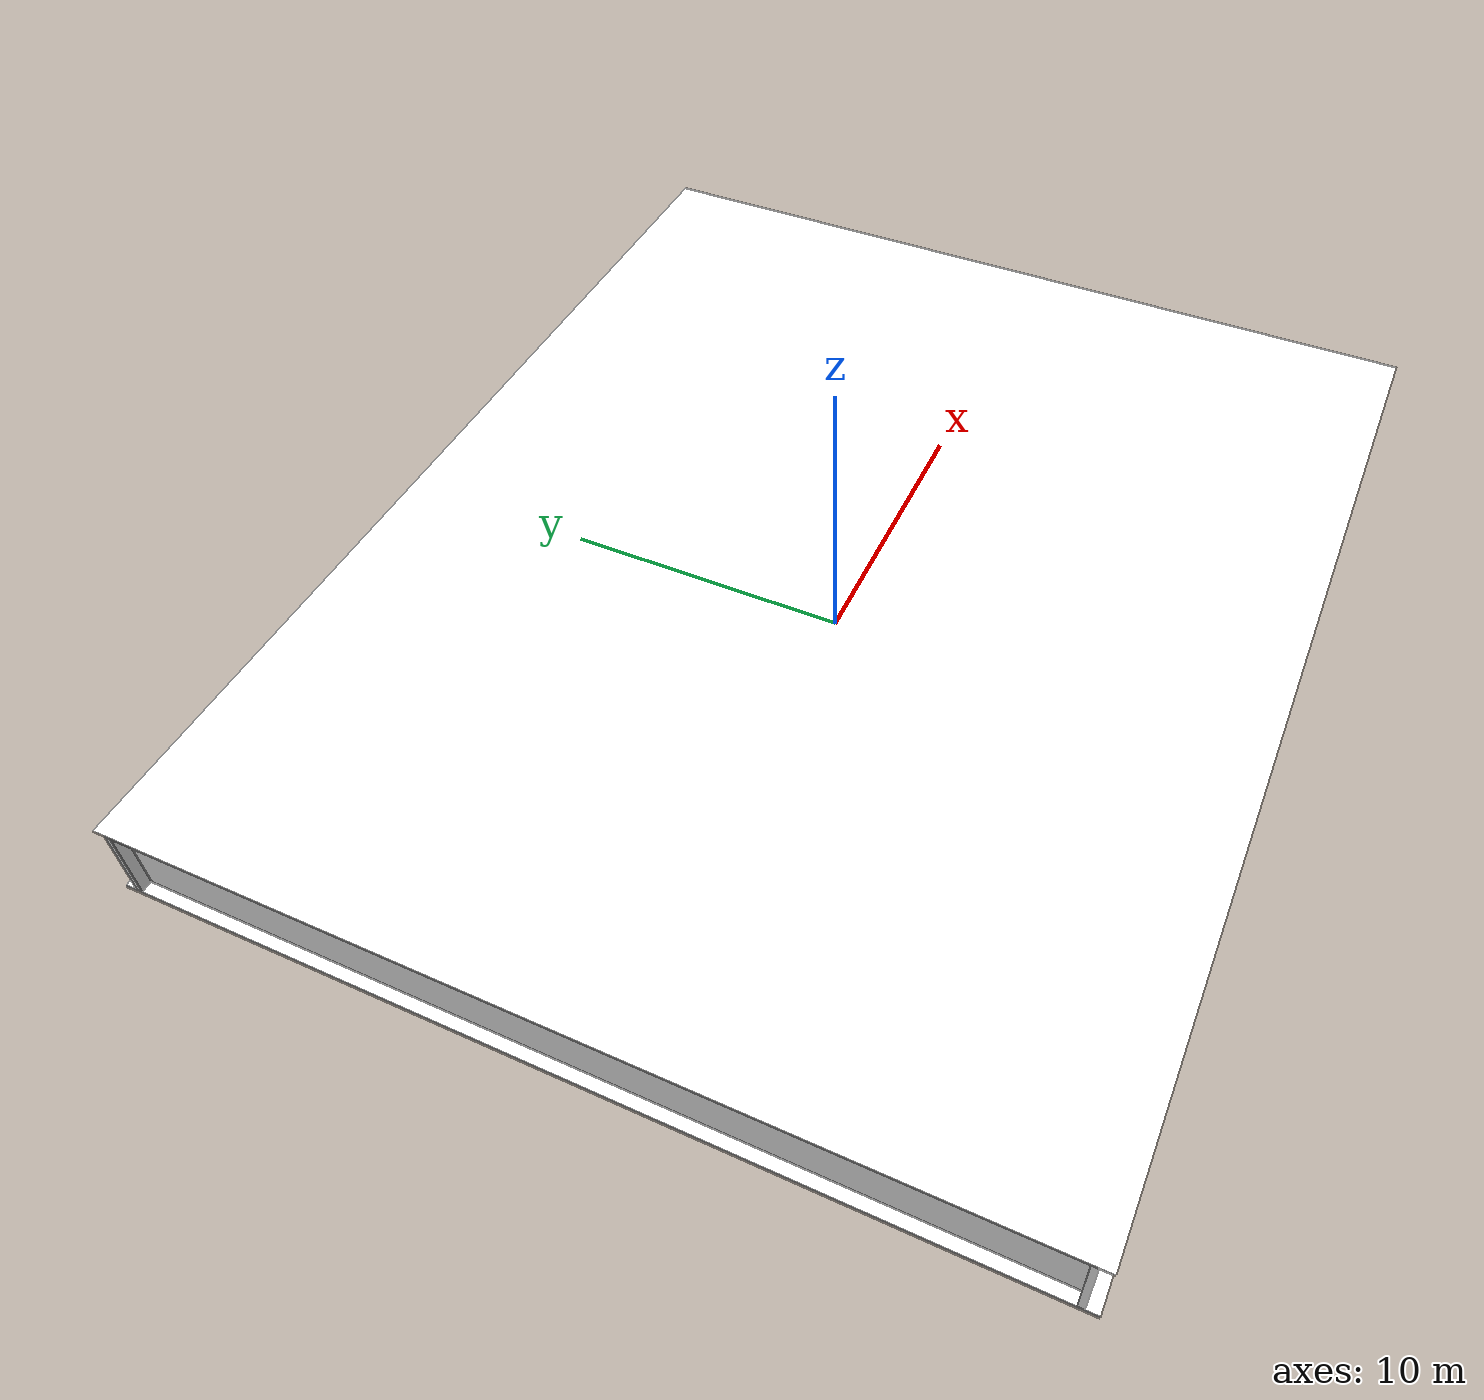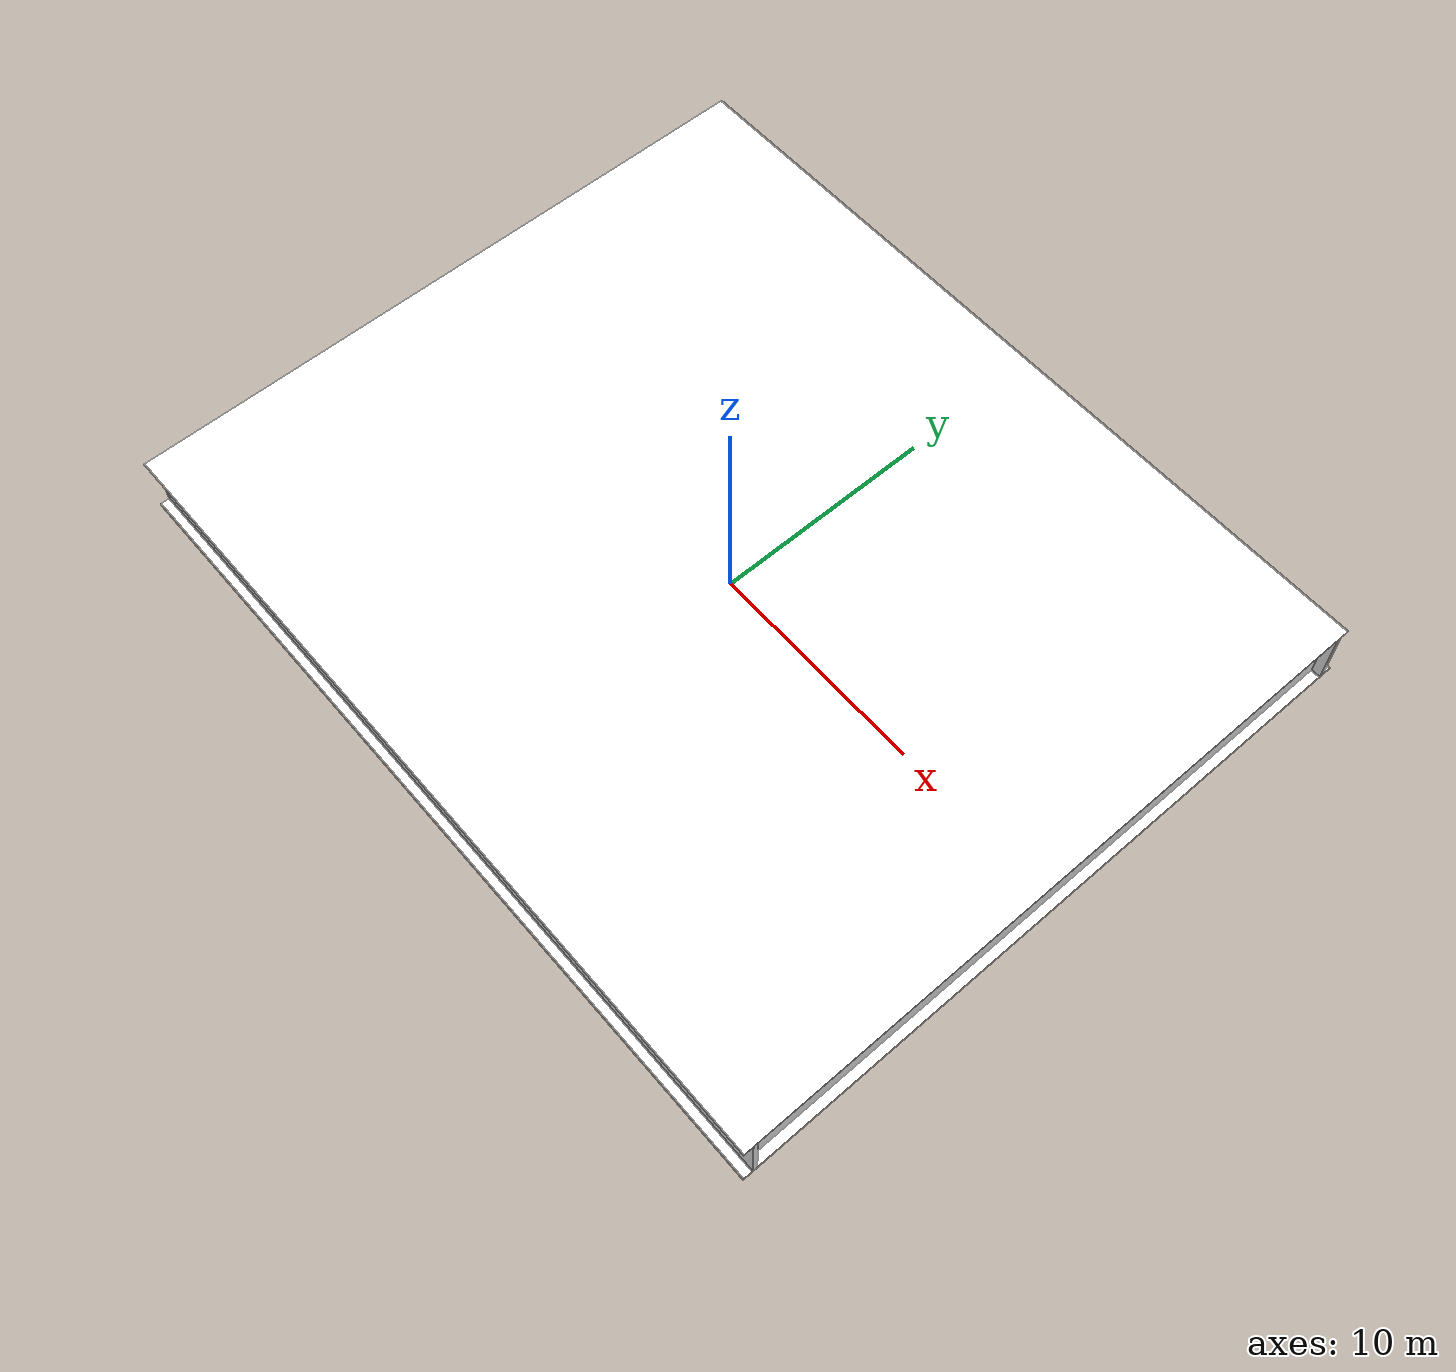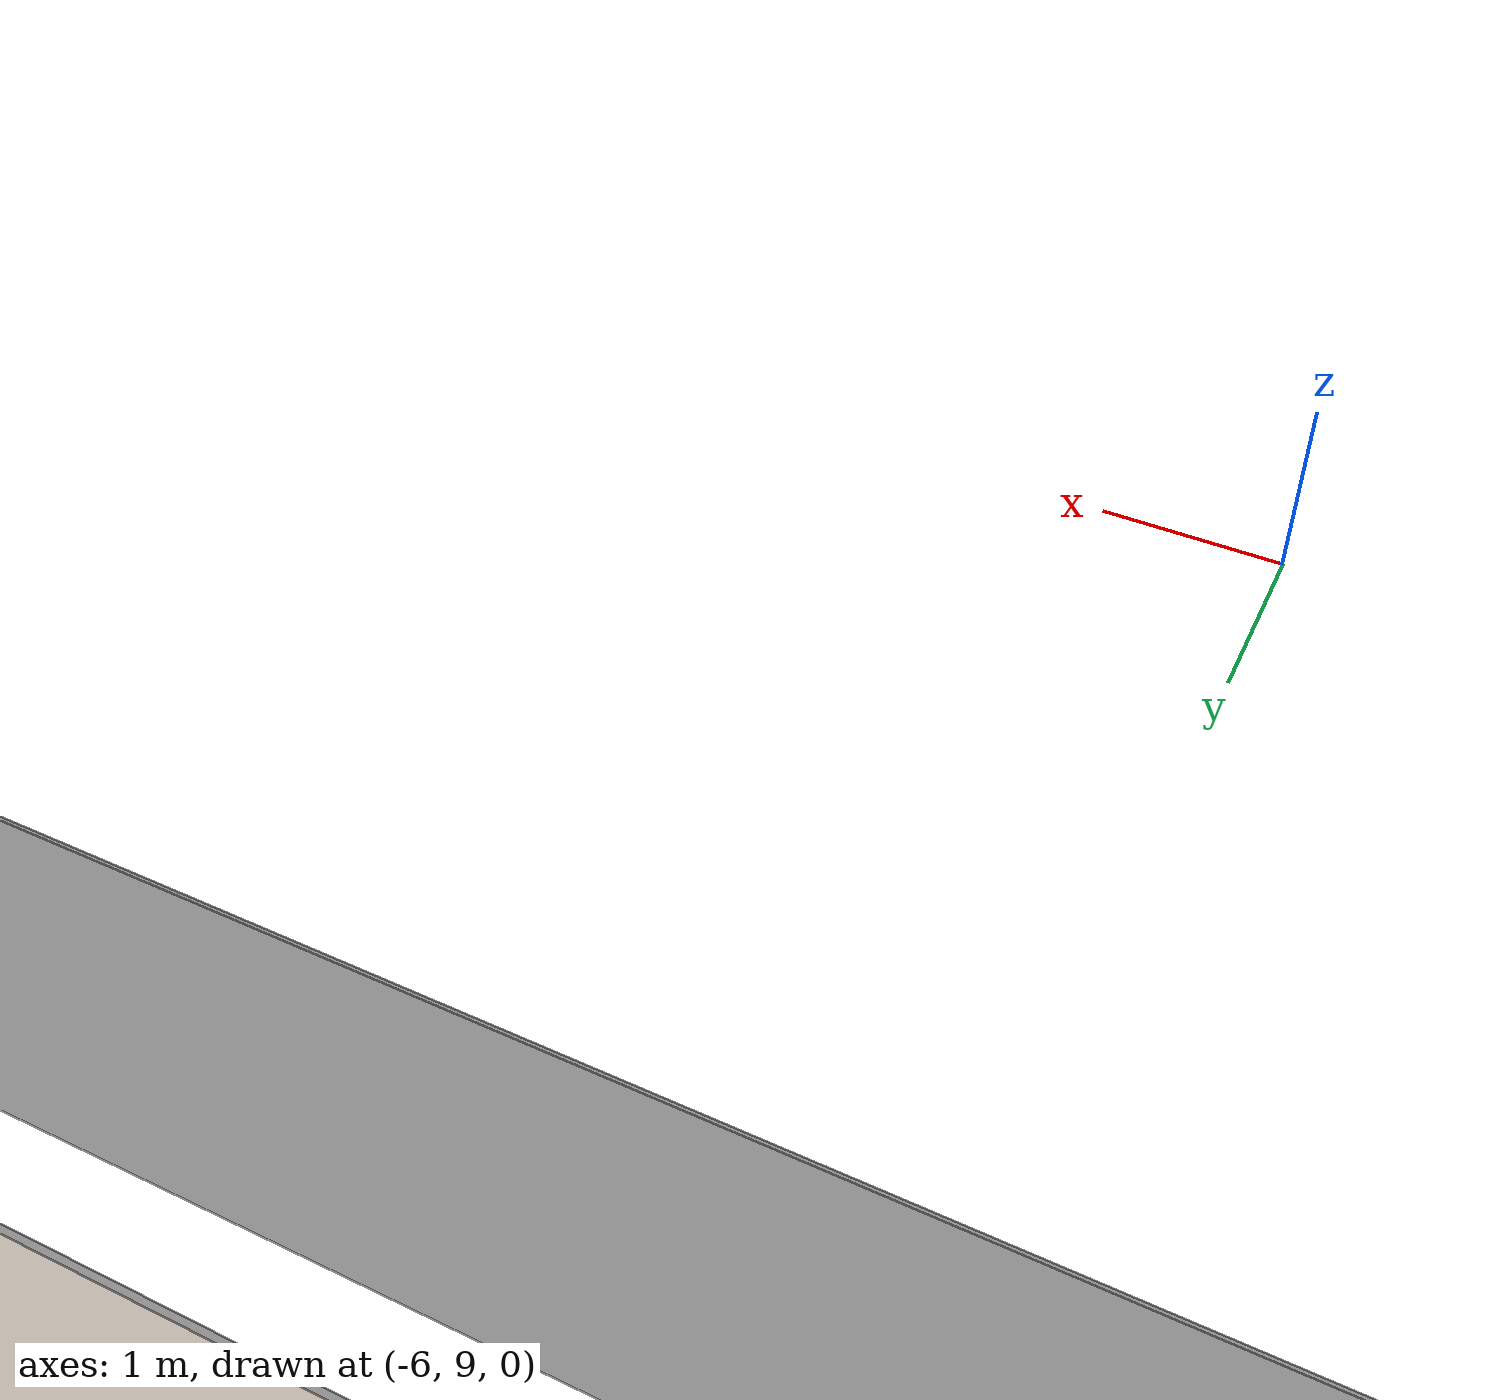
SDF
<sdf version="1.9">
 <world name="warehouse_irregular">
  <physics name="10ms" type="ode">
   <max_step_size>0.01</max_step_size>
   <real_time_factor>1</real_time_factor>
  </physics>
  <plugin filename="gz-sim-physics-system" name="gz::sim::systems::Physics"/>
  <plugin filename="gz-sim-user-commands-system" name="gz::sim::systems::UserCommands"/>
  <plugin filename="gz-sim-scene-broadcaster-system" name="gz::sim::systems::SceneBroadcaster"/>
  <plugin filename="gz-sim-imu-system" name="gz::sim::systems::Imu"/>
  <plugin filename="gz-sim-sensors-system" name="gz::sim::systems::Sensors"/>
  <gravity>0 0 -9.8</gravity>
  <scene><ambient>0.38 0.38 0.38 1</ambient><background>.18 .22 .28 1</background></scene>
  <light name="sun" type="directional"><direction>-.3 .2 -1</direction><diffuse>.8 .8 .8 1</diffuse></light>
  <model name="floor">
   <static>true</static>
   <pose>0 0 -0.05 0 0 0</pose>
   <link name="body">
    <visual name="surface">
     <geometry><box><size>36 30 0.1</size></box></geometry>
     <material>
      <ambient>1 1 1 1</ambient>
      <diffuse>1 1 1 1</diffuse>
      <pbr>
       <metal>
        <albedo_map>model://feature_warehouse_materials/textures/concrete.png</albedo_map>
        <roughness>.9</roughness>
        <metalness>0</metalness>
       </metal>
      </pbr>
     </material>
    </visual>
    <collision name="solid"><geometry><box><size>36 30 0.1</size></box></geometry></collision>
   </link>
  </model>
  <model name="wall_0">
   <static>true</static>
   <pose>0 14.5 1.4 0 0 0</pose>
   <link name="body">
    <visual name="surface">
     <geometry><box><size>36 0.2 2.8</size></box></geometry>
     <material>
      <ambient>1 1 1 1</ambient>
      <diffuse>1 1 1 1</diffuse>
      <pbr>
       <metal>
        <albedo_map>model://feature_warehouse_materials/textures/wall_0.png</albedo_map>
        <roughness>.9</roughness>
        <metalness>0</metalness>
       </metal>
      </pbr>
     </material>
    </visual>
    <collision name="solid"><geometry><box><size>36 0.2 2.8</size></box></geometry></collision>
   </link>
  </model>
  <model name="wall_1">
   <static>true</static>
   <pose>0 -14.5 1.4 0 0 0</pose>
   <link name="body">
    <visual name="surface">
     <geometry><box><size>36 0.2 2.8</size></box></geometry>
     <material>
      <ambient>1 1 1 1</ambient>
      <diffuse>1 1 1 1</diffuse>
      <pbr>
       <metal>
        <albedo_map>model://feature_warehouse_materials/textures/wall_1.png</albedo_map>
        <roughness>.9</roughness>
        <metalness>0</metalness>
       </metal>
      </pbr>
     </material>
    </visual>
    <collision name="solid"><geometry><box><size>36 0.2 2.8</size></box></geometry></collision>
   </link>
  </model>
  <model name="wall_2">
   <static>true</static>
   <pose>17.5 0 1.4 0 0 0</pose>
   <link name="body">
    <visual name="surface">
     <geometry><box><size>0.2 29 2.8</size></box></geometry>
     <material>
      <ambient>1 1 1 1</ambient>
      <diffuse>1 1 1 1</diffuse>
      <pbr>
       <metal>
        <albedo_map>model://feature_warehouse_materials/textures/wall_2.png</albedo_map>
        <roughness>.9</roughness>
        <metalness>0</metalness>
       </metal>
      </pbr>
     </material>
    </visual>
    <collision name="solid"><geometry><box><size>0.2 29 2.8</size></box></geometry></collision>
   </link>
  </model>
  <model name="wall_3">
   <static>true</static>
   <pose>-17.5 0 1.4 0 0 0</pose>
   <link name="body">
    <visual name="surface">
     <geometry><box><size>0.2 29 2.8</size></box></geometry>
     <material>
      <ambient>1 1 1 1</ambient>
      <diffuse>1 1 1 1</diffuse>
      <pbr>
       <metal>
        <albedo_map>model://feature_warehouse_materials/textures/wall_3.png</albedo_map>
        <roughness>.9</roughness>
        <metalness>0</metalness>
       </metal>
      </pbr>
     </material>
    </visual>
    <collision name="solid"><geometry><box><size>0.2 29 2.8</size></box></geometry></collision>
   </link>
  </model>
  <model name="concrete_patch_0">
   <static>true</static>
   <pose>-4.115097575578446 13.957961733746362 0.0006 0 0 -2.7177806267711726</pose>
   <link name="body">
    <visual name="surface">
     <geometry><box><size>0.3410374711611035 0.16528034942773398 0.001</size></box></geometry>
     <material>
      <ambient>0.5230129829485876 0.5230129829485876 0.5230129829485876 1</ambient>
      <diffuse>0.5230129829485876 0.5230129829485876 0.5230129829485876 1</diffuse>
     </material>
    </visual>
   </link>
  </model>
  <model name="concrete_patch_1">
   <static>true</static>
   <pose>-6.723605739083766 -7.700950095424983 0.0006 0 0 -0.3456703043749436</pose>
   <link name="body">
    <visual name="surface">
     <geometry><box><size>0.10381919483092236 0.17840451050713638 0.001</size></box></geometry>
     <material>
      <ambient>0.3721956331743649 0.3721956331743649 0.3721956331743649 1</ambient>
      <diffuse>0.3721956331743649 0.3721956331743649 0.3721956331743649 1</diffuse>
     </material>
    </visual>
   </link>
  </model>
  <model name="concrete_patch_2">
   <static>true</static>
   <pose>5.949070558169414 -8.505571744087193 0.0006 0 0 -2.2799647951458066</pose>
   <link name="body">
    <visual name="surface">
     <geometry><box><size>0.2143445875840025 0.055244427069164645 0.001</size></box></geometry>
     <material>
      <ambient>0.40188329781848925 0.40188329781848925 0.40188329781848925 1</ambient>
      <diffuse>0.40188329781848925 0.40188329781848925 0.40188329781848925 1</diffuse>
     </material>
    </visual>
   </link>
  </model>
  <model name="concrete_patch_3">
   <static>true</static>
   <pose>12.625233777267376 1.225561237347712 0.0006 0 0 -2.4488327674367394</pose>
   <link name="body">
    <visual name="surface">
     <geometry><box><size>0.4447900156607603 0.06071284143889829 0.001</size></box></geometry>
     <material>
      <ambient>0.37453560521862583 0.37453560521862583 0.37453560521862583 1</ambient>
      <diffuse>0.37453560521862583 0.37453560521862583 0.37453560521862583 1</diffuse>
     </material>
    </visual>
   </link>
  </model>
  <model name="concrete_patch_4">
   <static>true</static>
   <pose>-4.485532859746655 -9.899440025865703 0.0006 0 0 -0.239286738937599</pose>
   <link name="body">
    <visual name="surface">
     <geometry><box><size>0.11698559926552246 0.10054518932792351 0.001</size></box></geometry>
     <material>
      <ambient>0.4540820040918009 0.4540820040918009 0.4540820040918009 1</ambient>
      <diffuse>0.4540820040918009 0.4540820040918009 0.4540820040918009 1</diffuse>
     </material>
    </visual>
   </link>
  </model>
  <model name="concrete_patch_5">
   <static>true</static>
   <pose>11.136755613075735 2.6897395905029953 0.0006 0 0 -2.0269613945206753</pose>
   <link name="body">
    <visual name="surface">
     <geometry><box><size>0.10106423568529893 0.03303162497626108 0.001</size></box></geometry>
     <material>
      <ambient>0.3624628892585192 0.3624628892585192 0.3624628892585192 1</ambient>
      <diffuse>0.3624628892585192 0.3624628892585192 0.3624628892585192 1</diffuse>
     </material>
    </visual>
   </link>
  </model>
  <model name="concrete_patch_6">
   <static>true</static>
   <pose>-7.708475909224955 10.715653862771592 0.0006 0 0 0.3110669065295735</pose>
   <link name="body">
    <visual name="surface">
     <geometry><box><size>0.35138165184556985 0.1514570237064501 0.001</size></box></geometry>
     <material>
      <ambient>0.3307612838558225 0.3307612838558225 0.3307612838558225 1</ambient>
      <diffuse>0.3307612838558225 0.3307612838558225 0.3307612838558225 1</diffuse>
     </material>
    </visual>
   </link>
  </model>
  <model name="concrete_patch_7">
   <static>true</static>
   <pose>-4.085600719409417 5.768773873070934 0.0006 0 0 1.2162793266107519</pose>
   <link name="body">
    <visual name="surface">
     <geometry><box><size>0.09467714827229519 0.1959222576192792 0.001</size></box></geometry>
     <material>
      <ambient>0.34056218263552784 0.34056218263552784 0.34056218263552784 1</ambient>
      <diffuse>0.34056218263552784 0.34056218263552784 0.34056218263552784 1</diffuse>
     </material>
    </visual>
   </link>
  </model>
  <model name="concrete_patch_8">
   <static>true</static>
   <pose>-6.905951013907288 -9.63875734657784 0.0006 0 0 -2.0632234117912356</pose>
   <link name="body">
    <visual name="surface">
     <geometry><box><size>0.16435704276290414 0.1438436247709705 0.001</size></box></geometry>
     <material>
      <ambient>0.5038455552334508 0.5038455552334508 0.5038455552334508 1</ambient>
      <diffuse>0.5038455552334508 0.5038455552334508 0.5038455552334508 1</diffuse>
     </material>
    </visual>
   </link>
  </model>
  <model name="concrete_patch_9">
   <static>true</static>
   <pose>1.6479483322677808 12.423588153241042 0.0006 0 0 -0.7898164293172547</pose>
   <link name="body">
    <visual name="surface">
     <geometry><box><size>0.15082280976605056 0.12401393445859708 0.001</size></box></geometry>
     <material>
      <ambient>0.377588667283837 0.377588667283837 0.377588667283837 1</ambient>
      <diffuse>0.377588667283837 0.377588667283837 0.377588667283837 1</diffuse>
     </material>
    </visual>
   </link>
  </model>
  <model name="concrete_patch_10">
   <static>true</static>
   <pose>-3.542278335358409 -3.9849489914512333 0.0006 0 0 0.47974877984140285</pose>
   <link name="body">
    <visual name="surface">
     <geometry><box><size>0.20083621213462566 0.07623368485079651 0.001</size></box></geometry>
     <material>
      <ambient>0.5027167555597051 0.5027167555597051 0.5027167555597051 1</ambient>
      <diffuse>0.5027167555597051 0.5027167555597051 0.5027167555597051 1</diffuse>
     </material>
    </visual>
   </link>
  </model>
  <model name="concrete_patch_11">
   <static>true</static>
   <pose>-10.305460478600711 -2.00810798786973 0.0006 0 0 -1.0152370035446545</pose>
   <link name="body">
    <visual name="surface">
     <geometry><box><size>0.35070232564056275 0.04545488203444496 0.001</size></box></geometry>
     <material>
      <ambient>0.35538187843651625 0.35538187843651625 0.35538187843651625 1</ambient>
      <diffuse>0.35538187843651625 0.35538187843651625 0.35538187843651625 1</diffuse>
     </material>
    </visual>
   </link>
  </model>
  <model name="concrete_patch_12">
   <static>true</static>
   <pose>7.43953518512372 -11.273007286307434 0.0006 0 0 -0.1633482656960883</pose>
   <link name="body">
    <visual name="surface">
     <geometry><box><size>0.14765590343093077 0.17333241949647082 0.001</size></box></geometry>
     <material>
      <ambient>0.4508384630222539 0.4508384630222539 0.4508384630222539 1</ambient>
      <diffuse>0.4508384630222539 0.4508384630222539 0.4508384630222539 1</diffuse>
     </material>
    </visual>
   </link>
  </model>
  <model name="concrete_patch_13">
   <static>true</static>
   <pose>-1.5708928783646314 -2.5940814569195076 0.0006 0 0 -0.8808935604553811</pose>
   <link name="body">
    <visual name="surface">
     <geometry><box><size>0.20035579361307604 0.174697899184013 0.001</size></box></geometry>
     <material>
      <ambient>0.5231804011164841 0.5231804011164841 0.5231804011164841 1</ambient>
      <diffuse>0.5231804011164841 0.5231804011164841 0.5231804011164841 1</diffuse>
     </material>
    </visual>
   </link>
  </model>
  <model name="concrete_patch_14">
   <static>true</static>
   <pose>-8.217430454813963 13.914036345789711 0.0006 0 0 1.3866274076039886</pose>
   <link name="body">
    <visual name="surface">
     <geometry><box><size>0.28196065937643805 0.09643512882500528 0.001</size></box></geometry>
     <material>
      <ambient>0.4007991366429039 0.4007991366429039 0.4007991366429039 1</ambient>
      <diffuse>0.4007991366429039 0.4007991366429039 0.4007991366429039 1</diffuse>
     </material>
    </visual>
   </link>
  </model>
  <model name="concrete_patch_15">
   <static>true</static>
   <pose>2.781636243740195 10.124663031818734 0.0006 0 0 -0.6505084695027863</pose>
   <link name="body">
    <visual name="surface">
     <geometry><box><size>0.2406142793179195 0.08237193785753599 0.001</size></box></geometry>
     <material>
      <ambient>0.4213159084643905 0.4213159084643905 0.4213159084643905 1</ambient>
      <diffuse>0.4213159084643905 0.4213159084643905 0.4213159084643905 1</diffuse>
     </material>
    </visual>
   </link>
  </model>
  <model name="concrete_patch_16">
   <static>true</static>
   <pose>0.12013841802948377 1.0394994562967081 0.0006 0 0 -2.0343797038362395</pose>
   <link name="body">
    <visual name="surface">
     <geometry><box><size>0.4749351294602968 0.0779080887140289 0.001</size></box></geometry>
     <material>
      <ambient>0.5000608175277388 0.5000608175277388 0.5000608175277388 1</ambient>
      <diffuse>0.5000608175277388 0.5000608175277388 0.5000608175277388 1</diffuse>
     </material>
    </visual>
   </link>
  </model>
  <model name="concrete_patch_17">
   <static>true</static>
   <pose>12.428401802960476 -13.15309355146772 0.0006 0 0 1.7702626018864676</pose>
   <link name="body">
    <visual name="surface">
     <geometry><box><size>0.3614276565489297 0.1599395885994566 0.001</size></box></geometry>
     <material>
      <ambient>0.43360541656030316 0.43360541656030316 0.43360541656030316 1</ambient>
      <diffuse>0.43360541656030316 0.43360541656030316 0.43360541656030316 1</diffuse>
     </material>
    </visual>
   </link>
  </model>
  <model name="concrete_patch_18">
   <static>true</static>
   <pose>4.8735747405206205 -9.749623047401021 0.0006 0 0 -0.9512410553362809</pose>
   <link name="body">
    <visual name="surface">
     <geometry><box><size>0.08407313347637324 0.19794176696496787 0.001</size></box></geometry>
     <material>
      <ambient>0.3698179727905562 0.3698179727905562 0.3698179727905562 1</ambient>
      <diffuse>0.3698179727905562 0.3698179727905562 0.3698179727905562 1</diffuse>
     </material>
    </visual>
   </link>
  </model>
  <model name="concrete_patch_19">
   <static>true</static>
   <pose>5.807485984472045 -11.206608065663072 0.0006 0 0 -2.639322946215921</pose>
   <link name="body">
    <visual name="surface">
     <geometry><box><size>0.46309701573778184 0.10554934495754399 0.001</size></box></geometry>
     <material>
      <ambient>0.3322362473567429 0.3322362473567429 0.3322362473567429 1</ambient>
      <diffuse>0.3322362473567429 0.3322362473567429 0.3322362473567429 1</diffuse>
     </material>
    </visual>
   </link>
  </model>
  <model name="concrete_patch_20">
   <static>true</static>
   <pose>-5.272117061118863 -10.10073997615947 0.0006 0 0 1.2380190593094138</pose>
   <link name="body">
    <visual name="surface">
     <geometry><box><size>0.3054834023441327 0.07259288133838457 0.001</size></box></geometry>
     <material>
      <ambient>0.36572815046321305 0.36572815046321305 0.36572815046321305 1</ambient>
      <diffuse>0.36572815046321305 0.36572815046321305 0.36572815046321305 1</diffuse>
     </material>
    </visual>
   </link>
  </model>
  <model name="concrete_patch_21">
   <static>true</static>
   <pose>3.4643936872537395 -0.6916489456248733 0.0006 0 0 1.0025813696339299</pose>
   <link name="body">
    <visual name="surface">
     <geometry><box><size>0.3482290640769431 0.06765525154568489 0.001</size></box></geometry>
     <material>
      <ambient>0.4630936487407965 0.4630936487407965 0.4630936487407965 1</ambient>
      <diffuse>0.4630936487407965 0.4630936487407965 0.4630936487407965 1</diffuse>
     </material>
    </visual>
   </link>
  </model>
  <model name="concrete_patch_22">
   <static>true</static>
   <pose>-5.767066411567267 6.274147059067328 0.0006 0 0 1.7860754652054744</pose>
   <link name="body">
    <visual name="surface">
     <geometry><box><size>0.11280063178678662 0.15236529053724168 0.001</size></box></geometry>
     <material>
      <ambient>0.42892734383907744 0.42892734383907744 0.42892734383907744 1</ambient>
      <diffuse>0.42892734383907744 0.42892734383907744 0.42892734383907744 1</diffuse>
     </material>
    </visual>
   </link>
  </model>
  <model name="concrete_patch_23">
   <static>true</static>
   <pose>6.196264489521482 -0.24921566618229107 0.0006 0 0 2.198401988689489</pose>
   <link name="body">
    <visual name="surface">
     <geometry><box><size>0.10725160107914228 0.1589254249871139 0.001</size></box></geometry>
     <material>
      <ambient>0.3536386838716532 0.3536386838716532 0.3536386838716532 1</ambient>
      <diffuse>0.3536386838716532 0.3536386838716532 0.3536386838716532 1</diffuse>
     </material>
    </visual>
   </link>
  </model>
  <model name="concrete_patch_24">
   <static>true</static>
   <pose>8.253948915280617 -6.4821725666336345 0.0006 0 0 0.9015008740180281</pose>
   <link name="body">
    <visual name="surface">
     <geometry><box><size>0.13493146654354335 0.1348032268012523 0.001</size></box></geometry>
     <material>
      <ambient>0.4351740518051935 0.4351740518051935 0.4351740518051935 1</ambient>
      <diffuse>0.4351740518051935 0.4351740518051935 0.4351740518051935 1</diffuse>
     </material>
    </visual>
   </link>
  </model>
  <model name="concrete_patch_25">
   <static>true</static>
   <pose>-2.201866053222343 4.226834383114333 0.0006 0 0 -2.5875452584796346</pose>
   <link name="body">
    <visual name="surface">
     <geometry><box><size>0.4417568450754465 0.19784802029514972 0.001</size></box></geometry>
     <material>
      <ambient>0.4775990321298761 0.4775990321298761 0.4775990321298761 1</ambient>
      <diffuse>0.4775990321298761 0.4775990321298761 0.4775990321298761 1</diffuse>
     </material>
    </visual>
   </link>
  </model>
  <model name="concrete_patch_26">
   <static>true</static>
   <pose>3.599852657658321 -4.187587014069203 0.0006 0 0 -2.2833414863841277</pose>
   <link name="body">
    <visual name="surface">
     <geometry><box><size>0.4316616486225173 0.17519444473952886 0.001</size></box></geometry>
     <material>
      <ambient>0.43539037403485903 0.43539037403485903 0.43539037403485903 1</ambient>
      <diffuse>0.43539037403485903 0.43539037403485903 0.43539037403485903 1</diffuse>
     </material>
    </visual>
   </link>
  </model>
  <model name="concrete_patch_27">
   <static>true</static>
   <pose>-11.511544108007044 -9.484470568630492 0.0006 0 0 -0.2614906827322425</pose>
   <link name="body">
    <visual name="surface">
     <geometry><box><size>0.12617409275901517 0.14898016078374 0.001</size></box></geometry>
     <material>
      <ambient>0.4552531014726735 0.4552531014726735 0.4552531014726735 1</ambient>
      <diffuse>0.4552531014726735 0.4552531014726735 0.4552531014726735 1</diffuse>
     </material>
    </visual>
   </link>
  </model>
  <model name="concrete_patch_28">
   <static>true</static>
   <pose>-4.380300390896966 -9.751454855128864 0.0006 0 0 1.777880570741174</pose>
   <link name="body">
    <visual name="surface">
     <geometry><box><size>0.20257683120519832 0.18612225864963908 0.001</size></box></geometry>
     <material>
      <ambient>0.40104552742228206 0.40104552742228206 0.40104552742228206 1</ambient>
      <diffuse>0.40104552742228206 0.40104552742228206 0.40104552742228206 1</diffuse>
     </material>
    </visual>
   </link>
  </model>
  <model name="concrete_patch_29">
   <static>true</static>
   <pose>3.251818954420294 -9.735740807056711 0.0006 0 0 -0.8577306301835397</pose>
   <link name="body">
    <visual name="surface">
     <geometry><box><size>0.1951796508028899 0.14574777432333963 0.001</size></box></geometry>
     <material>
      <ambient>0.3696017635573537 0.3696017635573537 0.3696017635573537 1</ambient>
      <diffuse>0.3696017635573537 0.3696017635573537 0.3696017635573537 1</diffuse>
     </material>
    </visual>
   </link>
  </model>
  <model name="concrete_patch_30">
   <static>true</static>
   <pose>13.038348308648295 8.941561185085497 0.0006 0 0 -1.2859448940996494</pose>
   <link name="body">
    <visual name="surface">
     <geometry><box><size>0.44662910475259426 0.16765715394518388 0.001</size></box></geometry>
     <material>
      <ambient>0.43315095001594295 0.43315095001594295 0.43315095001594295 1</ambient>
      <diffuse>0.43315095001594295 0.43315095001594295 0.43315095001594295 1</diffuse>
     </material>
    </visual>
   </link>
  </model>
  <model name="concrete_patch_31">
   <static>true</static>
   <pose>8.245966954604548 -3.7159433217318174 0.0006 0 0 -2.9393310248429487</pose>
   <link name="body">
    <visual name="surface">
     <geometry><box><size>0.4866779922753985 0.19090846389194882 0.001</size></box></geometry>
     <material>
      <ambient>0.4178752955625157 0.4178752955625157 0.4178752955625157 1</ambient>
      <diffuse>0.4178752955625157 0.4178752955625157 0.4178752955625157 1</diffuse>
     </material>
    </visual>
   </link>
  </model>
  <model name="concrete_patch_32">
   <static>true</static>
   <pose>16.889275057081626 12.500726793843459 0.0006 0 0 -2.8654986876280057</pose>
   <link name="body">
    <visual name="surface">
     <geometry><box><size>0.3853707849721123 0.16464296636098247 0.001</size></box></geometry>
     <material>
      <ambient>0.36018472303015814 0.36018472303015814 0.36018472303015814 1</ambient>
      <diffuse>0.36018472303015814 0.36018472303015814 0.36018472303015814 1</diffuse>
     </material>
    </visual>
   </link>
  </model>
  <model name="concrete_patch_33">
   <static>true</static>
   <pose>5.081735357935646 -0.40106643044770607 0.0006 0 0 0.8193517189911121</pose>
   <link name="body">
    <visual name="surface">
     <geometry><box><size>0.1789058979567175 0.17164525929943822 0.001</size></box></geometry>
     <material>
      <ambient>0.3571439767082534 0.3571439767082534 0.3571439767082534 1</ambient>
      <diffuse>0.3571439767082534 0.3571439767082534 0.3571439767082534 1</diffuse>
     </material>
    </visual>
   </link>
  </model>
  <model name="concrete_patch_34">
   <static>true</static>
   <pose>6.9342709945675445 8.4609436539562 0.0006 0 0 -2.11212355424081</pose>
   <link name="body">
    <visual name="surface">
     <geometry><box><size>0.3896551609466443 0.06860419391362554 0.001</size></box></geometry>
     <material>
      <ambient>0.379828247734766 0.379828247734766 0.379828247734766 1</ambient>
      <diffuse>0.379828247734766 0.379828247734766 0.379828247734766 1</diffuse>
     </material>
    </visual>
   </link>
  </model>
  <model name="concrete_patch_35">
   <static>true</static>
   <pose>14.147594209296567 12.146753217169273 0.0006 0 0 -2.5773945473720445</pose>
   <link name="body">
    <visual name="surface">
     <geometry><box><size>0.18528145579910127 0.04687852747911509 0.001</size></box></geometry>
     <material>
      <ambient>0.317681045271176 0.317681045271176 0.317681045271176 1</ambient>
      <diffuse>0.317681045271176 0.317681045271176 0.317681045271176 1</diffuse>
     </material>
    </visual>
   </link>
  </model>
  <model name="concrete_patch_36">
   <static>true</static>
   <pose>-14.250769265056409 -5.602571911966898 0.0006 0 0 -1.1307715295928862</pose>
   <link name="body">
    <visual name="surface">
     <geometry><box><size>0.3597154631595746 0.19761359095736544 0.001</size></box></geometry>
     <material>
      <ambient>0.35916469509802007 0.35916469509802007 0.35916469509802007 1</ambient>
      <diffuse>0.35916469509802007 0.35916469509802007 0.35916469509802007 1</diffuse>
     </material>
    </visual>
   </link>
  </model>
  <model name="concrete_patch_37">
   <static>true</static>
   <pose>-10.988345253102091 -3.250426309690484 0.0006 0 0 0.6021258934732652</pose>
   <link name="body">
    <visual name="surface">
     <geometry><box><size>0.48443095328482694 0.11412339983069103 0.001</size></box></geometry>
     <material>
      <ambient>0.35009891575523466 0.35009891575523466 0.35009891575523466 1</ambient>
      <diffuse>0.35009891575523466 0.35009891575523466 0.35009891575523466 1</diffuse>
     </material>
    </visual>
   </link>
  </model>
  <model name="concrete_patch_38">
   <static>true</static>
   <pose>3.893123434860623 -8.976233132707625 0.0006 0 0 1.1123197621241534</pose>
   <link name="body">
    <visual name="surface">
     <geometry><box><size>0.25774737749761517 0.16285511957295432 0.001</size></box></geometry>
     <material>
      <ambient>0.4624119285649768 0.4624119285649768 0.4624119285649768 1</ambient>
      <diffuse>0.4624119285649768 0.4624119285649768 0.4624119285649768 1</diffuse>
     </material>
    </visual>
   </link>
  </model>
  <model name="concrete_patch_39">
   <static>true</static>
   <pose>7.805735863116336 13.786630194232245 0.0006 0 0 1.6846368754471532</pose>
   <link name="body">
    <visual name="surface">
     <geometry><box><size>0.27168154591915245 0.043739857138305034 0.001</size></box></geometry>
     <material>
      <ambient>0.45446857078715996 0.45446857078715996 0.45446857078715996 1</ambient>
      <diffuse>0.45446857078715996 0.45446857078715996 0.45446857078715996 1</diffuse>
     </material>
    </visual>
   </link>
  </model>
  <model name="concrete_patch_40">
   <static>true</static>
   <pose>-13.238568509065864 9.83755259906751 0.0006 0 0 -2.3424114872919275</pose>
   <link name="body">
    <visual name="surface">
     <geometry><box><size>0.38896473313438434 0.10838831607054795 0.001</size></box></geometry>
     <material>
      <ambient>0.38602600717064456 0.38602600717064456 0.38602600717064456 1</ambient>
      <diffuse>0.38602600717064456 0.38602600717064456 0.38602600717064456 1</diffuse>
     </material>
    </visual>
   </link>
  </model>
  <model name="concrete_patch_41">
   <static>true</static>
   <pose>-4.9813076332944775 -12.174679410754585 0.0006 0 0 -2.7596192545514397</pose>
   <link name="body">
    <visual name="surface">
     <geometry><box><size>0.3935598709281767 0.08661459442322228 0.001</size></box></geometry>
     <material>
      <ambient>0.41237561739261286 0.41237561739261286 0.41237561739261286 1</ambient>
      <diffuse>0.41237561739261286 0.41237561739261286 0.41237561739261286 1</diffuse>
     </material>
    </visual>
   </link>
  </model>
  <model name="concrete_patch_42">
   <static>true</static>
   <pose>-14.741551140335696 5.090986394202229 0.0006 0 0 -0.12249271842328735</pose>
   <link name="body">
    <visual name="surface">
     <geometry><box><size>0.3796452278462518 0.12390636045359701 0.001</size></box></geometry>
     <material>
      <ambient>0.4574309733602687 0.4574309733602687 0.4574309733602687 1</ambient>
      <diffuse>0.4574309733602687 0.4574309733602687 0.4574309733602687 1</diffuse>
     </material>
    </visual>
   </link>
  </model>
  <model name="concrete_patch_43">
   <static>true</static>
   <pose>-13.039353673341463 5.343183769472859 0.0006 0 0 -1.563677039174225</pose>
   <link name="body">
    <visual name="surface">
     <geometry><box><size>0.10618705003521588 0.14582692671168462 0.001</size></box></geometry>
     <material>
      <ambient>0.5284033165310783 0.5284033165310783 0.5284033165310783 1</ambient>
      <diffuse>0.5284033165310783 0.5284033165310783 0.5284033165310783 1</diffuse>
     </material>
    </visual>
   </link>
  </model>
  <model name="concrete_patch_44">
   <static>true</static>
   <pose>0.8832018339523273 -2.509604574991233 0.0006 0 0 -0.3065745176328294</pose>
   <link name="body">
    <visual name="surface">
     <geometry><box><size>0.23960395999619266 0.10761170678746038 0.001</size></box></geometry>
     <material>
      <ambient>0.3851393077609765 0.3851393077609765 0.3851393077609765 1</ambient>
      <diffuse>0.3851393077609765 0.3851393077609765 0.3851393077609765 1</diffuse>
     </material>
    </visual>
   </link>
  </model>
  <model name="concrete_patch_45">
   <static>true</static>
   <pose>-1.4433807541568502 -2.9665197919562694 0.0006 0 0 1.150385775311153</pose>
   <link name="body">
    <visual name="surface">
     <geometry><box><size>0.3462991568391786 0.19943941239512905 0.001</size></box></geometry>
     <material>
      <ambient>0.32397237541888785 0.32397237541888785 0.32397237541888785 1</ambient>
      <diffuse>0.32397237541888785 0.32397237541888785 0.32397237541888785 1</diffuse>
     </material>
    </visual>
   </link>
  </model>
  <model name="concrete_patch_46">
   <static>true</static>
   <pose>-15.52859334358571 1.176090542396011 0.0006 0 0 0.874254483947948</pose>
   <link name="body">
    <visual name="surface">
     <geometry><box><size>0.086758438744972 0.18141290131496818 0.001</size></box></geometry>
     <material>
      <ambient>0.4551813418749987 0.4551813418749987 0.4551813418749987 1</ambient>
      <diffuse>0.4551813418749987 0.4551813418749987 0.4551813418749987 1</diffuse>
     </material>
    </visual>
   </link>
  </model>
  <model name="concrete_patch_47">
   <static>true</static>
   <pose>3.5740988044072353 -0.6872861657778788 0.0006 0 0 1.1461449394331407</pose>
   <link name="body">
    <visual name="surface">
     <geometry><box><size>0.20526132929796953 0.04882272836014845 0.001</size></box></geometry>
     <material>
      <ambient>0.3675721210238552 0.3675721210238552 0.3675721210238552 1</ambient>
      <diffuse>0.3675721210238552 0.3675721210238552 0.3675721210238552 1</diffuse>
     </material>
    </visual>
   </link>
  </model>
  <model name="concrete_patch_48">
   <static>true</static>
   <pose>-5.873922134654562 -0.5263132164719355 0.0006 0 0 -0.6707204738826009</pose>
   <link name="body">
    <visual name="surface">
     <geometry><box><size>0.1169939604246398 0.09223131309245489 0.001</size></box></geometry>
     <material>
      <ambient>0.31462676100705744 0.31462676100705744 0.31462676100705744 1</ambient>
      <diffuse>0.31462676100705744 0.31462676100705744 0.31462676100705744 1</diffuse>
     </material>
    </visual>
   </link>
  </model>
  <model name="concrete_patch_49">
   <static>true</static>
   <pose>-7.221992548995193 -1.9591606207287438 0.0006 0 0 -0.5320581876934574</pose>
   <link name="body">
    <visual name="surface">
     <geometry><box><size>0.18713917982319234 0.18340196789523583 0.001</size></box></geometry>
     <material>
      <ambient>0.5036144645764127 0.5036144645764127 0.5036144645764127 1</ambient>
      <diffuse>0.5036144645764127 0.5036144645764127 0.5036144645764127 1</diffuse>
     </material>
    </visual>
   </link>
  </model>
  <model name="concrete_patch_50">
   <static>true</static>
   <pose>-4.994936964125268 5.124021694634379 0.0006 0 0 -0.5740902481445529</pose>
   <link name="body">
    <visual name="surface">
     <geometry><box><size>0.15276751696556706 0.04624581322898093 0.001</size></box></geometry>
     <material>
      <ambient>0.2980980467035635 0.2980980467035635 0.2980980467035635 1</ambient>
      <diffuse>0.2980980467035635 0.2980980467035635 0.2980980467035635 1</diffuse>
     </material>
    </visual>
   </link>
  </model>
  <model name="concrete_patch_51">
   <static>true</static>
   <pose>-11.125031114054323 3.756268334372706 0.0006 0 0 -0.42554586296876895</pose>
   <link name="body">
    <visual name="surface">
     <geometry><box><size>0.49477018645294196 0.051350356769778616 0.001</size></box></geometry>
     <material>
      <ambient>0.4844053093824895 0.4844053093824895 0.4844053093824895 1</ambient>
      <diffuse>0.4844053093824895 0.4844053093824895 0.4844053093824895 1</diffuse>
     </material>
    </visual>
   </link>
  </model>
  <model name="concrete_patch_52">
   <static>true</static>
   <pose>-10.089508912863199 -8.389708595119563 0.0006 0 0 0.8745581267314084</pose>
   <link name="body">
    <visual name="surface">
     <geometry><box><size>0.18536111010411913 0.17701313855095444 0.001</size></box></geometry>
     <material>
      <ambient>0.4814100324281928 0.4814100324281928 0.4814100324281928 1</ambient>
      <diffuse>0.4814100324281928 0.4814100324281928 0.4814100324281928 1</diffuse>
     </material>
    </visual>
   </link>
  </model>
  <model name="concrete_patch_53">
   <static>true</static>
   <pose>-4.829198488614892 -8.933722572430987 0.0006 0 0 1.364192408601534</pose>
   <link name="body">
    <visual name="surface">
     <geometry><box><size>0.0906039912638485 0.11394804946407835 0.001</size></box></geometry>
     <material>
      <ambient>0.505192515275727 0.505192515275727 0.505192515275727 1</ambient>
      <diffuse>0.505192515275727 0.505192515275727 0.505192515275727 1</diffuse>
     </material>
    </visual>
   </link>
  </model>
  <model name="concrete_patch_54">
   <static>true</static>
   <pose>7.779993693894422 -2.118168969400152 0.0006 0 0 -1.4671399730204253</pose>
   <link name="body">
    <visual name="surface">
     <geometry><box><size>0.18022176428677172 0.06014721074146327 0.001</size></box></geometry>
     <material>
      <ambient>0.48950954973335237 0.48950954973335237 0.48950954973335237 1</ambient>
      <diffuse>0.48950954973335237 0.48950954973335237 0.48950954973335237 1</diffuse>
     </material>
    </visual>
   </link>
  </model>
  <model name="concrete_patch_55">
   <static>true</static>
   <pose>-7.19208430193005 8.147852550896502 0.0006 0 0 -1.06427838188066</pose>
   <link name="body">
    <visual name="surface">
     <geometry><box><size>0.22588072502415624 0.19248104446765738 0.001</size></box></geometry>
     <material>
      <ambient>0.4364564708600575 0.4364564708600575 0.4364564708600575 1</ambient>
      <diffuse>0.4364564708600575 0.4364564708600575 0.4364564708600575 1</diffuse>
     </material>
    </visual>
   </link>
  </model>
  <model name="concrete_patch_56">
   <static>true</static>
   <pose>6.44769525356179 4.9427726671712655 0.0006 0 0 1.3596945290487854</pose>
   <link name="body">
    <visual name="surface">
     <geometry><box><size>0.3888884769010207 0.19318639208512461 0.001</size></box></geometry>
     <material>
      <ambient>0.4095008574594624 0.4095008574594624 0.4095008574594624 1</ambient>
      <diffuse>0.4095008574594624 0.4095008574594624 0.4095008574594624 1</diffuse>
     </material>
    </visual>
   </link>
  </model>
  <model name="concrete_patch_57">
   <static>true</static>
   <pose>-0.3293861891838752 -12.021677294101382 0.0006 0 0 -1.8783105214042022</pose>
   <link name="body">
    <visual name="surface">
     <geometry><box><size>0.4502279481216637 0.07959075741442939 0.001</size></box></geometry>
     <material>
      <ambient>0.32928115694014104 0.32928115694014104 0.32928115694014104 1</ambient>
      <diffuse>0.32928115694014104 0.32928115694014104 0.32928115694014104 1</diffuse>
     </material>
    </visual>
   </link>
  </model>
  <model name="concrete_patch_58">
   <static>true</static>
   <pose>-16.618989410165383 3.336401355562124 0.0006 0 0 2.9959911237594223</pose>
   <link name="body">
    <visual name="surface">
     <geometry><box><size>0.21151314987593012 0.04879857773153515 0.001</size></box></geometry>
     <material>
      <ambient>0.5079757562472446 0.5079757562472446 0.5079757562472446 1</ambient>
      <diffuse>0.5079757562472446 0.5079757562472446 0.5079757562472446 1</diffuse>
     </material>
    </visual>
   </link>
  </model>
  <model name="concrete_patch_59">
   <static>true</static>
   <pose>1.761206187301525 -12.973122535806313 0.0006 0 0 1.1188221488629786</pose>
   <link name="body">
    <visual name="surface">
     <geometry><box><size>0.4954540269920135 0.0686028686681317 0.001</size></box></geometry>
     <material>
      <ambient>0.34717567947566086 0.34717567947566086 0.34717567947566086 1</ambient>
      <diffuse>0.34717567947566086 0.34717567947566086 0.34717567947566086 1</diffuse>
     </material>
    </visual>
   </link>
  </model>
  <model name="concrete_patch_60">
   <static>true</static>
   <pose>9.163470922402354 2.4577617152129605 0.0006 0 0 -1.2643976294260075</pose>
   <link name="body">
    <visual name="surface">
     <geometry><box><size>0.3842058887774309 0.07426925938146911 0.001</size></box></geometry>
     <material>
      <ambient>0.3438035861972548 0.3438035861972548 0.3438035861972548 1</ambient>
      <diffuse>0.3438035861972548 0.3438035861972548 0.3438035861972548 1</diffuse>
     </material>
    </visual>
   </link>
  </model>
  <model name="concrete_patch_61">
   <static>true</static>
   <pose>-10.931057617990074 8.58346079944926 0.0006 0 0 -1.385193412058391</pose>
   <link name="body">
    <visual name="surface">
     <geometry><box><size>0.1262187288862002 0.18094161602729975 0.001</size></box></geometry>
     <material>
      <ambient>0.4438550715636477 0.4438550715636477 0.4438550715636477 1</ambient>
      <diffuse>0.4438550715636477 0.4438550715636477 0.4438550715636477 1</diffuse>
     </material>
    </visual>
   </link>
  </model>
  <model name="concrete_patch_62">
   <static>true</static>
   <pose>12.169654736169477 -1.9533701373874592 0.0006 0 0 -2.3656061591047264</pose>
   <link name="body">
    <visual name="surface">
     <geometry><box><size>0.4579299051402349 0.05557456630549615 0.001</size></box></geometry>
     <material>
      <ambient>0.449549050166352 0.449549050166352 0.449549050166352 1</ambient>
      <diffuse>0.449549050166352 0.449549050166352 0.449549050166352 1</diffuse>
     </material>
    </visual>
   </link>
  </model>
  <model name="concrete_patch_63">
   <static>true</static>
   <pose>-15.647237499369165 -11.273019038510743 0.0006 0 0 -0.5378085769982066</pose>
   <link name="body">
    <visual name="surface">
     <geometry><box><size>0.2462228516302038 0.18297292168195708 0.001</size></box></geometry>
     <material>
      <ambient>0.43172741633347667 0.43172741633347667 0.43172741633347667 1</ambient>
      <diffuse>0.43172741633347667 0.43172741633347667 0.43172741633347667 1</diffuse>
     </material>
    </visual>
   </link>
  </model>
  <model name="concrete_patch_64">
   <static>true</static>
   <pose>-3.5590894897705514 11.58477229328064 0.0006 0 0 -2.5428682922713057</pose>
   <link name="body">
    <visual name="surface">
     <geometry><box><size>0.1738103640229398 0.17689447416133294 0.001</size></box></geometry>
     <material>
      <ambient>0.5145174104675343 0.5145174104675343 0.5145174104675343 1</ambient>
      <diffuse>0.5145174104675343 0.5145174104675343 0.5145174104675343 1</diffuse>
     </material>
    </visual>
   </link>
  </model>
  <model name="concrete_patch_65">
   <static>true</static>
   <pose>14.42104533891375 -12.083653219925726 0.0006 0 0 2.7351165852886172</pose>
   <link name="body">
    <visual name="surface">
     <geometry><box><size>0.1330040601802409 0.0767168598400139 0.001</size></box></geometry>
     <material>
      <ambient>0.5096420165596776 0.5096420165596776 0.5096420165596776 1</ambient>
      <diffuse>0.5096420165596776 0.5096420165596776 0.5096420165596776 1</diffuse>
     </material>
    </visual>
   </link>
  </model>
  <model name="concrete_patch_66">
   <static>true</static>
   <pose>-6.046339819081915 -13.886405220240077 0.0006 0 0 -0.900085882811783</pose>
   <link name="body">
    <visual name="surface">
     <geometry><box><size>0.3666416681742663 0.0746381238163148 0.001</size></box></geometry>
     <material>
      <ambient>0.49992200339758286 0.49992200339758286 0.49992200339758286 1</ambient>
      <diffuse>0.49992200339758286 0.49992200339758286 0.49992200339758286 1</diffuse>
     </material>
    </visual>
   </link>
  </model>
  <model name="concrete_patch_67">
   <static>true</static>
   <pose>2.0985337733247427 -12.377071213076416 0.0006 0 0 1.05186048125476</pose>
   <link name="body">
    <visual name="surface">
     <geometry><box><size>0.18501419448927914 0.1827757870623283 0.001</size></box></geometry>
     <material>
      <ambient>0.4070827693553608 0.4070827693553608 0.4070827693553608 1</ambient>
      <diffuse>0.4070827693553608 0.4070827693553608 0.4070827693553608 1</diffuse>
     </material>
    </visual>
   </link>
  </model>
  <model name="concrete_patch_68">
   <static>true</static>
   <pose>-4.153584049041132 10.114149254909826 0.0006 0 0 -1.8919738790545682</pose>
   <link name="body">
    <visual name="surface">
     <geometry><box><size>0.3245111337251562 0.10807116053508793 0.001</size></box></geometry>
     <material>
      <ambient>0.38049309773484763 0.38049309773484763 0.38049309773484763 1</ambient>
      <diffuse>0.38049309773484763 0.38049309773484763 0.38049309773484763 1</diffuse>
     </material>
    </visual>
   </link>
  </model>
  <model name="concrete_patch_69">
   <static>true</static>
   <pose>3.4604814249082487 3.6439855506759145 0.0006 0 0 1.0686518408674388</pose>
   <link name="body">
    <visual name="surface">
     <geometry><box><size>0.4532666538415781 0.037664655391507124 0.001</size></box></geometry>
     <material>
      <ambient>0.3844256133369859 0.3844256133369859 0.3844256133369859 1</ambient>
      <diffuse>0.3844256133369859 0.3844256133369859 0.3844256133369859 1</diffuse>
     </material>
    </visual>
   </link>
  </model>
  <model name="concrete_patch_70">
   <static>true</static>
   <pose>-14.415761653406584 2.58020282136836 0.0006 0 0 1.6223183769971916</pose>
   <link name="body">
    <visual name="surface">
     <geometry><box><size>0.4738328332902397 0.09221881716060926 0.001</size></box></geometry>
     <material>
      <ambient>0.5007051671841636 0.5007051671841636 0.5007051671841636 1</ambient>
      <diffuse>0.5007051671841636 0.5007051671841636 0.5007051671841636 1</diffuse>
     </material>
    </visual>
   </link>
  </model>
  <model name="concrete_patch_71">
   <static>true</static>
   <pose>-5.965803417594486 7.451793975934283 0.0006 0 0 0.5708299213346182</pose>
   <link name="body">
    <visual name="surface">
     <geometry><box><size>0.2804743966390799 0.1276968492866242 0.001</size></box></geometry>
     <material>
      <ambient>0.40110797837925344 0.40110797837925344 0.40110797837925344 1</ambient>
      <diffuse>0.40110797837925344 0.40110797837925344 0.40110797837925344 1</diffuse>
     </material>
    </visual>
   </link>
  </model>
  <model name="concrete_patch_72">
   <static>true</static>
   <pose>14.375071246794523 8.634639212585391 0.0006 0 0 -2.5502875542926615</pose>
   <link name="body">
    <visual name="surface">
     <geometry><box><size>0.4347143788723042 0.1638801870635189 0.001</size></box></geometry>
     <material>
      <ambient>0.3862567706915493 0.3862567706915493 0.3862567706915493 1</ambient>
      <diffuse>0.3862567706915493 0.3862567706915493 0.3862567706915493 1</diffuse>
     </material>
    </visual>
   </link>
  </model>
  <model name="concrete_patch_73">
   <static>true</static>
   <pose>2.223112668037423 -9.155641653238298 0.0006 0 0 0.37712649941399023</pose>
   <link name="body">
    <visual name="surface">
     <geometry><box><size>0.34912061815110534 0.19593805906175013 0.001</size></box></geometry>
     <material>
      <ambient>0.29516292175983194 0.29516292175983194 0.29516292175983194 1</ambient>
      <diffuse>0.29516292175983194 0.29516292175983194 0.29516292175983194 1</diffuse>
     </material>
    </visual>
   </link>
  </model>
  <model name="concrete_patch_74">
   <static>true</static>
   <pose>2.592691294302636 -7.393624713771175 0.0006 0 0 1.0405488513247398</pose>
   <link name="body">
    <visual name="surface">
     <geometry><box><size>0.117164447859039 0.18157608535114897 0.001</size></box></geometry>
     <material>
      <ambient>0.29402072002049967 0.29402072002049967 0.29402072002049967 1</ambient>
      <diffuse>0.29402072002049967 0.29402072002049967 0.29402072002049967 1</diffuse>
     </material>
    </visual>
   </link>
  </model>
  <model name="concrete_patch_75">
   <static>true</static>
   <pose>11.127272028599073 -2.561879522378012 0.0006 0 0 -1.8584677836695904</pose>
   <link name="body">
    <visual name="surface">
     <geometry><box><size>0.334275486646483 0.1631464557284799 0.001</size></box></geometry>
     <material>
      <ambient>0.4503392640845831 0.4503392640845831 0.4503392640845831 1</ambient>
      <diffuse>0.4503392640845831 0.4503392640845831 0.4503392640845831 1</diffuse>
     </material>
    </visual>
   </link>
  </model>
  <model name="concrete_patch_76">
   <static>true</static>
   <pose>-6.1985915689601345 -10.780619427065393 0.0006 0 0 -2.7284479186695516</pose>
   <link name="body">
    <visual name="surface">
     <geometry><box><size>0.29031532481422556 0.08262243381041114 0.001</size></box></geometry>
     <material>
      <ambient>0.4969199543642637 0.4969199543642637 0.4969199543642637 1</ambient>
      <diffuse>0.4969199543642637 0.4969199543642637 0.4969199543642637 1</diffuse>
     </material>
    </visual>
   </link>
  </model>
  <model name="concrete_patch_77">
   <static>true</static>
   <pose>-4.448641377197465 12.81350816669357 0.0006 0 0 2.551776843549339</pose>
   <link name="body">
    <visual name="surface">
     <geometry><box><size>0.27447990784818893 0.039546712375569865 0.001</size></box></geometry>
     <material>
      <ambient>0.3039209267187395 0.3039209267187395 0.3039209267187395 1</ambient>
      <diffuse>0.3039209267187395 0.3039209267187395 0.3039209267187395 1</diffuse>
     </material>
    </visual>
   </link>
  </model>
  <model name="concrete_patch_78">
   <static>true</static>
   <pose>14.241152249233753 -7.130896806474853 0.0006 0 0 -1.602483751354972</pose>
   <link name="body">
    <visual name="surface">
     <geometry><box><size>0.4825985034346577 0.182770760738168 0.001</size></box></geometry>
     <material>
      <ambient>0.4434075344662265 0.4434075344662265 0.4434075344662265 1</ambient>
      <diffuse>0.4434075344662265 0.4434075344662265 0.4434075344662265 1</diffuse>
     </material>
    </visual>
   </link>
  </model>
  <model name="concrete_patch_79">
   <static>true</static>
   <pose>-13.239614399875691 -13.176427403725977 0.0006 0 0 -1.5238059353305178</pose>
   <link name="body">
    <visual name="surface">
     <geometry><box><size>0.3584625121675123 0.1171337970262335 0.001</size></box></geometry>
     <material>
      <ambient>0.5234246532144183 0.5234246532144183 0.5234246532144183 1</ambient>
      <diffuse>0.5234246532144183 0.5234246532144183 0.5234246532144183 1</diffuse>
     </material>
    </visual>
   </link>
  </model>
  <model name="concrete_patch_80">
   <static>true</static>
   <pose>5.878307943399577 -10.395438571133758 0.0006 0 0 -1.1808858970687124</pose>
   <link name="body">
    <visual name="surface">
     <geometry><box><size>0.10010978843166023 0.09498816191790761 0.001</size></box></geometry>
     <material>
      <ambient>0.3165661356023741 0.3165661356023741 0.3165661356023741 1</ambient>
      <diffuse>0.3165661356023741 0.3165661356023741 0.3165661356023741 1</diffuse>
     </material>
    </visual>
   </link>
  </model>
  <model name="concrete_patch_81">
   <static>true</static>
   <pose>-10.959770945896489 -8.393697101876976 0.0006 0 0 1.945323711939789</pose>
   <link name="body">
    <visual name="surface">
     <geometry><box><size>0.2592873715019643 0.16388999822609182 0.001</size></box></geometry>
     <material>
      <ambient>0.39756985920665977 0.39756985920665977 0.39756985920665977 1</ambient>
      <diffuse>0.39756985920665977 0.39756985920665977 0.39756985920665977 1</diffuse>
     </material>
    </visual>
   </link>
  </model>
  <model name="concrete_patch_82">
   <static>true</static>
   <pose>6.3134348280497505 -0.4354748874669738 0.0006 0 0 2.565186795135298</pose>
   <link name="body">
    <visual name="surface">
     <geometry><box><size>0.31231849240654935 0.15102710134797176 0.001</size></box></geometry>
     <material>
      <ambient>0.3095274507291014 0.3095274507291014 0.3095274507291014 1</ambient>
      <diffuse>0.3095274507291014 0.3095274507291014 0.3095274507291014 1</diffuse>
     </material>
    </visual>
   </link>
  </model>
  <model name="concrete_patch_83">
   <static>true</static>
   <pose>-5.664863603148897 -5.8823236656005875 0.0006 0 0 1.4469659656526304</pose>
   <link name="body">
    <visual name="surface">
     <geometry><box><size>0.3200371941761753 0.14956626635838477 0.001</size></box></geometry>
     <material>
      <ambient>0.4459250100787544 0.4459250100787544 0.4459250100787544 1</ambient>
      <diffuse>0.4459250100787544 0.4459250100787544 0.4459250100787544 1</diffuse>
     </material>
    </visual>
   </link>
  </model>
  <model name="concrete_patch_84">
   <static>true</static>
   <pose>-15.508019333649054 4.769549789995445 0.0006 0 0 -2.0806550524027276</pose>
   <link name="body">
    <visual name="surface">
     <geometry><box><size>0.4323842155122364 0.09687938221301295 0.001</size></box></geometry>
     <material>
      <ambient>0.29046193395339986 0.29046193395339986 0.29046193395339986 1</ambient>
      <diffuse>0.29046193395339986 0.29046193395339986 0.29046193395339986 1</diffuse>
     </material>
    </visual>
   </link>
  </model>
  <model name="concrete_patch_85">
   <static>true</static>
   <pose>-7.09309329534894 -2.055721966952129 0.0006 0 0 2.390536583222728</pose>
   <link name="body">
    <visual name="surface">
     <geometry><box><size>0.2188578040925232 0.11450124664299541 0.001</size></box></geometry>
     <material>
      <ambient>0.4945646644897195 0.4945646644897195 0.4945646644897195 1</ambient>
      <diffuse>0.4945646644897195 0.4945646644897195 0.4945646644897195 1</diffuse>
     </material>
    </visual>
   </link>
  </model>
  <model name="concrete_patch_86">
   <static>true</static>
   <pose>-10.081604210871713 -4.280085624954362 0.0006 0 0 -2.4675796717062104</pose>
   <link name="body">
    <visual name="surface">
     <geometry><box><size>0.3376888404473126 0.03512148428346302 0.001</size></box></geometry>
     <material>
      <ambient>0.5071253480310649 0.5071253480310649 0.5071253480310649 1</ambient>
      <diffuse>0.5071253480310649 0.5071253480310649 0.5071253480310649 1</diffuse>
     </material>
    </visual>
   </link>
  </model>
  <model name="concrete_patch_87">
   <static>true</static>
   <pose>-4.448880955811871 11.23657882567057 0.0006 0 0 -2.842829749918744</pose>
   <link name="body">
    <visual name="surface">
     <geometry><box><size>0.27339606438976305 0.06275885075314111 0.001</size></box></geometry>
     <material>
      <ambient>0.3374122956000345 0.3374122956000345 0.3374122956000345 1</ambient>
      <diffuse>0.3374122956000345 0.3374122956000345 0.3374122956000345 1</diffuse>
     </material>
    </visual>
   </link>
  </model>
  <model name="concrete_patch_88">
   <static>true</static>
   <pose>4.049317079067471 -3.986503663570776 0.0006 0 0 -0.10106789107487923</pose>
   <link name="body">
    <visual name="surface">
     <geometry><box><size>0.09310083235708516 0.15545457428472553 0.001</size></box></geometry>
     <material>
      <ambient>0.5062172638607136 0.5062172638607136 0.5062172638607136 1</ambient>
      <diffuse>0.5062172638607136 0.5062172638607136 0.5062172638607136 1</diffuse>
     </material>
    </visual>
   </link>
  </model>
  <model name="concrete_patch_89">
   <static>true</static>
   <pose>-8.828801202796608 -1.4402536802628987 0.0006 0 0 1.286300547465829</pose>
   <link name="body">
    <visual name="surface">
     <geometry><box><size>0.41761964621453185 0.061284856943220764 0.001</size></box></geometry>
     <material>
      <ambient>0.43875244899850385 0.43875244899850385 0.43875244899850385 1</ambient>
      <diffuse>0.43875244899850385 0.43875244899850385 0.43875244899850385 1</diffuse>
     </material>
    </visual>
   </link>
  </model>
  <model name="concrete_patch_90">
   <static>true</static>
   <pose>5.686129235464268 -0.41418153912532496 0.0006 0 0 0.2526749334922149</pose>
   <link name="body">
    <visual name="surface">
     <geometry><box><size>0.25060560156175726 0.172885491657441 0.001</size></box></geometry>
     <material>
      <ambient>0.3466347724646848 0.3466347724646848 0.3466347724646848 1</ambient>
      <diffuse>0.3466347724646848 0.3466347724646848 0.3466347724646848 1</diffuse>
     </material>
    </visual>
   </link>
  </model>
  <model name="concrete_patch_91">
   <static>true</static>
   <pose>16.511932376639024 13.283151941823796 0.0006 0 0 -1.7601194219653993</pose>
   <link name="body">
    <visual name="surface">
     <geometry><box><size>0.3448150384758358 0.1282712746472804 0.001</size></box></geometry>
     <material>
      <ambient>0.39314730514663143 0.39314730514663143 0.39314730514663143 1</ambient>
      <diffuse>0.39314730514663143 0.39314730514663143 0.39314730514663143 1</diffuse>
     </material>
    </visual>
   </link>
  </model>
  <model name="concrete_patch_92">
   <static>true</static>
   <pose>-10.942076244205902 11.486514543646486 0.0006 0 0 2.7847418788494265</pose>
   <link name="body">
    <visual name="surface">
     <geometry><box><size>0.2500229064694387 0.11781228360735825 0.001</size></box></geometry>
     <material>
      <ambient>0.4343546856364231 0.4343546856364231 0.4343546856364231 1</ambient>
      <diffuse>0.4343546856364231 0.4343546856364231 0.4343546856364231 1</diffuse>
     </material>
    </visual>
   </link>
  </model>
  <model name="concrete_patch_93">
   <static>true</static>
   <pose>-4.227898167556138 8.754724641416889 0.0006 0 0 -0.3801077749742161</pose>
   <link name="body">
    <visual name="surface">
     <geometry><box><size>0.23463766386446028 0.10460995226982478 0.001</size></box></geometry>
     <material>
      <ambient>0.30944974226275257 0.30944974226275257 0.30944974226275257 1</ambient>
      <diffuse>0.30944974226275257 0.30944974226275257 0.30944974226275257 1</diffuse>
     </material>
    </visual>
   </link>
  </model>
  <model name="concrete_patch_94">
   <static>true</static>
   <pose>-0.1649861664124721 -13.0007396674667 0.0006 0 0 1.8052351777510438</pose>
   <link name="body">
    <visual name="surface">
     <geometry><box><size>0.4497452260704114 0.13140751998340805 0.001</size></box></geometry>
     <material>
      <ambient>0.3521715144298419 0.3521715144298419 0.3521715144298419 1</ambient>
      <diffuse>0.3521715144298419 0.3521715144298419 0.3521715144298419 1</diffuse>
     </material>
    </visual>
   </link>
  </model>
  <model name="concrete_patch_95">
   <static>true</static>
   <pose>13.46384363568227 8.993202880275746 0.0006 0 0 1.1099333784260974</pose>
   <link name="body">
    <visual name="surface">
     <geometry><box><size>0.3079262380859977 0.18894618070875724 0.001</size></box></geometry>
     <material>
      <ambient>0.389555701776903 0.389555701776903 0.389555701776903 1</ambient>
      <diffuse>0.389555701776903 0.389555701776903 0.389555701776903 1</diffuse>
     </material>
    </visual>
   </link>
  </model>
  <model name="concrete_patch_96">
   <static>true</static>
   <pose>12.018995773766104 -1.9214981712113754 0.0006 0 0 -2.8483341467563332</pose>
   <link name="body">
    <visual name="surface">
     <geometry><box><size>0.27446402122525 0.07122076367396754 0.001</size></box></geometry>
     <material>
      <ambient>0.336878336853389 0.336878336853389 0.336878336853389 1</ambient>
      <diffuse>0.336878336853389 0.336878336853389 0.336878336853389 1</diffuse>
     </material>
    </visual>
   </link>
  </model>
  <model name="concrete_patch_97">
   <static>true</static>
   <pose>-5.575163281737106 1.5704344509851857 0.0006 0 0 -1.4004178155496751</pose>
   <link name="body">
    <visual name="surface">
     <geometry><box><size>0.13007607690484088 0.1018538288844348 0.001</size></box></geometry>
     <material>
      <ambient>0.33827100915329056 0.33827100915329056 0.33827100915329056 1</ambient>
      <diffuse>0.33827100915329056 0.33827100915329056 0.33827100915329056 1</diffuse>
     </material>
    </visual>
   </link>
  </model>
  <model name="concrete_patch_98">
   <static>true</static>
   <pose>-9.580631884110662 5.391586903900404 0.0006 0 0 -2.1377434685305943</pose>
   <link name="body">
    <visual name="surface">
     <geometry><box><size>0.2919267288459281 0.06076187877102926 0.001</size></box></geometry>
     <material>
      <ambient>0.318618521395894 0.318618521395894 0.318618521395894 1</ambient>
      <diffuse>0.318618521395894 0.318618521395894 0.318618521395894 1</diffuse>
     </material>
    </visual>
   </link>
  </model>
  <model name="concrete_patch_99">
   <static>true</static>
   <pose>10.690036011590742 3.0104842933053817 0.0006 0 0 0.49479835693317664</pose>
   <link name="body">
    <visual name="surface">
     <geometry><box><size>0.3544400003625466 0.12850172381850816 0.001</size></box></geometry>
     <material>
      <ambient>0.5043934060620092 0.5043934060620092 0.5043934060620092 1</ambient>
      <diffuse>0.5043934060620092 0.5043934060620092 0.5043934060620092 1</diffuse>
     </material>
    </visual>
   </link>
  </model>
  <model name="concrete_patch_100">
   <static>true</static>
   <pose>-7.379449879197043 -12.19637054919238 0.0006 0 0 2.530284934945402</pose>
   <link name="body">
    <visual name="surface">
     <geometry><box><size>0.29789035305058786 0.12362809908644465 0.001</size></box></geometry>
     <material>
      <ambient>0.45979732529207284 0.45979732529207284 0.45979732529207284 1</ambient>
      <diffuse>0.45979732529207284 0.45979732529207284 0.45979732529207284 1</diffuse>
     </material>
    </visual>
   </link>
  </model>
  <model name="concrete_patch_101">
   <static>true</static>
   <pose>-15.682086781024072 -5.658934722961007 0.0006 0 0 -1.6474521312828982</pose>
   <link name="body">
    <visual name="surface">
     <geometry><box><size>0.48498573463867656 0.17366191582292687 0.001</size></box></geometry>
     <material>
      <ambient>0.476606385336852 0.476606385336852 0.476606385336852 1</ambient>
      <diffuse>0.476606385336852 0.476606385336852 0.476606385336852 1</diffuse>
     </material>
    </visual>
   </link>
  </model>
  <model name="concrete_patch_102">
   <static>true</static>
   <pose>15.61902242946423 -3.082831992482797 0.0006 0 0 -2.9245534653999337</pose>
   <link name="body">
    <visual name="surface">
     <geometry><box><size>0.09521128668122114 0.06928998870295747 0.001</size></box></geometry>
     <material>
      <ambient>0.2983619354231398 0.2983619354231398 0.2983619354231398 1</ambient>
      <diffuse>0.2983619354231398 0.2983619354231398 0.2983619354231398 1</diffuse>
     </material>
    </visual>
   </link>
  </model>
  <model name="concrete_patch_103">
   <static>true</static>
   <pose>-10.471953603676223 6.515763398069879 0.0006 0 0 -1.6547924956703826</pose>
   <link name="body">
    <visual name="surface">
     <geometry><box><size>0.2637455830824234 0.10047038453729 0.001</size></box></geometry>
     <material>
      <ambient>0.3279704574854456 0.3279704574854456 0.3279704574854456 1</ambient>
      <diffuse>0.3279704574854456 0.3279704574854456 0.3279704574854456 1</diffuse>
     </material>
    </visual>
   </link>
  </model>
  <model name="concrete_patch_104">
   <static>true</static>
   <pose>4.22237485868752 -2.42491943350484 0.0006 0 0 2.2548706040531066</pose>
   <link name="body">
    <visual name="surface">
     <geometry><box><size>0.4359082625338231 0.15588403984259755 0.001</size></box></geometry>
     <material>
      <ambient>0.38875480409735785 0.38875480409735785 0.38875480409735785 1</ambient>
      <diffuse>0.38875480409735785 0.38875480409735785 0.38875480409735785 1</diffuse>
     </material>
    </visual>
   </link>
  </model>
  <model name="concrete_patch_105">
   <static>true</static>
   <pose>-1.244356048107953 7.903320307577882 0.0006 0 0 1.2013912712450239</pose>
   <link name="body">
    <visual name="surface">
     <geometry><box><size>0.08317525162603259 0.12157072021784392 0.001</size></box></geometry>
     <material>
      <ambient>0.3650698230643255 0.3650698230643255 0.3650698230643255 1</ambient>
      <diffuse>0.3650698230643255 0.3650698230643255 0.3650698230643255 1</diffuse>
     </material>
    </visual>
   </link>
  </model>
  <model name="concrete_patch_106">
   <static>true</static>
   <pose>7.649051202630094 13.99704777463186 0.0006 0 0 1.4411873530515074</pose>
   <link name="body">
    <visual name="surface">
     <geometry><box><size>0.4988945829615779 0.048811833754129855 0.001</size></box></geometry>
     <material>
      <ambient>0.5180017477878769 0.5180017477878769 0.5180017477878769 1</ambient>
      <diffuse>0.5180017477878769 0.5180017477878769 0.5180017477878769 1</diffuse>
     </material>
    </visual>
   </link>
  </model>
  <model name="concrete_patch_107">
   <static>true</static>
   <pose>3.145893051383574 0.5955083515766262 0.0006 0 0 -1.5846246081736828</pose>
   <link name="body">
    <visual name="surface">
     <geometry><box><size>0.23849567572202085 0.11899527264915814 0.001</size></box></geometry>
     <material>
      <ambient>0.4368885491815371 0.4368885491815371 0.4368885491815371 1</ambient>
      <diffuse>0.4368885491815371 0.4368885491815371 0.4368885491815371 1</diffuse>
     </material>
    </visual>
   </link>
  </model>
  <model name="concrete_patch_108">
   <static>true</static>
   <pose>16.247412252204214 -8.948833696737198 0.0006 0 0 -1.6783255165172628</pose>
   <link name="body">
    <visual name="surface">
     <geometry><box><size>0.230777292359854 0.06590095178578888 0.001</size></box></geometry>
     <material>
      <ambient>0.427019331702101 0.427019331702101 0.427019331702101 1</ambient>
      <diffuse>0.427019331702101 0.427019331702101 0.427019331702101 1</diffuse>
     </material>
    </visual>
   </link>
  </model>
  <model name="concrete_patch_109">
   <static>true</static>
   <pose>-0.9132540097012729 7.226941602561826 0.0006 0 0 -0.9894423513391288</pose>
   <link name="body">
    <visual name="surface">
     <geometry><box><size>0.10191840308391487 0.05047122903883486 0.001</size></box></geometry>
     <material>
      <ambient>0.4084895722873361 0.4084895722873361 0.4084895722873361 1</ambient>
      <diffuse>0.4084895722873361 0.4084895722873361 0.4084895722873361 1</diffuse>
     </material>
    </visual>
   </link>
  </model>
  <model name="concrete_patch_110">
   <static>true</static>
   <pose>6.804686449925498 12.136288893994536 0.0006 0 0 2.325626862049102</pose>
   <link name="body">
    <visual name="surface">
     <geometry><box><size>0.2320512214972238 0.14870802043131473 0.001</size></box></geometry>
     <material>
      <ambient>0.5097232072714906 0.5097232072714906 0.5097232072714906 1</ambient>
      <diffuse>0.5097232072714906 0.5097232072714906 0.5097232072714906 1</diffuse>
     </material>
    </visual>
   </link>
  </model>
  <model name="concrete_patch_111">
   <static>true</static>
   <pose>-12.899351940136725 -12.59735453845526 0.0006 0 0 1.9965118233431705</pose>
   <link name="body">
    <visual name="surface">
     <geometry><box><size>0.13824525928905343 0.1985953893491612 0.001</size></box></geometry>
     <material>
      <ambient>0.38873641134624703 0.38873641134624703 0.38873641134624703 1</ambient>
      <diffuse>0.38873641134624703 0.38873641134624703 0.38873641134624703 1</diffuse>
     </material>
    </visual>
   </link>
  </model>
  <model name="concrete_patch_112">
   <static>true</static>
   <pose>7.055083673767573 2.518178841576077 0.0006 0 0 1.64464389095252</pose>
   <link name="body">
    <visual name="surface">
     <geometry><box><size>0.4794923684420618 0.1455520728130107 0.001</size></box></geometry>
     <material>
      <ambient>0.3248802273355627 0.3248802273355627 0.3248802273355627 1</ambient>
      <diffuse>0.3248802273355627 0.3248802273355627 0.3248802273355627 1</diffuse>
     </material>
    </visual>
   </link>
  </model>
  <model name="concrete_patch_113">
   <static>true</static>
   <pose>-2.915909871084443 -7.0757422682201625 0.0006 0 0 -1.7632404491852742</pose>
   <link name="body">
    <visual name="surface">
     <geometry><box><size>0.10959769413541336 0.09619525816446692 0.001</size></box></geometry>
     <material>
      <ambient>0.49625603409809077 0.49625603409809077 0.49625603409809077 1</ambient>
      <diffuse>0.49625603409809077 0.49625603409809077 0.49625603409809077 1</diffuse>
     </material>
    </visual>
   </link>
  </model>
  <model name="concrete_patch_114">
   <static>true</static>
   <pose>2.5111414886678034 8.76202626712362 0.0006 0 0 2.281999942241944</pose>
   <link name="body">
    <visual name="surface">
     <geometry><box><size>0.4129546542337788 0.19163111473057057 0.001</size></box></geometry>
     <material>
      <ambient>0.2914201500379386 0.2914201500379386 0.2914201500379386 1</ambient>
      <diffuse>0.2914201500379386 0.2914201500379386 0.2914201500379386 1</diffuse>
     </material>
    </visual>
   </link>
  </model>
  <model name="concrete_patch_115">
   <static>true</static>
   <pose>6.175630495374097 -2.635986907343675 0.0006 0 0 -0.9820333492634683</pose>
   <link name="body">
    <visual name="surface">
     <geometry><box><size>0.09393625451402138 0.06263814595718555 0.001</size></box></geometry>
     <material>
      <ambient>0.45754842315671146 0.45754842315671146 0.45754842315671146 1</ambient>
      <diffuse>0.45754842315671146 0.45754842315671146 0.45754842315671146 1</diffuse>
     </material>
    </visual>
   </link>
  </model>
  <model name="concrete_patch_116">
   <static>true</static>
   <pose>-3.0231470314363857 -8.785744016865884 0.0006 0 0 -0.3336129295452004</pose>
   <link name="body">
    <visual name="surface">
     <geometry><box><size>0.4204764625373556 0.15699150536463882 0.001</size></box></geometry>
     <material>
      <ambient>0.4223147138112238 0.4223147138112238 0.4223147138112238 1</ambient>
      <diffuse>0.4223147138112238 0.4223147138112238 0.4223147138112238 1</diffuse>
     </material>
    </visual>
   </link>
  </model>
  <model name="concrete_patch_117">
   <static>true</static>
   <pose>-2.843020883649608 -11.233966102522643 0.0006 0 0 2.1342863777397447</pose>
   <link name="body">
    <visual name="surface">
     <geometry><box><size>0.4436661968436355 0.07056785778501043 0.001</size></box></geometry>
     <material>
      <ambient>0.3706193023208269 0.3706193023208269 0.3706193023208269 1</ambient>
      <diffuse>0.3706193023208269 0.3706193023208269 0.3706193023208269 1</diffuse>
     </material>
    </visual>
   </link>
  </model>
  <model name="concrete_patch_118">
   <static>true</static>
   <pose>7.202769867954505 -8.954775815741073 0.0006 0 0 -1.538215603683902</pose>
   <link name="body">
    <visual name="surface">
     <geometry><box><size>0.4817148573323853 0.11080876693508199 0.001</size></box></geometry>
     <material>
      <ambient>0.44379000849601635 0.44379000849601635 0.44379000849601635 1</ambient>
      <diffuse>0.44379000849601635 0.44379000849601635 0.44379000849601635 1</diffuse>
     </material>
    </visual>
   </link>
  </model>
  <model name="concrete_patch_119">
   <static>true</static>
   <pose>-4.287349443485796 7.141612008033178 0.0006 0 0 -1.8111546365293631</pose>
   <link name="body">
    <visual name="surface">
     <geometry><box><size>0.32714629320518496 0.17121538394579777 0.001</size></box></geometry>
     <material>
      <ambient>0.39714322121807655 0.39714322121807655 0.39714322121807655 1</ambient>
      <diffuse>0.39714322121807655 0.39714322121807655 0.39714322121807655 1</diffuse>
     </material>
    </visual>
   </link>
  </model>
  <model name="concrete_patch_120">
   <static>true</static>
   <pose>-8.75158842871897 9.533829686315894 0.0006 0 0 1.4312185711521117</pose>
   <link name="body">
    <visual name="surface">
     <geometry><box><size>0.3973864408084798 0.17135142365693568 0.001</size></box></geometry>
     <material>
      <ambient>0.45834206476336703 0.45834206476336703 0.45834206476336703 1</ambient>
      <diffuse>0.45834206476336703 0.45834206476336703 0.45834206476336703 1</diffuse>
     </material>
    </visual>
   </link>
  </model>
  <model name="concrete_patch_121">
   <static>true</static>
   <pose>13.460247646218384 11.547299077650788 0.0006 0 0 0.4270836678463752</pose>
   <link name="body">
    <visual name="surface">
     <geometry><box><size>0.4987219517314308 0.08300615835839119 0.001</size></box></geometry>
     <material>
      <ambient>0.522972747672047 0.522972747672047 0.522972747672047 1</ambient>
      <diffuse>0.522972747672047 0.522972747672047 0.522972747672047 1</diffuse>
     </material>
    </visual>
   </link>
  </model>
  <model name="concrete_patch_122">
   <static>true</static>
   <pose>4.475100710739582 0.6276506736884855 0.0006 0 0 1.7161152784340334</pose>
   <link name="body">
    <visual name="surface">
     <geometry><box><size>0.3839958045936714 0.12654802077869845 0.001</size></box></geometry>
     <material>
      <ambient>0.4129629708134136 0.4129629708134136 0.4129629708134136 1</ambient>
      <diffuse>0.4129629708134136 0.4129629708134136 0.4129629708134136 1</diffuse>
     </material>
    </visual>
   </link>
  </model>
  <model name="concrete_patch_123">
   <static>true</static>
   <pose>7.596497263077794 2.6403748588845986 0.0006 0 0 2.9891427274702496</pose>
   <link name="body">
    <visual name="surface">
     <geometry><box><size>0.4707286472788569 0.12645427898444525 0.001</size></box></geometry>
     <material>
      <ambient>0.505222338849785 0.505222338849785 0.505222338849785 1</ambient>
      <diffuse>0.505222338849785 0.505222338849785 0.505222338849785 1</diffuse>
     </material>
    </visual>
   </link>
  </model>
  <model name="concrete_patch_124">
   <static>true</static>
   <pose>11.015300437433627 -6.069417118717454 0.0006 0 0 1.5029679390894461</pose>
   <link name="body">
    <visual name="surface">
     <geometry><box><size>0.2486056115503827 0.1980311895221383 0.001</size></box></geometry>
     <material>
      <ambient>0.46850192904434246 0.46850192904434246 0.46850192904434246 1</ambient>
      <diffuse>0.46850192904434246 0.46850192904434246 0.46850192904434246 1</diffuse>
     </material>
    </visual>
   </link>
  </model>
  <model name="concrete_patch_125">
   <static>true</static>
   <pose>5.19931766167344 0.6722408475824171 0.0006 0 0 -2.4028997444498974</pose>
   <link name="body">
    <visual name="surface">
     <geometry><box><size>0.1386110759658517 0.12769284171737327 0.001</size></box></geometry>
     <material>
      <ambient>0.3892662377069918 0.3892662377069918 0.3892662377069918 1</ambient>
      <diffuse>0.3892662377069918 0.3892662377069918 0.3892662377069918 1</diffuse>
     </material>
    </visual>
   </link>
  </model>
  <model name="concrete_patch_126">
   <static>true</static>
   <pose>-7.68730106359679 11.535405056530152 0.0006 0 0 -1.876260584281576</pose>
   <link name="body">
    <visual name="surface">
     <geometry><box><size>0.48209028799979964 0.14102443216071728 0.001</size></box></geometry>
     <material>
      <ambient>0.4964284691885087 0.4964284691885087 0.4964284691885087 1</ambient>
      <diffuse>0.4964284691885087 0.4964284691885087 0.4964284691885087 1</diffuse>
     </material>
    </visual>
   </link>
  </model>
  <model name="concrete_patch_127">
   <static>true</static>
   <pose>13.88966762953267 9.332434616472487 0.0006 0 0 -0.6586979596350484</pose>
   <link name="body">
    <visual name="surface">
     <geometry><box><size>0.48604091177252007 0.05639820706832961 0.001</size></box></geometry>
     <material>
      <ambient>0.31533939807348565 0.31533939807348565 0.31533939807348565 1</ambient>
      <diffuse>0.31533939807348565 0.31533939807348565 0.31533939807348565 1</diffuse>
     </material>
    </visual>
   </link>
  </model>
  <model name="concrete_patch_128">
   <static>true</static>
   <pose>11.939196525415621 -13.37567136199895 0.0006 0 0 -0.3877612212889785</pose>
   <link name="body">
    <visual name="surface">
     <geometry><box><size>0.24311131761237997 0.03707192218979297 0.001</size></box></geometry>
     <material>
      <ambient>0.41232621135181313 0.41232621135181313 0.41232621135181313 1</ambient>
      <diffuse>0.41232621135181313 0.41232621135181313 0.41232621135181313 1</diffuse>
     </material>
    </visual>
   </link>
  </model>
  <model name="concrete_patch_129">
   <static>true</static>
   <pose>15.968781550189128 2.415302620396652 0.0006 0 0 -1.2705178683106677</pose>
   <link name="body">
    <visual name="surface">
     <geometry><box><size>0.47244757676205323 0.10244356151884586 0.001</size></box></geometry>
     <material>
      <ambient>0.46368181437231515 0.46368181437231515 0.46368181437231515 1</ambient>
      <diffuse>0.46368181437231515 0.46368181437231515 0.46368181437231515 1</diffuse>
     </material>
    </visual>
   </link>
  </model>
  <model name="concrete_patch_130">
   <static>true</static>
   <pose>-0.7955428710222172 13.832253555207139 0.0006 0 0 -1.5607228225861043</pose>
   <link name="body">
    <visual name="surface">
     <geometry><box><size>0.15704272765666105 0.1635676683456476 0.001</size></box></geometry>
     <material>
      <ambient>0.5182142362536291 0.5182142362536291 0.5182142362536291 1</ambient>
      <diffuse>0.5182142362536291 0.5182142362536291 0.5182142362536291 1</diffuse>
     </material>
    </visual>
   </link>
  </model>
  <model name="concrete_patch_131">
   <static>true</static>
   <pose>11.857908348896487 11.293502917655857 0.0006 0 0 -2.1927544853277574</pose>
   <link name="body">
    <visual name="surface">
     <geometry><box><size>0.12911069082347876 0.14093607599482413 0.001</size></box></geometry>
     <material>
      <ambient>0.31185187230929806 0.31185187230929806 0.31185187230929806 1</ambient>
      <diffuse>0.31185187230929806 0.31185187230929806 0.31185187230929806 1</diffuse>
     </material>
    </visual>
   </link>
  </model>
  <model name="concrete_patch_132">
   <static>true</static>
   <pose>-16.895427795515392 3.286201190576918 0.0006 0 0 0.919571467834527</pose>
   <link name="body">
    <visual name="surface">
     <geometry><box><size>0.28502270253289474 0.04669173395073891 0.001</size></box></geometry>
     <material>
      <ambient>0.3744426588230435 0.3744426588230435 0.3744426588230435 1</ambient>
      <diffuse>0.3744426588230435 0.3744426588230435 0.3744426588230435 1</diffuse>
     </material>
    </visual>
   </link>
  </model>
  <model name="concrete_patch_133">
   <static>true</static>
   <pose>-2.712613082738608 1.8752551412570746 0.0006 0 0 -0.19080931604147988</pose>
   <link name="body">
    <visual name="surface">
     <geometry><box><size>0.10092368943373473 0.19979908450468417 0.001</size></box></geometry>
     <material>
      <ambient>0.4773681106721315 0.4773681106721315 0.4773681106721315 1</ambient>
      <diffuse>0.4773681106721315 0.4773681106721315 0.4773681106721315 1</diffuse>
     </material>
    </visual>
   </link>
  </model>
  <model name="concrete_patch_134">
   <static>true</static>
   <pose>2.1094503961903257 -2.4800976965059967 0.0006 0 0 -1.9937864595237906</pose>
   <link name="body">
    <visual name="surface">
     <geometry><box><size>0.14003359996432566 0.07008242241919688 0.001</size></box></geometry>
     <material>
      <ambient>0.4255341782711739 0.4255341782711739 0.4255341782711739 1</ambient>
      <diffuse>0.4255341782711739 0.4255341782711739 0.4255341782711739 1</diffuse>
     </material>
    </visual>
   </link>
  </model>
  <model name="concrete_patch_135">
   <static>true</static>
   <pose>2.9991991230530815 -11.727152933921037 0.0006 0 0 1.1864962233953218</pose>
   <link name="body">
    <visual name="surface">
     <geometry><box><size>0.3510377035923397 0.14905065912923127 0.001</size></box></geometry>
     <material>
      <ambient>0.35145976229707115 0.35145976229707115 0.35145976229707115 1</ambient>
      <diffuse>0.35145976229707115 0.35145976229707115 0.35145976229707115 1</diffuse>
     </material>
    </visual>
   </link>
  </model>
  <model name="concrete_patch_136">
   <static>true</static>
   <pose>9.62458854760332 -0.8538535076668072 0.0006 0 0 -0.8894574625782807</pose>
   <link name="body">
    <visual name="surface">
     <geometry><box><size>0.1837682297367101 0.0612084951929864 0.001</size></box></geometry>
     <material>
      <ambient>0.4196475841982721 0.4196475841982721 0.4196475841982721 1</ambient>
      <diffuse>0.4196475841982721 0.4196475841982721 0.4196475841982721 1</diffuse>
     </material>
    </visual>
   </link>
  </model>
  <model name="concrete_patch_137">
   <static>true</static>
   <pose>-6.617455423422713 4.371536349869171 0.0006 0 0 -0.9474743150604317</pose>
   <link name="body">
    <visual name="surface">
     <geometry><box><size>0.4725333834413474 0.17494251966283283 0.001</size></box></geometry>
     <material>
      <ambient>0.524759388889908 0.524759388889908 0.524759388889908 1</ambient>
      <diffuse>0.524759388889908 0.524759388889908 0.524759388889908 1</diffuse>
     </material>
    </visual>
   </link>
  </model>
  <model name="concrete_patch_138">
   <static>true</static>
   <pose>-5.216990866089683 4.976129516238661 0.0006 0 0 -0.06125626015362862</pose>
   <link name="body">
    <visual name="surface">
     <geometry><box><size>0.4240466895317339 0.15390530727196142 0.001</size></box></geometry>
     <material>
      <ambient>0.3323290322475745 0.3323290322475745 0.3323290322475745 1</ambient>
      <diffuse>0.3323290322475745 0.3323290322475745 0.3323290322475745 1</diffuse>
     </material>
    </visual>
   </link>
  </model>
  <model name="concrete_patch_139">
   <static>true</static>
   <pose>-12.661342439268655 4.845808653108602 0.0006 0 0 -0.7118126931411526</pose>
   <link name="body">
    <visual name="surface">
     <geometry><box><size>0.1811058750650111 0.14427008621838502 0.001</size></box></geometry>
     <material>
      <ambient>0.4608887804204296 0.4608887804204296 0.4608887804204296 1</ambient>
      <diffuse>0.4608887804204296 0.4608887804204296 0.4608887804204296 1</diffuse>
     </material>
    </visual>
   </link>
  </model>
  <model name="concrete_patch_140">
   <static>true</static>
   <pose>10.928861802246885 11.859775791433496 0.0006 0 0 -2.1598633425850005</pose>
   <link name="body">
    <visual name="surface">
     <geometry><box><size>0.288450628402396 0.19056240258555146 0.001</size></box></geometry>
     <material>
      <ambient>0.4990376833597082 0.4990376833597082 0.4990376833597082 1</ambient>
      <diffuse>0.4990376833597082 0.4990376833597082 0.4990376833597082 1</diffuse>
     </material>
    </visual>
   </link>
  </model>
  <model name="concrete_patch_141">
   <static>true</static>
   <pose>1.0217788475178935 -11.724458771347352 0.0006 0 0 1.157167584448473</pose>
   <link name="body">
    <visual name="surface">
     <geometry><box><size>0.1611459940081978 0.16703572182682688 0.001</size></box></geometry>
     <material>
      <ambient>0.5194238863497735 0.5194238863497735 0.5194238863497735 1</ambient>
      <diffuse>0.5194238863497735 0.5194238863497735 0.5194238863497735 1</diffuse>
     </material>
    </visual>
   </link>
  </model>
  <model name="concrete_patch_142">
   <static>true</static>
   <pose>-2.4557729176895453 6.284584680873252 0.0006 0 0 -2.3791206980878727</pose>
   <link name="body">
    <visual name="surface">
     <geometry><box><size>0.3604304037861413 0.13242304861181864 0.001</size></box></geometry>
     <material>
      <ambient>0.45014709684084303 0.45014709684084303 0.45014709684084303 1</ambient>
      <diffuse>0.45014709684084303 0.45014709684084303 0.45014709684084303 1</diffuse>
     </material>
    </visual>
   </link>
  </model>
  <model name="concrete_patch_143">
   <static>true</static>
   <pose>-10.19562450822274 -6.831169998235518 0.0006 0 0 2.04804473975873</pose>
   <link name="body">
    <visual name="surface">
     <geometry><box><size>0.32140011933495694 0.09884116975348026 0.001</size></box></geometry>
     <material>
      <ambient>0.4665014096743869 0.4665014096743869 0.4665014096743869 1</ambient>
      <diffuse>0.4665014096743869 0.4665014096743869 0.4665014096743869 1</diffuse>
     </material>
    </visual>
   </link>
  </model>
  <model name="concrete_patch_144">
   <static>true</static>
   <pose>12.99316379126487 12.105220664200445 0.0006 0 0 -0.7327937511137042</pose>
   <link name="body">
    <visual name="surface">
     <geometry><box><size>0.4484349418923074 0.18356144974025 0.001</size></box></geometry>
     <material>
      <ambient>0.5136213942863187 0.5136213942863187 0.5136213942863187 1</ambient>
      <diffuse>0.5136213942863187 0.5136213942863187 0.5136213942863187 1</diffuse>
     </material>
    </visual>
   </link>
  </model>
  <model name="concrete_patch_145">
   <static>true</static>
   <pose>1.3892499270920275 11.54198774669604 0.0006 0 0 0.6601511599489038</pose>
   <link name="body">
    <visual name="surface">
     <geometry><box><size>0.4779593376026892 0.19794352993624958 0.001</size></box></geometry>
     <material>
      <ambient>0.487258464297888 0.487258464297888 0.487258464297888 1</ambient>
      <diffuse>0.487258464297888 0.487258464297888 0.487258464297888 1</diffuse>
     </material>
    </visual>
   </link>
  </model>
  <model name="concrete_patch_146">
   <static>true</static>
   <pose>0.06718930793895694 1.8544212821437451 0.0006 0 0 1.0917869849565864</pose>
   <link name="body">
    <visual name="surface">
     <geometry><box><size>0.17417692731578927 0.0978005915827749 0.001</size></box></geometry>
     <material>
      <ambient>0.4530700754080962 0.4530700754080962 0.4530700754080962 1</ambient>
      <diffuse>0.4530700754080962 0.4530700754080962 0.4530700754080962 1</diffuse>
     </material>
    </visual>
   </link>
  </model>
  <model name="concrete_patch_147">
   <static>true</static>
   <pose>-12.560836690026616 -11.171464919823954 0.0006 0 0 2.6618390684889146</pose>
   <link name="body">
    <visual name="surface">
     <geometry><box><size>0.3318039627162251 0.053884863419849174 0.001</size></box></geometry>
     <material>
      <ambient>0.4915978318047145 0.4915978318047145 0.4915978318047145 1</ambient>
      <diffuse>0.4915978318047145 0.4915978318047145 0.4915978318047145 1</diffuse>
     </material>
    </visual>
   </link>
  </model>
  <model name="concrete_patch_148">
   <static>true</static>
   <pose>-14.391598849627535 -10.842856466796864 0.0006 0 0 -1.927515840834878</pose>
   <link name="body">
    <visual name="surface">
     <geometry><box><size>0.3597704994159477 0.03234455968590188 0.001</size></box></geometry>
     <material>
      <ambient>0.3177341703154221 0.3177341703154221 0.3177341703154221 1</ambient>
      <diffuse>0.3177341703154221 0.3177341703154221 0.3177341703154221 1</diffuse>
     </material>
    </visual>
   </link>
  </model>
  <model name="concrete_patch_149">
   <static>true</static>
   <pose>-12.18424691437681 13.538715511168437 0.0006 0 0 -2.4023389006179574</pose>
   <link name="body">
    <visual name="surface">
     <geometry><box><size>0.2797817314435414 0.08874303191018804 0.001</size></box></geometry>
     <material>
      <ambient>0.4893043120409292 0.4893043120409292 0.4893043120409292 1</ambient>
      <diffuse>0.4893043120409292 0.4893043120409292 0.4893043120409292 1</diffuse>
     </material>
    </visual>
   </link>
  </model>
  <model name="concrete_patch_150">
   <static>true</static>
   <pose>-14.709591890089845 11.844402563493823 0.0006 0 0 2.7577998098866807</pose>
   <link name="body">
    <visual name="surface">
     <geometry><box><size>0.33939828300152125 0.16526854679118963 0.001</size></box></geometry>
     <material>
      <ambient>0.40024636113869627 0.40024636113869627 0.40024636113869627 1</ambient>
      <diffuse>0.40024636113869627 0.40024636113869627 0.40024636113869627 1</diffuse>
     </material>
    </visual>
   </link>
  </model>
  <model name="concrete_patch_151">
   <static>true</static>
   <pose>1.805365348807051 -13.606992065117645 0.0006 0 0 -1.0566775066643215</pose>
   <link name="body">
    <visual name="surface">
     <geometry><box><size>0.1134535905235412 0.1769814321203297 0.001</size></box></geometry>
     <material>
      <ambient>0.32865459587932666 0.32865459587932666 0.32865459587932666 1</ambient>
      <diffuse>0.32865459587932666 0.32865459587932666 0.32865459587932666 1</diffuse>
     </material>
    </visual>
   </link>
  </model>
  <model name="concrete_patch_152">
   <static>true</static>
   <pose>-7.869319275255592 -10.547985717421021 0.0006 0 0 0.5288045198803628</pose>
   <link name="body">
    <visual name="surface">
     <geometry><box><size>0.4535093973798288 0.0792687641592576 0.001</size></box></geometry>
     <material>
      <ambient>0.46347296483606043 0.46347296483606043 0.46347296483606043 1</ambient>
      <diffuse>0.46347296483606043 0.46347296483606043 0.46347296483606043 1</diffuse>
     </material>
    </visual>
   </link>
  </model>
  <model name="concrete_patch_153">
   <static>true</static>
   <pose>-6.638958729469159 10.805069214607634 0.0006 0 0 1.9680952920803225</pose>
   <link name="body">
    <visual name="surface">
     <geometry><box><size>0.4721629196969227 0.08582049458711147 0.001</size></box></geometry>
     <material>
      <ambient>0.5192954066554428 0.5192954066554428 0.5192954066554428 1</ambient>
      <diffuse>0.5192954066554428 0.5192954066554428 0.5192954066554428 1</diffuse>
     </material>
    </visual>
   </link>
  </model>
  <model name="concrete_patch_154">
   <static>true</static>
   <pose>11.561399965284625 -4.178463010921625 0.0006 0 0 1.6450400635740907</pose>
   <link name="body">
    <visual name="surface">
     <geometry><box><size>0.49505157980372605 0.18656538776337153 0.001</size></box></geometry>
     <material>
      <ambient>0.3417606769278919 0.3417606769278919 0.3417606769278919 1</ambient>
      <diffuse>0.3417606769278919 0.3417606769278919 0.3417606769278919 1</diffuse>
     </material>
    </visual>
   </link>
  </model>
  <model name="concrete_patch_155">
   <static>true</static>
   <pose>6.807911834374593 2.228476794952158 0.0006 0 0 0.45497781734479137</pose>
   <link name="body">
    <visual name="surface">
     <geometry><box><size>0.3802459093432334 0.07094432589253111 0.001</size></box></geometry>
     <material>
      <ambient>0.4931672169510813 0.4931672169510813 0.4931672169510813 1</ambient>
      <diffuse>0.4931672169510813 0.4931672169510813 0.4931672169510813 1</diffuse>
     </material>
    </visual>
   </link>
  </model>
  <model name="concrete_patch_156">
   <static>true</static>
   <pose>5.480102650507877 -5.939300022654356 0.0006 0 0 -1.6888584331309051</pose>
   <link name="body">
    <visual name="surface">
     <geometry><box><size>0.3638853470259859 0.11114808084689995 0.001</size></box></geometry>
     <material>
      <ambient>0.45028456674494705 0.45028456674494705 0.45028456674494705 1</ambient>
      <diffuse>0.45028456674494705 0.45028456674494705 0.45028456674494705 1</diffuse>
     </material>
    </visual>
   </link>
  </model>
  <model name="concrete_patch_157">
   <static>true</static>
   <pose>5.827748994167553 2.0028987765848996 0.0006 0 0 -0.9888741123409339</pose>
   <link name="body">
    <visual name="surface">
     <geometry><box><size>0.24177313320094335 0.035853621666547986 0.001</size></box></geometry>
     <material>
      <ambient>0.31150672405362306 0.31150672405362306 0.31150672405362306 1</ambient>
      <diffuse>0.31150672405362306 0.31150672405362306 0.31150672405362306 1</diffuse>
     </material>
    </visual>
   </link>
  </model>
  <model name="concrete_patch_158">
   <static>true</static>
   <pose>-16.92117836561266 2.035326187014327 0.0006 0 0 1.108408088334814</pose>
   <link name="body">
    <visual name="surface">
     <geometry><box><size>0.1717494031809973 0.07145811615564321 0.001</size></box></geometry>
     <material>
      <ambient>0.5108667008568246 0.5108667008568246 0.5108667008568246 1</ambient>
      <diffuse>0.5108667008568246 0.5108667008568246 0.5108667008568246 1</diffuse>
     </material>
    </visual>
   </link>
  </model>
  <model name="concrete_patch_159">
   <static>true</static>
   <pose>3.1143544339196474 11.607282714186091 0.0006 0 0 1.9282175556705</pose>
   <link name="body">
    <visual name="surface">
     <geometry><box><size>0.40185603280336857 0.13302957314687983 0.001</size></box></geometry>
     <material>
      <ambient>0.387054483575459 0.387054483575459 0.387054483575459 1</ambient>
      <diffuse>0.387054483575459 0.387054483575459 0.387054483575459 1</diffuse>
     </material>
    </visual>
   </link>
  </model>
  <model name="concrete_patch_160">
   <static>true</static>
   <pose>-9.597912495771748 -3.2300083491824267 0.0006 0 0 -2.8497523256916675</pose>
   <link name="body">
    <visual name="surface">
     <geometry><box><size>0.45864334870514545 0.1893663792004226 0.001</size></box></geometry>
     <material>
      <ambient>0.3783962432983252 0.3783962432983252 0.3783962432983252 1</ambient>
      <diffuse>0.3783962432983252 0.3783962432983252 0.3783962432983252 1</diffuse>
     </material>
    </visual>
   </link>
  </model>
  <model name="concrete_patch_161">
   <static>true</static>
   <pose>8.784924826083973 -13.891497053729351 0.0006 0 0 0.11842882945939515</pose>
   <link name="body">
    <visual name="surface">
     <geometry><box><size>0.12990311569313032 0.1418365423859879 0.001</size></box></geometry>
     <material>
      <ambient>0.5030946197636159 0.5030946197636159 0.5030946197636159 1</ambient>
      <diffuse>0.5030946197636159 0.5030946197636159 0.5030946197636159 1</diffuse>
     </material>
    </visual>
   </link>
  </model>
  <model name="concrete_patch_162">
   <static>true</static>
   <pose>16.19053219926451 11.936456769832759 0.0006 0 0 1.7363475350551711</pose>
   <link name="body">
    <visual name="surface">
     <geometry><box><size>0.22798052966965532 0.07496437715457445 0.001</size></box></geometry>
     <material>
      <ambient>0.3590363856935893 0.3590363856935893 0.3590363856935893 1</ambient>
      <diffuse>0.3590363856935893 0.3590363856935893 0.3590363856935893 1</diffuse>
     </material>
    </visual>
   </link>
  </model>
  <model name="concrete_patch_163">
   <static>true</static>
   <pose>12.190720678017044 12.159956154503774 0.0006 0 0 1.831162603920566</pose>
   <link name="body">
    <visual name="surface">
     <geometry><box><size>0.3134357872647926 0.08588488581358789 0.001</size></box></geometry>
     <material>
      <ambient>0.3765378956474253 0.3765378956474253 0.3765378956474253 1</ambient>
      <diffuse>0.3765378956474253 0.3765378956474253 0.3765378956474253 1</diffuse>
     </material>
    </visual>
   </link>
  </model>
  <model name="concrete_patch_164">
   <static>true</static>
   <pose>-9.655020967795593 -2.9963084652793093 0.0006 0 0 -0.893942751986911</pose>
   <link name="body">
    <visual name="surface">
     <geometry><box><size>0.3802402398787042 0.09234643678714612 0.001</size></box></geometry>
     <material>
      <ambient>0.5023015897807874 0.5023015897807874 0.5023015897807874 1</ambient>
      <diffuse>0.5023015897807874 0.5023015897807874 0.5023015897807874 1</diffuse>
     </material>
    </visual>
   </link>
  </model>
  <model name="concrete_patch_165">
   <static>true</static>
   <pose>16.60258557485315 3.80805605372959 0.0006 0 0 -1.1830502387978954</pose>
   <link name="body">
    <visual name="surface">
     <geometry><box><size>0.4093698933950486 0.17059007165639914 0.001</size></box></geometry>
     <material>
      <ambient>0.36455820678873807 0.36455820678873807 0.36455820678873807 1</ambient>
      <diffuse>0.36455820678873807 0.36455820678873807 0.36455820678873807 1</diffuse>
     </material>
    </visual>
   </link>
  </model>
  <model name="concrete_patch_166">
   <static>true</static>
   <pose>9.355475137626161 -9.810833094212551 0.0006 0 0 -0.6014208512139101</pose>
   <link name="body">
    <visual name="surface">
     <geometry><box><size>0.4655589699499799 0.129595200453507 0.001</size></box></geometry>
     <material>
      <ambient>0.39002531524435907 0.39002531524435907 0.39002531524435907 1</ambient>
      <diffuse>0.39002531524435907 0.39002531524435907 0.39002531524435907 1</diffuse>
     </material>
    </visual>
   </link>
  </model>
  <model name="concrete_patch_167">
   <static>true</static>
   <pose>-6.486003905879144 6.132084368095185 0.0006 0 0 0.12179030418643988</pose>
   <link name="body">
    <visual name="surface">
     <geometry><box><size>0.1345100221909909 0.18141894331428343 0.001</size></box></geometry>
     <material>
      <ambient>0.3339404736014709 0.3339404736014709 0.3339404736014709 1</ambient>
      <diffuse>0.3339404736014709 0.3339404736014709 0.3339404736014709 1</diffuse>
     </material>
    </visual>
   </link>
  </model>
  <model name="concrete_patch_168">
   <static>true</static>
   <pose>-12.58793543877918 10.032376860942641 0.0006 0 0 -1.2655922128379626</pose>
   <link name="body">
    <visual name="surface">
     <geometry><box><size>0.3375668102783382 0.19395632365731383 0.001</size></box></geometry>
     <material>
      <ambient>0.5133455082008054 0.5133455082008054 0.5133455082008054 1</ambient>
      <diffuse>0.5133455082008054 0.5133455082008054 0.5133455082008054 1</diffuse>
     </material>
    </visual>
   </link>
  </model>
  <model name="concrete_patch_169">
   <static>true</static>
   <pose>0.8625006625251821 6.763722407693088 0.0006 0 0 -2.923442682749868</pose>
   <link name="body">
    <visual name="surface">
     <geometry><box><size>0.4622748003862706 0.07955066806195416 0.001</size></box></geometry>
     <material>
      <ambient>0.4108441598740613 0.4108441598740613 0.4108441598740613 1</ambient>
      <diffuse>0.4108441598740613 0.4108441598740613 0.4108441598740613 1</diffuse>
     </material>
    </visual>
   </link>
  </model>
  <model name="concrete_patch_170">
   <static>true</static>
   <pose>15.41383365597823 -13.08652253083407 0.0006 0 0 -1.8987666840814954</pose>
   <link name="body">
    <visual name="surface">
     <geometry><box><size>0.3404404590594003 0.16128739989614058 0.001</size></box></geometry>
     <material>
      <ambient>0.29820085515542233 0.29820085515542233 0.29820085515542233 1</ambient>
      <diffuse>0.29820085515542233 0.29820085515542233 0.29820085515542233 1</diffuse>
     </material>
    </visual>
   </link>
  </model>
  <model name="concrete_patch_171">
   <static>true</static>
   <pose>1.215318231540138 -9.194291113098904 0.0006 0 0 1.542418479230852</pose>
   <link name="body">
    <visual name="surface">
     <geometry><box><size>0.4094538724038585 0.07301346816656168 0.001</size></box></geometry>
     <material>
      <ambient>0.4849457427013849 0.4849457427013849 0.4849457427013849 1</ambient>
      <diffuse>0.4849457427013849 0.4849457427013849 0.4849457427013849 1</diffuse>
     </material>
    </visual>
   </link>
  </model>
  <model name="concrete_patch_172">
   <static>true</static>
   <pose>-13.879288911235456 -8.428765666911294 0.0006 0 0 -1.4840936896268904</pose>
   <link name="body">
    <visual name="surface">
     <geometry><box><size>0.3435426610006122 0.1929753616322127 0.001</size></box></geometry>
     <material>
      <ambient>0.38959624349797567 0.38959624349797567 0.38959624349797567 1</ambient>
      <diffuse>0.38959624349797567 0.38959624349797567 0.38959624349797567 1</diffuse>
     </material>
    </visual>
   </link>
  </model>
  <model name="concrete_patch_173">
   <static>true</static>
   <pose>-16.428974911016752 12.25619289106324 0.0006 0 0 0.6505534075535842</pose>
   <link name="body">
    <visual name="surface">
     <geometry><box><size>0.32083967422747245 0.03196278350189055 0.001</size></box></geometry>
     <material>
      <ambient>0.45672143285525907 0.45672143285525907 0.45672143285525907 1</ambient>
      <diffuse>0.45672143285525907 0.45672143285525907 0.45672143285525907 1</diffuse>
     </material>
    </visual>
   </link>
  </model>
  <model name="concrete_patch_174">
   <static>true</static>
   <pose>-10.051276519438352 6.860197401164029 0.0006 0 0 2.3169037831994874</pose>
   <link name="body">
    <visual name="surface">
     <geometry><box><size>0.10971999482322078 0.054149999127533405 0.001</size></box></geometry>
     <material>
      <ambient>0.463834455971378 0.463834455971378 0.463834455971378 1</ambient>
      <diffuse>0.463834455971378 0.463834455971378 0.463834455971378 1</diffuse>
     </material>
    </visual>
   </link>
  </model>
  <model name="concrete_patch_175">
   <static>true</static>
   <pose>-9.965969325999227 9.778440034924405 0.0006 0 0 -0.14242508111939678</pose>
   <link name="body">
    <visual name="surface">
     <geometry><box><size>0.3112232261956023 0.1569835922414771 0.001</size></box></geometry>
     <material>
      <ambient>0.3814172784484961 0.3814172784484961 0.3814172784484961 1</ambient>
      <diffuse>0.3814172784484961 0.3814172784484961 0.3814172784484961 1</diffuse>
     </material>
    </visual>
   </link>
  </model>
  <model name="concrete_patch_176">
   <static>true</static>
   <pose>-16.629476881912666 3.881411378089144 0.0006 0 0 -1.4344201829349446</pose>
   <link name="body">
    <visual name="surface">
     <geometry><box><size>0.21877195774855845 0.0703053343580998 0.001</size></box></geometry>
     <material>
      <ambient>0.46396482914515935 0.46396482914515935 0.46396482914515935 1</ambient>
      <diffuse>0.46396482914515935 0.46396482914515935 0.46396482914515935 1</diffuse>
     </material>
    </visual>
   </link>
  </model>
  <model name="concrete_patch_177">
   <static>true</static>
   <pose>-5.77723592558409 4.469726148606565 0.0006 0 0 0.8258014679860444</pose>
   <link name="body">
    <visual name="surface">
     <geometry><box><size>0.2825670112457129 0.161299946888635 0.001</size></box></geometry>
     <material>
      <ambient>0.5292002003037873 0.5292002003037873 0.5292002003037873 1</ambient>
      <diffuse>0.5292002003037873 0.5292002003037873 0.5292002003037873 1</diffuse>
     </material>
    </visual>
   </link>
  </model>
  <model name="concrete_patch_178">
   <static>true</static>
   <pose>-8.734077578886694 -8.193542856214018 0.0006 0 0 2.9419375561905294</pose>
   <link name="body">
    <visual name="surface">
     <geometry><box><size>0.4671284098893855 0.1533697652296561 0.001</size></box></geometry>
     <material>
      <ambient>0.4094572440183145 0.4094572440183145 0.4094572440183145 1</ambient>
      <diffuse>0.4094572440183145 0.4094572440183145 0.4094572440183145 1</diffuse>
     </material>
    </visual>
   </link>
  </model>
  <model name="concrete_patch_179">
   <static>true</static>
   <pose>-13.448772672955279 13.02682881413272 0.0006 0 0 -1.5936830911660886</pose>
   <link name="body">
    <visual name="surface">
     <geometry><box><size>0.3198582451608591 0.06801277356308649 0.001</size></box></geometry>
     <material>
      <ambient>0.49199534847916493 0.49199534847916493 0.49199534847916493 1</ambient>
      <diffuse>0.49199534847916493 0.49199534847916493 0.49199534847916493 1</diffuse>
     </material>
    </visual>
   </link>
  </model>
  <model name="concrete_patch_180">
   <static>true</static>
   <pose>-12.368123803311985 3.765409014136491 0.0006 0 0 2.0553216590318266</pose>
   <link name="body">
    <visual name="surface">
     <geometry><box><size>0.13629341407451437 0.1777539014047136 0.001</size></box></geometry>
     <material>
      <ambient>0.36596883868060087 0.36596883868060087 0.36596883868060087 1</ambient>
      <diffuse>0.36596883868060087 0.36596883868060087 0.36596883868060087 1</diffuse>
     </material>
    </visual>
   </link>
  </model>
  <model name="concrete_patch_181">
   <static>true</static>
   <pose>-7.970197249311484 -8.109914864669303 0.0006 0 0 -2.789036269279797</pose>
   <link name="body">
    <visual name="surface">
     <geometry><box><size>0.19543759094470603 0.049074397483998125 0.001</size></box></geometry>
     <material>
      <ambient>0.5296835727797009 0.5296835727797009 0.5296835727797009 1</ambient>
      <diffuse>0.5296835727797009 0.5296835727797009 0.5296835727797009 1</diffuse>
     </material>
    </visual>
   </link>
  </model>
  <model name="concrete_patch_182">
   <static>true</static>
   <pose>-5.601177253040191 13.174989440074366 0.0006 0 0 -0.7989810650234732</pose>
   <link name="body">
    <visual name="surface">
     <geometry><box><size>0.08337411798365028 0.15873717421636613 0.001</size></box></geometry>
     <material>
      <ambient>0.38814214497131805 0.38814214497131805 0.38814214497131805 1</ambient>
      <diffuse>0.38814214497131805 0.38814214497131805 0.38814214497131805 1</diffuse>
     </material>
    </visual>
   </link>
  </model>
  <model name="concrete_patch_183">
   <static>true</static>
   <pose>-11.962803482370436 6.604081099310125 0.0006 0 0 2.196974388862646</pose>
   <link name="body">
    <visual name="surface">
     <geometry><box><size>0.1940780486556473 0.19768638360648788 0.001</size></box></geometry>
     <material>
      <ambient>0.47979665025596946 0.47979665025596946 0.47979665025596946 1</ambient>
      <diffuse>0.47979665025596946 0.47979665025596946 0.47979665025596946 1</diffuse>
     </material>
    </visual>
   </link>
  </model>
  <model name="concrete_patch_184">
   <static>true</static>
   <pose>-13.02485041164908 -12.430117482110958 0.0006 0 0 -2.217935801780171</pose>
   <link name="body">
    <visual name="surface">
     <geometry><box><size>0.25595335270638336 0.18660491335632026 0.001</size></box></geometry>
     <material>
      <ambient>0.5221537044139402 0.5221537044139402 0.5221537044139402 1</ambient>
      <diffuse>0.5221537044139402 0.5221537044139402 0.5221537044139402 1</diffuse>
     </material>
    </visual>
   </link>
  </model>
  <model name="concrete_patch_185">
   <static>true</static>
   <pose>-3.719480643789737 -8.112020592802931 0.0006 0 0 -2.4120254120926434</pose>
   <link name="body">
    <visual name="surface">
     <geometry><box><size>0.2589198345091918 0.1830873584271819 0.001</size></box></geometry>
     <material>
      <ambient>0.3082664550091779 0.3082664550091779 0.3082664550091779 1</ambient>
      <diffuse>0.3082664550091779 0.3082664550091779 0.3082664550091779 1</diffuse>
     </material>
    </visual>
   </link>
  </model>
  <model name="concrete_patch_186">
   <static>true</static>
   <pose>-9.821004807550965 6.9128254803179665 0.0006 0 0 0.03344844636777822</pose>
   <link name="body">
    <visual name="surface">
     <geometry><box><size>0.3989070870282673 0.15469203598552334 0.001</size></box></geometry>
     <material>
      <ambient>0.319696886617443 0.319696886617443 0.319696886617443 1</ambient>
      <diffuse>0.319696886617443 0.319696886617443 0.319696886617443 1</diffuse>
     </material>
    </visual>
   </link>
  </model>
  <model name="concrete_patch_187">
   <static>true</static>
   <pose>-13.640771615722635 -7.493334288467089 0.0006 0 0 -2.2753776163036257</pose>
   <link name="body">
    <visual name="surface">
     <geometry><box><size>0.19609260246412463 0.11050014779194908 0.001</size></box></geometry>
     <material>
      <ambient>0.2992292366235914 0.2992292366235914 0.2992292366235914 1</ambient>
      <diffuse>0.2992292366235914 0.2992292366235914 0.2992292366235914 1</diffuse>
     </material>
    </visual>
   </link>
  </model>
  <model name="concrete_patch_188">
   <static>true</static>
   <pose>-10.908356025260861 13.200426865730858 0.0006 0 0 -2.944657550331544</pose>
   <link name="body">
    <visual name="surface">
     <geometry><box><size>0.16617578148131634 0.14119229502727493 0.001</size></box></geometry>
     <material>
      <ambient>0.3245482616636907 0.3245482616636907 0.3245482616636907 1</ambient>
      <diffuse>0.3245482616636907 0.3245482616636907 0.3245482616636907 1</diffuse>
     </material>
    </visual>
   </link>
  </model>
  <model name="concrete_patch_189">
   <static>true</static>
   <pose>-3.8795203477849647 10.681413433264474 0.0006 0 0 0.033602992337792514</pose>
   <link name="body">
    <visual name="surface">
     <geometry><box><size>0.30452475764529885 0.11893881807376701 0.001</size></box></geometry>
     <material>
      <ambient>0.3470353690782927 0.3470353690782927 0.3470353690782927 1</ambient>
      <diffuse>0.3470353690782927 0.3470353690782927 0.3470353690782927 1</diffuse>
     </material>
    </visual>
   </link>
  </model>
  <model name="concrete_patch_190">
   <static>true</static>
   <pose>10.629026419549557 -12.85225599921581 0.0006 0 0 -2.4890341722957343</pose>
   <link name="body">
    <visual name="surface">
     <geometry><box><size>0.3071001440616134 0.09249055127397532 0.001</size></box></geometry>
     <material>
      <ambient>0.3599362942810945 0.3599362942810945 0.3599362942810945 1</ambient>
      <diffuse>0.3599362942810945 0.3599362942810945 0.3599362942810945 1</diffuse>
     </material>
    </visual>
   </link>
  </model>
  <model name="concrete_patch_191">
   <static>true</static>
   <pose>-13.662416372683323 4.988622320441859 0.0006 0 0 -1.5924716809728559</pose>
   <link name="body">
    <visual name="surface">
     <geometry><box><size>0.4429236660188016 0.13138518629504808 0.001</size></box></geometry>
     <material>
      <ambient>0.5226651107541114 0.5226651107541114 0.5226651107541114 1</ambient>
      <diffuse>0.5226651107541114 0.5226651107541114 0.5226651107541114 1</diffuse>
     </material>
    </visual>
   </link>
  </model>
  <model name="concrete_patch_192">
   <static>true</static>
   <pose>1.7054540000296932 -11.488383062631467 0.0006 0 0 -2.2769581638772305</pose>
   <link name="body">
    <visual name="surface">
     <geometry><box><size>0.415981694451244 0.08251376757527512 0.001</size></box></geometry>
     <material>
      <ambient>0.3183391450881658 0.3183391450881658 0.3183391450881658 1</ambient>
      <diffuse>0.3183391450881658 0.3183391450881658 0.3183391450881658 1</diffuse>
     </material>
    </visual>
   </link>
  </model>
  <model name="concrete_patch_193">
   <static>true</static>
   <pose>11.955932358259737 12.82603964897283 0.0006 0 0 0.6524295278495451</pose>
   <link name="body">
    <visual name="surface">
     <geometry><box><size>0.28038512008221345 0.16034737088886453 0.001</size></box></geometry>
     <material>
      <ambient>0.5238773359444917 0.5238773359444917 0.5238773359444917 1</ambient>
      <diffuse>0.5238773359444917 0.5238773359444917 0.5238773359444917 1</diffuse>
     </material>
    </visual>
   </link>
  </model>
  <model name="concrete_patch_194">
   <static>true</static>
   <pose>13.588388914420975 3.8779644720449795 0.0006 0 0 -1.1075908929417158</pose>
   <link name="body">
    <visual name="surface">
     <geometry><box><size>0.30908017254487175 0.0682282007909753 0.001</size></box></geometry>
     <material>
      <ambient>0.36772117383380065 0.36772117383380065 0.36772117383380065 1</ambient>
      <diffuse>0.36772117383380065 0.36772117383380065 0.36772117383380065 1</diffuse>
     </material>
    </visual>
   </link>
  </model>
  <model name="concrete_patch_195">
   <static>true</static>
   <pose>-8.618154411411632 11.329489237372407 0.0006 0 0 -1.7983329514560888</pose>
   <link name="body">
    <visual name="surface">
     <geometry><box><size>0.10822078508465036 0.18569971823638035 0.001</size></box></geometry>
     <material>
      <ambient>0.4058677015128323 0.4058677015128323 0.4058677015128323 1</ambient>
      <diffuse>0.4058677015128323 0.4058677015128323 0.4058677015128323 1</diffuse>
     </material>
    </visual>
   </link>
  </model>
  <model name="concrete_patch_196">
   <static>true</static>
   <pose>3.5848420043275127 4.336944937242528 0.0006 0 0 1.415575675988526</pose>
   <link name="body">
    <visual name="surface">
     <geometry><box><size>0.14040885217033283 0.09496883406379814 0.001</size></box></geometry>
     <material>
      <ambient>0.40985670413181957 0.40985670413181957 0.40985670413181957 1</ambient>
      <diffuse>0.40985670413181957 0.40985670413181957 0.40985670413181957 1</diffuse>
     </material>
    </visual>
   </link>
  </model>
  <model name="concrete_patch_197">
   <static>true</static>
   <pose>-14.959219435093424 9.052649763403892 0.0006 0 0 -0.1383056270509213</pose>
   <link name="body">
    <visual name="surface">
     <geometry><box><size>0.2970793855108293 0.1469386723975766 0.001</size></box></geometry>
     <material>
      <ambient>0.29864825123951266 0.29864825123951266 0.29864825123951266 1</ambient>
      <diffuse>0.29864825123951266 0.29864825123951266 0.29864825123951266 1</diffuse>
     </material>
    </visual>
   </link>
  </model>
  <model name="concrete_patch_198">
   <static>true</static>
   <pose>-9.333133391964951 4.382610250417567 0.0006 0 0 -2.3417650629441313</pose>
   <link name="body">
    <visual name="surface">
     <geometry><box><size>0.10346585970638614 0.18753510130530893 0.001</size></box></geometry>
     <material>
      <ambient>0.39292955789310763 0.39292955789310763 0.39292955789310763 1</ambient>
      <diffuse>0.39292955789310763 0.39292955789310763 0.39292955789310763 1</diffuse>
     </material>
    </visual>
   </link>
  </model>
  <model name="concrete_patch_199">
   <static>true</static>
   <pose>6.850835745775715 -7.7304391351457165 0.0006 0 0 -2.7305459161023196</pose>
   <link name="body">
    <visual name="surface">
     <geometry><box><size>0.44221955463962437 0.08673850099697761 0.001</size></box></geometry>
     <material>
      <ambient>0.514998966384594 0.514998966384594 0.514998966384594 1</ambient>
      <diffuse>0.514998966384594 0.514998966384594 0.514998966384594 1</diffuse>
     </material>
    </visual>
   </link>
  </model>
  <model name="concrete_patch_200">
   <static>true</static>
   <pose>10.791338056222372 5.263491412280679 0.0006 0 0 -0.6656975234522071</pose>
   <link name="body">
    <visual name="surface">
     <geometry><box><size>0.3983517128912868 0.09329477537770585 0.001</size></box></geometry>
     <material>
      <ambient>0.45587969970774556 0.45587969970774556 0.45587969970774556 1</ambient>
      <diffuse>0.45587969970774556 0.45587969970774556 0.45587969970774556 1</diffuse>
     </material>
    </visual>
   </link>
  </model>
  <model name="concrete_patch_201">
   <static>true</static>
   <pose>1.1516177160735275 -2.937589150963694 0.0006 0 0 -0.39281125702858155</pose>
   <link name="body">
    <visual name="surface">
     <geometry><box><size>0.16818562965066208 0.13044641190220574 0.001</size></box></geometry>
     <material>
      <ambient>0.32405856163484936 0.32405856163484936 0.32405856163484936 1</ambient>
      <diffuse>0.32405856163484936 0.32405856163484936 0.32405856163484936 1</diffuse>
     </material>
    </visual>
   </link>
  </model>
  <model name="concrete_patch_202">
   <static>true</static>
   <pose>10.749195014838811 -5.627187353054939 0.0006 0 0 -1.37321118947642</pose>
   <link name="body">
    <visual name="surface">
     <geometry><box><size>0.09191529928149164 0.14419106806633475 0.001</size></box></geometry>
     <material>
      <ambient>0.40225557791370653 0.40225557791370653 0.40225557791370653 1</ambient>
      <diffuse>0.40225557791370653 0.40225557791370653 0.40225557791370653 1</diffuse>
     </material>
    </visual>
   </link>
  </model>
  <model name="concrete_patch_203">
   <static>true</static>
   <pose>-1.8672370765291948 -5.305960199468281 0.0006 0 0 -2.7968650214188244</pose>
   <link name="body">
    <visual name="surface">
     <geometry><box><size>0.4329006096416181 0.07012335218554146 0.001</size></box></geometry>
     <material>
      <ambient>0.30642106299121374 0.30642106299121374 0.30642106299121374 1</ambient>
      <diffuse>0.30642106299121374 0.30642106299121374 0.30642106299121374 1</diffuse>
     </material>
    </visual>
   </link>
  </model>
  <model name="concrete_patch_204">
   <static>true</static>
   <pose>3.4526186903827707 0.5889629876988849 0.0006 0 0 0.7515535982763835</pose>
   <link name="body">
    <visual name="surface">
     <geometry><box><size>0.4407575179468825 0.17552401925540992 0.001</size></box></geometry>
     <material>
      <ambient>0.506768678395691 0.506768678395691 0.506768678395691 1</ambient>
      <diffuse>0.506768678395691 0.506768678395691 0.506768678395691 1</diffuse>
     </material>
    </visual>
   </link>
  </model>
  <model name="concrete_patch_205">
   <static>true</static>
   <pose>-12.952254016320207 8.192681657575573 0.0006 0 0 2.7867837380810716</pose>
   <link name="body">
    <visual name="surface">
     <geometry><box><size>0.4701217342100852 0.13778237307512642 0.001</size></box></geometry>
     <material>
      <ambient>0.33898098846381675 0.33898098846381675 0.33898098846381675 1</ambient>
      <diffuse>0.33898098846381675 0.33898098846381675 0.33898098846381675 1</diffuse>
     </material>
    </visual>
   </link>
  </model>
  <model name="concrete_patch_206">
   <static>true</static>
   <pose>2.082592558585411 -4.733382953342623 0.0006 0 0 -1.3030066884341636</pose>
   <link name="body">
    <visual name="surface">
     <geometry><box><size>0.39422650831588707 0.10525703271115006 0.001</size></box></geometry>
     <material>
      <ambient>0.4536607112588576 0.4536607112588576 0.4536607112588576 1</ambient>
      <diffuse>0.4536607112588576 0.4536607112588576 0.4536607112588576 1</diffuse>
     </material>
    </visual>
   </link>
  </model>
  <model name="concrete_patch_207">
   <static>true</static>
   <pose>-1.6990184647586943 5.896112181522046 0.0006 0 0 1.6216625170289305</pose>
   <link name="body">
    <visual name="surface">
     <geometry><box><size>0.46622819424813255 0.189147411054911 0.001</size></box></geometry>
     <material>
      <ambient>0.3225437397936728 0.3225437397936728 0.3225437397936728 1</ambient>
      <diffuse>0.3225437397936728 0.3225437397936728 0.3225437397936728 1</diffuse>
     </material>
    </visual>
   </link>
  </model>
  <model name="concrete_patch_208">
   <static>true</static>
   <pose>-0.49824765152186856 3.6798849078460094 0.0006 0 0 2.3916949023251837</pose>
   <link name="body">
    <visual name="surface">
     <geometry><box><size>0.2435010580029821 0.06993668266836171 0.001</size></box></geometry>
     <material>
      <ambient>0.46362660559136076 0.46362660559136076 0.46362660559136076 1</ambient>
      <diffuse>0.46362660559136076 0.46362660559136076 0.46362660559136076 1</diffuse>
     </material>
    </visual>
   </link>
  </model>
  <model name="concrete_patch_209">
   <static>true</static>
   <pose>-12.078279397338827 -11.993103574441257 0.0006 0 0 -2.390092965022915</pose>
   <link name="body">
    <visual name="surface">
     <geometry><box><size>0.35964104919884793 0.13158771196659014 0.001</size></box></geometry>
     <material>
      <ambient>0.3546096735692484 0.3546096735692484 0.3546096735692484 1</ambient>
      <diffuse>0.3546096735692484 0.3546096735692484 0.3546096735692484 1</diffuse>
     </material>
    </visual>
   </link>
  </model>
  <model name="concrete_patch_210">
   <static>true</static>
   <pose>3.8038295842808516 -1.224935902429154 0.0006 0 0 -0.2099582232542061</pose>
   <link name="body">
    <visual name="surface">
     <geometry><box><size>0.138026857178355 0.08790780770998849 0.001</size></box></geometry>
     <material>
      <ambient>0.3209405144946094 0.3209405144946094 0.3209405144946094 1</ambient>
      <diffuse>0.3209405144946094 0.3209405144946094 0.3209405144946094 1</diffuse>
     </material>
    </visual>
   </link>
  </model>
  <model name="concrete_patch_211">
   <static>true</static>
   <pose>-16.777598480405047 4.294309748119069 0.0006 0 0 -0.49112905536730356</pose>
   <link name="body">
    <visual name="surface">
     <geometry><box><size>0.20638588333841368 0.041318037712414366 0.001</size></box></geometry>
     <material>
      <ambient>0.3670826945894576 0.3670826945894576 0.3670826945894576 1</ambient>
      <diffuse>0.3670826945894576 0.3670826945894576 0.3670826945894576 1</diffuse>
     </material>
    </visual>
   </link>
  </model>
  <model name="concrete_patch_212">
   <static>true</static>
   <pose>-14.641543018336954 -2.972669566278668 0.0006 0 0 -1.9228641622296</pose>
   <link name="body">
    <visual name="surface">
     <geometry><box><size>0.47280188095708797 0.045218164513873095 0.001</size></box></geometry>
     <material>
      <ambient>0.40751045006342657 0.40751045006342657 0.40751045006342657 1</ambient>
      <diffuse>0.40751045006342657 0.40751045006342657 0.40751045006342657 1</diffuse>
     </material>
    </visual>
   </link>
  </model>
  <model name="concrete_patch_213">
   <static>true</static>
   <pose>-11.163991027614557 -2.7335674273852124 0.0006 0 0 1.5726283698348649</pose>
   <link name="body">
    <visual name="surface">
     <geometry><box><size>0.3858939621898104 0.08541892742557092 0.001</size></box></geometry>
     <material>
      <ambient>0.42063629939870406 0.42063629939870406 0.42063629939870406 1</ambient>
      <diffuse>0.42063629939870406 0.42063629939870406 0.42063629939870406 1</diffuse>
     </material>
    </visual>
   </link>
  </model>
  <model name="concrete_patch_214">
   <static>true</static>
   <pose>-8.319689366881114 3.7755373463310598 0.0006 0 0 -0.516862153651604</pose>
   <link name="body">
    <visual name="surface">
     <geometry><box><size>0.4597193447306423 0.05258201737274962 0.001</size></box></geometry>
     <material>
      <ambient>0.4786931742407897 0.4786931742407897 0.4786931742407897 1</ambient>
      <diffuse>0.4786931742407897 0.4786931742407897 0.4786931742407897 1</diffuse>
     </material>
    </visual>
   </link>
  </model>
  <model name="concrete_patch_215">
   <static>true</static>
   <pose>-1.9858107936207858 -7.493806904731187 0.0006 0 0 -2.7664129575125385</pose>
   <link name="body">
    <visual name="surface">
     <geometry><box><size>0.15387753584906855 0.09509801751089908 0.001</size></box></geometry>
     <material>
      <ambient>0.34164022830201385 0.34164022830201385 0.34164022830201385 1</ambient>
      <diffuse>0.34164022830201385 0.34164022830201385 0.34164022830201385 1</diffuse>
     </material>
    </visual>
   </link>
  </model>
  <model name="concrete_patch_216">
   <static>true</static>
   <pose>16.244133269551057 4.0072730111096355 0.0006 0 0 0.2658856370788083</pose>
   <link name="body">
    <visual name="surface">
     <geometry><box><size>0.4362576680751861 0.07938235502378727 0.001</size></box></geometry>
     <material>
      <ambient>0.49114494871336667 0.49114494871336667 0.49114494871336667 1</ambient>
      <diffuse>0.49114494871336667 0.49114494871336667 0.49114494871336667 1</diffuse>
     </material>
    </visual>
   </link>
  </model>
  <model name="concrete_patch_217">
   <static>true</static>
   <pose>2.8953950914418307 -1.436734604248592 0.0006 0 0 -1.8283881353093092</pose>
   <link name="body">
    <visual name="surface">
     <geometry><box><size>0.34159505338822327 0.07480354228257692 0.001</size></box></geometry>
     <material>
      <ambient>0.45318867165517485 0.45318867165517485 0.45318867165517485 1</ambient>
      <diffuse>0.45318867165517485 0.45318867165517485 0.45318867165517485 1</diffuse>
     </material>
    </visual>
   </link>
  </model>
  <model name="concrete_patch_218">
   <static>true</static>
   <pose>13.460754972533422 5.700313891515297 0.0006 0 0 1.2364401604127657</pose>
   <link name="body">
    <visual name="surface">
     <geometry><box><size>0.0999709724688507 0.060949951811748365 0.001</size></box></geometry>
     <material>
      <ambient>0.32845408974020585 0.32845408974020585 0.32845408974020585 1</ambient>
      <diffuse>0.32845408974020585 0.32845408974020585 0.32845408974020585 1</diffuse>
     </material>
    </visual>
   </link>
  </model>
  <model name="concrete_patch_219">
   <static>true</static>
   <pose>-2.8410966718555315 -8.404843419040297 0.0006 0 0 2.908759771704667</pose>
   <link name="body">
    <visual name="surface">
     <geometry><box><size>0.34337788550889486 0.06164516268057971 0.001</size></box></geometry>
     <material>
      <ambient>0.29541586127044556 0.29541586127044556 0.29541586127044556 1</ambient>
      <diffuse>0.29541586127044556 0.29541586127044556 0.29541586127044556 1</diffuse>
     </material>
    </visual>
   </link>
  </model>
  <model name="concrete_patch_220">
   <static>true</static>
   <pose>7.111868562109169 7.963453662510911 0.0006 0 0 -1.1392225965283216</pose>
   <link name="body">
    <visual name="surface">
     <geometry><box><size>0.16271131834578148 0.09792514372401885 0.001</size></box></geometry>
     <material>
      <ambient>0.4935069338623441 0.4935069338623441 0.4935069338623441 1</ambient>
      <diffuse>0.4935069338623441 0.4935069338623441 0.4935069338623441 1</diffuse>
     </material>
    </visual>
   </link>
  </model>
  <model name="concrete_patch_221">
   <static>true</static>
   <pose>16.928230957716572 4.714234468746344 0.0006 0 0 2.036537604435634</pose>
   <link name="body">
    <visual name="surface">
     <geometry><box><size>0.2798167587886561 0.12826817299389956 0.001</size></box></geometry>
     <material>
      <ambient>0.38854986362630883 0.38854986362630883 0.38854986362630883 1</ambient>
      <diffuse>0.38854986362630883 0.38854986362630883 0.38854986362630883 1</diffuse>
     </material>
    </visual>
   </link>
  </model>
  <model name="concrete_patch_222">
   <static>true</static>
   <pose>5.274711063191788 -1.307107067283269 0.0006 0 0 1.1771286057469528</pose>
   <link name="body">
    <visual name="surface">
     <geometry><box><size>0.2833893901683376 0.11189113839241559 0.001</size></box></geometry>
     <material>
      <ambient>0.37817304365902604 0.37817304365902604 0.37817304365902604 1</ambient>
      <diffuse>0.37817304365902604 0.37817304365902604 0.37817304365902604 1</diffuse>
     </material>
    </visual>
   </link>
  </model>
  <model name="concrete_patch_223">
   <static>true</static>
   <pose>-3.937081050467887 3.642334938051352 0.0006 0 0 -0.2405691520378408</pose>
   <link name="body">
    <visual name="surface">
     <geometry><box><size>0.366224360850737 0.08010598303001273 0.001</size></box></geometry>
     <material>
      <ambient>0.38983326114257577 0.38983326114257577 0.38983326114257577 1</ambient>
      <diffuse>0.38983326114257577 0.38983326114257577 0.38983326114257577 1</diffuse>
     </material>
    </visual>
   </link>
  </model>
  <model name="concrete_patch_224">
   <static>true</static>
   <pose>2.356131766084939 -12.412434766360382 0.0006 0 0 2.6658955862998335</pose>
   <link name="body">
    <visual name="surface">
     <geometry><box><size>0.3321700651726949 0.18964916242702737 0.001</size></box></geometry>
     <material>
      <ambient>0.5002074771105048 0.5002074771105048 0.5002074771105048 1</ambient>
      <diffuse>0.5002074771105048 0.5002074771105048 0.5002074771105048 1</diffuse>
     </material>
    </visual>
   </link>
  </model>
  <model name="concrete_patch_225">
   <static>true</static>
   <pose>13.761366871950607 -9.51786920699579 0.0006 0 0 -2.926996311431933</pose>
   <link name="body">
    <visual name="surface">
     <geometry><box><size>0.3485543458887098 0.04394198990267037 0.001</size></box></geometry>
     <material>
      <ambient>0.37718973523204485 0.37718973523204485 0.37718973523204485 1</ambient>
      <diffuse>0.37718973523204485 0.37718973523204485 0.37718973523204485 1</diffuse>
     </material>
    </visual>
   </link>
  </model>
  <model name="concrete_patch_226">
   <static>true</static>
   <pose>-8.483565354422321 13.081485179781495 0.0006 0 0 -2.3427900300398035</pose>
   <link name="body">
    <visual name="surface">
     <geometry><box><size>0.16499660339897054 0.1751732976007527 0.001</size></box></geometry>
     <material>
      <ambient>0.31791974241399307 0.31791974241399307 0.31791974241399307 1</ambient>
      <diffuse>0.31791974241399307 0.31791974241399307 0.31791974241399307 1</diffuse>
     </material>
    </visual>
   </link>
  </model>
  <model name="concrete_patch_227">
   <static>true</static>
   <pose>5.87796694077748 4.584837666642677 0.0006 0 0 1.518567680966159</pose>
   <link name="body">
    <visual name="surface">
     <geometry><box><size>0.235831543127966 0.06947113053507523 0.001</size></box></geometry>
     <material>
      <ambient>0.32986949876581656 0.32986949876581656 0.32986949876581656 1</ambient>
      <diffuse>0.32986949876581656 0.32986949876581656 0.32986949876581656 1</diffuse>
     </material>
    </visual>
   </link>
  </model>
  <model name="concrete_patch_228">
   <static>true</static>
   <pose>-5.4921796140992445 13.781172579099643 0.0006 0 0 -2.114671507267449</pose>
   <link name="body">
    <visual name="surface">
     <geometry><box><size>0.49080218226118993 0.0477388046494458 0.001</size></box></geometry>
     <material>
      <ambient>0.5038171476694904 0.5038171476694904 0.5038171476694904 1</ambient>
      <diffuse>0.5038171476694904 0.5038171476694904 0.5038171476694904 1</diffuse>
     </material>
    </visual>
   </link>
  </model>
  <model name="concrete_patch_229">
   <static>true</static>
   <pose>9.711151502687773 0.11642637973369219 0.0006 0 0 -0.14748877497810753</pose>
   <link name="body">
    <visual name="surface">
     <geometry><box><size>0.4399498297605083 0.10764065731624485 0.001</size></box></geometry>
     <material>
      <ambient>0.2987450169285347 0.2987450169285347 0.2987450169285347 1</ambient>
      <diffuse>0.2987450169285347 0.2987450169285347 0.2987450169285347 1</diffuse>
     </material>
    </visual>
   </link>
  </model>
  <model name="concrete_patch_230">
   <static>true</static>
   <pose>4.211879858031921 8.023436587823749 0.0006 0 0 -0.3994449056042697</pose>
   <link name="body">
    <visual name="surface">
     <geometry><box><size>0.42835087383593684 0.12005825401423438 0.001</size></box></geometry>
     <material>
      <ambient>0.3300533469929648 0.3300533469929648 0.3300533469929648 1</ambient>
      <diffuse>0.3300533469929648 0.3300533469929648 0.3300533469929648 1</diffuse>
     </material>
    </visual>
   </link>
  </model>
  <model name="concrete_patch_231">
   <static>true</static>
   <pose>-13.571392825418748 -11.6868489868023 0.0006 0 0 0.2695022145552777</pose>
   <link name="body">
    <visual name="surface">
     <geometry><box><size>0.3389363615562308 0.1907165644943579 0.001</size></box></geometry>
     <material>
      <ambient>0.31486309341003443 0.31486309341003443 0.31486309341003443 1</ambient>
      <diffuse>0.31486309341003443 0.31486309341003443 0.31486309341003443 1</diffuse>
     </material>
    </visual>
   </link>
  </model>
  <model name="concrete_patch_232">
   <static>true</static>
   <pose>0.9228761054433505 -9.610674140642159 0.0006 0 0 -2.5752347618479945</pose>
   <link name="body">
    <visual name="surface">
     <geometry><box><size>0.2926465018264366 0.1557821042886269 0.001</size></box></geometry>
     <material>
      <ambient>0.3099400342954492 0.3099400342954492 0.3099400342954492 1</ambient>
      <diffuse>0.3099400342954492 0.3099400342954492 0.3099400342954492 1</diffuse>
     </material>
    </visual>
   </link>
  </model>
  <model name="concrete_patch_233">
   <static>true</static>
   <pose>13.54658606549702 10.407857791698923 0.0006 0 0 1.7612624791272875</pose>
   <link name="body">
    <visual name="surface">
     <geometry><box><size>0.40417884272999316 0.17013243751965276 0.001</size></box></geometry>
     <material>
      <ambient>0.38911885188407025 0.38911885188407025 0.38911885188407025 1</ambient>
      <diffuse>0.38911885188407025 0.38911885188407025 0.38911885188407025 1</diffuse>
     </material>
    </visual>
   </link>
  </model>
  <model name="concrete_patch_234">
   <static>true</static>
   <pose>1.899964459481545 -13.61679159090452 0.0006 0 0 -2.485065574403241</pose>
   <link name="body">
    <visual name="surface">
     <geometry><box><size>0.3954831720459063 0.0761100143085639 0.001</size></box></geometry>
     <material>
      <ambient>0.3133767594712321 0.3133767594712321 0.3133767594712321 1</ambient>
      <diffuse>0.3133767594712321 0.3133767594712321 0.3133767594712321 1</diffuse>
     </material>
    </visual>
   </link>
  </model>
  <model name="concrete_patch_235">
   <static>true</static>
   <pose>-2.9031698753520914 0.1958831017292546 0.0006 0 0 1.4993652012289767</pose>
   <link name="body">
    <visual name="surface">
     <geometry><box><size>0.24660139191327507 0.1707815618889158 0.001</size></box></geometry>
     <material>
      <ambient>0.3924656664781497 0.3924656664781497 0.3924656664781497 1</ambient>
      <diffuse>0.3924656664781497 0.3924656664781497 0.3924656664781497 1</diffuse>
     </material>
    </visual>
   </link>
  </model>
  <model name="concrete_patch_236">
   <static>true</static>
   <pose>14.588855233797855 0.1459127587224316 0.0006 0 0 2.318945573237446</pose>
   <link name="body">
    <visual name="surface">
     <geometry><box><size>0.11345487536902887 0.055364676505614246 0.001</size></box></geometry>
     <material>
      <ambient>0.48671497731841823 0.48671497731841823 0.48671497731841823 1</ambient>
      <diffuse>0.48671497731841823 0.48671497731841823 0.48671497731841823 1</diffuse>
     </material>
    </visual>
   </link>
  </model>
  <model name="concrete_patch_237">
   <static>true</static>
   <pose>-5.668474965116106 2.727555351140108 0.0006 0 0 -1.7765090826767815</pose>
   <link name="body">
    <visual name="surface">
     <geometry><box><size>0.38537885915606945 0.07666520895540938 0.001</size></box></geometry>
     <material>
      <ambient>0.3969015088752957 0.3969015088752957 0.3969015088752957 1</ambient>
      <diffuse>0.3969015088752957 0.3969015088752957 0.3969015088752957 1</diffuse>
     </material>
    </visual>
   </link>
  </model>
  <model name="concrete_patch_238">
   <static>true</static>
   <pose>7.865263346257461 11.556272493185514 0.0006 0 0 -1.3773045481827173</pose>
   <link name="body">
    <visual name="surface">
     <geometry><box><size>0.11347232838930554 0.1582346124497885 0.001</size></box></geometry>
     <material>
      <ambient>0.4681475065384925 0.4681475065384925 0.4681475065384925 1</ambient>
      <diffuse>0.4681475065384925 0.4681475065384925 0.4681475065384925 1</diffuse>
     </material>
    </visual>
   </link>
  </model>
  <model name="concrete_patch_239">
   <static>true</static>
   <pose>16.48718102292917 -3.054641557593335 0.0006 0 0 -0.3173480249993892</pose>
   <link name="body">
    <visual name="surface">
     <geometry><box><size>0.3491465806853832 0.06693573575593809 0.001</size></box></geometry>
     <material>
      <ambient>0.4450936773641508 0.4450936773641508 0.4450936773641508 1</ambient>
      <diffuse>0.4450936773641508 0.4450936773641508 0.4450936773641508 1</diffuse>
     </material>
    </visual>
   </link>
  </model>
  <model name="concrete_patch_240">
   <static>true</static>
   <pose>-1.4734639582387885 -10.884122026120378 0.0006 0 0 0.4520118244269389</pose>
   <link name="body">
    <visual name="surface">
     <geometry><box><size>0.0908754440267972 0.13474006028593216 0.001</size></box></geometry>
     <material>
      <ambient>0.49294727021823487 0.49294727021823487 0.49294727021823487 1</ambient>
      <diffuse>0.49294727021823487 0.49294727021823487 0.49294727021823487 1</diffuse>
     </material>
    </visual>
   </link>
  </model>
  <model name="concrete_patch_241">
   <static>true</static>
   <pose>-9.668206045246533 -10.061399144836981 0.0006 0 0 -2.819048279175488</pose>
   <link name="body">
    <visual name="surface">
     <geometry><box><size>0.2736054553335155 0.124688733104923 0.001</size></box></geometry>
     <material>
      <ambient>0.35768355832613585 0.35768355832613585 0.35768355832613585 1</ambient>
      <diffuse>0.35768355832613585 0.35768355832613585 0.35768355832613585 1</diffuse>
     </material>
    </visual>
   </link>
  </model>
  <model name="concrete_patch_242">
   <static>true</static>
   <pose>13.611899229807179 -2.6310268342410588 0.0006 0 0 2.961564881217244</pose>
   <link name="body">
    <visual name="surface">
     <geometry><box><size>0.3392267404846326 0.05088101928305443 0.001</size></box></geometry>
     <material>
      <ambient>0.3962791596717487 0.3962791596717487 0.3962791596717487 1</ambient>
      <diffuse>0.3962791596717487 0.3962791596717487 0.3962791596717487 1</diffuse>
     </material>
    </visual>
   </link>
  </model>
  <model name="concrete_patch_243">
   <static>true</static>
   <pose>-6.2064322991872825 -6.1230008640480325 0.0006 0 0 -1.8266731344265221</pose>
   <link name="body">
    <visual name="surface">
     <geometry><box><size>0.27465420925121226 0.07784513822949511 0.001</size></box></geometry>
     <material>
      <ambient>0.5221430730902823 0.5221430730902823 0.5221430730902823 1</ambient>
      <diffuse>0.5221430730902823 0.5221430730902823 0.5221430730902823 1</diffuse>
     </material>
    </visual>
   </link>
  </model>
  <model name="concrete_patch_244">
   <static>true</static>
   <pose>13.585275249974956 1.8156808854095967 0.0006 0 0 -0.3776426485172242</pose>
   <link name="body">
    <visual name="surface">
     <geometry><box><size>0.44540900038260545 0.12878285015795365 0.001</size></box></geometry>
     <material>
      <ambient>0.3734942398570065 0.3734942398570065 0.3734942398570065 1</ambient>
      <diffuse>0.3734942398570065 0.3734942398570065 0.3734942398570065 1</diffuse>
     </material>
    </visual>
   </link>
  </model>
  <model name="concrete_patch_245">
   <static>true</static>
   <pose>4.916787058382084 -12.89210564654706 0.0006 0 0 -0.281608711495859</pose>
   <link name="body">
    <visual name="surface">
     <geometry><box><size>0.2645921559667884 0.06542200242456116 0.001</size></box></geometry>
     <material>
      <ambient>0.5268008392282962 0.5268008392282962 0.5268008392282962 1</ambient>
      <diffuse>0.5268008392282962 0.5268008392282962 0.5268008392282962 1</diffuse>
     </material>
    </visual>
   </link>
  </model>
  <model name="concrete_patch_246">
   <static>true</static>
   <pose>2.9183809433702628 1.2674746954412512 0.0006 0 0 2.049843871749667</pose>
   <link name="body">
    <visual name="surface">
     <geometry><box><size>0.1074720589647937 0.07910944820933424 0.001</size></box></geometry>
     <material>
      <ambient>0.3569902336943621 0.3569902336943621 0.3569902336943621 1</ambient>
      <diffuse>0.3569902336943621 0.3569902336943621 0.3569902336943621 1</diffuse>
     </material>
    </visual>
   </link>
  </model>
  <model name="concrete_patch_247">
   <static>true</static>
   <pose>7.115540037406909 -11.61445828447518 0.0006 0 0 -1.3155303477338616</pose>
   <link name="body">
    <visual name="surface">
     <geometry><box><size>0.44171464173978126 0.07678248507923818 0.001</size></box></geometry>
     <material>
      <ambient>0.5057194694333533 0.5057194694333533 0.5057194694333533 1</ambient>
      <diffuse>0.5057194694333533 0.5057194694333533 0.5057194694333533 1</diffuse>
     </material>
    </visual>
   </link>
  </model>
  <model name="concrete_patch_248">
   <static>true</static>
   <pose>-16.53805395168805 -4.9744024183812705 0.0006 0 0 1.1523724899423007</pose>
   <link name="body">
    <visual name="surface">
     <geometry><box><size>0.4856465636292072 0.06562314678589062 0.001</size></box></geometry>
     <material>
      <ambient>0.31263483905015943 0.31263483905015943 0.31263483905015943 1</ambient>
      <diffuse>0.31263483905015943 0.31263483905015943 0.31263483905015943 1</diffuse>
     </material>
    </visual>
   </link>
  </model>
  <model name="concrete_patch_249">
   <static>true</static>
   <pose>1.261899423223948 3.4082952387075736 0.0006 0 0 0.47082844372210797</pose>
   <link name="body">
    <visual name="surface">
     <geometry><box><size>0.44437807029278364 0.048001234968219446 0.001</size></box></geometry>
     <material>
      <ambient>0.31118438890953215 0.31118438890953215 0.31118438890953215 1</ambient>
      <diffuse>0.31118438890953215 0.31118438890953215 0.31118438890953215 1</diffuse>
     </material>
    </visual>
   </link>
  </model>
  <model name="cabinet_0">
   <static>true</static>
   <pose>15.431911963051181 -0.4759306849748642 0.7015345505363563 0 0 -0.45070042311226927</pose>
   <link name="body">
    <visual name="surface">
     <geometry><box><size>1 0.6 1.4030691010727125</size></box></geometry>
     <material>
      <ambient>1 1 1 1</ambient>
      <diffuse>1 1 1 1</diffuse>
      <pbr>
       <metal>
        <albedo_map>model://feature_warehouse_materials/textures/storage_00.png</albedo_map>
        <roughness>.9</roughness>
        <metalness>0</metalness>
       </metal>
      </pbr>
     </material>
    </visual>
    <collision name="solid"><geometry><box><size>1 0.6 1.4030691010727125</size></box></geometry></collision>
   </link>
  </model>
  <model name="panel_0_0_-1">
   <static>true</static>
   <pose>15.331879135785531 -0.7663582220551224 0.1421535777509099 0 0 -0.45070042311226927</pose>
   <link name="body">
    <visual name="surface">
     <geometry><box><size>0.08 0.012 0.065</size></box></geometry>
     <material>
      <ambient>0.1957064235259 0.1957064235259 0.1957064235259 1</ambient>
      <diffuse>0.1957064235259 0.1957064235259 0.1957064235259 1</diffuse>
     </material>
    </visual>
   </link>
  </model>
  <model name="panel_0_0_1">
   <static>true</static>
   <pose>15.597592769794458 -0.21727146688635046 0.1421535777509099 0 0 -0.45070042311226927</pose>
   <link name="body">
    <visual name="surface">
     <geometry><box><size>0.08 0.012 0.065</size></box></geometry>
     <material>
      <ambient>0.6173267975466791 0.6173267975466791 0.6173267975466791 1</ambient>
      <diffuse>0.6173267975466791 0.6173267975466791 0.6173267975466791 1</diffuse>
     </material>
    </visual>
   </link>
  </model>
  <model name="panel_0_1_-1">
   <static>true</static>
   <pose>15.032846631093214 -0.6216506457739135 0.6604265339985673 0 0 -0.45070042311226927</pose>
   <link name="body">
    <visual name="surface">
     <geometry><box><size>0.08 0.012 0.065</size></box></geometry>
     <material>
      <ambient>0.6103713621396945 0.6103713621396945 0.6103713621396945 1</ambient>
      <diffuse>0.6103713621396945 0.6103713621396945 0.6103713621396945 1</diffuse>
     </material>
    </visual>
   </link>
  </model>
  <model name="panel_0_1_1">
   <static>true</static>
   <pose>15.29856026510214 -0.07256389060514162 0.6604265339985673 0 0 -0.45070042311226927</pose>
   <link name="body">
    <visual name="surface">
     <geometry><box><size>0.08 0.012 0.065</size></box></geometry>
     <material>
      <ambient>0.6255976212526779 0.6255976212526779 0.6255976212526779 1</ambient>
      <diffuse>0.6255976212526779 0.6255976212526779 0.6255976212526779 1</diffuse>
     </material>
    </visual>
   </link>
  </model>
  <model name="panel_0_2_-1">
   <static>true</static>
   <pose>15.571777939374131 -0.8824498638510115 1.2479494339378243 0 0 -0.45070042311226927</pose>
   <link name="body">
    <visual name="surface">
     <geometry><box><size>0.08 0.012 0.065</size></box></geometry>
     <material>
      <ambient>0.32268449866300575 0.32268449866300575 0.32268449866300575 1</ambient>
      <diffuse>0.32268449866300575 0.32268449866300575 0.32268449866300575 1</diffuse>
     </material>
    </visual>
   </link>
  </model>
  <model name="panel_0_2_1">
   <static>true</static>
   <pose>15.837491573383057 -0.3333631086822396 1.2479494339378243 0 0 -0.45070042311226927</pose>
   <link name="body">
    <visual name="surface">
     <geometry><box><size>0.08 0.012 0.065</size></box></geometry>
     <material>
      <ambient>0.5803035194845858 0.5803035194845858 0.5803035194845858 1</ambient>
      <diffuse>0.5803035194845858 0.5803035194845858 0.5803035194845858 1</diffuse>
     </material>
    </visual>
   </link>
  </model>
  <model name="panel_0_3_-1">
   <static>true</static>
   <pose>15.333723680797975 -0.7672508328379097 0.31514878985314154 0 0 -0.45070042311226927</pose>
   <link name="body">
    <visual name="surface">
     <geometry><box><size>0.08 0.012 0.065</size></box></geometry>
     <material>
      <ambient>0.30591032459094686 0.30591032459094686 0.30591032459094686 1</ambient>
      <diffuse>0.30591032459094686 0.30591032459094686 0.30591032459094686 1</diffuse>
     </material>
    </visual>
   </link>
  </model>
  <model name="panel_0_3_1">
   <static>true</static>
   <pose>15.5994373148069 -0.21816407766913787 0.31514878985314154 0 0 -0.45070042311226927</pose>
   <link name="body">
    <visual name="surface">
     <geometry><box><size>0.08 0.012 0.065</size></box></geometry>
     <material>
      <ambient>0.15369659806837183 0.15369659806837183 0.15369659806837183 1</ambient>
      <diffuse>0.15369659806837183 0.15369659806837183 0.15369659806837183 1</diffuse>
     </material>
    </visual>
   </link>
  </model>
  <model name="panel_0_4_-1">
   <static>true</static>
   <pose>15.07389975256558 -0.6415170402755968 0.702093097142484 0 0 -0.45070042311226927</pose>
   <link name="body">
    <visual name="surface">
     <geometry><box><size>0.08 0.012 0.065</size></box></geometry>
     <material>
      <ambient>0.7942025777410973 0.7942025777410973 0.7942025777410973 1</ambient>
      <diffuse>0.7942025777410973 0.7942025777410973 0.7942025777410973 1</diffuse>
     </material>
    </visual>
   </link>
  </model>
  <model name="panel_0_4_1">
   <static>true</static>
   <pose>15.339613386574506 -0.09243028510682483 0.702093097142484 0 0 -0.45070042311226927</pose>
   <link name="body">
    <visual name="surface">
     <geometry><box><size>0.08 0.012 0.065</size></box></geometry>
     <material>
      <ambient>0.7632573462576955 0.7632573462576955 0.7632573462576955 1</ambient>
      <diffuse>0.7632573462576955 0.7632573462576955 0.7632573462576955 1</diffuse>
     </material>
    </visual>
   </link>
  </model>
  <model name="panel_0_5_-1">
   <static>true</static>
   <pose>15.542875549646498 -0.8684634419718106 0.9617500285884215 0 0 -0.45070042311226927</pose>
   <link name="body">
    <visual name="surface">
     <geometry><box><size>0.08 0.012 0.065</size></box></geometry>
     <material>
      <ambient>0.5789688601488412 0.5789688601488412 0.5789688601488412 1</ambient>
      <diffuse>0.5789688601488412 0.5789688601488412 0.5789688601488412 1</diffuse>
     </material>
    </visual>
   </link>
  </model>
  <model name="panel_0_5_1">
   <static>true</static>
   <pose>15.808589183655423 -0.31937668680303866 0.9617500285884215 0 0 -0.45070042311226927</pose>
   <link name="body">
    <visual name="surface">
     <geometry><box><size>0.08 0.012 0.065</size></box></geometry>
     <material>
      <ambient>0.36013872725046414 0.36013872725046414 0.36013872725046414 1</ambient>
      <diffuse>0.36013872725046414 0.36013872725046414 0.36013872725046414 1</diffuse>
     </material>
    </visual>
   </link>
  </model>
  <model name="panel_0_6_-1">
   <static>true</static>
   <pose>15.29554947984554 -0.7487776033072853 1.310416155612105 0 0 -0.45070042311226927</pose>
   <link name="body">
    <visual name="surface">
     <geometry><box><size>0.08 0.012 0.065</size></box></geometry>
     <material>
      <ambient>0.5039751240004127 0.5039751240004127 0.5039751240004127 1</ambient>
      <diffuse>0.5039751240004127 0.5039751240004127 0.5039751240004127 1</diffuse>
     </material>
    </visual>
   </link>
  </model>
  <model name="panel_0_6_1">
   <static>true</static>
   <pose>15.561263113854466 -0.1996908481385133 1.310416155612105 0 0 -0.45070042311226927</pose>
   <link name="body">
    <visual name="surface">
     <geometry><box><size>0.08 0.012 0.065</size></box></geometry>
     <material>
      <ambient>0.6147246837489629 0.6147246837489629 0.6147246837489629 1</ambient>
      <diffuse>0.6147246837489629 0.6147246837489629 0.6147246837489629 1</diffuse>
     </material>
    </visual>
   </link>
  </model>
  <model name="carton_0_0">
   <static>true</static>
   <pose>15.431911963051181 -0.4759306849748642 1.5030691010727126 0 0 -0.45070042311226927</pose>
   <link name="body">
    <visual name="surface">
     <geometry><box><size>0.45 0.42 0.18</size></box></geometry>
     <material>
      <ambient>1 1 1 1</ambient>
      <diffuse>1 1 1 1</diffuse>
      <pbr>
       <metal>
        <albedo_map>model://feature_warehouse_materials/textures/storage_00.png</albedo_map>
        <roughness>.9</roughness>
        <metalness>0</metalness>
       </metal>
      </pbr>
     </material>
    </visual>
    <collision name="solid"><geometry><box><size>0.45 0.42 0.18</size></box></geometry></collision>
   </link>
  </model>
  <model name="carton_0_1">
   <static>true</static>
   <pose>15.516059061531971 -0.4759306849748642 1.6230691010727125 0 0 -0.3007004231122693</pose>
   <link name="body">
    <visual name="surface">
     <geometry><box><size>0.38 0.42 0.18</size></box></geometry>
     <material>
      <ambient>1 1 1 1</ambient>
      <diffuse>1 1 1 1</diffuse>
      <pbr>
       <metal>
        <albedo_map>model://feature_warehouse_materials/textures/storage_00.png</albedo_map>
        <roughness>.9</roughness>
        <metalness>0</metalness>
       </metal>
      </pbr>
     </material>
    </visual>
    <collision name="solid"><geometry><box><size>0.38 0.42 0.18</size></box></geometry></collision>
   </link>
  </model>
  <model name="carton_0_2">
   <static>true</static>
   <pose>15.52284170573375 -0.4759306849748642 1.7430691010727126 0 0 -0.15070042311226928</pose>
   <link name="body">
    <visual name="surface">
     <geometry><box><size>0.31 0.42 0.18</size></box></geometry>
     <material>
      <ambient>1 1 1 1</ambient>
      <diffuse>1 1 1 1</diffuse>
      <pbr>
       <metal>
        <albedo_map>model://feature_warehouse_materials/textures/storage_00.png</albedo_map>
        <roughness>.9</roughness>
        <metalness>0</metalness>
       </metal>
      </pbr>
     </material>
    </visual>
    <collision name="solid"><geometry><box><size>0.31 0.42 0.18</size></box></geometry></collision>
   </link>
  </model>
  <model name="post_0_-1">
   <static>true</static>
   <pose>14.811911963051182 -0.4759306849748642 0.5 0 0 0</pose>
   <link name="body">
    <visual name="surface">
     <geometry><box><size>0.07 0.07 1</size></box></geometry>
     <material><ambient>0.18 0.21 0.25 1</ambient><diffuse>0.18 0.21 0.25 1</diffuse></material>
    </visual>
    <collision name="solid"><geometry><box><size>0.07 0.07 1</size></box></geometry></collision>
   </link>
  </model>
  <model name="post_0_1">
   <static>true</static>
   <pose>16.051911963051182 -0.4759306849748642 0.5 0 0 0</pose>
   <link name="body">
    <visual name="surface">
     <geometry><box><size>0.07 0.07 1</size></box></geometry>
     <material><ambient>0.18 0.21 0.25 1</ambient><diffuse>0.18 0.21 0.25 1</diffuse></material>
    </visual>
    <collision name="solid"><geometry><box><size>0.07 0.07 1</size></box></geometry></collision>
   </link>
  </model>
  <model name="cabinet_1">
   <static>true</static>
   <pose>10.21808803694882 0.4759306849748642 0.22928089442736233 0 0 -0.5510470635111904</pose>
   <link name="body">
    <visual name="surface">
     <geometry><box><size>1 0.6 0.45856178885472465</size></box></geometry>
     <material>
      <ambient>1 1 1 1</ambient>
      <diffuse>1 1 1 1</diffuse>
      <pbr>
       <metal>
        <albedo_map>model://feature_warehouse_materials/textures/storage_01.png</albedo_map>
        <roughness>.9</roughness>
        <metalness>0</metalness>
       </metal>
      </pbr>
     </material>
    </visual>
    <collision name="solid"><geometry><box><size>1 0.6 0.45856178885472465</size></box></geometry></collision>
   </link>
  </model>
  <model name="panel_1_0_-1">
   <static>true</static>
   <pose>9.837975389665614 0.3515367107322513 0.2070188241436261 0 0 -0.5510470635111904</pose>
   <link name="body">
    <visual name="surface">
     <geometry><box><size>0.08 0.012 0.065</size></box></geometry>
     <material>
      <ambient>0.34408456362632023 0.34408456362632023 0.34408456362632023 1</ambient>
      <diffuse>0.34408456362632023 0.34408456362632023 0.34408456362632023 1</diffuse>
     </material>
    </visual>
   </link>
  </model>
  <model name="panel_1_0_1">
   <static>true</static>
   <pose>10.157358939300288 0.8712425392763952 0.2070188241436261 0 0 -0.5510470635111904</pose>
   <link name="body">
    <visual name="surface">
     <geometry><box><size>0.08 0.012 0.065</size></box></geometry>
     <material>
      <ambient>0.4067497742199675 0.4067497742199675 0.4067497742199675 1</ambient>
      <diffuse>0.4067497742199675 0.4067497742199675 0.4067497742199675 1</diffuse>
     </material>
    </visual>
   </link>
  </model>
  <model name="panel_1_1_-1">
   <static>true</static>
   <pose>9.959337026008004 0.2769543064650396 0.2261498469747572 0 0 -0.5510470635111904</pose>
   <link name="body">
    <visual name="surface">
     <geometry><box><size>0.08 0.012 0.065</size></box></geometry>
     <material>
      <ambient>0.2396443030011326 0.2396443030011326 0.2396443030011326 1</ambient>
      <diffuse>0.2396443030011326 0.2396443030011326 0.2396443030011326 1</diffuse>
     </material>
    </visual>
   </link>
  </model>
  <model name="panel_1_1_1">
   <static>true</static>
   <pose>10.27872057564268 0.7966601350091834 0.2261498469747572 0 0 -0.5510470635111904</pose>
   <link name="body">
    <visual name="surface">
     <geometry><box><size>0.08 0.012 0.065</size></box></geometry>
     <material>
      <ambient>0.6683096421916029 0.6683096421916029 0.6683096421916029 1</ambient>
      <diffuse>0.6683096421916029 0.6683096421916029 0.6683096421916029 1</diffuse>
     </material>
    </visual>
   </link>
  </model>
  <model name="panel_1_2_-1">
   <static>true</static>
   <pose>10.269532056035853 0.08632494591532636 0.12006626058254938 0 0 -0.5510470635111904</pose>
   <link name="body">
    <visual name="surface">
     <geometry><box><size>0.08 0.012 0.065</size></box></geometry>
     <material>
      <ambient>0.6201555738794077 0.6201555738794077 0.6201555738794077 1</ambient>
      <diffuse>0.6201555738794077 0.6201555738794077 0.6201555738794077 1</diffuse>
     </material>
    </visual>
   </link>
  </model>
  <model name="panel_1_2_1">
   <static>true</static>
   <pose>10.588915605670529 0.6060307744594702 0.12006626058254938 0 0 -0.5510470635111904</pose>
   <link name="body">
    <visual name="surface">
     <geometry><box><size>0.08 0.012 0.065</size></box></geometry>
     <material>
      <ambient>0.5857903947393189 0.5857903947393189 0.5857903947393189 1</ambient>
      <diffuse>0.5857903947393189 0.5857903947393189 0.5857903947393189 1</diffuse>
     </material>
    </visual>
   </link>
  </model>
  <model name="panel_1_3_-1">
   <static>true</static>
   <pose>9.850888063644508 0.34360126836438853 0.14144571969186548 0 0 -0.5510470635111904</pose>
   <link name="body">
    <visual name="surface">
     <geometry><box><size>0.08 0.012 0.065</size></box></geometry>
     <material>
      <ambient>0.6022571254237787 0.6022571254237787 0.6022571254237787 1</ambient>
      <diffuse>0.6022571254237787 0.6022571254237787 0.6022571254237787 1</diffuse>
     </material>
    </visual>
   </link>
  </model>
  <model name="panel_1_3_1">
   <static>true</static>
   <pose>10.170271613279182 0.8633070969085324 0.14144571969186548 0 0 -0.5510470635111904</pose>
   <link name="body">
    <visual name="surface">
     <geometry><box><size>0.08 0.012 0.065</size></box></geometry>
     <material>
      <ambient>0.7125760743529803 0.7125760743529803 0.7125760743529803 1</ambient>
      <diffuse>0.7125760743529803 0.7125760743529803 0.7125760743529803 1</diffuse>
     </material>
    </visual>
   </link>
  </model>
  <model name="panel_1_4_-1">
   <static>true</static>
   <pose>10.242676442087141 0.10282897731052126 0.3243636747851876 0 0 -0.5510470635111904</pose>
   <link name="body">
    <visual name="surface">
     <geometry><box><size>0.08 0.012 0.065</size></box></geometry>
     <material>
      <ambient>0.6800212294900296 0.6800212294900296 0.6800212294900296 1</ambient>
      <diffuse>0.6800212294900296 0.6800212294900296 0.6800212294900296 1</diffuse>
     </material>
    </visual>
   </link>
  </model>
  <model name="panel_1_4_1">
   <static>true</static>
   <pose>10.562059991721817 0.6225348058546651 0.3243636747851876 0 0 -0.5510470635111904</pose>
   <link name="body">
    <visual name="surface">
     <geometry><box><size>0.08 0.012 0.065</size></box></geometry>
     <material>
      <ambient>0.18757987369819729 0.18757987369819729 0.18757987369819729 1</ambient>
      <diffuse>0.18757987369819729 0.18757987369819729 0.18757987369819729 1</diffuse>
     </material>
    </visual>
   </link>
  </model>
  <model name="panel_1_5_-1">
   <static>true</static>
   <pose>10.176852185678621 0.14328106291192527 0.40544803613826885 0 0 -0.5510470635111904</pose>
   <link name="body">
    <visual name="surface">
     <geometry><box><size>0.08 0.012 0.065</size></box></geometry>
     <material>
      <ambient>0.6039292503948782 0.6039292503948782 0.6039292503948782 1</ambient>
      <diffuse>0.6039292503948782 0.6039292503948782 0.6039292503948782 1</diffuse>
     </material>
    </visual>
   </link>
  </model>
  <model name="panel_1_5_1">
   <static>true</static>
   <pose>10.496235735313295 0.662986891456069 0.40544803613826885 0 0 -0.5510470635111904</pose>
   <link name="body">
    <visual name="surface">
     <geometry><box><size>0.08 0.012 0.065</size></box></geometry>
     <material>
      <ambient>0.4732776153412802 0.4732776153412802 0.4732776153412802 1</ambient>
      <diffuse>0.4732776153412802 0.4732776153412802 0.4732776153412802 1</diffuse>
     </material>
    </visual>
   </link>
  </model>
  <model name="panel_1_6_-1">
   <static>true</static>
   <pose>9.77111250027941 0.3926270848979941 0.19143909941481496 0 0 -0.5510470635111904</pose>
   <link name="body">
    <visual name="surface">
     <geometry><box><size>0.08 0.012 0.065</size></box></geometry>
     <material>
      <ambient>0.22205896928574773 0.22205896928574773 0.22205896928574773 1</ambient>
      <diffuse>0.22205896928574773 0.22205896928574773 0.22205896928574773 1</diffuse>
     </material>
    </visual>
   </link>
  </model>
  <model name="panel_1_6_1">
   <static>true</static>
   <pose>10.090496049914085 0.9123329134421378 0.19143909941481496 0 0 -0.5510470635111904</pose>
   <link name="body">
    <visual name="surface">
     <geometry><box><size>0.08 0.012 0.065</size></box></geometry>
     <material>
      <ambient>0.7149001705284178 0.7149001705284178 0.7149001705284178 1</ambient>
      <diffuse>0.7149001705284178 0.7149001705284178 0.7149001705284178 1</diffuse>
     </material>
    </visual>
   </link>
  </model>
  <model name="carton_1_0">
   <static>true</static>
   <pose>10.30223513542961 0.4759306849748642 0.5585617888547246 0 0 -0.5510470635111904</pose>
   <link name="body">
    <visual name="surface">
     <geometry><box><size>0.45 0.42 0.18</size></box></geometry>
     <material>
      <ambient>1 1 1 1</ambient>
      <diffuse>1 1 1 1</diffuse>
      <pbr>
       <metal>
        <albedo_map>model://feature_warehouse_materials/textures/storage_01.png</albedo_map>
        <roughness>.9</roughness>
        <metalness>0</metalness>
       </metal>
      </pbr>
     </material>
    </visual>
    <collision name="solid"><geometry><box><size>0.45 0.42 0.18</size></box></geometry></collision>
   </link>
  </model>
  <model name="carton_1_1">
   <static>true</static>
   <pose>10.30901777963139 0.4759306849748642 0.6785617888547246 0 0 -0.40104706351119035</pose>
   <link name="body">
    <visual name="surface">
     <geometry><box><size>0.38 0.42 0.18</size></box></geometry>
     <material>
      <ambient>1 1 1 1</ambient>
      <diffuse>1 1 1 1</diffuse>
      <pbr>
       <metal>
        <albedo_map>model://feature_warehouse_materials/textures/storage_01.png</albedo_map>
        <roughness>.9</roughness>
        <metalness>0</metalness>
       </metal>
      </pbr>
     </material>
    </visual>
    <collision name="solid"><geometry><box><size>0.38 0.42 0.18</size></box></geometry></collision>
   </link>
  </model>
  <model name="carton_1_2">
   <static>true</static>
   <pose>10.232200037754808 0.4759306849748642 0.7985617888547246 0 0 -0.2510470635111904</pose>
   <link name="body">
    <visual name="surface">
     <geometry><box><size>0.31 0.42 0.18</size></box></geometry>
     <material>
      <ambient>1 1 1 1</ambient>
      <diffuse>1 1 1 1</diffuse>
      <pbr>
       <metal>
        <albedo_map>model://feature_warehouse_materials/textures/storage_01.png</albedo_map>
        <roughness>.9</roughness>
        <metalness>0</metalness>
       </metal>
      </pbr>
     </material>
    </visual>
    <collision name="solid"><geometry><box><size>0.31 0.42 0.18</size></box></geometry></collision>
   </link>
  </model>
  <model name="post_1_-1">
   <static>true</static>
   <pose>9.598088036948822 0.4759306849748642 0.5 0 0 0</pose>
   <link name="body">
    <visual name="surface">
     <geometry><box><size>0.07 0.07 1</size></box></geometry>
     <material><ambient>0.18 0.21 0.25 1</ambient><diffuse>0.18 0.21 0.25 1</diffuse></material>
    </visual>
    <collision name="solid"><geometry><box><size>0.07 0.07 1</size></box></geometry></collision>
   </link>
  </model>
  <model name="post_1_1">
   <static>true</static>
   <pose>10.83808803694882 0.4759306849748642 0.5 0 0 0</pose>
   <link name="body">
    <visual name="surface">
     <geometry><box><size>0.07 0.07 1</size></box></geometry>
     <material><ambient>0.18 0.21 0.25 1</ambient><diffuse>0.18 0.21 0.25 1</diffuse></material>
    </visual>
    <collision name="solid"><geometry><box><size>0.07 0.07 1</size></box></geometry></collision>
   </link>
  </model>
  <model name="cabinet_2">
   <static>true</static>
   <pose>13.795038702511897 4.76205934461735 0.503775119323181 0 0 0.39420297988166264</pose>
   <link name="body">
    <visual name="surface">
     <geometry><box><size>1 0.6 1.007550238646362</size></box></geometry>
     <material>
      <ambient>1 1 1 1</ambient>
      <diffuse>1 1 1 1</diffuse>
      <pbr>
       <metal>
        <albedo_map>model://feature_warehouse_materials/textures/storage_02.png</albedo_map>
        <roughness>.9</roughness>
        <metalness>0</metalness>
       </metal>
      </pbr>
     </material>
    </visual>
    <collision name="solid"><geometry><box><size>1 0.6 1.007550238646362</size></box></geometry></collision>
   </link>
  </model>
  <model name="panel_2_0_-1">
   <static>true</static>
   <pose>13.60804696269501 4.353939386357907 0.19337968391648286 0 0 0.39420297988166264</pose>
   <link name="body">
    <visual name="surface">
     <geometry><box><size>0.08 0.012 0.065</size></box></geometry>
     <material>
      <ambient>0.43340793955813817 0.43340793955813817 0.43340793955813817 1</ambient>
      <diffuse>0.43340793955813817 0.43340793955813817 0.43340793955813817 1</diffuse>
     </material>
    </visual>
   </link>
  </model>
  <model name="panel_2_0_1">
   <static>true</static>
   <pose>13.373762786597366 4.9171541986899765 0.19337968391648286 0 0 0.39420297988166264</pose>
   <link name="body">
    <visual name="surface">
     <geometry><box><size>0.08 0.012 0.065</size></box></geometry>
     <material>
      <ambient>0.24317263079323642 0.24317263079323642 0.24317263079323642 1</ambient>
      <diffuse>0.24317263079323642 0.24317263079323642 0.24317263079323642 1</diffuse>
     </material>
    </visual>
   </link>
  </model>
  <model name="panel_2_1_-1">
   <static>true</static>
   <pose>14.092655962123223 4.555525384585526 0.5475777546038102 0 0 0.39420297988166264</pose>
   <link name="body">
    <visual name="surface">
     <geometry><box><size>0.08 0.012 0.065</size></box></geometry>
     <material>
      <ambient>0.4455978355450213 0.4455978355450213 0.4455978355450213 1</ambient>
      <diffuse>0.4455978355450213 0.4455978355450213 0.4455978355450213 1</diffuse>
     </material>
    </visual>
   </link>
  </model>
  <model name="panel_2_1_1">
   <static>true</static>
   <pose>13.85837178602558 5.118740196917597 0.5475777546038102 0 0 0.39420297988166264</pose>
   <link name="body">
    <visual name="surface">
     <geometry><box><size>0.08 0.012 0.065</size></box></geometry>
     <material>
      <ambient>0.7490725441109111 0.7490725441109111 0.7490725441109111 1</ambient>
      <diffuse>0.7490725441109111 0.7490725441109111 0.7490725441109111 1</diffuse>
     </material>
    </visual>
   </link>
  </model>
  <model name="panel_2_2_-1">
   <static>true</static>
   <pose>13.67062566740973 4.379970662443561 0.21651159877809753 0 0 0.39420297988166264</pose>
   <link name="body">
    <visual name="surface">
     <geometry><box><size>0.08 0.012 0.065</size></box></geometry>
     <material>
      <ambient>0.1781932942048647 0.1781932942048647 0.1781932942048647 1</ambient>
      <diffuse>0.1781932942048647 0.1781932942048647 0.1781932942048647 1</diffuse>
     </material>
    </visual>
   </link>
  </model>
  <model name="panel_2_2_1">
   <static>true</static>
   <pose>13.436341491312087 4.943185474775631 0.21651159877809753 0 0 0.39420297988166264</pose>
   <link name="body">
    <visual name="surface">
     <geometry><box><size>0.08 0.012 0.065</size></box></geometry>
     <material>
      <ambient>0.5308054838554868 0.5308054838554868 0.5308054838554868 1</ambient>
      <diffuse>0.5308054838554868 0.5308054838554868 0.5308054838554868 1</diffuse>
     </material>
    </visual>
   </link>
  </model>
  <model name="panel_2_3_-1">
   <static>true</static>
   <pose>14.257974008774392 4.624293821611123 0.9448132793578119 0 0 0.39420297988166264</pose>
   <link name="body">
    <visual name="surface">
     <geometry><box><size>0.08 0.012 0.065</size></box></geometry>
     <material>
      <ambient>0.5107365465843967 0.5107365465843967 0.5107365465843967 1</ambient>
      <diffuse>0.5107365465843967 0.5107365465843967 0.5107365465843967 1</diffuse>
     </material>
    </visual>
   </link>
  </model>
  <model name="panel_2_3_1">
   <static>true</static>
   <pose>14.02368983267675 5.187508633943192 0.9448132793578119 0 0 0.39420297988166264</pose>
   <link name="body">
    <visual name="surface">
     <geometry><box><size>0.08 0.012 0.065</size></box></geometry>
     <material>
      <ambient>0.5871062520252623 0.5871062520252623 0.5871062520252623 1</ambient>
      <diffuse>0.5871062520252623 0.5871062520252623 0.5871062520252623 1</diffuse>
     </material>
    </visual>
   </link>
  </model>
  <model name="panel_2_4_-1">
   <static>true</static>
   <pose>13.793000044458253 4.430875538300008 0.10719053279188681 0 0 0.39420297988166264</pose>
   <link name="body">
    <visual name="surface">
     <geometry><box><size>0.08 0.012 0.065</size></box></geometry>
     <material>
      <ambient>0.7635880465840211 0.7635880465840211 0.7635880465840211 1</ambient>
      <diffuse>0.7635880465840211 0.7635880465840211 0.7635880465840211 1</diffuse>
     </material>
    </visual>
   </link>
  </model>
  <model name="panel_2_4_1">
   <static>true</static>
   <pose>13.558715868360611 4.994090350632077 0.10719053279188681 0 0 0.39420297988166264</pose>
   <link name="body">
    <visual name="surface">
     <geometry><box><size>0.08 0.012 0.065</size></box></geometry>
     <material>
      <ambient>0.2269087562829611 0.2269087562829611 0.2269087562829611 1</ambient>
      <diffuse>0.2269087562829611 0.2269087562829611 0.2269087562829611 1</diffuse>
     </material>
    </visual>
   </link>
  </model>
  <model name="panel_2_5_-1">
   <static>true</static>
   <pose>13.594811619220152 4.34843379333464 0.1543959500631361 0 0 0.39420297988166264</pose>
   <link name="body">
    <visual name="surface">
     <geometry><box><size>0.08 0.012 0.065</size></box></geometry>
     <material>
      <ambient>0.5282654648301812 0.5282654648301812 0.5282654648301812 1</ambient>
      <diffuse>0.5282654648301812 0.5282654648301812 0.5282654648301812 1</diffuse>
     </material>
    </visual>
   </link>
  </model>
  <model name="panel_2_5_1">
   <static>true</static>
   <pose>13.36052744312251 4.911648605666709 0.1543959500631361 0 0 0.39420297988166264</pose>
   <link name="body">
    <visual name="surface">
     <geometry><box><size>0.08 0.012 0.065</size></box></geometry>
     <material>
      <ambient>0.18701599406972233 0.18701599406972233 0.18701599406972233 1</ambient>
      <diffuse>0.18701599406972233 0.18701599406972233 0.18701599406972233 1</diffuse>
     </material>
    </visual>
   </link>
  </model>
  <model name="panel_2_6_-1">
   <static>true</static>
   <pose>14.176410576185962 4.590365343195307 0.7184856594107406 0 0 0.39420297988166264</pose>
   <link name="body">
    <visual name="surface">
     <geometry><box><size>0.08 0.012 0.065</size></box></geometry>
     <material>
      <ambient>0.48688730375936107 0.48688730375936107 0.48688730375936107 1</ambient>
      <diffuse>0.48688730375936107 0.48688730375936107 0.48688730375936107 1</diffuse>
     </material>
    </visual>
   </link>
  </model>
  <model name="panel_2_6_1">
   <static>true</static>
   <pose>13.94212640008832 5.1535801555273775 0.7184856594107406 0 0 0.39420297988166264</pose>
   <link name="body">
    <visual name="surface">
     <geometry><box><size>0.08 0.012 0.065</size></box></geometry>
     <material>
      <ambient>0.5294387710762744 0.5294387710762744 0.5294387710762744 1</ambient>
      <diffuse>0.5294387710762744 0.5294387710762744 0.5294387710762744 1</diffuse>
     </material>
    </visual>
   </link>
  </model>
  <model name="carton_2_0">
   <static>true</static>
   <pose>13.885968445194466 4.76205934461735 1.107550238646362 0 0 0.39420297988166264</pose>
   <link name="body">
    <visual name="surface">
     <geometry><box><size>0.45 0.42 0.18</size></box></geometry>
     <material>
      <ambient>1 1 1 1</ambient>
      <diffuse>1 1 1 1</diffuse>
      <pbr>
       <metal>
        <albedo_map>model://feature_warehouse_materials/textures/storage_02.png</albedo_map>
        <roughness>.9</roughness>
        <metalness>0</metalness>
       </metal>
      </pbr>
     </material>
    </visual>
    <collision name="solid"><geometry><box><size>0.45 0.42 0.18</size></box></geometry></collision>
   </link>
  </model>
  <model name="carton_2_1">
   <static>true</static>
   <pose>13.809150703317885 4.76205934461735 1.2275502386463621 0 0 0.5442029798816627</pose>
   <link name="body">
    <visual name="surface">
     <geometry><box><size>0.38 0.42 0.18</size></box></geometry>
     <material>
      <ambient>1 1 1 1</ambient>
      <diffuse>1 1 1 1</diffuse>
      <pbr>
       <metal>
        <albedo_map>model://feature_warehouse_materials/textures/storage_02.png</albedo_map>
        <roughness>.9</roughness>
        <metalness>0</metalness>
       </metal>
      </pbr>
     </material>
    </visual>
    <collision name="solid"><geometry><box><size>0.38 0.42 0.18</size></box></geometry></collision>
   </link>
  </model>
  <model name="carton_2_2">
   <static>true</static>
   <pose>13.719358452981105 4.76205934461735 1.347550238646362 0 0 0.6942029798816627</pose>
   <link name="body">
    <visual name="surface">
     <geometry><box><size>0.31 0.42 0.18</size></box></geometry>
     <material>
      <ambient>1 1 1 1</ambient>
      <diffuse>1 1 1 1</diffuse>
      <pbr>
       <metal>
        <albedo_map>model://feature_warehouse_materials/textures/storage_02.png</albedo_map>
        <roughness>.9</roughness>
        <metalness>0</metalness>
       </metal>
      </pbr>
     </material>
    </visual>
    <collision name="solid"><geometry><box><size>0.31 0.42 0.18</size></box></geometry></collision>
   </link>
  </model>
  <model name="post_2_-1">
   <static>true</static>
   <pose>13.175038702511898 4.76205934461735 0.5 0 0 0</pose>
   <link name="body">
    <visual name="surface">
     <geometry><box><size>0.07 0.07 1</size></box></geometry>
     <material><ambient>0.18 0.21 0.25 1</ambient><diffuse>0.18 0.21 0.25 1</diffuse></material>
    </visual>
    <collision name="solid"><geometry><box><size>0.07 0.07 1</size></box></geometry></collision>
   </link>
  </model>
  <model name="post_2_1">
   <static>true</static>
   <pose>14.415038702511897 4.76205934461735 0.5 0 0 0</pose>
   <link name="body">
    <visual name="surface">
     <geometry><box><size>0.07 0.07 1</size></box></geometry>
     <material><ambient>0.18 0.21 0.25 1</ambient><diffuse>0.18 0.21 0.25 1</diffuse></material>
    </visual>
    <collision name="solid"><geometry><box><size>0.07 0.07 1</size></box></geometry></collision>
   </link>
  </model>
  <model name="cabinet_3">
   <static>true</static>
   <pose>9.894584529694155 1.1736812645164438 0.7280525433474634 0 0 0.2332133541854401</pose>
   <link name="body">
    <visual name="surface">
     <geometry><box><size>1 0.6 1.4561050866949268</size></box></geometry>
     <material>
      <ambient>1 1 1 1</ambient>
      <diffuse>1 1 1 1</diffuse>
      <pbr>
       <metal>
        <albedo_map>model://feature_warehouse_materials/textures/storage_03.png</albedo_map>
        <roughness>.9</roughness>
        <metalness>0</metalness>
       </metal>
      </pbr>
     </material>
    </visual>
    <collision name="solid"><geometry><box><size>1 0.6 1.4561050866949268</size></box></geometry></collision>
   </link>
  </model>
  <model name="panel_3_0_-1">
   <static>true</static>
   <pose>9.765009676290287 0.8294161883499759 0.5233433334009688 0 0 0.2332133541854401</pose>
   <link name="body">
    <visual name="surface">
     <geometry><box><size>0.08 0.012 0.065</size></box></geometry>
     <material>
      <ambient>0.7868498892282788 0.7868498892282788 0.7868498892282788 1</ambient>
      <diffuse>0.7868498892282788 0.7868498892282788 0.7868498892282788 1</diffuse>
     </material>
    </visual>
   </link>
  </model>
  <model name="panel_3_0_1">
   <static>true</static>
   <pose>9.62403557985102 1.4229027544432045 0.5233433334009688 0 0 0.2332133541854401</pose>
   <link name="body">
    <visual name="surface">
     <geometry><box><size>0.08 0.012 0.065</size></box></geometry>
     <material>
      <ambient>0.22995526733335098 0.22995526733335098 0.22995526733335098 1</ambient>
      <diffuse>0.22995526733335098 0.22995526733335098 0.22995526733335098 1</diffuse>
     </material>
    </visual>
   </link>
  </model>
  <model name="panel_3_1_-1">
   <static>true</static>
   <pose>10.336935608079601 0.9652688698941095 1.3927351903320062 0 0 0.2332133541854401</pose>
   <link name="body">
    <visual name="surface">
     <geometry><box><size>0.08 0.012 0.065</size></box></geometry>
     <material>
      <ambient>0.4337476455039183 0.4337476455039183 0.4337476455039183 1</ambient>
      <diffuse>0.4337476455039183 0.4337476455039183 0.4337476455039183 1</diffuse>
     </material>
    </visual>
   </link>
  </model>
  <model name="panel_3_1_1">
   <static>true</static>
   <pose>10.195961511640334 1.558755435987338 1.3927351903320062 0 0 0.2332133541854401</pose>
   <link name="body">
    <visual name="surface">
     <geometry><box><size>0.08 0.012 0.065</size></box></geometry>
     <material>
      <ambient>0.3043718479242459 0.3043718479242459 0.3043718479242459 1</ambient>
      <diffuse>0.3043718479242459 0.3043718479242459 0.3043718479242459 1</diffuse>
     </material>
    </visual>
   </link>
  </model>
  <model name="panel_3_2_-1">
   <static>true</static>
   <pose>10.116162067542716 0.9128273283782458 0.5197826735031659 0 0 0.2332133541854401</pose>
   <link name="body">
    <visual name="surface">
     <geometry><box><size>0.08 0.012 0.065</size></box></geometry>
     <material>
      <ambient>0.32651164713501457 0.32651164713501457 0.32651164713501457 1</ambient>
      <diffuse>0.32651164713501457 0.32651164713501457 0.32651164713501457 1</diffuse>
     </material>
    </visual>
   </link>
  </model>
  <model name="panel_3_2_1">
   <static>true</static>
   <pose>9.975187971103448 1.5063138944714742 0.5197826735031659 0 0 0.2332133541854401</pose>
   <link name="body">
    <visual name="surface">
     <geometry><box><size>0.08 0.012 0.065</size></box></geometry>
     <material>
      <ambient>0.28027434154274616 0.28027434154274616 0.28027434154274616 1</ambient>
      <diffuse>0.28027434154274616 0.28027434154274616 0.28027434154274616 1</diffuse>
     </material>
    </visual>
   </link>
  </model>
  <model name="panel_3_3_-1">
   <static>true</static>
   <pose>10.053846458581083 0.8980251623827157 1.3680176436622007 0 0 0.2332133541854401</pose>
   <link name="body">
    <visual name="surface">
     <geometry><box><size>0.08 0.012 0.065</size></box></geometry>
     <material>
      <ambient>0.4537055302843668 0.4537055302843668 0.4537055302843668 1</ambient>
      <diffuse>0.4537055302843668 0.4537055302843668 0.4537055302843668 1</diffuse>
     </material>
    </visual>
   </link>
  </model>
  <model name="panel_3_3_1">
   <static>true</static>
   <pose>9.912872362141814 1.491511728475944 1.3680176436622007 0 0 0.2332133541854401</pose>
   <link name="body">
    <visual name="surface">
     <geometry><box><size>0.08 0.012 0.065</size></box></geometry>
     <material>
      <ambient>0.36365154067657113 0.36365154067657113 0.36365154067657113 1</ambient>
      <diffuse>0.36365154067657113 0.36365154067657113 0.36365154067657113 1</diffuse>
     </material>
    </visual>
   </link>
  </model>
  <model name="panel_3_4_-1">
   <static>true</static>
   <pose>10.3518704228874 0.9688164177971337 1.192704935358668 0 0 0.2332133541854401</pose>
   <link name="body">
    <visual name="surface">
     <geometry><box><size>0.08 0.012 0.065</size></box></geometry>
     <material>
      <ambient>0.6497089090662674 0.6497089090662674 0.6497089090662674 1</ambient>
      <diffuse>0.6497089090662674 0.6497089090662674 0.6497089090662674 1</diffuse>
     </material>
    </visual>
   </link>
  </model>
  <model name="panel_3_4_1">
   <static>true</static>
   <pose>10.21089632644813 1.5623029838903622 1.192704935358668 0 0 0.2332133541854401</pose>
   <link name="body">
    <visual name="surface">
     <geometry><box><size>0.08 0.012 0.065</size></box></geometry>
     <material>
      <ambient>0.3532489840701618 0.3532489840701618 0.3532489840701618 1</ambient>
      <diffuse>0.3532489840701618 0.3532489840701618 0.3532489840701618 1</diffuse>
     </material>
    </visual>
   </link>
  </model>
  <model name="panel_3_5_-1">
   <static>true</static>
   <pose>9.998645412000059 0.8849129571385631 1.1387104727596271 0 0 0.2332133541854401</pose>
   <link name="body">
    <visual name="surface">
     <geometry><box><size>0.08 0.012 0.065</size></box></geometry>
     <material>
      <ambient>0.6232363926108357 0.6232363926108357 0.6232363926108357 1</ambient>
      <diffuse>0.6232363926108357 0.6232363926108357 0.6232363926108357 1</diffuse>
     </material>
    </visual>
   </link>
  </model>
  <model name="panel_3_5_1">
   <static>true</static>
   <pose>9.85767131556079 1.4783995232317917 1.1387104727596271 0 0 0.2332133541854401</pose>
   <link name="body">
    <visual name="surface">
     <geometry><box><size>0.08 0.012 0.065</size></box></geometry>
     <material>
      <ambient>0.5626091967353529 0.5626091967353529 0.5626091967353529 1</ambient>
      <diffuse>0.5626091967353529 0.5626091967353529 0.5626091967353529 1</diffuse>
     </material>
    </visual>
   </link>
  </model>
  <model name="panel_3_6_-1">
   <static>true</static>
   <pose>9.882505133093769 0.857325524137684 0.09850355030783763 0 0 0.2332133541854401</pose>
   <link name="body">
    <visual name="surface">
     <geometry><box><size>0.08 0.012 0.065</size></box></geometry>
     <material>
      <ambient>0.49377753408162717 0.49377753408162717 0.49377753408162717 1</ambient>
      <diffuse>0.49377753408162717 0.49377753408162717 0.49377753408162717 1</diffuse>
     </material>
    </visual>
   </link>
  </model>
  <model name="panel_3_6_1">
   <static>true</static>
   <pose>9.741531036654502 1.4508120902309125 0.09850355030783763 0 0 0.2332133541854401</pose>
   <link name="body">
    <visual name="surface">
     <geometry><box><size>0.08 0.012 0.065</size></box></geometry>
     <material>
      <ambient>0.3725469036403679 0.3725469036403679 0.3725469036403679 1</ambient>
      <diffuse>0.3725469036403679 0.3725469036403679 0.3725469036403679 1</diffuse>
     </material>
    </visual>
   </link>
  </model>
  <model name="carton_3_0">
   <static>true</static>
   <pose>9.908696530500142 1.1736812645164438 1.5561050866949269 0 0 0.2332133541854401</pose>
   <link name="body">
    <visual name="surface">
     <geometry><box><size>0.45 0.42 0.18</size></box></geometry>
     <material>
      <ambient>1 1 1 1</ambient>
      <diffuse>1 1 1 1</diffuse>
      <pbr>
       <metal>
        <albedo_map>model://feature_warehouse_materials/textures/storage_03.png</albedo_map>
        <roughness>.9</roughness>
        <metalness>0</metalness>
       </metal>
      </pbr>
     </material>
    </visual>
    <collision name="solid"><geometry><box><size>0.45 0.42 0.18</size></box></geometry></collision>
   </link>
  </model>
  <model name="carton_3_1">
   <static>true</static>
   <pose>9.818904280163363 1.1736812645164438 1.676105086694927 0 0 0.3832133541854401</pose>
   <link name="body">
    <visual name="surface">
     <geometry><box><size>0.38 0.42 0.18</size></box></geometry>
     <material>
      <ambient>1 1 1 1</ambient>
      <diffuse>1 1 1 1</diffuse>
      <pbr>
       <metal>
        <albedo_map>model://feature_warehouse_materials/textures/storage_03.png</albedo_map>
        <roughness>.9</roughness>
        <metalness>0</metalness>
       </metal>
      </pbr>
     </material>
    </visual>
    <collision name="solid"><geometry><box><size>0.38 0.42 0.18</size></box></geometry></collision>
   </link>
  </model>
  <model name="carton_3_2">
   <static>true</static>
   <pose>9.798692102227841 1.1736812645164438 1.7961050866949269 0 0 0.53321335418544</pose>
   <link name="body">
    <visual name="surface">
     <geometry><box><size>0.31 0.42 0.18</size></box></geometry>
     <material>
      <ambient>1 1 1 1</ambient>
      <diffuse>1 1 1 1</diffuse>
      <pbr>
       <metal>
        <albedo_map>model://feature_warehouse_materials/textures/storage_03.png</albedo_map>
        <roughness>.9</roughness>
        <metalness>0</metalness>
       </metal>
      </pbr>
     </material>
    </visual>
    <collision name="solid"><geometry><box><size>0.31 0.42 0.18</size></box></geometry></collision>
   </link>
  </model>
  <model name="post_3_-1">
   <static>true</static>
   <pose>9.274584529694156 1.1736812645164438 0.5 0 0 0</pose>
   <link name="body">
    <visual name="surface">
     <geometry><box><size>0.07 0.07 1</size></box></geometry>
     <material><ambient>0.18 0.21 0.25 1</ambient><diffuse>0.18 0.21 0.25 1</diffuse></material>
    </visual>
    <collision name="solid"><geometry><box><size>0.07 0.07 1</size></box></geometry></collision>
   </link>
  </model>
  <model name="post_3_1">
   <static>true</static>
   <pose>10.514584529694154 1.1736812645164438 0.5 0 0 0</pose>
   <link name="body">
    <visual name="surface">
     <geometry><box><size>0.07 0.07 1</size></box></geometry>
     <material><ambient>0.18 0.21 0.25 1</ambient><diffuse>0.18 0.21 0.25 1</diffuse></material>
    </visual>
    <collision name="solid"><geometry><box><size>0.07 0.07 1</size></box></geometry></collision>
   </link>
  </model>
  <model name="cabinet_4">
   <static>true</static>
   <pose>10.194173269725528 7.17666949580552 0.399551933559677 0 0 0.0459504854342323</pose>
   <link name="body">
    <visual name="surface">
     <geometry><box><size>1 0.6 0.799103867119354</size></box></geometry>
     <material>
      <ambient>1 1 1 1</ambient>
      <diffuse>1 1 1 1</diffuse>
      <pbr>
       <metal>
        <albedo_map>model://feature_warehouse_materials/textures/storage_04.png</albedo_map>
        <roughness>.9</roughness>
        <metalness>0</metalness>
       </metal>
      </pbr>
     </material>
    </visual>
    <collision name="solid"><geometry><box><size>1 0.6 0.799103867119354</size></box></geometry></collision>
   </link>
  </model>
  <model name="panel_4_0_-1">
   <static>true</static>
   <pose>10.02584409167614 6.863606960670742 0.11109689113567695 0 0 0.0459504854342323</pose>
   <link name="body">
    <visual name="surface">
     <geometry><box><size>0.08 0.012 0.065</size></box></geometry>
     <material>
      <ambient>0.5535135479901221 0.5535135479901221 0.5535135479901221 1</ambient>
      <diffuse>0.5535135479901221 0.5535135479901221 0.5535135479901221 1</diffuse>
     </material>
    </visual>
   </link>
  </model>
  <model name="panel_4_0_1">
   <static>true</static>
   <pose>9.997824158425297 7.472963082606526 0.11109689113567695 0 0 0.0459504854342323</pose>
   <link name="body">
    <visual name="surface">
     <geometry><box><size>0.08 0.012 0.065</size></box></geometry>
     <material>
      <ambient>0.37852852766567013 0.37852852766567013 0.37852852766567013 1</ambient>
      <diffuse>0.37852852766567013 0.37852852766567013 0.37852852766567013 1</diffuse>
     </material>
    </visual>
   </link>
  </model>
  <model name="panel_4_1_-1">
   <static>true</static>
   <pose>10.097992753879817 6.866924562031113 0.35127967354421274 0 0 0.0459504854342323</pose>
   <link name="body">
    <visual name="surface">
     <geometry><box><size>0.08 0.012 0.065</size></box></geometry>
     <material>
      <ambient>0.3799948962595605 0.3799948962595605 0.3799948962595605 1</ambient>
      <diffuse>0.3799948962595605 0.3799948962595605 0.3799948962595605 1</diffuse>
     </material>
    </visual>
   </link>
  </model>
  <model name="panel_4_1_1">
   <static>true</static>
   <pose>10.069972820628973 7.476280683966897 0.35127967354421274 0 0 0.0459504854342323</pose>
   <link name="body">
    <visual name="surface">
     <geometry><box><size>0.08 0.012 0.065</size></box></geometry>
     <material>
      <ambient>0.2030678929126269 0.2030678929126269 0.2030678929126269 1</ambient>
      <diffuse>0.2030678929126269 0.2030678929126269 0.2030678929126269 1</diffuse>
     </material>
    </visual>
   </link>
  </model>
  <model name="panel_4_2_-1">
   <static>true</static>
   <pose>9.916283111399963 6.858569034171402 0.36998584245936394 0 0 0.0459504854342323</pose>
   <link name="body">
    <visual name="surface">
     <geometry><box><size>0.08 0.012 0.065</size></box></geometry>
     <material>
      <ambient>0.6879031755979527 0.6879031755979527 0.6879031755979527 1</ambient>
      <diffuse>0.6879031755979527 0.6879031755979527 0.6879031755979527 1</diffuse>
     </material>
    </visual>
   </link>
  </model>
  <model name="panel_4_2_1">
   <static>true</static>
   <pose>9.888263178149119 7.467925156107186 0.36998584245936394 0 0 0.0459504854342323</pose>
   <link name="body">
    <visual name="surface">
     <geometry><box><size>0.08 0.012 0.065</size></box></geometry>
     <material>
      <ambient>0.6739695623909865 0.6739695623909865 0.6739695623909865 1</ambient>
      <diffuse>0.6739695623909865 0.6739695623909865 0.6739695623909865 1</diffuse>
     </material>
    </visual>
   </link>
  </model>
  <model name="panel_4_3_-1">
   <static>true</static>
   <pose>10.350035634462973 6.878514212870848 0.30007906076192636 0 0 0.0459504854342323</pose>
   <link name="body">
    <visual name="surface">
     <geometry><box><size>0.08 0.012 0.065</size></box></geometry>
     <material>
      <ambient>0.3119305374600739 0.3119305374600739 0.3119305374600739 1</ambient>
      <diffuse>0.3119305374600739 0.3119305374600739 0.3119305374600739 1</diffuse>
     </material>
    </visual>
   </link>
  </model>
  <model name="panel_4_3_1">
   <static>true</static>
   <pose>10.322015701212129 7.487870334806632 0.30007906076192636 0 0 0.0459504854342323</pose>
   <link name="body">
    <visual name="surface">
     <geometry><box><size>0.08 0.012 0.065</size></box></geometry>
     <material>
      <ambient>0.6520056935706452 0.6520056935706452 0.6520056935706452 1</ambient>
      <diffuse>0.6520056935706452 0.6520056935706452 0.6520056935706452 1</diffuse>
     </material>
    </visual>
   </link>
  </model>
  <model name="panel_4_4_-1">
   <static>true</static>
   <pose>10.483334198573687 6.884643661208792 0.290475183565545 0 0 0.0459504854342323</pose>
   <link name="body">
    <visual name="surface">
     <geometry><box><size>0.08 0.012 0.065</size></box></geometry>
     <material>
      <ambient>0.5480272091590824 0.5480272091590824 0.5480272091590824 1</ambient>
      <diffuse>0.5480272091590824 0.5480272091590824 0.5480272091590824 1</diffuse>
     </material>
    </visual>
   </link>
  </model>
  <model name="panel_4_4_1">
   <static>true</static>
   <pose>10.455314265322842 7.493999783144576 0.290475183565545 0 0 0.0459504854342323</pose>
   <link name="body">
    <visual name="surface">
     <geometry><box><size>0.08 0.012 0.065</size></box></geometry>
     <material>
      <ambient>0.6097974851645581 0.6097974851645581 0.6097974851645581 1</ambient>
      <diffuse>0.6097974851645581 0.6097974851645581 0.6097974851645581 1</diffuse>
     </material>
    </visual>
   </link>
  </model>
  <model name="panel_4_5_-1">
   <static>true</static>
   <pose>10.142378722893145 6.868965555539272 0.4275152532014209 0 0 0.0459504854342323</pose>
   <link name="body">
    <visual name="surface">
     <geometry><box><size>0.08 0.012 0.065</size></box></geometry>
     <material>
      <ambient>0.18301642415633076 0.18301642415633076 0.18301642415633076 1</ambient>
      <diffuse>0.18301642415633076 0.18301642415633076 0.18301642415633076 1</diffuse>
     </material>
    </visual>
   </link>
  </model>
  <model name="panel_4_5_1">
   <static>true</static>
   <pose>10.114358789642301 7.478321677475056 0.4275152532014209 0 0 0.0459504854342323</pose>
   <link name="body">
    <visual name="surface">
     <geometry><box><size>0.08 0.012 0.065</size></box></geometry>
     <material>
      <ambient>0.35449587908234925 0.35449587908234925 0.35449587908234925 1</ambient>
      <diffuse>0.35449587908234925 0.35449587908234925 0.35449587908234925 1</diffuse>
     </material>
    </visual>
   </link>
  </model>
  <model name="panel_4_6_-1">
   <static>true</static>
   <pose>10.516465038554783 6.886167111768156 0.5935516038760602 0 0 0.0459504854342323</pose>
   <link name="body">
    <visual name="surface">
     <geometry><box><size>0.08 0.012 0.065</size></box></geometry>
     <material>
      <ambient>0.7807503286854244 0.7807503286854244 0.7807503286854244 1</ambient>
      <diffuse>0.7807503286854244 0.7807503286854244 0.7807503286854244 1</diffuse>
     </material>
    </visual>
   </link>
  </model>
  <model name="panel_4_6_1">
   <static>true</static>
   <pose>10.488445105303938 7.49552323370394 0.5935516038760602 0 0 0.0459504854342323</pose>
   <link name="body">
    <visual name="surface">
     <geometry><box><size>0.08 0.012 0.065</size></box></geometry>
     <material>
      <ambient>0.5911413181300286 0.5911413181300286 0.5911413181300286 1</ambient>
      <diffuse>0.5911413181300286 0.5911413181300286 0.5911413181300286 1</diffuse>
     </material>
    </visual>
   </link>
  </model>
  <model name="carton_4_0">
   <static>true</static>
   <pose>10.118493020194736 7.17666949580552 0.899103867119354 0 0 0.0459504854342323</pose>
   <link name="body">
    <visual name="surface">
     <geometry><box><size>0.45 0.42 0.18</size></box></geometry>
     <material>
      <ambient>1 1 1 1</ambient>
      <diffuse>1 1 1 1</diffuse>
      <pbr>
       <metal>
        <albedo_map>model://feature_warehouse_materials/textures/storage_04.png</albedo_map>
        <roughness>.9</roughness>
        <metalness>0</metalness>
       </metal>
      </pbr>
     </material>
    </visual>
    <collision name="solid"><geometry><box><size>0.45 0.42 0.18</size></box></geometry></collision>
   </link>
  </model>
  <model name="carton_4_1">
   <static>true</static>
   <pose>10.098280842259214 7.17666949580552 1.019103867119354 0 0 0.1959504854342323</pose>
   <link name="body">
    <visual name="surface">
     <geometry><box><size>0.38 0.42 0.18</size></box></geometry>
     <material>
      <ambient>1 1 1 1</ambient>
      <diffuse>1 1 1 1</diffuse>
      <pbr>
       <metal>
        <albedo_map>model://feature_warehouse_materials/textures/storage_04.png</albedo_map>
        <roughness>.9</roughness>
        <metalness>0</metalness>
       </metal>
      </pbr>
     </material>
    </visual>
    <collision name="solid"><geometry><box><size>0.38 0.42 0.18</size></box></geometry></collision>
   </link>
  </model>
  <model name="carton_4_2">
   <static>true</static>
   <pose>10.166231719905635 7.17666949580552 1.139103867119354 0 0 0.3459504854342323</pose>
   <link name="body">
    <visual name="surface">
     <geometry><box><size>0.31 0.42 0.18</size></box></geometry>
     <material>
      <ambient>1 1 1 1</ambient>
      <diffuse>1 1 1 1</diffuse>
      <pbr>
       <metal>
        <albedo_map>model://feature_warehouse_materials/textures/storage_04.png</albedo_map>
        <roughness>.9</roughness>
        <metalness>0</metalness>
       </metal>
      </pbr>
     </material>
    </visual>
    <collision name="solid"><geometry><box><size>0.31 0.42 0.18</size></box></geometry></collision>
   </link>
  </model>
  <model name="post_4_-1">
   <static>true</static>
   <pose>9.574173269725529 7.17666949580552 0.5 0 0 0</pose>
   <link name="body">
    <visual name="surface">
     <geometry><box><size>0.07 0.07 1</size></box></geometry>
     <material><ambient>0.18 0.21 0.25 1</ambient><diffuse>0.18 0.21 0.25 1</diffuse></material>
    </visual>
    <collision name="solid"><geometry><box><size>0.07 0.07 1</size></box></geometry></collision>
   </link>
  </model>
  <model name="post_4_1">
   <static>true</static>
   <pose>10.814173269725528 7.17666949580552 0.5 0 0 0</pose>
   <link name="body">
    <visual name="surface">
     <geometry><box><size>0.07 0.07 1</size></box></geometry>
     <material><ambient>0.18 0.21 0.25 1</ambient><diffuse>0.18 0.21 0.25 1</diffuse></material>
    </visual>
    <collision name="solid"><geometry><box><size>0.07 0.07 1</size></box></geometry></collision>
   </link>
  </model>
  <model name="cabinet_5">
   <static>true</static>
   <pose>8.104521649759363 2.3060066962295953 0.48691837130325677 0 0 -0.6509207918832999</pose>
   <link name="body">
    <visual name="surface">
     <geometry><box><size>1 0.6 0.9738367426065135</size></box></geometry>
     <material>
      <ambient>1 1 1 1</ambient>
      <diffuse>1 1 1 1</diffuse>
      <pbr>
       <metal>
        <albedo_map>model://feature_warehouse_materials/textures/storage_05.png</albedo_map>
        <roughness>.9</roughness>
        <metalness>0</metalness>
       </metal>
      </pbr>
     </material>
    </visual>
    <collision name="solid"><geometry><box><size>1 0.6 0.9738367426065135</size></box></geometry></collision>
   </link>
  </model>
  <model name="panel_5_0_-1">
   <static>true</static>
   <pose>8.118650020888687 1.9118516741875031 0.9004756527881151 0 0 -0.6509207918832999</pose>
   <link name="body">
    <visual name="surface">
     <geometry><box><size>0.08 0.012 0.065</size></box></geometry>
     <material>
      <ambient>0.349603103206327 0.349603103206327 0.349603103206327 1</ambient>
      <diffuse>0.349603103206327 0.349603103206327 0.349603103206327 1</diffuse>
     </material>
    </visual>
   </link>
  </model>
  <model name="panel_5_0_1">
   <static>true</static>
   <pose>8.488260718600431 2.3971226625404416 0.9004756527881151 0 0 -0.6509207918832999</pose>
   <link name="body">
    <visual name="surface">
     <geometry><box><size>0.08 0.012 0.065</size></box></geometry>
     <material>
      <ambient>0.2400718576479961 0.2400718576479961 0.2400718576479961 1</ambient>
      <diffuse>0.2400718576479961 0.2400718576479961 0.2400718576479961 1</diffuse>
     </material>
    </visual>
   </link>
  </model>
  <model name="panel_5_1_-1">
   <static>true</static>
   <pose>7.738111107413876 2.2016923131123223 0.36876414017484127 0 0 -0.6509207918832999</pose>
   <link name="body">
    <visual name="surface">
     <geometry><box><size>0.08 0.012 0.065</size></box></geometry>
     <material>
      <ambient>0.5218005301994358 0.5218005301994358 0.5218005301994358 1</ambient>
      <diffuse>0.5218005301994358 0.5218005301994358 0.5218005301994358 1</diffuse>
     </material>
    </visual>
   </link>
  </model>
  <model name="panel_5_1_1">
   <static>true</static>
   <pose>8.107721805125621 2.6869633014652607 0.36876414017484127 0 0 -0.6509207918832999</pose>
   <link name="body">
    <visual name="surface">
     <geometry><box><size>0.08 0.012 0.065</size></box></geometry>
     <material>
      <ambient>0.4459192907717482 0.4459192907717482 0.4459192907717482 1</ambient>
      <diffuse>0.4459192907717482 0.4459192907717482 0.4459192907717482 1</diffuse>
     </material>
    </visual>
   </link>
  </model>
  <model name="panel_5_2_-1">
   <static>true</static>
   <pose>8.051405473503198 1.9630690448381154 0.4331476063568874 0 0 -0.6509207918832999</pose>
   <link name="body">
    <visual name="surface">
     <geometry><box><size>0.08 0.012 0.065</size></box></geometry>
     <material>
      <ambient>0.22529011681224803 0.22529011681224803 0.22529011681224803 1</ambient>
      <diffuse>0.22529011681224803 0.22529011681224803 0.22529011681224803 1</diffuse>
     </material>
    </visual>
   </link>
  </model>
  <model name="panel_5_2_1">
   <static>true</static>
   <pose>8.421016171214943 2.448340033191054 0.4331476063568874 0 0 -0.6509207918832999</pose>
   <link name="body">
    <visual name="surface">
     <geometry><box><size>0.08 0.012 0.065</size></box></geometry>
     <material>
      <ambient>0.48959549990806117 0.48959549990806117 0.48959549990806117 1</ambient>
      <diffuse>0.48959549990806117 0.48959549990806117 0.48959549990806117 1</diffuse>
     </material>
    </visual>
   </link>
  </model>
  <model name="panel_5_3_-1">
   <static>true</static>
   <pose>8.140879461212837 1.8949204354669749 0.29002345874673546 0 0 -0.6509207918832999</pose>
   <link name="body">
    <visual name="surface">
     <geometry><box><size>0.08 0.012 0.065</size></box></geometry>
     <material>
      <ambient>0.4700423599430258 0.4700423599430258 0.4700423599430258 1</ambient>
      <diffuse>0.4700423599430258 0.4700423599430258 0.4700423599430258 1</diffuse>
     </material>
    </visual>
   </link>
  </model>
  <model name="panel_5_3_1">
   <static>true</static>
   <pose>8.510490158924581 2.3801914238199133 0.29002345874673546 0 0 -0.6509207918832999</pose>
   <link name="body">
    <visual name="surface">
     <geometry><box><size>0.08 0.012 0.065</size></box></geometry>
     <material>
      <ambient>0.7370833341214047 0.7370833341214047 0.7370833341214047 1</ambient>
      <diffuse>0.7370833341214047 0.7370833341214047 0.7370833341214047 1</diffuse>
     </material>
    </visual>
   </link>
  </model>
  <model name="panel_5_4_-1">
   <static>true</static>
   <pose>7.768809360825108 2.1783107322344546 0.8760011368677418 0 0 -0.6509207918832999</pose>
   <link name="body">
    <visual name="surface">
     <geometry><box><size>0.08 0.012 0.065</size></box></geometry>
     <material>
      <ambient>0.20758217356934827 0.20758217356934827 0.20758217356934827 1</ambient>
      <diffuse>0.20758217356934827 0.20758217356934827 0.20758217356934827 1</diffuse>
     </material>
    </visual>
   </link>
  </model>
  <model name="panel_5_4_1">
   <static>true</static>
   <pose>8.138420058536852 2.663581720587393 0.8760011368677418 0 0 -0.6509207918832999</pose>
   <link name="body">
    <visual name="surface">
     <geometry><box><size>0.08 0.012 0.065</size></box></geometry>
     <material>
      <ambient>0.17995139601642682 0.17995139601642682 0.17995139601642682 1</ambient>
      <diffuse>0.17995139601642682 0.17995139601642682 0.17995139601642682 1</diffuse>
     </material>
    </visual>
   </link>
  </model>
  <model name="panel_5_5_-1">
   <static>true</static>
   <pose>8.070154988263624 1.9487883204620735 0.7317494060061005 0 0 -0.6509207918832999</pose>
   <link name="body">
    <visual name="surface">
     <geometry><box><size>0.08 0.012 0.065</size></box></geometry>
     <material>
      <ambient>0.7044058374249317 0.7044058374249317 0.7044058374249317 1</ambient>
      <diffuse>0.7044058374249317 0.7044058374249317 0.7044058374249317 1</diffuse>
     </material>
    </visual>
   </link>
  </model>
  <model name="panel_5_5_1">
   <static>true</static>
   <pose>8.439765685975368 2.4340593088150118 0.7317494060061005 0 0 -0.6509207918832999</pose>
   <link name="body">
    <visual name="surface">
     <geometry><box><size>0.08 0.012 0.065</size></box></geometry>
     <material>
      <ambient>0.3978258456567462 0.3978258456567462 0.3978258456567462 1</ambient>
      <diffuse>0.3978258456567462 0.3978258456567462 0.3978258456567462 1</diffuse>
     </material>
    </visual>
   </link>
  </model>
  <model name="panel_5_6_-1">
   <static>true</static>
   <pose>7.857788707644299 2.110538870225145 0.7370553252607454 0 0 -0.6509207918832999</pose>
   <link name="body">
    <visual name="surface">
     <geometry><box><size>0.08 0.012 0.065</size></box></geometry>
     <material>
      <ambient>0.7644556485465961 0.7644556485465961 0.7644556485465961 1</ambient>
      <diffuse>0.7644556485465961 0.7644556485465961 0.7644556485465961 1</diffuse>
     </material>
    </visual>
   </link>
  </model>
  <model name="panel_5_6_1">
   <static>true</static>
   <pose>8.227399405356044 2.5958098585780833 0.7370553252607454 0 0 -0.6509207918832999</pose>
   <link name="body">
    <visual name="surface">
     <geometry><box><size>0.08 0.012 0.065</size></box></geometry>
     <material>
      <ambient>0.48087936105715023 0.48087936105715023 0.48087936105715023 1</ambient>
      <diffuse>0.48087936105715023 0.48087936105715023 0.48087936105715023 1</diffuse>
     </material>
    </visual>
   </link>
  </model>
  <model name="carton_5_0">
   <static>true</static>
   <pose>8.008629222293049 2.3060066962295953 1.0738367426065136 0 0 -0.6509207918832999</pose>
   <link name="body">
    <visual name="surface">
     <geometry><box><size>0.45 0.42 0.18</size></box></geometry>
     <material>
      <ambient>1 1 1 1</ambient>
      <diffuse>1 1 1 1</diffuse>
      <pbr>
       <metal>
        <albedo_map>model://feature_warehouse_materials/textures/storage_05.png</albedo_map>
        <roughness>.9</roughness>
        <metalness>0</metalness>
       </metal>
      </pbr>
     </material>
    </visual>
    <collision name="solid"><geometry><box><size>0.45 0.42 0.18</size></box></geometry></collision>
   </link>
  </model>
  <model name="carton_5_1">
   <static>true</static>
   <pose>8.07658009993947 2.3060066962295953 1.1938367426065137 0 0 -0.5009207918832999</pose>
   <link name="body">
    <visual name="surface">
     <geometry><box><size>0.38 0.42 0.18</size></box></geometry>
     <material>
      <ambient>1 1 1 1</ambient>
      <diffuse>1 1 1 1</diffuse>
      <pbr>
       <metal>
        <albedo_map>model://feature_warehouse_materials/textures/storage_05.png</albedo_map>
        <roughness>.9</roughness>
        <metalness>0</metalness>
       </metal>
      </pbr>
     </material>
    </visual>
    <collision name="solid"><geometry><box><size>0.38 0.42 0.18</size></box></geometry></collision>
   </link>
  </model>
  <model name="carton_5_2">
   <static>true</static>
   <pose>8.170220309631242 2.3060066962295953 1.3138367426065136 0 0 -0.3509207918832999</pose>
   <link name="body">
    <visual name="surface">
     <geometry><box><size>0.31 0.42 0.18</size></box></geometry>
     <material>
      <ambient>1 1 1 1</ambient>
      <diffuse>1 1 1 1</diffuse>
      <pbr>
       <metal>
        <albedo_map>model://feature_warehouse_materials/textures/storage_05.png</albedo_map>
        <roughness>.9</roughness>
        <metalness>0</metalness>
       </metal>
      </pbr>
     </material>
    </visual>
    <collision name="solid"><geometry><box><size>0.31 0.42 0.18</size></box></geometry></collision>
   </link>
  </model>
  <model name="post_5_-1">
   <static>true</static>
   <pose>7.484521649759363 2.3060066962295953 0.5 0 0 0</pose>
   <link name="body">
    <visual name="surface">
     <geometry><box><size>0.07 0.07 1</size></box></geometry>
     <material><ambient>0.18 0.21 0.25 1</ambient><diffuse>0.18 0.21 0.25 1</diffuse></material>
    </visual>
    <collision name="solid"><geometry><box><size>0.07 0.07 1</size></box></geometry></collision>
   </link>
  </model>
  <model name="post_5_1">
   <static>true</static>
   <pose>8.724521649759362 2.3060066962295953 0.5 0 0 0</pose>
   <link name="body">
    <visual name="surface">
     <geometry><box><size>0.07 0.07 1</size></box></geometry>
     <material><ambient>0.18 0.21 0.25 1</ambient><diffuse>0.18 0.21 0.25 1</diffuse></material>
    </visual>
    <collision name="solid"><geometry><box><size>0.07 0.07 1</size></box></geometry></collision>
   </link>
  </model>
  <model name="cabinet_6">
   <static>true</static>
   <pose>6.813380013205868 8.304452469470657 0.5094797430964974 0 0 0.459636735143206</pose>
   <link name="body">
    <visual name="surface">
     <geometry><box><size>1 0.6 1.0189594861929947</size></box></geometry>
     <material>
      <ambient>1 1 1 1</ambient>
      <diffuse>1 1 1 1</diffuse>
      <pbr>
       <metal>
        <albedo_map>model://feature_warehouse_materials/textures/storage_06.png</albedo_map>
        <roughness>.9</roughness>
        <metalness>0</metalness>
       </metal>
      </pbr>
     </material>
    </visual>
    <collision name="solid"><geometry><box><size>1 0.6 1.0189594861929947</size></box></geometry></collision>
   </link>
  </model>
  <model name="panel_6_0_-1">
   <static>true</static>
   <pose>7.043254694835761 8.07791899857253 0.6653048776812053 0 0 0.459636735143206</pose>
   <link name="body">
    <visual name="surface">
     <geometry><box><size>0.08 0.012 0.065</size></box></geometry>
     <material>
      <ambient>0.6851744915989886 0.6851744915989886 0.6851744915989886 1</ambient>
      <diffuse>0.6851744915989886 0.6851744915989886 0.6851744915989886 1</diffuse>
     </material>
    </visual>
   </link>
  </model>
  <model name="panel_6_0_1">
   <static>true</static>
   <pose>6.772644925123682 8.62460936115118 0.6653048776812053 0 0 0.459636735143206</pose>
   <link name="body">
    <visual name="surface">
     <geometry><box><size>0.08 0.012 0.065</size></box></geometry>
     <material>
      <ambient>0.29560910082193015 0.29560910082193015 0.29560910082193015 1</ambient>
      <diffuse>0.29560910082193015 0.29560910082193015 0.29560910082193015 1</diffuse>
     </material>
    </visual>
   </link>
  </model>
  <model name="panel_6_1_-1">
   <static>true</static>
   <pose>7.226885462310203 8.168815570196585 0.6057903581105601 0 0 0.459636735143206</pose>
   <link name="body">
    <visual name="surface">
     <geometry><box><size>0.08 0.012 0.065</size></box></geometry>
     <material>
      <ambient>0.418498887430535 0.418498887430535 0.418498887430535 1</ambient>
      <diffuse>0.418498887430535 0.418498887430535 0.418498887430535 1</diffuse>
     </material>
    </visual>
   </link>
  </model>
  <model name="panel_6_1_1">
   <static>true</static>
   <pose>6.956275692598124 8.715505932775235 0.6057903581105601 0 0 0.459636735143206</pose>
   <link name="body">
    <visual name="surface">
     <geometry><box><size>0.08 0.012 0.065</size></box></geometry>
     <material>
      <ambient>0.6178941351983309 0.6178941351983309 0.6178941351983309 1</ambient>
      <diffuse>0.6178941351983309 0.6178941351983309 0.6178941351983309 1</diffuse>
     </material>
    </visual>
   </link>
  </model>
  <model name="panel_6_2_-1">
   <static>true</static>
   <pose>6.734128472661663 7.924902626745666 0.8720745243209629 0 0 0.459636735143206</pose>
   <link name="body">
    <visual name="surface">
     <geometry><box><size>0.08 0.012 0.065</size></box></geometry>
     <material>
      <ambient>0.548507674289879 0.548507674289879 0.548507674289879 1</ambient>
      <diffuse>0.548507674289879 0.548507674289879 0.548507674289879 1</diffuse>
     </material>
    </visual>
   </link>
  </model>
  <model name="panel_6_2_1">
   <static>true</static>
   <pose>6.463518702949584 8.471592989324318 0.8720745243209629 0 0 0.459636735143206</pose>
   <link name="body">
    <visual name="surface">
     <geometry><box><size>0.08 0.012 0.065</size></box></geometry>
     <material>
      <ambient>0.5203867225319629 0.5203867225319629 0.5203867225319629 1</ambient>
      <diffuse>0.5203867225319629 0.5203867225319629 0.5203867225319629 1</diffuse>
     </material>
    </visual>
   </link>
  </model>
  <model name="panel_6_3_-1">
   <static>true</static>
   <pose>6.734814622598145 7.92524226850453 0.9276332925650028 0 0 0.459636735143206</pose>
   <link name="body">
    <visual name="surface">
     <geometry><box><size>0.08 0.012 0.065</size></box></geometry>
     <material>
      <ambient>0.42152325253512146 0.42152325253512146 0.42152325253512146 1</ambient>
      <diffuse>0.42152325253512146 0.42152325253512146 0.42152325253512146 1</diffuse>
     </material>
    </visual>
   </link>
  </model>
  <model name="panel_6_3_1">
   <static>true</static>
   <pose>6.464204852886066 8.47193263108318 0.9276332925650028 0 0 0.459636735143206</pose>
   <link name="body">
    <visual name="surface">
     <geometry><box><size>0.08 0.012 0.065</size></box></geometry>
     <material>
      <ambient>0.3600427382176199 0.3600427382176199 0.3600427382176199 1</ambient>
      <diffuse>0.3600427382176199 0.3600427382176199 0.3600427382176199 1</diffuse>
     </material>
    </visual>
   </link>
  </model>
  <model name="panel_6_4_-1">
   <static>true</static>
   <pose>6.860052086345028 7.987234364110555 0.8379030778924426 0 0 0.459636735143206</pose>
   <link name="body">
    <visual name="surface">
     <geometry><box><size>0.08 0.012 0.065</size></box></geometry>
     <material>
      <ambient>0.16736683863189017 0.16736683863189017 0.16736683863189017 1</ambient>
      <diffuse>0.16736683863189017 0.16736683863189017 0.16736683863189017 1</diffuse>
     </material>
    </visual>
   </link>
  </model>
  <model name="panel_6_4_1">
   <static>true</static>
   <pose>6.589442316632949 8.533924726689206 0.8379030778924426 0 0 0.459636735143206</pose>
   <link name="body">
    <visual name="surface">
     <geometry><box><size>0.08 0.012 0.065</size></box></geometry>
     <material>
      <ambient>0.5400844122476293 0.5400844122476293 0.5400844122476293 1</ambient>
      <diffuse>0.5400844122476293 0.5400844122476293 0.5400844122476293 1</diffuse>
     </material>
    </visual>
   </link>
  </model>
  <model name="panel_6_5_-1">
   <static>true</static>
   <pose>6.7669518306158585 7.9411500712684955 0.6666582800445044 0 0 0.459636735143206</pose>
   <link name="body">
    <visual name="surface">
     <geometry><box><size>0.08 0.012 0.065</size></box></geometry>
     <material>
      <ambient>0.3587417593767561 0.3587417593767561 0.3587417593767561 1</ambient>
      <diffuse>0.3587417593767561 0.3587417593767561 0.3587417593767561 1</diffuse>
     </material>
    </visual>
   </link>
  </model>
  <model name="panel_6_5_1">
   <static>true</static>
   <pose>6.49634206090378 8.487840433847147 0.6666582800445044 0 0 0.459636735143206</pose>
   <link name="body">
    <visual name="surface">
     <geometry><box><size>0.08 0.012 0.065</size></box></geometry>
     <material>
      <ambient>0.6149094229123822 0.6149094229123822 0.6149094229123822 1</ambient>
      <diffuse>0.6149094229123822 0.6149094229123822 0.6149094229123822 1</diffuse>
     </material>
    </visual>
   </link>
  </model>
  <model name="panel_6_6_-1">
   <static>true</static>
   <pose>6.676183845966679 7.896220244250355 0.5861833007067544 0 0 0.459636735143206</pose>
   <link name="body">
    <visual name="surface">
     <geometry><box><size>0.08 0.012 0.065</size></box></geometry>
     <material>
      <ambient>0.2660897254258636 0.2660897254258636 0.2660897254258636 1</ambient>
      <diffuse>0.2660897254258636 0.2660897254258636 0.2660897254258636 1</diffuse>
     </material>
    </visual>
   </link>
  </model>
  <model name="panel_6_6_1">
   <static>true</static>
   <pose>6.405574076254601 8.442910606829004 0.5861833007067544 0 0 0.459636735143206</pose>
   <link name="body">
    <visual name="surface">
     <geometry><box><size>0.08 0.012 0.065</size></box></geometry>
     <material>
      <ambient>0.5761064776643057 0.5761064776643057 0.5761064776643057 1</ambient>
      <diffuse>0.5761064776643057 0.5761064776643057 0.5761064776643057 1</diffuse>
     </material>
    </visual>
   </link>
  </model>
  <model name="carton_6_0">
   <static>true</static>
   <pose>6.785438463385975 8.304452469470657 1.1189594861929948 0 0 0.459636735143206</pose>
   <link name="body">
    <visual name="surface">
     <geometry><box><size>0.45 0.42 0.18</size></box></geometry>
     <material>
      <ambient>1 1 1 1</ambient>
      <diffuse>1 1 1 1</diffuse>
      <pbr>
       <metal>
        <albedo_map>model://feature_warehouse_materials/textures/storage_06.png</albedo_map>
        <roughness>.9</roughness>
        <metalness>0</metalness>
       </metal>
      </pbr>
     </material>
    </visual>
    <collision name="solid"><geometry><box><size>0.45 0.42 0.18</size></box></geometry></collision>
   </link>
  </model>
  <model name="carton_6_1">
   <static>true</static>
   <pose>6.879078673077747 8.304452469470657 1.2389594861929947 0 0 0.609636735143206</pose>
   <link name="body">
    <visual name="surface">
     <geometry><box><size>0.38 0.42 0.18</size></box></geometry>
     <material>
      <ambient>1 1 1 1</ambient>
      <diffuse>1 1 1 1</diffuse>
      <pbr>
       <metal>
        <albedo_map>model://feature_warehouse_materials/textures/storage_06.png</albedo_map>
        <roughness>.9</roughness>
        <metalness>0</metalness>
       </metal>
      </pbr>
     </material>
    </visual>
    <collision name="solid"><geometry><box><size>0.38 0.42 0.18</size></box></geometry></collision>
   </link>
  </model>
  <model name="carton_6_2">
   <static>true</static>
   <pose>6.912315837868206 8.304452469470657 1.3589594861929948 0 0 0.7596367351432061</pose>
   <link name="body">
    <visual name="surface">
     <geometry><box><size>0.31 0.42 0.18</size></box></geometry>
     <material>
      <ambient>1 1 1 1</ambient>
      <diffuse>1 1 1 1</diffuse>
      <pbr>
       <metal>
        <albedo_map>model://feature_warehouse_materials/textures/storage_06.png</albedo_map>
        <roughness>.9</roughness>
        <metalness>0</metalness>
       </metal>
      </pbr>
     </material>
    </visual>
    <collision name="solid"><geometry><box><size>0.31 0.42 0.18</size></box></geometry></collision>
   </link>
  </model>
  <model name="post_6_-1">
   <static>true</static>
   <pose>6.193380013205868 8.304452469470657 0.5 0 0 0</pose>
   <link name="body">
    <visual name="surface">
     <geometry><box><size>0.07 0.07 1</size></box></geometry>
     <material><ambient>0.18 0.21 0.25 1</ambient><diffuse>0.18 0.21 0.25 1</diffuse></material>
    </visual>
    <collision name="solid"><geometry><box><size>0.07 0.07 1</size></box></geometry></collision>
   </link>
  </model>
  <model name="post_6_1">
   <static>true</static>
   <pose>7.433380013205868 8.304452469470657 0.5 0 0 0</pose>
   <link name="body">
    <visual name="surface">
     <geometry><box><size>0.07 0.07 1</size></box></geometry>
     <material><ambient>0.18 0.21 0.25 1</ambient><diffuse>0.18 0.21 0.25 1</diffuse></material>
    </visual>
    <collision name="solid"><geometry><box><size>0.07 0.07 1</size></box></geometry></collision>
   </link>
  </model>
  <model name="cabinet_7">
   <static>true</static>
   <pose>5.31879728770592 3.219551046961353 0.3380372439307038 0 0 -0.5453323589322374</pose>
   <link name="body">
    <visual name="surface">
     <geometry><box><size>1 0.6 0.6760744878614076</size></box></geometry>
     <material>
      <ambient>1 1 1 1</ambient>
      <diffuse>1 1 1 1</diffuse>
      <pbr>
       <metal>
        <albedo_map>model://feature_warehouse_materials/textures/storage_07.png</albedo_map>
        <roughness>.9</roughness>
        <metalness>0</metalness>
       </metal>
      </pbr>
     </material>
    </visual>
    <collision name="solid"><geometry><box><size>1 0.6 0.6760744878614076</size></box></geometry></collision>
   </link>
  </model>
  <model name="panel_7_0_-1">
   <static>true</static>
   <pose>5.49712510903287 2.754615380675134 0.23954500062217138 0 0 -0.5453323589322374</pose>
   <link name="body">
    <visual name="surface">
     <geometry><box><size>0.08 0.012 0.065</size></box></geometry>
     <material>
      <ambient>0.5951065696353268 0.5951065696353268 0.5951065696353268 1</ambient>
      <diffuse>0.5951065696353268 0.5951065696353268 0.5951065696353268 1</diffuse>
     </material>
    </visual>
   </link>
  </model>
  <model name="panel_7_0_1">
   <static>true</static>
   <pose>5.813533494379292 3.2761378957044185 0.23954500062217138 0 0 -0.5453323589322374</pose>
   <link name="body">
    <visual name="surface">
     <geometry><box><size>0.08 0.012 0.065</size></box></geometry>
     <material>
      <ambient>0.7003088539368403 0.7003088539368403 0.7003088539368403 1</ambient>
      <diffuse>0.7003088539368403 0.7003088539368403 0.7003088539368403 1</diffuse>
     </material>
    </visual>
   </link>
  </model>
  <model name="panel_7_1_-1">
   <static>true</static>
   <pose>5.082961050973464 3.0058892511268054 0.17638861393600958 0 0 -0.5453323589322374</pose>
   <link name="body">
    <visual name="surface">
     <geometry><box><size>0.08 0.012 0.065</size></box></geometry>
     <material>
      <ambient>0.5470722558774744 0.5470722558774744 0.5470722558774744 1</ambient>
      <diffuse>0.5470722558774744 0.5470722558774744 0.5470722558774744 1</diffuse>
     </material>
    </visual>
   </link>
  </model>
  <model name="panel_7_1_1">
   <static>true</static>
   <pose>5.399369436319884 3.52741176615609 0.17638861393600958 0 0 -0.5453323589322374</pose>
   <link name="body">
    <visual name="surface">
     <geometry><box><size>0.08 0.012 0.065</size></box></geometry>
     <material>
      <ambient>0.5697147468683791 0.5697147468683791 0.5697147468683791 1</ambient>
      <diffuse>0.5697147468683791 0.5697147468683791 0.5697147468683791 1</diffuse>
     </material>
    </visual>
   </link>
  </model>
  <model name="panel_7_2_-1">
   <static>true</static>
   <pose>5.26089300884969 2.8979377018250787 0.12805538119614918 0 0 -0.5453323589322374</pose>
   <link name="body">
    <visual name="surface">
     <geometry><box><size>0.08 0.012 0.065</size></box></geometry>
     <material>
      <ambient>0.576373191686837 0.576373191686837 0.576373191686837 1</ambient>
      <diffuse>0.576373191686837 0.576373191686837 0.576373191686837 1</diffuse>
     </material>
    </visual>
   </link>
  </model>
  <model name="panel_7_2_1">
   <static>true</static>
   <pose>5.577301394196112 3.4194602168543637 0.12805538119614918 0 0 -0.5453323589322374</pose>
   <link name="body">
    <visual name="surface">
     <geometry><box><size>0.08 0.012 0.065</size></box></geometry>
     <material>
      <ambient>0.38541003055669165 0.38541003055669165 0.38541003055669165 1</ambient>
      <diffuse>0.38541003055669165 0.38541003055669165 0.38541003055669165 1</diffuse>
     </material>
    </visual>
   </link>
  </model>
  <model name="panel_7_3_-1">
   <static>true</static>
   <pose>5.40695338617007 2.8093226817267896 0.22347113253545442 0 0 -0.5453323589322374</pose>
   <link name="body">
    <visual name="surface">
     <geometry><box><size>0.08 0.012 0.065</size></box></geometry>
     <material>
      <ambient>0.7587513759629306 0.7587513759629306 0.7587513759629306 1</ambient>
      <diffuse>0.7587513759629306 0.7587513759629306 0.7587513759629306 1</diffuse>
     </material>
    </visual>
   </link>
  </model>
  <model name="panel_7_3_1">
   <static>true</static>
   <pose>5.723361771516491 3.330845196756074 0.22347113253545442 0 0 -0.5453323589322374</pose>
   <link name="body">
    <visual name="surface">
     <geometry><box><size>0.08 0.012 0.065</size></box></geometry>
     <material>
      <ambient>0.35639396855116356 0.35639396855116356 0.35639396855116356 1</ambient>
      <diffuse>0.35639396855116356 0.35639396855116356 0.35639396855116356 1</diffuse>
     </material>
    </visual>
   </link>
  </model>
  <model name="panel_7_4_-1">
   <static>true</static>
   <pose>5.0545141709260415 3.0231480100960946 0.21525733530375743 0 0 -0.5453323589322374</pose>
   <link name="body">
    <visual name="surface">
     <geometry><box><size>0.08 0.012 0.065</size></box></geometry>
     <material>
      <ambient>0.4758928172092389 0.4758928172092389 0.4758928172092389 1</ambient>
      <diffuse>0.4758928172092389 0.4758928172092389 0.4758928172092389 1</diffuse>
     </material>
    </visual>
   </link>
  </model>
  <model name="panel_7_4_1">
   <static>true</static>
   <pose>5.370922556272463 3.5446705251253796 0.21525733530375743 0 0 -0.5453323589322374</pose>
   <link name="body">
    <visual name="surface">
     <geometry><box><size>0.08 0.012 0.065</size></box></geometry>
     <material>
      <ambient>0.6853289492944502 0.6853289492944502 0.6853289492944502 1</ambient>
      <diffuse>0.6853289492944502 0.6853289492944502 0.6853289492944502 1</diffuse>
     </material>
    </visual>
   </link>
  </model>
  <model name="panel_7_5_-1">
   <static>true</static>
   <pose>5.203240413537445 2.932915606072901 0.09918375609093633 0 0 -0.5453323589322374</pose>
   <link name="body">
    <visual name="surface">
     <geometry><box><size>0.08 0.012 0.065</size></box></geometry>
     <material>
      <ambient>0.5401851438302507 0.5401851438302507 0.5401851438302507 1</ambient>
      <diffuse>0.5401851438302507 0.5401851438302507 0.5401851438302507 1</diffuse>
     </material>
    </visual>
   </link>
  </model>
  <model name="panel_7_5_1">
   <static>true</static>
   <pose>5.519648798883867 3.454438121102186 0.09918375609093633 0 0 -0.5453323589322374</pose>
   <link name="body">
    <visual name="surface">
     <geometry><box><size>0.08 0.012 0.065</size></box></geometry>
     <material>
      <ambient>0.4390591716765312 0.4390591716765312 0.4390591716765312 1</ambient>
      <diffuse>0.4390591716765312 0.4390591716765312 0.4390591716765312 1</diffuse>
     </material>
    </visual>
   </link>
  </model>
  <model name="panel_7_6_-1">
   <static>true</static>
   <pose>4.999704937457846 3.0564008430303984 0.594192551765376 0 0 -0.5453323589322374</pose>
   <link name="body">
    <visual name="surface">
     <geometry><box><size>0.08 0.012 0.065</size></box></geometry>
     <material>
      <ambient>0.18253059707142238 0.18253059707142238 0.18253059707142238 1</ambient>
      <diffuse>0.18253059707142238 0.18253059707142238 0.18253059707142238 1</diffuse>
     </material>
    </visual>
   </link>
  </model>
  <model name="panel_7_6_1">
   <static>true</static>
   <pose>5.316113322804267 3.5779233580596834 0.594192551765376 0 0 -0.5453323589322374</pose>
   <link name="body">
    <visual name="surface">
     <geometry><box><size>0.08 0.012 0.065</size></box></geometry>
     <material>
      <ambient>0.7700149783984397 0.7700149783984397 0.7700149783984397 1</ambient>
      <diffuse>0.7700149783984397 0.7700149783984397 0.7700149783984397 1</diffuse>
     </material>
    </visual>
   </link>
  </model>
  <model name="carton_7_0">
   <static>true</static>
   <pose>5.3844959475778 3.219551046961353 0.7760744878614075 0 0 -0.5453323589322374</pose>
   <link name="body">
    <visual name="surface">
     <geometry><box><size>0.45 0.42 0.18</size></box></geometry>
     <material>
      <ambient>1 1 1 1</ambient>
      <diffuse>1 1 1 1</diffuse>
      <pbr>
       <metal>
        <albedo_map>model://feature_warehouse_materials/textures/storage_07.png</albedo_map>
        <roughness>.9</roughness>
        <metalness>0</metalness>
       </metal>
      </pbr>
     </material>
    </visual>
    <collision name="solid"><geometry><box><size>0.45 0.42 0.18</size></box></geometry></collision>
   </link>
  </model>
  <model name="carton_7_1">
   <static>true</static>
   <pose>5.417733112368259 3.219551046961353 0.8960744878614075 0 0 -0.3953323589322374</pose>
   <link name="body">
    <visual name="surface">
     <geometry><box><size>0.38 0.42 0.18</size></box></geometry>
     <material>
      <ambient>1 1 1 1</ambient>
      <diffuse>1 1 1 1</diffuse>
      <pbr>
       <metal>
        <albedo_map>model://feature_warehouse_materials/textures/storage_07.png</albedo_map>
        <roughness>.9</roughness>
        <metalness>0</metalness>
       </metal>
      </pbr>
     </material>
    </visual>
    <collision name="solid"><geometry><box><size>0.38 0.42 0.18</size></box></geometry></collision>
   </link>
  </model>
  <model name="carton_7_2">
   <static>true</static>
   <pose>5.360009136230096 3.219551046961353 1.0160744878614074 0 0 -0.24533235893223743</pose>
   <link name="body">
    <visual name="surface">
     <geometry><box><size>0.31 0.42 0.18</size></box></geometry>
     <material>
      <ambient>1 1 1 1</ambient>
      <diffuse>1 1 1 1</diffuse>
      <pbr>
       <metal>
        <albedo_map>model://feature_warehouse_materials/textures/storage_07.png</albedo_map>
        <roughness>.9</roughness>
        <metalness>0</metalness>
       </metal>
      </pbr>
     </material>
    </visual>
    <collision name="solid"><geometry><box><size>0.31 0.42 0.18</size></box></geometry></collision>
   </link>
  </model>
  <model name="post_7_-1">
   <static>true</static>
   <pose>4.69879728770592 3.219551046961353 0.5 0 0 0</pose>
   <link name="body">
    <visual name="surface">
     <geometry><box><size>0.07 0.07 1</size></box></geometry>
     <material><ambient>0.18 0.21 0.25 1</ambient><diffuse>0.18 0.21 0.25 1</diffuse></material>
    </visual>
    <collision name="solid"><geometry><box><size>0.07 0.07 1</size></box></geometry></collision>
   </link>
  </model>
  <model name="post_7_1">
   <static>true</static>
   <pose>5.9387972877059205 3.219551046961353 0.5 0 0 0</pose>
   <link name="body">
    <visual name="surface">
     <geometry><box><size>0.07 0.07 1</size></box></geometry>
     <material><ambient>0.18 0.21 0.25 1</ambient><diffuse>0.18 0.21 0.25 1</diffuse></material>
    </visual>
    <collision name="solid"><geometry><box><size>0.07 0.07 1</size></box></geometry></collision>
   </link>
  </model>
  <model name="cabinet_8">
   <static>true</static>
   <pose>4.035201943308215 9.28624368498573 0.7135311331683468 0 0 -0.2816166044324487</pose>
   <link name="body">
    <visual name="surface">
     <geometry><box><size>1 0.6 1.4270622663366936</size></box></geometry>
     <material>
      <ambient>1 1 1 1</ambient>
      <diffuse>1 1 1 1</diffuse>
      <pbr>
       <metal>
        <albedo_map>model://feature_warehouse_materials/textures/storage_08.png</albedo_map>
        <roughness>.9</roughness>
        <metalness>0</metalness>
       </metal>
      </pbr>
     </material>
    </visual>
    <collision name="solid"><geometry><box><size>1 0.6 1.4270622663366936</size></box></geometry></collision>
   </link>
  </model>
  <model name="panel_8_0_-1">
   <static>true</static>
   <pose>4.264198601638063 8.902486275381591 1.115818683716752 0 0 -0.2816166044324487</pose>
   <link name="body">
    <visual name="surface">
     <geometry><box><size>0.08 0.012 0.065</size></box></geometry>
     <material>
      <ambient>0.5408411342146323 0.5408411342146323 0.5408411342146323 1</ambient>
      <diffuse>0.5408411342146323 0.5408411342146323 0.5408411342146323 1</diffuse>
     </material>
    </visual>
   </link>
  </model>
  <model name="panel_8_0_1">
   <static>true</static>
   <pose>4.433723050922749 9.48845680458483 1.115818683716752 0 0 -0.2816166044324487</pose>
   <link name="body">
    <visual name="surface">
     <geometry><box><size>0.08 0.012 0.065</size></box></geometry>
     <material>
      <ambient>0.35296853024932306 0.35296853024932306 0.35296853024932306 1</ambient>
      <diffuse>0.35296853024932306 0.35296853024932306 0.35296853024932306 1</diffuse>
     </material>
    </visual>
   </link>
  </model>
  <model name="panel_8_1_-1">
   <static>true</static>
   <pose>3.605063239927728 9.09317770716732 1.2944380072549215 0 0 -0.2816166044324487</pose>
   <link name="body">
    <visual name="surface">
     <geometry><box><size>0.08 0.012 0.065</size></box></geometry>
     <material>
      <ambient>0.3763716130875123 0.3763716130875123 0.3763716130875123 1</ambient>
      <diffuse>0.3763716130875123 0.3763716130875123 0.3763716130875123 1</diffuse>
     </material>
    </visual>
   </link>
  </model>
  <model name="panel_8_1_1">
   <static>true</static>
   <pose>3.7745876892124133 9.679148236370558 1.2944380072549215 0 0 -0.2816166044324487</pose>
   <link name="body">
    <visual name="surface">
     <geometry><box><size>0.08 0.012 0.065</size></box></geometry>
     <material>
      <ambient>0.790036079691411 0.790036079691411 0.790036079691411 1</ambient>
      <diffuse>0.790036079691411 0.790036079691411 0.790036079691411 1</diffuse>
     </material>
    </visual>
   </link>
  </model>
  <model name="panel_8_2_-1">
   <static>true</static>
   <pose>3.734923326720305 9.055608480388106 1.0021135289086873 0 0 -0.2816166044324487</pose>
   <link name="body">
    <visual name="surface">
     <geometry><box><size>0.08 0.012 0.065</size></box></geometry>
     <material>
      <ambient>0.526376805321777 0.526376805321777 0.526376805321777 1</ambient>
      <diffuse>0.526376805321777 0.526376805321777 0.526376805321777 1</diffuse>
     </material>
    </visual>
   </link>
  </model>
  <model name="panel_8_2_1">
   <static>true</static>
   <pose>3.9044477760049903 9.641579009591345 1.0021135289086873 0 0 -0.2816166044324487</pose>
   <link name="body">
    <visual name="surface">
     <geometry><box><size>0.08 0.012 0.065</size></box></geometry>
     <material>
      <ambient>0.4592261698872008 0.4592261698872008 0.4592261698872008 1</ambient>
      <diffuse>0.4592261698872008 0.4592261698872008 0.4592261698872008 1</diffuse>
     </material>
    </visual>
   </link>
  </model>
  <model name="panel_8_3_-1">
   <static>true</static>
   <pose>3.7403247669793322 9.054045814452497 1.2980796389061406 0 0 -0.2816166044324487</pose>
   <link name="body">
    <visual name="surface">
     <geometry><box><size>0.08 0.012 0.065</size></box></geometry>
     <material>
      <ambient>0.6810887440679364 0.6810887440679364 0.6810887440679364 1</ambient>
      <diffuse>0.6810887440679364 0.6810887440679364 0.6810887440679364 1</diffuse>
     </material>
    </visual>
   </link>
  </model>
  <model name="panel_8_3_1">
   <static>true</static>
   <pose>3.9098492162640177 9.640016343655736 1.2980796389061406 0 0 -0.2816166044324487</pose>
   <link name="body">
    <visual name="surface">
     <geometry><box><size>0.08 0.012 0.065</size></box></geometry>
     <material>
      <ambient>0.6839617981538161 0.6839617981538161 0.6839617981538161 1</ambient>
      <diffuse>0.6839617981538161 0.6839617981538161 0.6839617981538161 1</diffuse>
     </material>
    </visual>
   </link>
  </model>
  <model name="panel_8_4_-1">
   <static>true</static>
   <pose>4.314904477461881 8.887816790746898 0.16256834154045 0 0 -0.2816166044324487</pose>
   <link name="body">
    <visual name="surface">
     <geometry><box><size>0.08 0.012 0.065</size></box></geometry>
     <material>
      <ambient>0.43517162920263663 0.43517162920263663 0.43517162920263663 1</ambient>
      <diffuse>0.43517162920263663 0.43517162920263663 0.43517162920263663 1</diffuse>
     </material>
    </visual>
   </link>
  </model>
  <model name="panel_8_4_1">
   <static>true</static>
   <pose>4.484428926746567 9.473787319950137 0.16256834154045 0 0 -0.2816166044324487</pose>
   <link name="body">
    <visual name="surface">
     <geometry><box><size>0.08 0.012 0.065</size></box></geometry>
     <material>
      <ambient>0.6804649497481199 0.6804649497481199 0.6804649497481199 1</ambient>
      <diffuse>0.6804649497481199 0.6804649497481199 0.6804649497481199 1</diffuse>
     </material>
    </visual>
   </link>
  </model>
  <model name="panel_8_5_-1">
   <static>true</static>
   <pose>4.241761136989652 8.908977555485794 0.7289580316166759 0 0 -0.2816166044324487</pose>
   <link name="body">
    <visual name="surface">
     <geometry><box><size>0.08 0.012 0.065</size></box></geometry>
     <material>
      <ambient>0.5081315943868906 0.5081315943868906 0.5081315943868906 1</ambient>
      <diffuse>0.5081315943868906 0.5081315943868906 0.5081315943868906 1</diffuse>
     </material>
    </visual>
   </link>
  </model>
  <model name="panel_8_5_1">
   <static>true</static>
   <pose>4.411285586274337 9.494948084689034 0.7289580316166759 0 0 -0.2816166044324487</pose>
   <link name="body">
    <visual name="surface">
     <geometry><box><size>0.08 0.012 0.065</size></box></geometry>
     <material>
      <ambient>0.19470757388155752 0.19470757388155752 0.19470757388155752 1</ambient>
      <diffuse>0.19470757388155752 0.19470757388155752 0.19470757388155752 1</diffuse>
     </material>
    </visual>
   </link>
  </model>
  <model name="panel_8_6_-1">
   <static>true</static>
   <pose>4.276979802058952 8.898788604842606 1.0211873068983726 0 0 -0.2816166044324487</pose>
   <link name="body">
    <visual name="surface">
     <geometry><box><size>0.08 0.012 0.065</size></box></geometry>
     <material>
      <ambient>0.6888986597875116 0.6888986597875116 0.6888986597875116 1</ambient>
      <diffuse>0.6888986597875116 0.6888986597875116 0.6888986597875116 1</diffuse>
     </material>
    </visual>
   </link>
  </model>
  <model name="panel_8_6_1">
   <static>true</static>
   <pose>4.446504251343637 9.484759134045845 1.0211873068983726 0 0 -0.2816166044324487</pose>
   <link name="body">
    <visual name="surface">
     <geometry><box><size>0.08 0.012 0.065</size></box></geometry>
     <material>
      <ambient>0.5873360788339129 0.5873360788339129 0.5873360788339129 1</ambient>
      <diffuse>0.5873360788339129 0.5873360788339129 0.5873360788339129 1</diffuse>
     </material>
    </visual>
   </link>
  </model>
  <model name="carton_8_0">
   <static>true</static>
   <pose>4.134137767970554 9.28624368498573 1.5270622663366937 0 0 -0.2816166044324487</pose>
   <link name="body">
    <visual name="surface">
     <geometry><box><size>0.45 0.42 0.18</size></box></geometry>
     <material>
      <ambient>1 1 1 1</ambient>
      <diffuse>1 1 1 1</diffuse>
      <pbr>
       <metal>
        <albedo_map>model://feature_warehouse_materials/textures/storage_08.png</albedo_map>
        <roughness>.9</roughness>
        <metalness>0</metalness>
       </metal>
      </pbr>
     </material>
    </visual>
    <collision name="solid"><geometry><box><size>0.45 0.42 0.18</size></box></geometry></collision>
   </link>
  </model>
  <model name="carton_8_1">
   <static>true</static>
   <pose>4.076413791832391 9.28624368498573 1.6470622663366936 0 0 -0.1316166044324487</pose>
   <link name="body">
    <visual name="surface">
     <geometry><box><size>0.38 0.42 0.18</size></box></geometry>
     <material>
      <ambient>1 1 1 1</ambient>
      <diffuse>1 1 1 1</diffuse>
      <pbr>
       <metal>
        <albedo_map>model://feature_warehouse_materials/textures/storage_08.png</albedo_map>
        <roughness>.9</roughness>
        <metalness>0</metalness>
       </metal>
      </pbr>
     </material>
    </visual>
    <collision name="solid"><geometry><box><size>0.38 0.42 0.18</size></box></geometry></collision>
   </link>
  </model>
  <model name="carton_8_2">
   <static>true</static>
   <pose>3.9807998322192786 9.28624368498573 1.7670622663366937 0 0 0.01838339556755131</pose>
   <link name="body">
    <visual name="surface">
     <geometry><box><size>0.31 0.42 0.18</size></box></geometry>
     <material>
      <ambient>1 1 1 1</ambient>
      <diffuse>1 1 1 1</diffuse>
      <pbr>
       <metal>
        <albedo_map>model://feature_warehouse_materials/textures/storage_08.png</albedo_map>
        <roughness>.9</roughness>
        <metalness>0</metalness>
       </metal>
      </pbr>
     </material>
    </visual>
    <collision name="solid"><geometry><box><size>0.31 0.42 0.18</size></box></geometry></collision>
   </link>
  </model>
  <model name="post_8_-1">
   <static>true</static>
   <pose>3.4152019433082152 9.28624368498573 0.5 0 0 0</pose>
   <link name="body">
    <visual name="surface">
     <geometry><box><size>0.07 0.07 1</size></box></geometry>
     <material><ambient>0.18 0.21 0.25 1</ambient><diffuse>0.18 0.21 0.25 1</diffuse></material>
    </visual>
    <collision name="solid"><geometry><box><size>0.07 0.07 1</size></box></geometry></collision>
   </link>
  </model>
  <model name="post_8_1">
   <static>true</static>
   <pose>4.6552019433082155 9.28624368498573 0.5 0 0 0</pose>
   <link name="body">
    <visual name="surface">
     <geometry><box><size>0.07 0.07 1</size></box></geometry>
     <material><ambient>0.18 0.21 0.25 1</ambient><diffuse>0.18 0.21 0.25 1</diffuse></material>
    </visual>
    <collision name="solid"><geometry><box><size>0.07 0.07 1</size></box></geometry></collision>
   </link>
  </model>
  <model name="cabinet_9">
   <static>true</static>
   <pose>1.973658767180133 4.403617369880331 0.30671832522848996 0 0 -0.05575971740439256</pose>
   <link name="body">
    <visual name="surface">
     <geometry><box><size>1 0.6 0.6134366504569799</size></box></geometry>
     <material>
      <ambient>1 1 1 1</ambient>
      <diffuse>1 1 1 1</diffuse>
      <pbr>
       <metal>
        <albedo_map>model://feature_warehouse_materials/textures/storage_09.png</albedo_map>
        <roughness>.9</roughness>
        <metalness>0</metalness>
       </metal>
      </pbr>
     </material>
    </visual>
    <collision name="solid"><geometry><box><size>1 0.6 0.6134366504569799</size></box></geometry></collision>
   </link>
  </model>
  <model name="panel_9_0_-1">
   <static>true</static>
   <pose>2.0539307917861587 4.093662020107606 0.5421172503427394 0 0 -0.05575971740439256</pose>
   <link name="body">
    <visual name="surface">
     <geometry><box><size>0.08 0.012 0.065</size></box></geometry>
     <material>
      <ambient>0.5262593310781659 0.5262593310781659 0.5262593310781659 1</ambient>
      <diffuse>0.5262593310781659 0.5262593310781659 0.5262593310781659 1</diffuse>
     </material>
    </visual>
   </link>
  </model>
  <model name="panel_9_0_1">
   <static>true</static>
   <pose>2.0879265966900884 4.7027139762237775 0.5421172503427394 0 0 -0.05575971740439256</pose>
   <link name="body">
    <visual name="surface">
     <geometry><box><size>0.08 0.012 0.065</size></box></geometry>
     <material>
      <ambient>0.2351497557651301 0.2351497557651301 0.2351497557651301 1</ambient>
      <diffuse>0.2351497557651301 0.2351497557651301 0.2351497557651301 1</diffuse>
     </material>
    </visual>
   </link>
  </model>
  <model name="panel_9_1_-1">
   <static>true</static>
   <pose>2.1860325914563483 4.086288417635851 0.4744571781829079 0 0 -0.05575971740439256</pose>
   <link name="body">
    <visual name="surface">
     <geometry><box><size>0.08 0.012 0.065</size></box></geometry>
     <material>
      <ambient>0.39976573509480795 0.39976573509480795 0.39976573509480795 1</ambient>
      <diffuse>0.39976573509480795 0.39976573509480795 0.39976573509480795 1</diffuse>
     </material>
    </visual>
   </link>
  </model>
  <model name="panel_9_1_1">
   <static>true</static>
   <pose>2.220028396360278 4.695340373752022 0.4744571781829079 0 0 -0.05575971740439256</pose>
   <link name="body">
    <visual name="surface">
     <geometry><box><size>0.08 0.012 0.065</size></box></geometry>
     <material>
      <ambient>0.31413053130474666 0.31413053130474666 0.31413053130474666 1</ambient>
      <diffuse>0.31413053130474666 0.31413053130474666 0.31413053130474666 1</diffuse>
     </material>
    </visual>
   </link>
  </model>
  <model name="panel_9_2_-1">
   <static>true</static>
   <pose>1.786503970070747 4.108589137516587 0.09481759548626624 0 0 -0.05575971740439256</pose>
   <link name="body">
    <visual name="surface">
     <geometry><box><size>0.08 0.012 0.065</size></box></geometry>
     <material>
      <ambient>0.5886323807719069 0.5886323807719069 0.5886323807719069 1</ambient>
      <diffuse>0.5886323807719069 0.5886323807719069 0.5886323807719069 1</diffuse>
     </material>
    </visual>
   </link>
  </model>
  <model name="panel_9_2_1">
   <static>true</static>
   <pose>1.8204997749746767 4.717641093632758 0.09481759548626624 0 0 -0.05575971740439256</pose>
   <link name="body">
    <visual name="surface">
     <geometry><box><size>0.08 0.012 0.065</size></box></geometry>
     <material>
      <ambient>0.6062476631920171 0.6062476631920171 0.6062476631920171 1</ambient>
      <diffuse>0.6062476631920171 0.6062476631920171 0.6062476631920171 1</diffuse>
     </material>
    </visual>
   </link>
  </model>
  <model name="panel_9_3_-1">
   <static>true</static>
   <pose>1.6407490402700622 4.116724824640699 0.3084066041626458 0 0 -0.05575971740439256</pose>
   <link name="body">
    <visual name="surface">
     <geometry><box><size>0.08 0.012 0.065</size></box></geometry>
     <material>
      <ambient>0.17422806382340883 0.17422806382340883 0.17422806382340883 1</ambient>
      <diffuse>0.17422806382340883 0.17422806382340883 0.17422806382340883 1</diffuse>
     </material>
    </visual>
   </link>
  </model>
  <model name="panel_9_3_1">
   <static>true</static>
   <pose>1.6747448451739921 4.7257767807568705 0.3084066041626458 0 0 -0.05575971740439256</pose>
   <link name="body">
    <visual name="surface">
     <geometry><box><size>0.08 0.012 0.065</size></box></geometry>
     <material>
      <ambient>0.4576810291283717 0.4576810291283717 0.4576810291283717 1</ambient>
      <diffuse>0.4576810291283717 0.4576810291283717 0.4576810291283717 1</diffuse>
     </material>
    </visual>
   </link>
  </model>
  <model name="panel_9_4_-1">
   <static>true</static>
   <pose>2.3120181088948257 4.079256211223001 0.44312986748149796 0 0 -0.05575971740439256</pose>
   <link name="body">
    <visual name="surface">
     <geometry><box><size>0.08 0.012 0.065</size></box></geometry>
     <material>
      <ambient>0.45187407130706925 0.45187407130706925 0.45187407130706925 1</ambient>
      <diffuse>0.45187407130706925 0.45187407130706925 0.45187407130706925 1</diffuse>
     </material>
    </visual>
   </link>
  </model>
  <model name="panel_9_4_1">
   <static>true</static>
   <pose>2.346013913798756 4.688308167339171 0.44312986748149796 0 0 -0.05575971740439256</pose>
   <link name="body">
    <visual name="surface">
     <geometry><box><size>0.08 0.012 0.065</size></box></geometry>
     <material>
      <ambient>0.5454105253494772 0.5454105253494772 0.5454105253494772 1</ambient>
      <diffuse>0.5454105253494772 0.5454105253494772 0.5454105253494772 1</diffuse>
     </material>
    </visual>
   </link>
  </model>
  <model name="panel_9_5_-1">
   <static>true</static>
   <pose>1.8851033499293413 4.1030855589669075 0.10853956860409542 0 0 -0.05575971740439256</pose>
   <link name="body">
    <visual name="surface">
     <geometry><box><size>0.08 0.012 0.065</size></box></geometry>
     <material>
      <ambient>0.17563668323737117 0.17563668323737117 0.17563668323737117 1</ambient>
      <diffuse>0.17563668323737117 0.17563668323737117 0.17563668323737117 1</diffuse>
     </material>
    </visual>
   </link>
  </model>
  <model name="panel_9_5_1">
   <static>true</static>
   <pose>1.9190991548332712 4.712137515083078 0.10853956860409542 0 0 -0.05575971740439256</pose>
   <link name="body">
    <visual name="surface">
     <geometry><box><size>0.08 0.012 0.065</size></box></geometry>
     <material>
      <ambient>0.5433304339855125 0.5433304339855125 0.5433304339855125 1</ambient>
      <diffuse>0.5433304339855125 0.5433304339855125 0.5433304339855125 1</diffuse>
     </material>
    </visual>
   </link>
  </model>
  <model name="panel_9_6_-1">
   <static>true</static>
   <pose>2.184459934553564 4.08637619953477 0.28553408925377965 0 0 -0.05575971740439256</pose>
   <link name="body">
    <visual name="surface">
     <geometry><box><size>0.08 0.012 0.065</size></box></geometry>
     <material>
      <ambient>0.3430565626807629 0.3430565626807629 0.3430565626807629 1</ambient>
      <diffuse>0.3430565626807629 0.3430565626807629 0.3430565626807629 1</diffuse>
     </material>
    </visual>
   </link>
  </model>
  <model name="panel_9_6_1">
   <static>true</static>
   <pose>2.2184557394574935 4.69542815565094 0.28553408925377965 0 0 -0.05575971740439256</pose>
   <link name="body">
    <visual name="surface">
     <geometry><box><size>0.08 0.012 0.065</size></box></geometry>
     <material>
      <ambient>0.6343736365308987 0.6343736365308987 0.6343736365308987 1</ambient>
      <diffuse>0.6343736365308987 0.6343736365308987 0.6343736365308987 1</diffuse>
     </material>
    </visual>
   </link>
  </model>
  <model name="carton_9_0">
   <static>true</static>
   <pose>2.0148706157043086 4.403617369880331 0.7134366504569799 0 0 -0.05575971740439256</pose>
   <link name="body">
    <visual name="surface">
     <geometry><box><size>0.45 0.42 0.18</size></box></geometry>
     <material>
      <ambient>1 1 1 1</ambient>
      <diffuse>1 1 1 1</diffuse>
      <pbr>
       <metal>
        <albedo_map>model://feature_warehouse_materials/textures/storage_09.png</albedo_map>
        <roughness>.9</roughness>
        <metalness>0</metalness>
       </metal>
      </pbr>
     </material>
    </visual>
    <collision name="solid"><geometry><box><size>0.45 0.42 0.18</size></box></geometry></collision>
   </link>
  </model>
  <model name="carton_9_1">
   <static>true</static>
   <pose>1.919256656091196 4.403617369880331 0.8334366504569799 0 0 0.09424028259560743</pose>
   <link name="body">
    <visual name="surface">
     <geometry><box><size>0.38 0.42 0.18</size></box></geometry>
     <material>
      <ambient>1 1 1 1</ambient>
      <diffuse>1 1 1 1</diffuse>
      <pbr>
       <metal>
        <albedo_map>model://feature_warehouse_materials/textures/storage_09.png</albedo_map>
        <roughness>.9</roughness>
        <metalness>0</metalness>
       </metal>
      </pbr>
     </material>
    </visual>
    <collision name="solid"><geometry><box><size>0.38 0.42 0.18</size></box></geometry></collision>
   </link>
  </model>
  <model name="carton_9_2">
   <static>true</static>
   <pose>1.8736597465250626 4.403617369880331 0.9534366504569799 0 0 0.24424028259560743</pose>
   <link name="body">
    <visual name="surface">
     <geometry><box><size>0.31 0.42 0.18</size></box></geometry>
     <material>
      <ambient>1 1 1 1</ambient>
      <diffuse>1 1 1 1</diffuse>
      <pbr>
       <metal>
        <albedo_map>model://feature_warehouse_materials/textures/storage_09.png</albedo_map>
        <roughness>.9</roughness>
        <metalness>0</metalness>
       </metal>
      </pbr>
     </material>
    </visual>
    <collision name="solid"><geometry><box><size>0.31 0.42 0.18</size></box></geometry></collision>
   </link>
  </model>
  <model name="post_9_-1">
   <static>true</static>
   <pose>1.353658767180133 4.403617369880331 0.5 0 0 0</pose>
   <link name="body">
    <visual name="surface">
     <geometry><box><size>0.07 0.07 1</size></box></geometry>
     <material><ambient>0.18 0.21 0.25 1</ambient><diffuse>0.18 0.21 0.25 1</diffuse></material>
    </visual>
    <collision name="solid"><geometry><box><size>0.07 0.07 1</size></box></geometry></collision>
   </link>
  </model>
  <model name="post_9_1">
   <static>true</static>
   <pose>2.5936587671801328 4.403617369880331 0.5 0 0 0</pose>
   <link name="body">
    <visual name="surface">
     <geometry><box><size>0.07 0.07 1</size></box></geometry>
     <material><ambient>0.18 0.21 0.25 1</ambient><diffuse>0.18 0.21 0.25 1</diffuse></material>
    </visual>
    <collision name="solid"><geometry><box><size>0.07 0.07 1</size></box></geometry></collision>
   </link>
  </model>
  <model name="cabinet_10">
   <static>true</static>
   <pose>0.6946231774637429 10.557571890708406 0.5554969745505932 0 0 0.6830562437959493</pose>
   <link name="body">
    <visual name="surface">
     <geometry><box><size>1 0.6 1.1109939491011864</size></box></geometry>
     <material>
      <ambient>1 1 1 1</ambient>
      <diffuse>1 1 1 1</diffuse>
      <pbr>
       <metal>
        <albedo_map>model://feature_warehouse_materials/textures/storage_10.png</albedo_map>
        <roughness>.9</roughness>
        <metalness>0</metalness>
       </metal>
      </pbr>
     </material>
    </visual>
    <collision name="solid"><geometry><box><size>1 0.6 1.1109939491011864</size></box></geometry></collision>
   </link>
  </model>
  <model name="panel_10_0_-1">
   <static>true</static>
   <pose>0.6196472209788204 10.103341863673567 0.8791331812192912 0 0 0.6830562437959493</pose>
   <link name="body">
    <visual name="surface">
     <geometry><box><size>0.08 0.012 0.065</size></box></geometry>
     <material>
      <ambient>0.5511659909180325 0.5511659909180325 0.5511659909180325 1</ambient>
      <diffuse>0.5511659909180325 0.5511659909180325 0.5511659909180325 1</diffuse>
     </material>
    </visual>
   </link>
  </model>
  <model name="panel_10_0_1">
   <static>true</static>
   <pose>0.23463563434915485 10.576486744403462 0.8791331812192912 0 0 0.6830562437959493</pose>
   <link name="body">
    <visual name="surface">
     <geometry><box><size>0.08 0.012 0.065</size></box></geometry>
     <material>
      <ambient>0.16890907499837352 0.16890907499837352 0.16890907499837352 1</ambient>
      <diffuse>0.16890907499837352 0.16890907499837352 0.16890907499837352 1</diffuse>
     </material>
    </visual>
   </link>
  </model>
  <model name="panel_10_1_-1">
   <static>true</static>
   <pose>0.9089504473352883 10.33875621292058 0.20620789014786478 0 0 0.6830562437959493</pose>
   <link name="body">
    <visual name="surface">
     <geometry><box><size>0.08 0.012 0.065</size></box></geometry>
     <material>
      <ambient>0.22851344352906688 0.22851344352906688 0.22851344352906688 1</ambient>
      <diffuse>0.22851344352906688 0.22851344352906688 0.22851344352906688 1</diffuse>
     </material>
    </visual>
   </link>
  </model>
  <model name="panel_10_1_1">
   <static>true</static>
   <pose>0.5239388607056227 10.811901093650476 0.20620789014786478 0 0 0.6830562437959493</pose>
   <link name="body">
    <visual name="surface">
     <geometry><box><size>0.08 0.012 0.065</size></box></geometry>
     <material>
      <ambient>0.45399915556983406 0.45399915556983406 0.45399915556983406 1</ambient>
      <diffuse>0.45399915556983406 0.45399915556983406 0.45399915556983406 1</diffuse>
     </material>
    </visual>
   </link>
  </model>
  <model name="panel_10_2_-1">
   <static>true</static>
   <pose>1.1810066286068341 10.560136145938522 0.272054976320444 0 0 0.6830562437959493</pose>
   <link name="body">
    <visual name="surface">
     <geometry><box><size>0.08 0.012 0.065</size></box></geometry>
     <material>
      <ambient>0.2846728111876001 0.2846728111876001 0.2846728111876001 1</ambient>
      <diffuse>0.2846728111876001 0.2846728111876001 0.2846728111876001 1</diffuse>
     </material>
    </visual>
   </link>
  </model>
  <model name="panel_10_2_1">
   <static>true</static>
   <pose>0.7959950419771685 11.033281026668417 0.272054976320444 0 0 0.6830562437959493</pose>
   <link name="body">
    <visual name="surface">
     <geometry><box><size>0.08 0.012 0.065</size></box></geometry>
     <material>
      <ambient>0.29755034389036455 0.29755034389036455 0.29755034389036455 1</ambient>
      <diffuse>0.29755034389036455 0.29755034389036455 0.29755034389036455 1</diffuse>
     </material>
    </visual>
   </link>
  </model>
  <model name="panel_10_3_-1">
   <static>true</static>
   <pose>0.8409176912580518 10.283396004183505 0.3194736642090439 0 0 0.6830562437959493</pose>
   <link name="body">
    <visual name="surface">
     <geometry><box><size>0.08 0.012 0.065</size></box></geometry>
     <material>
      <ambient>0.6137699411431246 0.6137699411431246 0.6137699411431246 1</ambient>
      <diffuse>0.6137699411431246 0.6137699411431246 0.6137699411431246 1</diffuse>
     </material>
    </visual>
   </link>
  </model>
  <model name="panel_10_3_1">
   <static>true</static>
   <pose>0.4559061046283862 10.7565408849134 0.3194736642090439 0 0 0.6830562437959493</pose>
   <link name="body">
    <visual name="surface">
     <geometry><box><size>0.08 0.012 0.065</size></box></geometry>
     <material>
      <ambient>0.6078233144503635 0.6078233144503635 0.6078233144503635 1</ambient>
      <diffuse>0.6078233144503635 0.6078233144503635 0.6078233144503635 1</diffuse>
     </material>
    </visual>
   </link>
  </model>
  <model name="panel_10_4_-1">
   <static>true</static>
   <pose>1.1942683779609027 10.570927612502459 0.7961020886625041 0 0 0.6830562437959493</pose>
   <link name="body">
    <visual name="surface">
     <geometry><box><size>0.08 0.012 0.065</size></box></geometry>
     <material>
      <ambient>0.4394697165602591 0.4394697165602591 0.4394697165602591 1</ambient>
      <diffuse>0.4394697165602591 0.4394697165602591 0.4394697165602591 1</diffuse>
     </material>
    </visual>
   </link>
  </model>
  <model name="panel_10_4_1">
   <static>true</static>
   <pose>0.8092567913312372 11.044072493232354 0.7961020886625041 0 0 0.6830562437959493</pose>
   <link name="body">
    <visual name="surface">
     <geometry><box><size>0.08 0.012 0.065</size></box></geometry>
     <material>
      <ambient>0.2712580928712335 0.2712580928712335 0.2712580928712335 1</ambient>
      <diffuse>0.2712580928712335 0.2712580928712335 0.2712580928712335 1</diffuse>
     </material>
    </visual>
   </link>
  </model>
  <model name="panel_10_5_-1">
   <static>true</static>
   <pose>0.9624953765940211 10.382327260626043 0.6152904280698265 0 0 0.6830562437959493</pose>
   <link name="body">
    <visual name="surface">
     <geometry><box><size>0.08 0.012 0.065</size></box></geometry>
     <material>
      <ambient>0.5494492018947441 0.5494492018947441 0.5494492018947441 1</ambient>
      <diffuse>0.5494492018947441 0.5494492018947441 0.5494492018947441 1</diffuse>
     </material>
    </visual>
   </link>
  </model>
  <model name="panel_10_5_1">
   <static>true</static>
   <pose>0.5774837899643555 10.85547214135594 0.6152904280698265 0 0 0.6830562437959493</pose>
   <link name="body">
    <visual name="surface">
     <geometry><box><size>0.08 0.012 0.065</size></box></geometry>
     <material>
      <ambient>0.5514122019505919 0.5514122019505919 0.5514122019505919 1</ambient>
      <diffuse>0.5514122019505919 0.5514122019505919 0.5514122019505919 1</diffuse>
     </material>
    </visual>
   </link>
  </model>
  <model name="panel_10_6_-1">
   <static>true</static>
   <pose>0.8465978917399812 10.288018146552558 0.4479203268173554 0 0 0.6830562437959493</pose>
   <link name="body">
    <visual name="surface">
     <geometry><box><size>0.08 0.012 0.065</size></box></geometry>
     <material>
      <ambient>0.7772660818782394 0.7772660818782394 0.7772660818782394 1</ambient>
      <diffuse>0.7772660818782394 0.7772660818782394 0.7772660818782394 1</diffuse>
     </material>
    </visual>
   </link>
  </model>
  <model name="panel_10_6_1">
   <static>true</static>
   <pose>0.4615863051103156 10.761163027282455 0.4479203268173554 0 0 0.6830562437959493</pose>
   <link name="body">
    <visual name="surface">
     <geometry><box><size>0.08 0.012 0.065</size></box></geometry>
     <material>
      <ambient>0.35947457150057915 0.35947457150057915 0.35947457150057915 1</ambient>
      <diffuse>0.35947457150057915 0.35947457150057915 0.35947457150057915 1</diffuse>
     </material>
    </visual>
   </link>
  </model>
  <model name="carton_10_0">
   <static>true</static>
   <pose>0.6402210663748059 10.557571890708406 1.2109939491011865 0 0 0.6830562437959493</pose>
   <link name="body">
    <visual name="surface">
     <geometry><box><size>0.45 0.42 0.18</size></box></geometry>
     <material>
      <ambient>1 1 1 1</ambient>
      <diffuse>1 1 1 1</diffuse>
      <pbr>
       <metal>
        <albedo_map>model://feature_warehouse_materials/textures/storage_10.png</albedo_map>
        <roughness>.9</roughness>
        <metalness>0</metalness>
       </metal>
      </pbr>
     </material>
    </visual>
    <collision name="solid"><geometry><box><size>0.45 0.42 0.18</size></box></geometry></collision>
   </link>
  </model>
  <model name="carton_10_1">
   <static>true</static>
   <pose>0.5946241568086725 10.557571890708406 1.3309939491011864 0 0 0.8330562437959493</pose>
   <link name="body">
    <visual name="surface">
     <geometry><box><size>0.38 0.42 0.18</size></box></geometry>
     <material>
      <ambient>1 1 1 1</ambient>
      <diffuse>1 1 1 1</diffuse>
      <pbr>
       <metal>
        <albedo_map>model://feature_warehouse_materials/textures/storage_10.png</albedo_map>
        <roughness>.9</roughness>
        <metalness>0</metalness>
       </metal>
      </pbr>
     </material>
    </visual>
    <collision name="solid"><geometry><box><size>0.38 0.42 0.18</size></box></geometry></collision>
   </link>
  </model>
  <model name="carton_10_2">
   <static>true</static>
   <pose>0.6409658856636994 10.557571890708406 1.4509939491011865 0 0 0.9830562437959494</pose>
   <link name="body">
    <visual name="surface">
     <geometry><box><size>0.31 0.42 0.18</size></box></geometry>
     <material>
      <ambient>1 1 1 1</ambient>
      <diffuse>1 1 1 1</diffuse>
      <pbr>
       <metal>
        <albedo_map>model://feature_warehouse_materials/textures/storage_10.png</albedo_map>
        <roughness>.9</roughness>
        <metalness>0</metalness>
       </metal>
      </pbr>
     </material>
    </visual>
    <collision name="solid"><geometry><box><size>0.31 0.42 0.18</size></box></geometry></collision>
   </link>
  </model>
  <model name="post_10_-1">
   <static>true</static>
   <pose>0.07462317746374292 10.557571890708406 0.5 0 0 0</pose>
   <link name="body">
    <visual name="surface">
     <geometry><box><size>0.07 0.07 1</size></box></geometry>
     <material><ambient>0.18 0.21 0.25 1</ambient><diffuse>0.18 0.21 0.25 1</diffuse></material>
    </visual>
    <collision name="solid"><geometry><box><size>0.07 0.07 1</size></box></geometry></collision>
   </link>
  </model>
  <model name="post_10_1">
   <static>true</static>
   <pose>1.314623177463743 10.557571890708406 0.5 0 0 0</pose>
   <link name="body">
    <visual name="surface">
     <geometry><box><size>0.07 0.07 1</size></box></geometry>
     <material><ambient>0.18 0.21 0.25 1</ambient><diffuse>0.18 0.21 0.25 1</diffuse></material>
    </visual>
    <collision name="solid"><geometry><box><size>0.07 0.07 1</size></box></geometry></collision>
   </link>
  </model>
  <model name="cabinet_11">
   <static>true</static>
   <pose>-0.7499582401150876 5.458240118016426 0.6791591082295582 0 0 0.6170586264047333</pose>
   <link name="body">
    <visual name="surface">
     <geometry><box><size>1 0.6 1.3583182164591163</size></box></geometry>
     <material>
      <ambient>1 1 1 1</ambient>
      <diffuse>1 1 1 1</diffuse>
      <pbr>
       <metal>
        <albedo_map>model://feature_warehouse_materials/textures/storage_11.png</albedo_map>
        <roughness>.9</roughness>
        <metalness>0</metalness>
       </metal>
      </pbr>
     </material>
    </visual>
    <collision name="solid"><geometry><box><size>1 0.6 1.3583182164591163</size></box></geometry></collision>
   </link>
  </model>
  <model name="panel_11_0_-1">
   <static>true</static>
   <pose>-0.594938900882464 5.194257728661559 0.6471169157306171 0 0 0.6170586264047333</pose>
   <link name="body">
    <visual name="surface">
     <geometry><box><size>0.08 0.012 0.065</size></box></geometry>
     <material>
      <ambient>0.24430500101092478 0.24430500101092478 0.24430500101092478 1</ambient>
      <diffuse>0.24430500101092478 0.24430500101092478 0.24430500101092478 1</diffuse>
     </material>
    </visual>
   </link>
  </model>
  <model name="panel_11_0_1">
   <static>true</static>
   <pose>-0.9479085261361635 5.691763953394741 0.6471169157306171 0 0 0.6170586264047333</pose>
   <link name="body">
    <visual name="surface">
     <geometry><box><size>0.08 0.012 0.065</size></box></geometry>
     <material>
      <ambient>0.2848711912274722 0.2848711912274722 0.2848711912274722 1</ambient>
      <diffuse>0.2848711912274722 0.2848711912274722 0.2848711912274722 1</diffuse>
     </material>
    </visual>
   </link>
  </model>
  <model name="panel_11_1_-1">
   <static>true</static>
   <pose>-0.886043224988406 4.987725671209389 0.9455583550331751 0 0 0.6170586264047333</pose>
   <link name="body">
    <visual name="surface">
     <geometry><box><size>0.08 0.012 0.065</size></box></geometry>
     <material>
      <ambient>0.47291804018764005 0.47291804018764005 0.47291804018764005 1</ambient>
      <diffuse>0.47291804018764005 0.47291804018764005 0.47291804018764005 1</diffuse>
     </material>
    </visual>
   </link>
  </model>
  <model name="panel_11_1_1">
   <static>true</static>
   <pose>-1.2390128502421054 5.4852318959425705 0.9455583550331751 0 0 0.6170586264047333</pose>
   <link name="body">
    <visual name="surface">
     <geometry><box><size>0.08 0.012 0.065</size></box></geometry>
     <material>
      <ambient>0.7801692926392462 0.7801692926392462 0.7801692926392462 1</ambient>
      <diffuse>0.7801692926392462 0.7801692926392462 0.7801692926392462 1</diffuse>
     </material>
    </visual>
   </link>
  </model>
  <model name="panel_11_2_-1">
   <static>true</static>
   <pose>-0.8065903242699974 5.04409574096467 0.7101658321062577 0 0 0.6170586264047333</pose>
   <link name="body">
    <visual name="surface">
     <geometry><box><size>0.08 0.012 0.065</size></box></geometry>
     <material>
      <ambient>0.6640142797775705 0.6640142797775705 0.6640142797775705 1</ambient>
      <diffuse>0.6640142797775705 0.6640142797775705 0.6640142797775705 1</diffuse>
     </material>
    </visual>
   </link>
  </model>
  <model name="panel_11_2_1">
   <static>true</static>
   <pose>-1.159559949523697 5.5416019656978515 0.7101658321062577 0 0 0.6170586264047333</pose>
   <link name="body">
    <visual name="surface">
     <geometry><box><size>0.08 0.012 0.065</size></box></geometry>
     <material>
      <ambient>0.2755736866013469 0.2755736866013469 0.2755736866013469 1</ambient>
      <diffuse>0.2755736866013469 0.2755736866013469 0.2755736866013469 1</diffuse>
     </material>
    </visual>
   </link>
  </model>
  <model name="panel_11_3_-1">
   <static>true</static>
   <pose>-0.6349210516462019 5.165891280021681 0.1031271995988635 0 0 0.6170586264047333</pose>
   <link name="body">
    <visual name="surface">
     <geometry><box><size>0.08 0.012 0.065</size></box></geometry>
     <material>
      <ambient>0.19537351849723872 0.19537351849723872 0.19537351849723872 1</ambient>
      <diffuse>0.19537351849723872 0.19537351849723872 0.19537351849723872 1</diffuse>
     </material>
    </visual>
   </link>
  </model>
  <model name="panel_11_3_1">
   <static>true</static>
   <pose>-0.9878906768999014 5.663397504754863 0.1031271995988635 0 0 0.6170586264047333</pose>
   <link name="body">
    <visual name="surface">
     <geometry><box><size>0.08 0.012 0.065</size></box></geometry>
     <material>
      <ambient>0.33791141687638 0.33791141687638 0.33791141687638 1</ambient>
      <diffuse>0.33791141687638 0.33791141687638 0.33791141687638 1</diffuse>
     </material>
    </visual>
   </link>
  </model>
  <model name="panel_11_4_-1">
   <static>true</static>
   <pose>-0.6150897525391991 5.1799611466205295 0.6335054105556085 0 0 0.6170586264047333</pose>
   <link name="body">
    <visual name="surface">
     <geometry><box><size>0.08 0.012 0.065</size></box></geometry>
     <material>
      <ambient>0.3168065989239713 0.3168065989239713 0.3168065989239713 1</ambient>
      <diffuse>0.3168065989239713 0.3168065989239713 0.3168065989239713 1</diffuse>
     </material>
    </visual>
   </link>
  </model>
  <model name="panel_11_4_1">
   <static>true</static>
   <pose>-0.9680593777928985 5.677467371353711 0.6335054105556085 0 0 0.6170586264047333</pose>
   <link name="body">
    <visual name="surface">
     <geometry><box><size>0.08 0.012 0.065</size></box></geometry>
     <material>
      <ambient>0.17814677598191378 0.17814677598191378 0.17814677598191378 1</ambient>
      <diffuse>0.17814677598191378 0.17814677598191378 0.17814677598191378 1</diffuse>
     </material>
    </visual>
   </link>
  </model>
  <model name="panel_11_5_-1">
   <static>true</static>
   <pose>-0.4131676610684856 5.3232203892462575 0.922775244954618 0 0 0.6170586264047333</pose>
   <link name="body">
    <visual name="surface">
     <geometry><box><size>0.08 0.012 0.065</size></box></geometry>
     <material>
      <ambient>0.7459098343163588 0.7459098343163588 0.7459098343163588 1</ambient>
      <diffuse>0.7459098343163588 0.7459098343163588 0.7459098343163588 1</diffuse>
     </material>
    </visual>
   </link>
  </model>
  <model name="panel_11_5_1">
   <static>true</static>
   <pose>-0.7661372863221851 5.820726613979439 0.922775244954618 0 0 0.6170586264047333</pose>
   <link name="body">
    <visual name="surface">
     <geometry><box><size>0.08 0.012 0.065</size></box></geometry>
     <material>
      <ambient>0.3399884353171897 0.3399884353171897 0.3399884353171897 1</ambient>
      <diffuse>0.3399884353171897 0.3399884353171897 0.3399884353171897 1</diffuse>
     </material>
    </visual>
   </link>
  </model>
  <model name="panel_11_6_-1">
   <static>true</static>
   <pose>-0.8269252742879667 5.029668545222054 1.2621459712654104 0 0 0.6170586264047333</pose>
   <link name="body">
    <visual name="surface">
     <geometry><box><size>0.08 0.012 0.065</size></box></geometry>
     <material>
      <ambient>0.3678520211496454 0.3678520211496454 0.3678520211496454 1</ambient>
      <diffuse>0.3678520211496454 0.3678520211496454 0.3678520211496454 1</diffuse>
     </material>
    </visual>
   </link>
  </model>
  <model name="panel_11_6_1">
   <static>true</static>
   <pose>-1.1798948995416663 5.527174769955236 1.2621459712654104 0 0 0.6170586264047333</pose>
   <link name="body">
    <visual name="surface">
     <geometry><box><size>0.08 0.012 0.065</size></box></geometry>
     <material>
      <ambient>0.7258988499307806 0.7258988499307806 0.7258988499307806 1</ambient>
      <diffuse>0.7258988499307806 0.7258988499307806 0.7258988499307806 1</diffuse>
     </material>
    </visual>
   </link>
  </model>
  <model name="carton_11_0">
   <static>true</static>
   <pose>-0.849957260770158 5.458240118016426 1.4583182164591164 0 0 0.6170586264047333</pose>
   <link name="body">
    <visual name="surface">
     <geometry><box><size>0.45 0.42 0.18</size></box></geometry>
     <material>
      <ambient>1 1 1 1</ambient>
      <diffuse>1 1 1 1</diffuse>
      <pbr>
       <metal>
        <albedo_map>model://feature_warehouse_materials/textures/storage_11.png</albedo_map>
        <roughness>.9</roughness>
        <metalness>0</metalness>
       </metal>
      </pbr>
     </material>
    </visual>
    <collision name="solid"><geometry><box><size>0.45 0.42 0.18</size></box></geometry></collision>
   </link>
  </model>
  <model name="carton_11_1">
   <static>true</static>
   <pose>-0.8036155319151311 5.458240118016426 1.5783182164591163 0 0 0.7670586264047333</pose>
   <link name="body">
    <visual name="surface">
     <geometry><box><size>0.38 0.42 0.18</size></box></geometry>
     <material>
      <ambient>1 1 1 1</ambient>
      <diffuse>1 1 1 1</diffuse>
      <pbr>
       <metal>
        <albedo_map>model://feature_warehouse_materials/textures/storage_11.png</albedo_map>
        <roughness>.9</roughness>
        <metalness>0</metalness>
       </metal>
      </pbr>
     </material>
    </visual>
    <collision name="solid"><geometry><box><size>0.38 0.42 0.18</size></box></geometry></collision>
   </link>
  </model>
  <model name="carton_11_2">
   <static>true</static>
   <pose>-0.7079415364324235 5.458240118016426 1.6983182164591164 0 0 0.9170586264047333</pose>
   <link name="body">
    <visual name="surface">
     <geometry><box><size>0.31 0.42 0.18</size></box></geometry>
     <material>
      <ambient>1 1 1 1</ambient>
      <diffuse>1 1 1 1</diffuse>
      <pbr>
       <metal>
        <albedo_map>model://feature_warehouse_materials/textures/storage_11.png</albedo_map>
        <roughness>.9</roughness>
        <metalness>0</metalness>
       </metal>
      </pbr>
     </material>
    </visual>
    <collision name="solid"><geometry><box><size>0.31 0.42 0.18</size></box></geometry></collision>
   </link>
  </model>
  <model name="post_11_-1">
   <static>true</static>
   <pose>-1.3699582401150876 5.458240118016426 0.5 0 0 0</pose>
   <link name="body">
    <visual name="surface">
     <geometry><box><size>0.07 0.07 1</size></box></geometry>
     <material><ambient>0.18 0.21 0.25 1</ambient><diffuse>0.18 0.21 0.25 1</diffuse></material>
    </visual>
    <collision name="solid"><geometry><box><size>0.07 0.07 1</size></box></geometry></collision>
   </link>
  </model>
  <model name="post_11_1">
   <static>true</static>
   <pose>-0.1299582401150876 5.458240118016426 0.5 0 0 0</pose>
   <link name="body">
    <visual name="surface">
     <geometry><box><size>0.07 0.07 1</size></box></geometry>
     <material><ambient>0.18 0.21 0.25 1</ambient><diffuse>0.18 0.21 0.25 1</diffuse></material>
    </visual>
    <collision name="solid"><geometry><box><size>0.07 0.07 1</size></box></geometry></collision>
   </link>
  </model>
  <model name="cabinet_12">
   <static>true</static>
   <pose>-3.38038933300278 11.052064423390817 0.23750075752087837 0 0 -0.14185216369876874</pose>
   <link name="body">
    <visual name="surface">
     <geometry><box><size>1 0.6 0.47500151504175675</size></box></geometry>
     <material>
      <ambient>1 1 1 1</ambient>
      <diffuse>1 1 1 1</diffuse>
      <pbr>
       <metal>
        <albedo_map>model://feature_warehouse_materials/textures/storage_12.png</albedo_map>
        <roughness>.9</roughness>
        <metalness>0</metalness>
       </metal>
      </pbr>
     </material>
    </visual>
    <collision name="solid"><geometry><box><size>1 0.6 0.47500151504175675</size></box></geometry></collision>
   </link>
  </model>
  <model name="panel_12_0_-1">
   <static>true</static>
   <pose>-3.6337625571761887 10.780154441475467 0.4118342226322017 0 0 -0.14185216369876874</pose>
   <link name="body">
    <visual name="surface">
     <geometry><box><size>0.08 0.012 0.065</size></box></geometry>
     <material>
      <ambient>0.17778824817188651 0.17778824817188651 0.17778824817188651 1</ambient>
      <diffuse>0.17778824817188651 0.17778824817188651 0.17778824817188651 1</diffuse>
     </material>
    </visual>
   </link>
  </model>
  <model name="panel_12_0_1">
   <static>true</static>
   <pose>-3.5475226381930733 11.384027504605283 0.4118342226322017 0 0 -0.14185216369876874</pose>
   <link name="body">
    <visual name="surface">
     <geometry><box><size>0.08 0.012 0.065</size></box></geometry>
     <material>
      <ambient>0.5796879480853028 0.5796879480853028 0.5796879480853028 1</ambient>
      <diffuse>0.5796879480853028 0.5796879480853028 0.5796879480853028 1</diffuse>
     </material>
    </visual>
   </link>
  </model>
  <model name="panel_12_1_-1">
   <static>true</static>
   <pose>-3.4704047480285274 10.75682509448798 0.33395882609658045 0 0 -0.14185216369876874</pose>
   <link name="body">
    <visual name="surface">
     <geometry><box><size>0.08 0.012 0.065</size></box></geometry>
     <material>
      <ambient>0.6185490837851153 0.6185490837851153 0.6185490837851153 1</ambient>
      <diffuse>0.6185490837851153 0.6185490837851153 0.6185490837851153 1</diffuse>
     </material>
    </visual>
   </link>
  </model>
  <model name="panel_12_1_1">
   <static>true</static>
   <pose>-3.384164829045412 11.360698157617794 0.33395882609658045 0 0 -0.14185216369876874</pose>
   <link name="body">
    <visual name="surface">
     <geometry><box><size>0.08 0.012 0.065</size></box></geometry>
     <material>
      <ambient>0.7638774560713516 0.7638774560713516 0.7638774560713516 1</ambient>
      <diffuse>0.7638774560713516 0.7638774560713516 0.7638774560713516 1</diffuse>
     </material>
    </visual>
   </link>
  </model>
  <model name="panel_12_2_-1">
   <static>true</static>
   <pose>-3.523071159727671 10.764346455110566 0.2805273854080462 0 0 -0.14185216369876874</pose>
   <link name="body">
    <visual name="surface">
     <geometry><box><size>0.08 0.012 0.065</size></box></geometry>
     <material>
      <ambient>0.4508377810022025 0.4508377810022025 0.4508377810022025 1</ambient>
      <diffuse>0.4508377810022025 0.4508377810022025 0.4508377810022025 1</diffuse>
     </material>
    </visual>
   </link>
  </model>
  <model name="panel_12_2_1">
   <static>true</static>
   <pose>-3.4368312407445556 11.36821951824038 0.2805273854080462 0 0 -0.14185216369876874</pose>
   <link name="body">
    <visual name="surface">
     <geometry><box><size>0.08 0.012 0.065</size></box></geometry>
     <material>
      <ambient>0.15083723251092648 0.15083723251092648 0.15083723251092648 1</ambient>
      <diffuse>0.15083723251092648 0.15083723251092648 0.15083723251092648 1</diffuse>
     </material>
    </visual>
   </link>
  </model>
  <model name="panel_12_3_-1">
   <static>true</static>
   <pose>-3.765796595433563 10.799010398890283 0.36497481247108776 0 0 -0.14185216369876874</pose>
   <link name="body">
    <visual name="surface">
     <geometry><box><size>0.08 0.012 0.065</size></box></geometry>
     <material>
      <ambient>0.664053096739891 0.664053096739891 0.664053096739891 1</ambient>
      <diffuse>0.664053096739891 0.664053096739891 0.664053096739891 1</diffuse>
     </material>
    </visual>
   </link>
  </model>
  <model name="panel_12_3_1">
   <static>true</static>
   <pose>-3.6795566764504475 11.402883462020098 0.36497481247108776 0 0 -0.14185216369876874</pose>
   <link name="body">
    <visual name="surface">
     <geometry><box><size>0.08 0.012 0.065</size></box></geometry>
     <material>
      <ambient>0.21662020056279252 0.21662020056279252 0.21662020056279252 1</ambient>
      <diffuse>0.21662020056279252 0.21662020056279252 0.21662020056279252 1</diffuse>
     </material>
    </visual>
   </link>
  </model>
  <model name="panel_12_4_-1">
   <static>true</static>
   <pose>-3.775345316496584 10.800374064503382 0.09160101649739291 0 0 -0.14185216369876874</pose>
   <link name="body">
    <visual name="surface">
     <geometry><box><size>0.08 0.012 0.065</size></box></geometry>
     <material>
      <ambient>0.5298527363044728 0.5298527363044728 0.5298527363044728 1</ambient>
      <diffuse>0.5298527363044728 0.5298527363044728 0.5298527363044728 1</diffuse>
     </material>
    </visual>
   </link>
  </model>
  <model name="panel_12_4_1">
   <static>true</static>
   <pose>-3.6891053975134684 11.404247127633198 0.09160101649739291 0 0 -0.14185216369876874</pose>
   <link name="body">
    <visual name="surface">
     <geometry><box><size>0.08 0.012 0.065</size></box></geometry>
     <material>
      <ambient>0.4181475816241341 0.4181475816241341 0.4181475816241341 1</ambient>
      <diffuse>0.4181475816241341 0.4181475816241341 0.4181475816241341 1</diffuse>
     </material>
    </visual>
   </link>
  </model>
  <model name="panel_12_5_-1">
   <static>true</static>
   <pose>-3.4051691106917934 10.747508705958287 0.4058502557955931 0 0 -0.14185216369876874</pose>
   <link name="body">
    <visual name="surface">
     <geometry><box><size>0.08 0.012 0.065</size></box></geometry>
     <material>
      <ambient>0.2597815890477864 0.2597815890477864 0.2597815890477864 1</ambient>
      <diffuse>0.2597815890477864 0.2597815890477864 0.2597815890477864 1</diffuse>
     </material>
    </visual>
   </link>
  </model>
  <model name="panel_12_5_1">
   <static>true</static>
   <pose>-3.318929191708678 11.351381769088103 0.4058502557955931 0 0 -0.14185216369876874</pose>
   <link name="body">
    <visual name="surface">
     <geometry><box><size>0.08 0.012 0.065</size></box></geometry>
     <material>
      <ambient>0.5904847960360803 0.5904847960360803 0.5904847960360803 1</ambient>
      <diffuse>0.5904847960360803 0.5904847960360803 0.5904847960360803 1</diffuse>
     </material>
    </visual>
   </link>
  </model>
  <model name="panel_12_6_-1">
   <static>true</static>
   <pose>-3.218433060404681 10.720840681117899 0.14295100024295285 0 0 -0.14185216369876874</pose>
   <link name="body">
    <visual name="surface">
     <geometry><box><size>0.08 0.012 0.065</size></box></geometry>
     <material>
      <ambient>0.7547167246280507 0.7547167246280507 0.7547167246280507 1</ambient>
      <diffuse>0.7547167246280507 0.7547167246280507 0.7547167246280507 1</diffuse>
     </material>
    </visual>
   </link>
  </model>
  <model name="panel_12_6_1">
   <static>true</static>
   <pose>-3.1321931414215656 11.324713744247715 0.14295100024295285 0 0 -0.14185216369876874</pose>
   <link name="body">
    <visual name="surface">
     <geometry><box><size>0.08 0.012 0.065</size></box></geometry>
     <material>
      <ambient>0.7670086338522474 0.7670086338522474 0.7670086338522474 1</ambient>
      <diffuse>0.7670086338522474 0.7670086338522474 0.7670086338522474 1</diffuse>
     </material>
    </visual>
   </link>
  </model>
  <model name="carton_12_0">
   <static>true</static>
   <pose>-3.4340466248028236 11.052064423390817 0.5750015150417568 0 0 -0.14185216369876874</pose>
   <link name="body">
    <visual name="surface">
     <geometry><box><size>0.45 0.42 0.18</size></box></geometry>
     <material>
      <ambient>1 1 1 1</ambient>
      <diffuse>1 1 1 1</diffuse>
      <pbr>
       <metal>
        <albedo_map>model://feature_warehouse_materials/textures/storage_12.png</albedo_map>
        <roughness>.9</roughness>
        <metalness>0</metalness>
       </metal>
      </pbr>
     </material>
    </visual>
    <collision name="solid"><geometry><box><size>0.45 0.42 0.18</size></box></geometry></collision>
   </link>
  </model>
  <model name="carton_12_1">
   <static>true</static>
   <pose>-3.338372629320116 11.052064423390817 0.6950015150417568 0 0 0.008147836301231254</pose>
   <link name="body">
    <visual name="surface">
     <geometry><box><size>0.38 0.42 0.18</size></box></geometry>
     <material>
      <ambient>1 1 1 1</ambient>
      <diffuse>1 1 1 1</diffuse>
      <pbr>
       <metal>
        <albedo_map>model://feature_warehouse_materials/textures/storage_12.png</albedo_map>
        <roughness>.9</roughness>
        <metalness>0</metalness>
       </metal>
      </pbr>
     </material>
    </visual>
    <collision name="solid"><geometry><box><size>0.38 0.42 0.18</size></box></geometry></collision>
   </link>
  </model>
  <model name="carton_12_2">
   <static>true</static>
   <pose>-3.281328597433293 11.052064423390817 0.8150015150417568 0 0 0.15814783630123125</pose>
   <link name="body">
    <visual name="surface">
     <geometry><box><size>0.31 0.42 0.18</size></box></geometry>
     <material>
      <ambient>1 1 1 1</ambient>
      <diffuse>1 1 1 1</diffuse>
      <pbr>
       <metal>
        <albedo_map>model://feature_warehouse_materials/textures/storage_12.png</albedo_map>
        <roughness>.9</roughness>
        <metalness>0</metalness>
       </metal>
      </pbr>
     </material>
    </visual>
    <collision name="solid"><geometry><box><size>0.31 0.42 0.18</size></box></geometry></collision>
   </link>
  </model>
  <model name="post_12_-1">
   <static>true</static>
   <pose>-4.00038933300278 11.052064423390817 0.5 0 0 0</pose>
   <link name="body">
    <visual name="surface">
     <geometry><box><size>0.07 0.07 1</size></box></geometry>
     <material><ambient>0.18 0.21 0.25 1</ambient><diffuse>0.18 0.21 0.25 1</diffuse></material>
    </visual>
    <collision name="solid"><geometry><box><size>0.07 0.07 1</size></box></geometry></collision>
   </link>
  </model>
  <model name="post_12_1">
   <static>true</static>
   <pose>-2.76038933300278 11.052064423390817 0.5 0 0 0</pose>
   <link name="body">
    <visual name="surface">
     <geometry><box><size>0.07 0.07 1</size></box></geometry>
     <material><ambient>0.18 0.21 0.25 1</ambient><diffuse>0.18 0.21 0.25 1</diffuse></material>
    </visual>
    <collision name="solid"><geometry><box><size>0.07 0.07 1</size></box></geometry></collision>
   </link>
  </model>
  <model name="cabinet_13">
   <static>true</static>
   <pose>-3.0961982637968086 5.759689206516679 0.6569964357771559 0 0 -0.4333314382541459</pose>
   <link name="body">
    <visual name="surface">
     <geometry><box><size>1 0.6 1.3139928715543119</size></box></geometry>
     <material>
      <ambient>1 1 1 1</ambient>
      <diffuse>1 1 1 1</diffuse>
      <pbr>
       <metal>
        <albedo_map>model://feature_warehouse_materials/textures/storage_13.png</albedo_map>
        <roughness>.9</roughness>
        <metalness>0</metalness>
       </metal>
      </pbr>
     </material>
    </visual>
    <collision name="solid"><geometry><box><size>1 0.6 1.3139928715543119</size></box></geometry></collision>
   </link>
  </model>
  <model name="panel_13_0_-1">
   <static>true</static>
   <pose>-2.9115679985129153 5.338206768451251 0.5490479211631649 0 0 -0.4333314382541459</pose>
   <link name="body">
    <visual name="surface">
     <geometry><box><size>0.08 0.012 0.065</size></box></geometry>
     <material>
      <ambient>0.2837343331909704 0.2837343331909704 0.2837343331909704 1</ambient>
      <diffuse>0.2837343331909704 0.2837343331909704 0.2837343331909704 1</diffuse>
     </material>
    </visual>
   </link>
  </model>
  <model name="panel_13_0_1">
   <static>true</static>
   <pose>-2.6554310439747444 5.891825645044085 0.5490479211631649 0 0 -0.4333314382541459</pose>
   <link name="body">
    <visual name="surface">
     <geometry><box><size>0.08 0.012 0.065</size></box></geometry>
     <material>
      <ambient>0.7398944810094602 0.7398944810094602 0.7398944810094602 1</ambient>
      <diffuse>0.7398944810094602 0.7398944810094602 0.7398944810094602 1</diffuse>
     </material>
    </visual>
   </link>
  </model>
  <model name="panel_13_1_-1">
   <static>true</static>
   <pose>-3.5103051881087914 5.6152181327595905 1.0054210533742272 0 0 -0.4333314382541459</pose>
   <link name="body">
    <visual name="surface">
     <geometry><box><size>0.08 0.012 0.065</size></box></geometry>
     <material>
      <ambient>0.24589595940054348 0.24589595940054348 0.24589595940054348 1</ambient>
      <diffuse>0.24589595940054348 0.24589595940054348 0.24589595940054348 1</diffuse>
     </material>
    </visual>
   </link>
  </model>
  <model name="panel_13_1_1">
   <static>true</static>
   <pose>-3.254168233570621 6.168837009352424 1.0054210533742272 0 0 -0.4333314382541459</pose>
   <link name="body">
    <visual name="surface">
     <geometry><box><size>0.08 0.012 0.065</size></box></geometry>
     <material>
      <ambient>0.3982675615068552 0.3982675615068552 0.3982675615068552 1</ambient>
      <diffuse>0.3982675615068552 0.3982675615068552 0.3982675615068552 1</diffuse>
     </material>
    </visual>
   </link>
  </model>
  <model name="panel_13_2_-1">
   <static>true</static>
   <pose>-3.1692565464187363 5.457428786829977 0.42518089904879286 0 0 -0.4333314382541459</pose>
   <link name="body">
    <visual name="surface">
     <geometry><box><size>0.08 0.012 0.065</size></box></geometry>
     <material>
      <ambient>0.7177557750007366 0.7177557750007366 0.7177557750007366 1</ambient>
      <diffuse>0.7177557750007366 0.7177557750007366 0.7177557750007366 1</diffuse>
     </material>
    </visual>
   </link>
  </model>
  <model name="panel_13_2_1">
   <static>true</static>
   <pose>-2.913119591880566 6.0110476634228105 0.42518089904879286 0 0 -0.4333314382541459</pose>
   <link name="body">
    <visual name="surface">
     <geometry><box><size>0.08 0.012 0.065</size></box></geometry>
     <material>
      <ambient>0.7990500000808917 0.7990500000808917 0.7990500000808917 1</ambient>
      <diffuse>0.7990500000808917 0.7990500000808917 0.7990500000808917 1</diffuse>
     </material>
    </visual>
   </link>
  </model>
  <model name="panel_13_3_-1">
   <static>true</static>
   <pose>-2.9844840404528314 5.371942057671173 0.9559131139567517 0 0 -0.4333314382541459</pose>
   <link name="body">
    <visual name="surface">
     <geometry><box><size>0.08 0.012 0.065</size></box></geometry>
     <material>
      <ambient>0.2925029045866712 0.2925029045866712 0.2925029045866712 1</ambient>
      <diffuse>0.2925029045866712 0.2925029045866712 0.2925029045866712 1</diffuse>
     </material>
    </visual>
   </link>
  </model>
  <model name="panel_13_3_1">
   <static>true</static>
   <pose>-2.728347085914661 5.9255609342640065 0.9559131139567517 0 0 -0.4333314382541459</pose>
   <link name="body">
    <visual name="surface">
     <geometry><box><size>0.08 0.012 0.065</size></box></geometry>
     <material>
      <ambient>0.5798469186805171 0.5798469186805171 0.5798469186805171 1</ambient>
      <diffuse>0.5798469186805171 0.5798469186805171 0.5798469186805171 1</diffuse>
     </material>
    </visual>
   </link>
  </model>
  <model name="panel_13_4_-1">
   <static>true</static>
   <pose>-3.2092881993563833 5.4759498057151745 0.20461963890413892 0 0 -0.4333314382541459</pose>
   <link name="body">
    <visual name="surface">
     <geometry><box><size>0.08 0.012 0.065</size></box></geometry>
     <material>
      <ambient>0.2525021293040126 0.2525021293040126 0.2525021293040126 1</ambient>
      <diffuse>0.2525021293040126 0.2525021293040126 0.2525021293040126 1</diffuse>
     </material>
    </visual>
   </link>
  </model>
  <model name="panel_13_4_1">
   <static>true</static>
   <pose>-2.953151244818213 6.029568682308009 0.20461963890413892 0 0 -0.4333314382541459</pose>
   <link name="body">
    <visual name="surface">
     <geometry><box><size>0.08 0.012 0.065</size></box></geometry>
     <material>
      <ambient>0.18613849746736807 0.18613849746736807 0.18613849746736807 1</ambient>
      <diffuse>0.18613849746736807 0.18613849746736807 0.18613849746736807 1</diffuse>
     </material>
    </visual>
   </link>
  </model>
  <model name="panel_13_5_-1">
   <static>true</static>
   <pose>-3.146961767350997 5.447113898638923 0.8033546976257027 0 0 -0.4333314382541459</pose>
   <link name="body">
    <visual name="surface">
     <geometry><box><size>0.08 0.012 0.065</size></box></geometry>
     <material>
      <ambient>0.42476072148982735 0.42476072148982735 0.42476072148982735 1</ambient>
      <diffuse>0.42476072148982735 0.42476072148982735 0.42476072148982735 1</diffuse>
     </material>
    </visual>
   </link>
  </model>
  <model name="panel_13_5_1">
   <static>true</static>
   <pose>-2.8908248128128267 6.000732775231756 0.8033546976257027 0 0 -0.4333314382541459</pose>
   <link name="body">
    <visual name="surface">
     <geometry><box><size>0.08 0.012 0.065</size></box></geometry>
     <material>
      <ambient>0.3386957808198292 0.3386957808198292 0.3386957808198292 1</ambient>
      <diffuse>0.3386957808198292 0.3386957808198292 0.3386957808198292 1</diffuse>
     </material>
    </visual>
   </link>
  </model>
  <model name="panel_13_6_-1">
   <static>true</static>
   <pose>-3.1291420277717936 5.438869429348839 1.0137529007017068 0 0 -0.4333314382541459</pose>
   <link name="body">
    <visual name="surface">
     <geometry><box><size>0.08 0.012 0.065</size></box></geometry>
     <material>
      <ambient>0.6436086607012136 0.6436086607012136 0.6436086607012136 1</ambient>
      <diffuse>0.6436086607012136 0.6436086607012136 0.6436086607012136 1</diffuse>
     </material>
    </visual>
   </link>
  </model>
  <model name="panel_13_6_1">
   <static>true</static>
   <pose>-2.8730050732336228 5.992488305941673 1.0137529007017068 0 0 -0.4333314382541459</pose>
   <link name="body">
    <visual name="surface">
     <geometry><box><size>0.08 0.012 0.065</size></box></geometry>
     <material>
      <ambient>0.21529976172338544 0.21529976172338544 0.21529976172338544 1</ambient>
      <diffuse>0.21529976172338544 0.21529976172338544 0.21529976172338544 1</diffuse>
     </material>
    </visual>
   </link>
  </model>
  <model name="carton_13_0">
   <static>true</static>
   <pose>-3.0541815601141447 5.759689206516679 1.413992871554312 0 0 -0.4333314382541459</pose>
   <link name="body">
    <visual name="surface">
     <geometry><box><size>0.45 0.42 0.18</size></box></geometry>
     <material>
      <ambient>1 1 1 1</ambient>
      <diffuse>1 1 1 1</diffuse>
      <pbr>
       <metal>
        <albedo_map>model://feature_warehouse_materials/textures/storage_13.png</albedo_map>
        <roughness>.9</roughness>
        <metalness>0</metalness>
       </metal>
      </pbr>
     </material>
    </visual>
    <collision name="solid"><geometry><box><size>0.45 0.42 0.18</size></box></geometry></collision>
   </link>
  </model>
  <model name="carton_13_1">
   <static>true</static>
   <pose>-2.9971375282273214 5.759689206516679 1.5339928715543119 0 0 -0.28333143825414586</pose>
   <link name="body">
    <visual name="surface">
     <geometry><box><size>0.38 0.42 0.18</size></box></geometry>
     <material>
      <ambient>1 1 1 1</ambient>
      <diffuse>1 1 1 1</diffuse>
      <pbr>
       <metal>
        <albedo_map>model://feature_warehouse_materials/textures/storage_13.png</albedo_map>
        <roughness>.9</roughness>
        <metalness>0</metalness>
       </metal>
      </pbr>
     </material>
    </visual>
    <collision name="solid"><geometry><box><size>0.38 0.42 0.18</size></box></geometry></collision>
   </link>
  </model>
  <model name="carton_13_2">
   <static>true</static>
   <pose>-3.031169479781097 5.759689206516679 1.653992871554312 0 0 -0.1333314382541459</pose>
   <link name="body">
    <visual name="surface">
     <geometry><box><size>0.31 0.42 0.18</size></box></geometry>
     <material>
      <ambient>1 1 1 1</ambient>
      <diffuse>1 1 1 1</diffuse>
      <pbr>
       <metal>
        <albedo_map>model://feature_warehouse_materials/textures/storage_13.png</albedo_map>
        <roughness>.9</roughness>
        <metalness>0</metalness>
       </metal>
      </pbr>
     </material>
    </visual>
    <collision name="solid"><geometry><box><size>0.31 0.42 0.18</size></box></geometry></collision>
   </link>
  </model>
  <model name="post_13_-1">
   <static>true</static>
   <pose>-3.7161982637968087 5.759689206516679 0.5 0 0 0</pose>
   <link name="body">
    <visual name="surface">
     <geometry><box><size>0.07 0.07 1</size></box></geometry>
     <material><ambient>0.18 0.21 0.25 1</ambient><diffuse>0.18 0.21 0.25 1</diffuse></material>
    </visual>
    <collision name="solid"><geometry><box><size>0.07 0.07 1</size></box></geometry></collision>
   </link>
  </model>
  <model name="post_13_1">
   <static>true</static>
   <pose>-2.4761982637968085 5.759689206516679 0.5 0 0 0</pose>
   <link name="body">
    <visual name="surface">
     <geometry><box><size>0.07 0.07 1</size></box></geometry>
     <material><ambient>0.18 0.21 0.25 1</ambient><diffuse>0.18 0.21 0.25 1</diffuse></material>
    </visual>
    <collision name="solid"><geometry><box><size>0.07 0.07 1</size></box></geometry></collision>
   </link>
  </model>
  <model name="cabinet_14">
   <static>true</static>
   <pose>-7.694880947398209 9.793538022808827 0.3361074918828232 0 0 0.34832358455584234</pose>
   <link name="body">
    <visual name="surface">
     <geometry><box><size>1 0.6 0.6722149837656464</size></box></geometry>
     <material>
      <ambient>1 1 1 1</ambient>
      <diffuse>1 1 1 1</diffuse>
      <pbr>
       <metal>
        <albedo_map>model://feature_warehouse_materials/textures/storage_14.png</albedo_map>
        <roughness>.9</roughness>
        <metalness>0</metalness>
       </metal>
      </pbr>
     </material>
    </visual>
    <collision name="solid"><geometry><box><size>1 0.6 0.6722149837656464</size></box></geometry></collision>
   </link>
  </model>
  <model name="panel_14_0_-1">
   <static>true</static>
   <pose>-7.215018356733314 9.643303814337013 0.13778769917979314 0 0 0.34832358455584234</pose>
   <link name="body">
    <visual name="surface">
     <geometry><box><size>0.08 0.012 0.065</size></box></geometry>
     <material>
      <ambient>0.6397883622886565 0.6397883622886565 0.6397883622886565 1</ambient>
      <diffuse>0.6397883622886565 0.6397883622886565 0.6397883622886565 1</diffuse>
     </material>
    </visual>
   </link>
  </model>
  <model name="panel_14_0_1">
   <static>true</static>
   <pose>-7.423225110668605 10.216671015714741 0.13778769917979314 0 0 0.34832358455584234</pose>
   <link name="body">
    <visual name="surface">
     <geometry><box><size>0.08 0.012 0.065</size></box></geometry>
     <material>
      <ambient>0.21250328706474714 0.21250328706474714 0.21250328706474714 1</ambient>
      <diffuse>0.21250328706474714 0.21250328706474714 0.21250328706474714 1</diffuse>
     </material>
    </visual>
   </link>
  </model>
  <model name="panel_14_1_-1">
   <static>true</static>
   <pose>-7.874753568947322 9.403734256361203 0.18636677065261156 0 0 0.34832358455584234</pose>
   <link name="body">
    <visual name="surface">
     <geometry><box><size>0.08 0.012 0.065</size></box></geometry>
     <material>
      <ambient>0.7732505700585575 0.7732505700585575 0.7732505700585575 1</ambient>
      <diffuse>0.7732505700585575 0.7732505700585575 0.7732505700585575 1</diffuse>
     </material>
    </visual>
   </link>
  </model>
  <model name="panel_14_1_1">
   <static>true</static>
   <pose>-8.082960322882613 9.97710145773893 0.18636677065261156 0 0 0.34832358455584234</pose>
   <link name="body">
    <visual name="surface">
     <geometry><box><size>0.08 0.012 0.065</size></box></geometry>
     <material>
      <ambient>0.25824302542927496 0.25824302542927496 0.25824302542927496 1</ambient>
      <diffuse>0.25824302542927496 0.25824302542927496 0.25824302542927496 1</diffuse>
     </material>
    </visual>
   </link>
  </model>
  <model name="panel_14_2_-1">
   <static>true</static>
   <pose>-7.582905030952599 9.509713176310987 0.22017733649737864 0 0 0.34832358455584234</pose>
   <link name="body">
    <visual name="surface">
     <geometry><box><size>0.08 0.012 0.065</size></box></geometry>
     <material>
      <ambient>0.49910040936251177 0.49910040936251177 0.49910040936251177 1</ambient>
      <diffuse>0.49910040936251177 0.49910040936251177 0.49910040936251177 1</diffuse>
     </material>
    </visual>
   </link>
  </model>
  <model name="panel_14_2_1">
   <static>true</static>
   <pose>-7.791111784887891 10.083080377688715 0.22017733649737864 0 0 0.34832358455584234</pose>
   <link name="body">
    <visual name="surface">
     <geometry><box><size>0.08 0.012 0.065</size></box></geometry>
     <material>
      <ambient>0.5698525434834492 0.5698525434834492 0.5698525434834492 1</ambient>
      <diffuse>0.5698525434834492 0.5698525434834492 0.5698525434834492 1</diffuse>
     </material>
    </visual>
   </link>
  </model>
  <model name="panel_14_3_-1">
   <static>true</static>
   <pose>-7.866488181219896 9.406735665483678 0.3584209300030651 0 0 0.34832358455584234</pose>
   <link name="body">
    <visual name="surface">
     <geometry><box><size>0.08 0.012 0.065</size></box></geometry>
     <material>
      <ambient>0.2747761284024366 0.2747761284024366 0.2747761284024366 1</ambient>
      <diffuse>0.2747761284024366 0.2747761284024366 0.2747761284024366 1</diffuse>
     </material>
    </visual>
   </link>
  </model>
  <model name="panel_14_3_1">
   <static>true</static>
   <pose>-8.074694935155188 9.980102866861408 0.3584209300030651 0 0 0.34832358455584234</pose>
   <link name="body">
    <visual name="surface">
     <geometry><box><size>0.08 0.012 0.065</size></box></geometry>
     <material>
      <ambient>0.3783610065023465 0.3783610065023465 0.3783610065023465 1</ambient>
      <diffuse>0.3783610065023465 0.3783610065023465 0.3783610065023465 1</diffuse>
     </material>
    </visual>
   </link>
  </model>
  <model name="panel_14_4_-1">
   <static>true</static>
   <pose>-7.8617353692606455 9.408461553444697 0.3177485477351589 0 0 0.34832358455584234</pose>
   <link name="body">
    <visual name="surface">
     <geometry><box><size>0.08 0.012 0.065</size></box></geometry>
     <material>
      <ambient>0.6514297778381639 0.6514297778381639 0.6514297778381639 1</ambient>
      <diffuse>0.6514297778381639 0.6514297778381639 0.6514297778381639 1</diffuse>
     </material>
    </visual>
   </link>
  </model>
  <model name="panel_14_4_1">
   <static>true</static>
   <pose>-8.069942123195936 9.981828754822425 0.3177485477351589 0 0 0.34832358455584234</pose>
   <link name="body">
    <visual name="surface">
     <geometry><box><size>0.08 0.012 0.065</size></box></geometry>
     <material>
      <ambient>0.6056202072075546 0.6056202072075546 0.6056202072075546 1</ambient>
      <diffuse>0.6056202072075546 0.6056202072075546 0.6056202072075546 1</diffuse>
     </material>
    </visual>
   </link>
  </model>
  <model name="panel_14_5_-1">
   <static>true</static>
   <pose>-7.958156735646895 9.373448075769225 0.2980846644126853 0 0 0.34832358455584234</pose>
   <link name="body">
    <visual name="surface">
     <geometry><box><size>0.08 0.012 0.065</size></box></geometry>
     <material>
      <ambient>0.3732448819256544 0.3732448819256544 0.3732448819256544 1</ambient>
      <diffuse>0.3732448819256544 0.3732448819256544 0.3732448819256544 1</diffuse>
     </material>
    </visual>
   </link>
  </model>
  <model name="panel_14_5_1">
   <static>true</static>
   <pose>-8.166363489582187 9.946815277146955 0.2980846644126853 0 0 0.34832358455584234</pose>
   <link name="body">
    <visual name="surface">
     <geometry><box><size>0.08 0.012 0.065</size></box></geometry>
     <material>
      <ambient>0.7146291229278463 0.7146291229278463 0.7146291229278463 1</ambient>
      <diffuse>0.7146291229278463 0.7146291229278463 0.7146291229278463 1</diffuse>
     </material>
    </visual>
   </link>
  </model>
  <model name="panel_14_6_-1">
   <static>true</static>
   <pose>-7.40758540241367 9.573376969202384 0.09456720460002738 0 0 0.34832358455584234</pose>
   <link name="body">
    <visual name="surface">
     <geometry><box><size>0.08 0.012 0.065</size></box></geometry>
     <material>
      <ambient>0.6213379713797966 0.6213379713797966 0.6213379713797966 1</ambient>
      <diffuse>0.6213379713797966 0.6213379713797966 0.6213379713797966 1</diffuse>
     </material>
    </visual>
   </link>
  </model>
  <model name="panel_14_6_1">
   <static>true</static>
   <pose>-7.615792156348961 10.146744170580112 0.09456720460002738 0 0 0.34832358455584234</pose>
   <link name="body">
    <visual name="surface">
     <geometry><box><size>0.08 0.012 0.065</size></box></geometry>
     <material>
      <ambient>0.4842591985430357 0.4842591985430357 0.4842591985430357 1</ambient>
      <diffuse>0.4842591985430357 0.4842591985430357 0.4842591985430357 1</diffuse>
     </material>
    </visual>
   </link>
  </model>
  <model name="carton_14_0">
   <static>true</static>
   <pose>-7.595820211828722 9.793538022808827 0.7722149837656463 0 0 0.34832358455584234</pose>
   <link name="body">
    <visual name="surface">
     <geometry><box><size>0.45 0.42 0.18</size></box></geometry>
     <material>
      <ambient>1 1 1 1</ambient>
      <diffuse>1 1 1 1</diffuse>
      <pbr>
       <metal>
        <albedo_map>model://feature_warehouse_materials/textures/storage_14.png</albedo_map>
        <roughness>.9</roughness>
        <metalness>0</metalness>
       </metal>
      </pbr>
     </material>
    </visual>
    <collision name="solid"><geometry><box><size>0.45 0.42 0.18</size></box></geometry></collision>
   </link>
  </model>
  <model name="carton_14_1">
   <static>true</static>
   <pose>-7.629852163382497 9.793538022808827 0.8922149837656463 0 0 0.49832358455584236</pose>
   <link name="body">
    <visual name="surface">
     <geometry><box><size>0.38 0.42 0.18</size></box></geometry>
     <material>
      <ambient>1 1 1 1</ambient>
      <diffuse>1 1 1 1</diffuse>
      <pbr>
       <metal>
        <albedo_map>model://feature_warehouse_materials/textures/storage_14.png</albedo_map>
        <roughness>.9</roughness>
        <metalness>0</metalness>
       </metal>
      </pbr>
     </material>
    </visual>
    <collision name="solid"><geometry><box><size>0.38 0.42 0.18</size></box></geometry></collision>
   </link>
  </model>
  <model name="carton_14_2">
   <static>true</static>
   <pose>-7.723671279064716 9.793538022808827 1.0122149837656464 0 0 0.6483235845558424</pose>
   <link name="body">
    <visual name="surface">
     <geometry><box><size>0.31 0.42 0.18</size></box></geometry>
     <material>
      <ambient>1 1 1 1</ambient>
      <diffuse>1 1 1 1</diffuse>
      <pbr>
       <metal>
        <albedo_map>model://feature_warehouse_materials/textures/storage_14.png</albedo_map>
        <roughness>.9</roughness>
        <metalness>0</metalness>
       </metal>
      </pbr>
     </material>
    </visual>
    <collision name="solid"><geometry><box><size>0.31 0.42 0.18</size></box></geometry></collision>
   </link>
  </model>
  <model name="post_14_-1">
   <static>true</static>
   <pose>-8.314880947398208 9.793538022808827 0.5 0 0 0</pose>
   <link name="body">
    <visual name="surface">
     <geometry><box><size>0.07 0.07 1</size></box></geometry>
     <material><ambient>0.18 0.21 0.25 1</ambient><diffuse>0.18 0.21 0.25 1</diffuse></material>
    </visual>
    <collision name="solid"><geometry><box><size>0.07 0.07 1</size></box></geometry></collision>
   </link>
  </model>
  <model name="post_14_1">
   <static>true</static>
   <pose>-7.074880947398209 9.793538022808827 0.5 0 0 0</pose>
   <link name="body">
    <visual name="surface">
     <geometry><box><size>0.07 0.07 1</size></box></geometry>
     <material><ambient>0.18 0.21 0.25 1</ambient><diffuse>0.18 0.21 0.25 1</diffuse></material>
    </visual>
    <collision name="solid"><geometry><box><size>0.07 0.07 1</size></box></geometry></collision>
   </link>
  </model>
  <model name="cabinet_15">
   <static>true</static>
   <pose>-4.970123425371991 5.247584168427819 0.6807999504024639 0 0 -0.6431714918098094</pose>
   <link name="body">
    <visual name="surface">
     <geometry><box><size>1 0.6 1.3615999008049278</size></box></geometry>
     <material>
      <ambient>1 1 1 1</ambient>
      <diffuse>1 1 1 1</diffuse>
      <pbr>
       <metal>
        <albedo_map>model://feature_warehouse_materials/textures/storage_15.png</albedo_map>
        <roughness>.9</roughness>
        <metalness>0</metalness>
       </metal>
      </pbr>
     </material>
    </visual>
    <collision name="solid"><geometry><box><size>1 0.6 1.3615999008049278</size></box></geometry></collision>
   </link>
  </model>
  <model name="panel_15_0_-1">
   <static>true</static>
   <pose>-5.286068543443154 5.103224532931738 1.0308213344122852 0 0 -0.6431714918098094</pose>
   <link name="body">
    <visual name="surface">
     <geometry><box><size>0.08 0.012 0.065</size></box></geometry>
     <material>
      <ambient>0.33414959645766595 0.33414959645766595 0.33414959645766595 1</ambient>
      <diffuse>0.33414959645766595 0.33414959645766595 0.33414959645766595 1</diffuse>
     </material>
    </visual>
   </link>
  </model>
  <model name="panel_15_0_1">
   <static>true</static>
   <pose>-4.920229416410643 5.59134514623555 1.0308213344122852 0 0 -0.6431714918098094</pose>
   <link name="body">
    <visual name="surface">
     <geometry><box><size>0.08 0.012 0.065</size></box></geometry>
     <material>
      <ambient>0.6676492056790146 0.6676492056790146 0.6676492056790146 1</ambient>
      <diffuse>0.6676492056790146 0.6676492056790146 0.6676492056790146 1</diffuse>
     </material>
    </visual>
   </link>
  </model>
  <model name="panel_15_1_-1">
   <static>true</static>
   <pose>-4.880592578746306 4.799326338685571 0.799155211148017 0 0 -0.6431714918098094</pose>
   <link name="body">
    <visual name="surface">
     <geometry><box><size>0.08 0.012 0.065</size></box></geometry>
     <material>
      <ambient>0.4745266385861341 0.4745266385861341 0.4745266385861341 1</ambient>
      <diffuse>0.4745266385861341 0.4745266385861341 0.4745266385861341 1</diffuse>
     </material>
    </visual>
   </link>
  </model>
  <model name="panel_15_1_1">
   <static>true</static>
   <pose>-4.514753451713794 5.287446951989383 0.799155211148017 0 0 -0.6431714918098094</pose>
   <link name="body">
    <visual name="surface">
     <geometry><box><size>0.08 0.012 0.065</size></box></geometry>
     <material>
      <ambient>0.48623129617820715 0.48623129617820715 0.48623129617820715 1</ambient>
      <diffuse>0.48623129617820715 0.48623129617820715 0.48623129617820715 1</diffuse>
     </material>
    </visual>
   </link>
  </model>
  <model name="panel_15_2_-1">
   <static>true</static>
   <pose>-5.423031330034635 5.205876100837108 0.7411998646507371 0 0 -0.6431714918098094</pose>
   <link name="body">
    <visual name="surface">
     <geometry><box><size>0.08 0.012 0.065</size></box></geometry>
     <material>
      <ambient>0.2711552068193272 0.2711552068193272 0.2711552068193272 1</ambient>
      <diffuse>0.2711552068193272 0.2711552068193272 0.2711552068193272 1</diffuse>
     </material>
    </visual>
   </link>
  </model>
  <model name="panel_15_2_1">
   <static>true</static>
   <pose>-5.057192203002124 5.693996714140921 0.7411998646507371 0 0 -0.6431714918098094</pose>
   <link name="body">
    <visual name="surface">
     <geometry><box><size>0.08 0.012 0.065</size></box></geometry>
     <material>
      <ambient>0.6717058394947343 0.6717058394947343 0.6717058394947343 1</ambient>
      <diffuse>0.6717058394947343 0.6717058394947343 0.6717058394947343 1</diffuse>
     </material>
    </visual>
   </link>
  </model>
  <model name="panel_15_3_-1">
   <static>true</static>
   <pose>-4.990766589921874 4.8819001185497966 0.364812715218804 0 0 -0.6431714918098094</pose>
   <link name="body">
    <visual name="surface">
     <geometry><box><size>0.08 0.012 0.065</size></box></geometry>
     <material>
      <ambient>0.38267997863860903 0.38267997863860903 0.38267997863860903 1</ambient>
      <diffuse>0.38267997863860903 0.38267997863860903 0.38267997863860903 1</diffuse>
     </material>
    </visual>
   </link>
  </model>
  <model name="panel_15_3_1">
   <static>true</static>
   <pose>-4.624927462889363 5.370020731853609 0.364812715218804 0 0 -0.6431714918098094</pose>
   <link name="body">
    <visual name="surface">
     <geometry><box><size>0.08 0.012 0.065</size></box></geometry>
     <material>
      <ambient>0.6980647806316227 0.6980647806316227 0.6980647806316227 1</ambient>
      <diffuse>0.6980647806316227 0.6980647806316227 0.6980647806316227 1</diffuse>
     </material>
    </visual>
   </link>
  </model>
  <model name="panel_15_4_-1">
   <static>true</static>
   <pose>-5.438177042636795 5.217227586772431 1.0733444303970017 0 0 -0.6431714918098094</pose>
   <link name="body">
    <visual name="surface">
     <geometry><box><size>0.08 0.012 0.065</size></box></geometry>
     <material>
      <ambient>0.45648260429960896 0.45648260429960896 0.45648260429960896 1</ambient>
      <diffuse>0.45648260429960896 0.45648260429960896 0.45648260429960896 1</diffuse>
     </material>
    </visual>
   </link>
  </model>
  <model name="panel_15_4_1">
   <static>true</static>
   <pose>-5.072337915604284 5.705348200076244 1.0733444303970017 0 0 -0.6431714918098094</pose>
   <link name="body">
    <visual name="surface">
     <geometry><box><size>0.08 0.012 0.065</size></box></geometry>
     <material>
      <ambient>0.5232230638190641 0.5232230638190641 0.5232230638190641 1</ambient>
      <diffuse>0.5232230638190641 0.5232230638190641 0.5232230638190641 1</diffuse>
     </material>
    </visual>
   </link>
  </model>
  <model name="panel_15_5_-1">
   <static>true</static>
   <pose>-5.175283125049367 5.020192512466975 0.4052236600241431 0 0 -0.6431714918098094</pose>
   <link name="body">
    <visual name="surface">
     <geometry><box><size>0.08 0.012 0.065</size></box></geometry>
     <material>
      <ambient>0.34370254233191 0.34370254233191 0.34370254233191 1</ambient>
      <diffuse>0.34370254233191 0.34370254233191 0.34370254233191 1</diffuse>
     </material>
    </visual>
   </link>
  </model>
  <model name="panel_15_5_1">
   <static>true</static>
   <pose>-4.809443998016856 5.508313125770788 0.4052236600241431 0 0 -0.6431714918098094</pose>
   <link name="body">
    <visual name="surface">
     <geometry><box><size>0.08 0.012 0.065</size></box></geometry>
     <material>
      <ambient>0.734564926223981 0.734564926223981 0.734564926223981 1</ambient>
      <diffuse>0.734564926223981 0.734564926223981 0.734564926223981 1</diffuse>
     </material>
    </visual>
   </link>
  </model>
  <model name="panel_15_6_-1">
   <static>true</static>
   <pose>-4.869992114072319 4.791381448351557 1.1299595727917109 0 0 -0.6431714918098094</pose>
   <link name="body">
    <visual name="surface">
     <geometry><box><size>0.08 0.012 0.065</size></box></geometry>
     <material>
      <ambient>0.7309160395186992 0.7309160395186992 0.7309160395186992 1</ambient>
      <diffuse>0.7309160395186992 0.7309160395186992 0.7309160395186992 1</diffuse>
     </material>
    </visual>
   </link>
  </model>
  <model name="panel_15_6_1">
   <static>true</static>
   <pose>-4.504152987039808 5.27950206165537 1.1299595727917109 0 0 -0.6431714918098094</pose>
   <link name="body">
    <visual name="surface">
     <geometry><box><size>0.08 0.012 0.065</size></box></geometry>
     <material>
      <ambient>0.4428524239828453 0.4428524239828453 0.4428524239828453 1</ambient>
      <diffuse>0.4428524239828453 0.4428524239828453 0.4428524239828453 1</diffuse>
     </material>
    </visual>
   </link>
  </model>
  <model name="carton_15_0">
   <static>true</static>
   <pose>-4.905094641356279 5.247584168427819 1.4615999008049279 0 0 -0.6431714918098094</pose>
   <link name="body">
    <visual name="surface">
     <geometry><box><size>0.45 0.42 0.18</size></box></geometry>
     <material>
      <ambient>1 1 1 1</ambient>
      <diffuse>1 1 1 1</diffuse>
      <pbr>
       <metal>
        <albedo_map>model://feature_warehouse_materials/textures/storage_15.png</albedo_map>
        <roughness>.9</roughness>
        <metalness>0</metalness>
       </metal>
      </pbr>
     </material>
    </visual>
    <collision name="solid"><geometry><box><size>0.45 0.42 0.18</size></box></geometry></collision>
   </link>
  </model>
  <model name="carton_15_1">
   <static>true</static>
   <pose>-4.998913757038498 5.247584168427819 1.5815999008049277 0 0 -0.49317149180980935</pose>
   <link name="body">
    <visual name="surface">
     <geometry><box><size>0.38 0.42 0.18</size></box></geometry>
     <material>
      <ambient>1 1 1 1</ambient>
      <diffuse>1 1 1 1</diffuse>
      <pbr>
       <metal>
        <albedo_map>model://feature_warehouse_materials/textures/storage_15.png</albedo_map>
        <roughness>.9</roughness>
        <metalness>0</metalness>
       </metal>
      </pbr>
     </material>
    </visual>
    <collision name="solid"><geometry><box><size>0.38 0.42 0.18</size></box></geometry></collision>
   </link>
  </model>
  <model name="carton_15_2">
   <static>true</static>
   <pose>-5.066263174559947 5.247584168427819 1.7015999008049278 0 0 -0.3431714918098094</pose>
   <link name="body">
    <visual name="surface">
     <geometry><box><size>0.31 0.42 0.18</size></box></geometry>
     <material>
      <ambient>1 1 1 1</ambient>
      <diffuse>1 1 1 1</diffuse>
      <pbr>
       <metal>
        <albedo_map>model://feature_warehouse_materials/textures/storage_15.png</albedo_map>
        <roughness>.9</roughness>
        <metalness>0</metalness>
       </metal>
      </pbr>
     </material>
    </visual>
    <collision name="solid"><geometry><box><size>0.31 0.42 0.18</size></box></geometry></collision>
   </link>
  </model>
  <model name="post_15_-1">
   <static>true</static>
   <pose>-5.590123425371991 5.247584168427819 0.5 0 0 0</pose>
   <link name="body">
    <visual name="surface">
     <geometry><box><size>0.07 0.07 1</size></box></geometry>
     <material><ambient>0.18 0.21 0.25 1</ambient><diffuse>0.18 0.21 0.25 1</diffuse></material>
    </visual>
    <collision name="solid"><geometry><box><size>0.07 0.07 1</size></box></geometry></collision>
   </link>
  </model>
  <model name="post_15_1">
   <static>true</static>
   <pose>-4.350123425371991 5.247584168427819 0.5 0 0 0</pose>
   <link name="body">
    <visual name="surface">
     <geometry><box><size>0.07 0.07 1</size></box></geometry>
     <material><ambient>0.18 0.21 0.25 1</ambient><diffuse>0.18 0.21 0.25 1</diffuse></material>
    </visual>
    <collision name="solid"><geometry><box><size>0.07 0.07 1</size></box></geometry></collision>
   </link>
  </model>
  <model name="cabinet_16">
   <static>true</static>
   <pose>-10.873437353583162 5.957177459288251 0.616289558555594 0 0 0.6478021495445201</pose>
   <link name="body">
    <visual name="surface">
     <geometry><box><size>1 0.6 1.232579117111188</size></box></geometry>
     <material>
      <ambient>1 1 1 1</ambient>
      <diffuse>1 1 1 1</diffuse>
      <pbr>
       <metal>
        <albedo_map>model://feature_warehouse_materials/textures/storage_16.png</albedo_map>
        <roughness>.9</roughness>
        <metalness>0</metalness>
       </metal>
      </pbr>
     </material>
    </visual>
    <collision name="solid"><geometry><box><size>1 0.6 1.232579117111188</size></box></geometry></collision>
   </link>
  </model>
  <model name="panel_16_0_-1">
   <static>true</static>
   <pose>-10.667492527938226 5.730537238554652 0.38126530715030527 0 0 0.6478021495445201</pose>
   <link name="body">
    <visual name="surface">
     <geometry><box><size>0.08 0.012 0.065</size></box></geometry>
     <material>
      <ambient>0.7897877412832494 0.7897877412832494 0.7897877412832494 1</ambient>
      <diffuse>0.7897877412832494 0.7897877412832494 0.7897877412832494 1</diffuse>
     </material>
    </visual>
   </link>
  </model>
  <model name="panel_16_0_1">
   <static>true</static>
   <pose>-11.035588044050655 6.216958548755926 0.38126530715030527 0 0 0.6478021495445201</pose>
   <link name="body">
    <visual name="surface">
     <geometry><box><size>0.08 0.012 0.065</size></box></geometry>
     <material>
      <ambient>0.2045917071352114 0.2045917071352114 0.2045917071352114 1</ambient>
      <diffuse>0.2045917071352114 0.2045917071352114 0.2045917071352114 1</diffuse>
     </material>
    </visual>
   </link>
  </model>
  <model name="panel_16_1_-1">
   <static>true</static>
   <pose>-10.410415321560693 5.925078400665997 0.5813127542250401 0 0 0.6478021495445201</pose>
   <link name="body">
    <visual name="surface">
     <geometry><box><size>0.08 0.012 0.065</size></box></geometry>
     <material>
      <ambient>0.7348364741954051 0.7348364741954051 0.7348364741954051 1</ambient>
      <diffuse>0.7348364741954051 0.7348364741954051 0.7348364741954051 1</diffuse>
     </material>
    </visual>
   </link>
  </model>
  <model name="panel_16_1_1">
   <static>true</static>
   <pose>-10.778510837673123 6.411499710867272 0.5813127542250401 0 0 0.6478021495445201</pose>
   <link name="body">
    <visual name="surface">
     <geometry><box><size>0.08 0.012 0.065</size></box></geometry>
     <material>
      <ambient>0.25911772425361435 0.25911772425361435 0.25911772425361435 1</ambient>
      <diffuse>0.25911772425361435 0.25911772425361435 0.25911772425361435 1</diffuse>
     </material>
    </visual>
   </link>
  </model>
  <model name="panel_16_2_-1">
   <static>true</static>
   <pose>-10.555988741897593 5.814916855175752 0.5793005475114884 0 0 0.6478021495445201</pose>
   <link name="body">
    <visual name="surface">
     <geometry><box><size>0.08 0.012 0.065</size></box></geometry>
     <material>
      <ambient>0.16333376532966262 0.16333376532966262 0.16333376532966262 1</ambient>
      <diffuse>0.16333376532966262 0.16333376532966262 0.16333376532966262 1</diffuse>
     </material>
    </visual>
   </link>
  </model>
  <model name="panel_16_2_1">
   <static>true</static>
   <pose>-10.924084258010023 6.301338165377026 0.5793005475114884 0 0 0.6478021495445201</pose>
   <link name="body">
    <visual name="surface">
     <geometry><box><size>0.08 0.012 0.065</size></box></geometry>
     <material>
      <ambient>0.5058683599705557 0.5058683599705557 0.5058683599705557 1</ambient>
      <diffuse>0.5058683599705557 0.5058683599705557 0.5058683599705557 1</diffuse>
     </material>
    </visual>
   </link>
  </model>
  <model name="panel_16_3_-1">
   <static>true</static>
   <pose>-10.88940724062063 5.562605018101625 0.3567646910473461 0 0 0.6478021495445201</pose>
   <link name="body">
    <visual name="surface">
     <geometry><box><size>0.08 0.012 0.065</size></box></geometry>
     <material>
      <ambient>0.7880149480133581 0.7880149480133581 0.7880149480133581 1</ambient>
      <diffuse>0.7880149480133581 0.7880149480133581 0.7880149480133581 1</diffuse>
     </material>
    </visual>
   </link>
  </model>
  <model name="panel_16_3_1">
   <static>true</static>
   <pose>-11.257502756733059 6.049026328302899 0.3567646910473461 0 0 0.6478021495445201</pose>
   <link name="body">
    <visual name="surface">
     <geometry><box><size>0.08 0.012 0.065</size></box></geometry>
     <material>
      <ambient>0.2831180791882174 0.2831180791882174 0.2831180791882174 1</ambient>
      <diffuse>0.2831180791882174 0.2831180791882174 0.2831180791882174 1</diffuse>
     </material>
    </visual>
   </link>
  </model>
  <model name="panel_16_4_-1">
   <static>true</static>
   <pose>-10.784880016255382 5.641705176325788 0.9369072454652027 0 0 0.6478021495445201</pose>
   <link name="body">
    <visual name="surface">
     <geometry><box><size>0.08 0.012 0.065</size></box></geometry>
     <material>
      <ambient>0.7084349328964014 0.7084349328964014 0.7084349328964014 1</ambient>
      <diffuse>0.7084349328964014 0.7084349328964014 0.7084349328964014 1</diffuse>
     </material>
    </visual>
   </link>
  </model>
  <model name="panel_16_4_1">
   <static>true</static>
   <pose>-11.152975532367812 6.128126486527062 0.9369072454652027 0 0 0.6478021495445201</pose>
   <link name="body">
    <visual name="surface">
     <geometry><box><size>0.08 0.012 0.065</size></box></geometry>
     <material>
      <ambient>0.7963520600082811 0.7963520600082811 0.7963520600082811 1</ambient>
      <diffuse>0.7963520600082811 0.7963520600082811 0.7963520600082811 1</diffuse>
     </material>
    </visual>
   </link>
  </model>
  <model name="panel_16_5_-1">
   <static>true</static>
   <pose>-10.633423422182839 5.756318767454628 0.6064175145375982 0 0 0.6478021495445201</pose>
   <link name="body">
    <visual name="surface">
     <geometry><box><size>0.08 0.012 0.065</size></box></geometry>
     <material>
      <ambient>0.5696136218023332 0.5696136218023332 0.5696136218023332 1</ambient>
      <diffuse>0.5696136218023332 0.5696136218023332 0.5696136218023332 1</diffuse>
     </material>
    </visual>
   </link>
  </model>
  <model name="panel_16_5_1">
   <static>true</static>
   <pose>-11.001518938295268 6.2427400776559026 0.6064175145375982 0 0 0.6478021495445201</pose>
   <link name="body">
    <visual name="surface">
     <geometry><box><size>0.08 0.012 0.065</size></box></geometry>
     <material>
      <ambient>0.6194241960661597 0.6194241960661597 0.6194241960661597 1</ambient>
      <diffuse>0.6194241960661597 0.6194241960661597 0.6194241960661597 1</diffuse>
     </material>
    </visual>
   </link>
  </model>
  <model name="panel_16_6_-1">
   <static>true</static>
   <pose>-10.68681352713068 5.715916223766852 0.6566497047400875 0 0 0.6478021495445201</pose>
   <link name="body">
    <visual name="surface">
     <geometry><box><size>0.08 0.012 0.065</size></box></geometry>
     <material>
      <ambient>0.2093776326517209 0.2093776326517209 0.2093776326517209 1</ambient>
      <diffuse>0.2093776326517209 0.2093776326517209 0.2093776326517209 1</diffuse>
     </material>
    </visual>
   </link>
  </model>
  <model name="panel_16_6_1">
   <static>true</static>
   <pose>-11.054909043243109 6.202337533968127 0.6566497047400875 0 0 0.6478021495445201</pose>
   <link name="body">
    <visual name="surface">
     <geometry><box><size>0.08 0.012 0.065</size></box></geometry>
     <material>
      <ambient>0.2965929819305607 0.2965929819305607 0.2965929819305607 1</ambient>
      <diffuse>0.2965929819305607 0.2965929819305607 0.2965929819305607 1</diffuse>
     </material>
    </visual>
   </link>
  </model>
  <model name="carton_16_0">
   <static>true</static>
   <pose>-10.902227685249668 5.957177459288251 1.332579117111188 0 0 0.6478021495445201</pose>
   <link name="body">
    <visual name="surface">
     <geometry><box><size>0.45 0.42 0.18</size></box></geometry>
     <material>
      <ambient>1 1 1 1</ambient>
      <diffuse>1 1 1 1</diffuse>
      <pbr>
       <metal>
        <albedo_map>model://feature_warehouse_materials/textures/storage_16.png</albedo_map>
        <roughness>.9</roughness>
        <metalness>0</metalness>
       </metal>
      </pbr>
     </material>
    </visual>
    <collision name="solid"><geometry><box><size>0.45 0.42 0.18</size></box></geometry></collision>
   </link>
  </model>
  <model name="carton_16_1">
   <static>true</static>
   <pose>-10.969577102771117 5.957177459288251 1.452579117111188 0 0 0.7978021495445201</pose>
   <link name="body">
    <visual name="surface">
     <geometry><box><size>0.38 0.42 0.18</size></box></geometry>
     <material>
      <ambient>1 1 1 1</ambient>
      <diffuse>1 1 1 1</diffuse>
      <pbr>
       <metal>
        <albedo_map>model://feature_warehouse_materials/textures/storage_16.png</albedo_map>
        <roughness>.9</roughness>
        <metalness>0</metalness>
       </metal>
      </pbr>
     </material>
    </visual>
    <collision name="solid"><geometry><box><size>0.38 0.42 0.18</size></box></geometry></collision>
   </link>
  </model>
  <model name="carton_16_2">
   <static>true</static>
   <pose>-10.948536078260329 5.957177459288251 1.572579117111188 0 0 0.9478021495445201</pose>
   <link name="body">
    <visual name="surface">
     <geometry><box><size>0.31 0.42 0.18</size></box></geometry>
     <material>
      <ambient>1 1 1 1</ambient>
      <diffuse>1 1 1 1</diffuse>
      <pbr>
       <metal>
        <albedo_map>model://feature_warehouse_materials/textures/storage_16.png</albedo_map>
        <roughness>.9</roughness>
        <metalness>0</metalness>
       </metal>
      </pbr>
     </material>
    </visual>
    <collision name="solid"><geometry><box><size>0.31 0.42 0.18</size></box></geometry></collision>
   </link>
  </model>
  <model name="post_16_-1">
   <static>true</static>
   <pose>-11.493437353583161 5.957177459288251 0.5 0 0 0</pose>
   <link name="body">
    <visual name="surface">
     <geometry><box><size>0.07 0.07 1</size></box></geometry>
     <material><ambient>0.18 0.21 0.25 1</ambient><diffuse>0.18 0.21 0.25 1</diffuse></material>
    </visual>
    <collision name="solid"><geometry><box><size>0.07 0.07 1</size></box></geometry></collision>
   </link>
  </model>
  <model name="post_16_1">
   <static>true</static>
   <pose>-10.253437353583163 5.957177459288251 0.5 0 0 0</pose>
   <link name="body">
    <visual name="surface">
     <geometry><box><size>0.07 0.07 1</size></box></geometry>
     <material><ambient>0.18 0.21 0.25 1</ambient><diffuse>0.18 0.21 0.25 1</diffuse></material>
    </visual>
    <collision name="solid"><geometry><box><size>0.07 0.07 1</size></box></geometry></collision>
   </link>
  </model>
  <model name="cabinet_17">
   <static>true</static>
   <pose>-5.873696568734362 4.198600738095938 0.6283083651654534 0 0 -0.5222800066137746</pose>
   <link name="body">
    <visual name="surface">
     <geometry><box><size>1 0.6 1.2566167303309068</size></box></geometry>
     <material>
      <ambient>1 1 1 1</ambient>
      <diffuse>1 1 1 1</diffuse>
      <pbr>
       <metal>
        <albedo_map>model://feature_warehouse_materials/textures/storage_17.png</albedo_map>
        <roughness>.9</roughness>
        <metalness>0</metalness>
       </metal>
      </pbr>
     </material>
    </visual>
    <collision name="solid"><geometry><box><size>1 0.6 1.2566167303309068</size></box></geometry></collision>
   </link>
  </model>
  <model name="panel_17_0_-1">
   <static>true</static>
   <pose>-6.2290220228476105 4.051207645693579 1.1258619134853676 0 0 -0.5222800066137746</pose>
   <link name="body">
    <visual name="surface">
     <geometry><box><size>0.08 0.012 0.065</size></box></geometry>
     <material>
      <ambient>0.7021941779531543 0.7021941779531543 0.7021941779531543 1</ambient>
      <diffuse>0.7021941779531543 0.7021941779531543 0.7021941779531543 1</diffuse>
     </material>
    </visual>
   </link>
  </model>
  <model name="panel_17_0_1">
   <static>true</static>
   <pose>-5.924718961206075 4.579884907050249 1.1258619134853676 0 0 -0.5222800066137746</pose>
   <link name="body">
    <visual name="surface">
     <geometry><box><size>0.08 0.012 0.065</size></box></geometry>
     <material>
      <ambient>0.16012290563334522 0.16012290563334522 0.16012290563334522 1</ambient>
      <diffuse>0.16012290563334522 0.16012290563334522 0.16012290563334522 1</diffuse>
     </material>
    </visual>
   </link>
  </model>
  <model name="panel_17_1_-1">
   <static>true</static>
   <pose>-6.134930279722982 3.99704907372372 0.5064201164577695 0 0 -0.5222800066137746</pose>
   <link name="body">
    <visual name="surface">
     <geometry><box><size>0.08 0.012 0.065</size></box></geometry>
     <material>
      <ambient>0.44250332741352183 0.44250332741352183 0.44250332741352183 1</ambient>
      <diffuse>0.44250332741352183 0.44250332741352183 0.44250332741352183 1</diffuse>
     </material>
    </visual>
   </link>
  </model>
  <model name="panel_17_1_1">
   <static>true</static>
   <pose>-5.830627218081447 4.525726335080389 0.5064201164577695 0 0 -0.5222800066137746</pose>
   <link name="body">
    <visual name="surface">
     <geometry><box><size>0.08 0.012 0.065</size></box></geometry>
     <material>
      <ambient>0.4489566689597154 0.4489566689597154 0.4489566689597154 1</ambient>
      <diffuse>0.4489566689597154 0.4489566689597154 0.4489566689597154 1</diffuse>
     </material>
    </visual>
   </link>
  </model>
  <model name="panel_17_2_-1">
   <static>true</static>
   <pose>-6.001487396263196 3.9202402511031225 0.8441301748225173 0 0 -0.5222800066137746</pose>
   <link name="body">
    <visual name="surface">
     <geometry><box><size>0.08 0.012 0.065</size></box></geometry>
     <material>
      <ambient>0.5446942353792508 0.5446942353792508 0.5446942353792508 1</ambient>
      <diffuse>0.5446942353792508 0.5446942353792508 0.5446942353792508 1</diffuse>
     </material>
    </visual>
   </link>
  </model>
  <model name="panel_17_2_1">
   <static>true</static>
   <pose>-5.69718433462166 4.448917512459792 0.8441301748225173 0 0 -0.5222800066137746</pose>
   <link name="body">
    <visual name="surface">
     <geometry><box><size>0.08 0.012 0.065</size></box></geometry>
     <material>
      <ambient>0.761670178417748 0.761670178417748 0.761670178417748 1</ambient>
      <diffuse>0.761670178417748 0.761670178417748 0.761670178417748 1</diffuse>
     </material>
    </visual>
   </link>
  </model>
  <model name="panel_17_3_-1">
   <static>true</static>
   <pose>-5.693674724672604 3.7430653559001215 0.1683285035283565 0 0 -0.5222800066137746</pose>
   <link name="body">
    <visual name="surface">
     <geometry><box><size>0.08 0.012 0.065</size></box></geometry>
     <material>
      <ambient>0.34333129846904925 0.34333129846904925 0.34333129846904925 1</ambient>
      <diffuse>0.34333129846904925 0.34333129846904925 0.34333129846904925 1</diffuse>
     </material>
    </visual>
   </link>
  </model>
  <model name="panel_17_3_1">
   <static>true</static>
   <pose>-5.389371663031069 4.271742617256791 0.1683285035283565 0 0 -0.5222800066137746</pose>
   <link name="body">
    <visual name="surface">
     <geometry><box><size>0.08 0.012 0.065</size></box></geometry>
     <material>
      <ambient>0.5499218091483544 0.5499218091483544 0.5499218091483544 1</ambient>
      <diffuse>0.5499218091483544 0.5499218091483544 0.5499218091483544 1</diffuse>
     </material>
    </visual>
   </link>
  </model>
  <model name="panel_17_4_-1">
   <static>true</static>
   <pose>-6.154832418133764 4.008504610199931 0.9088223925742754 0 0 -0.5222800066137746</pose>
   <link name="body">
    <visual name="surface">
     <geometry><box><size>0.08 0.012 0.065</size></box></geometry>
     <material>
      <ambient>0.6877107929136894 0.6877107929136894 0.6877107929136894 1</ambient>
      <diffuse>0.6877107929136894 0.6877107929136894 0.6877107929136894 1</diffuse>
     </material>
    </visual>
   </link>
  </model>
  <model name="panel_17_4_1">
   <static>true</static>
   <pose>-5.8505293564922285 4.5371818715566 0.9088223925742754 0 0 -0.5222800066137746</pose>
   <link name="body">
    <visual name="surface">
     <geometry><box><size>0.08 0.012 0.065</size></box></geometry>
     <material>
      <ambient>0.5877613611881717 0.5877613611881717 0.5877613611881717 1</ambient>
      <diffuse>0.5877613611881717 0.5877613611881717 0.5877613611881717 1</diffuse>
     </material>
    </visual>
   </link>
  </model>
  <model name="panel_17_5_-1">
   <static>true</static>
   <pose>-5.789664756560624 3.7983165700636277 0.8597971596784622 0 0 -0.5222800066137746</pose>
   <link name="body">
    <visual name="surface">
     <geometry><box><size>0.08 0.012 0.065</size></box></geometry>
     <material>
      <ambient>0.21627397207526927 0.21627397207526927 0.21627397207526927 1</ambient>
      <diffuse>0.21627397207526927 0.21627397207526927 0.21627397207526927 1</diffuse>
     </material>
    </visual>
   </link>
  </model>
  <model name="panel_17_5_1">
   <static>true</static>
   <pose>-5.4853616949190895 4.326993831420297 0.8597971596784622 0 0 -0.5222800066137746</pose>
   <link name="body">
    <visual name="surface">
     <geometry><box><size>0.08 0.012 0.065</size></box></geometry>
     <material>
      <ambient>0.4576932598912643 0.4576932598912643 0.4576932598912643 1</ambient>
      <diffuse>0.4576932598912643 0.4576932598912643 0.4576932598912643 1</diffuse>
     </material>
    </visual>
   </link>
  </model>
  <model name="panel_17_6_-1">
   <static>true</static>
   <pose>-5.80759332193701 3.8086361312281736 0.2665847541913656 0 0 -0.5222800066137746</pose>
   <link name="body">
    <visual name="surface">
     <geometry><box><size>0.08 0.012 0.065</size></box></geometry>
     <material>
      <ambient>0.7554441041226441 0.7554441041226441 0.7554441041226441 1</ambient>
      <diffuse>0.7554441041226441 0.7554441041226441 0.7554441041226441 1</diffuse>
     </material>
    </visual>
   </link>
  </model>
  <model name="panel_17_6_1">
   <static>true</static>
   <pose>-5.503290260295476 4.337313392584843 0.2665847541913656 0 0 -0.5222800066137746</pose>
   <link name="body">
    <visual name="surface">
     <geometry><box><size>0.08 0.012 0.065</size></box></geometry>
     <material>
      <ambient>0.24421094246469177 0.24421094246469177 0.24421094246469177 1</ambient>
      <diffuse>0.24421094246469177 0.24421094246469177 0.24421094246469177 1</diffuse>
     </material>
    </visual>
   </link>
  </model>
  <model name="carton_17_0">
   <static>true</static>
   <pose>-5.969836317922318 4.198600738095938 1.356616730330907 0 0 -0.5222800066137746</pose>
   <link name="body">
    <visual name="surface">
     <geometry><box><size>0.45 0.42 0.18</size></box></geometry>
     <material>
      <ambient>1 1 1 1</ambient>
      <diffuse>1 1 1 1</diffuse>
      <pbr>
       <metal>
        <albedo_map>model://feature_warehouse_materials/textures/storage_17.png</albedo_map>
        <roughness>.9</roughness>
        <metalness>0</metalness>
       </metal>
      </pbr>
     </material>
    </visual>
    <collision name="solid"><geometry><box><size>0.45 0.42 0.18</size></box></geometry></collision>
   </link>
  </model>
  <model name="carton_17_1">
   <static>true</static>
   <pose>-5.948795293411529 4.198600738095938 1.4766167303309068 0 0 -0.3722800066137746</pose>
   <link name="body">
    <visual name="surface">
     <geometry><box><size>0.38 0.42 0.18</size></box></geometry>
     <material>
      <ambient>1 1 1 1</ambient>
      <diffuse>1 1 1 1</diffuse>
      <pbr>
       <metal>
        <albedo_map>model://feature_warehouse_materials/textures/storage_17.png</albedo_map>
        <roughness>.9</roughness>
        <metalness>0</metalness>
       </metal>
      </pbr>
     </material>
    </visual>
    <collision name="solid"><geometry><box><size>0.38 0.42 0.18</size></box></geometry></collision>
   </link>
  </model>
  <model name="carton_17_2">
   <static>true</static>
   <pose>-5.858708847768066 4.198600738095938 1.596616730330907 0 0 -0.22228000661377462</pose>
   <link name="body">
    <visual name="surface">
     <geometry><box><size>0.31 0.42 0.18</size></box></geometry>
     <material>
      <ambient>1 1 1 1</ambient>
      <diffuse>1 1 1 1</diffuse>
      <pbr>
       <metal>
        <albedo_map>model://feature_warehouse_materials/textures/storage_17.png</albedo_map>
        <roughness>.9</roughness>
        <metalness>0</metalness>
       </metal>
      </pbr>
     </material>
    </visual>
    <collision name="solid"><geometry><box><size>0.31 0.42 0.18</size></box></geometry></collision>
   </link>
  </model>
  <model name="post_17_-1">
   <static>true</static>
   <pose>-6.493696568734362 4.198600738095938 0.5 0 0 0</pose>
   <link name="body">
    <visual name="surface">
     <geometry><box><size>0.07 0.07 1</size></box></geometry>
     <material><ambient>0.18 0.21 0.25 1</ambient><diffuse>0.18 0.21 0.25 1</diffuse></material>
    </visual>
    <collision name="solid"><geometry><box><size>0.07 0.07 1</size></box></geometry></collision>
   </link>
  </model>
  <model name="post_17_1">
   <static>true</static>
   <pose>-5.2536965687343615 4.198600738095938 0.5 0 0 0</pose>
   <link name="body">
    <visual name="surface">
     <geometry><box><size>0.07 0.07 1</size></box></geometry>
     <material><ambient>0.18 0.21 0.25 1</ambient><diffuse>0.18 0.21 0.25 1</diffuse></material>
    </visual>
    <collision name="solid"><geometry><box><size>0.07 0.07 1</size></box></geometry></collision>
   </link>
  </model>
  <model name="cabinet_18">
   <static>true</static>
   <pose>-11.247502734118038 1.7593763120430839 0.2706419322652129 0 0 0.3568448051382027</pose>
   <link name="body">
    <visual name="surface">
     <geometry><box><size>1 0.6 0.5412838645304258</size></box></geometry>
     <material>
      <ambient>1 1 1 1</ambient>
      <diffuse>1 1 1 1</diffuse>
      <pbr>
       <metal>
        <albedo_map>model://feature_warehouse_materials/textures/storage_18.png</albedo_map>
        <roughness>.9</roughness>
        <metalness>0</metalness>
       </metal>
      </pbr>
     </material>
    </visual>
    <collision name="solid"><geometry><box><size>1 0.6 0.5412838645304258</size></box></geometry></collision>
   </link>
  </model>
  <model name="panel_18_0_-1">
   <static>true</static>
   <pose>-11.114746437331117 1.4833628424452083 0.23888850518434798 0 0 0.3568448051382027</pose>
   <link name="body">
    <visual name="surface">
     <geometry><box><size>0.08 0.012 0.065</size></box></geometry>
     <material>
      <ambient>0.7714588379853436 0.7714588379853436 0.7714588379853436 1</ambient>
      <diffuse>0.7714588379853436 0.7714588379853436 0.7714588379853436 1</diffuse>
     </material>
    </visual>
   </link>
  </model>
  <model name="panel_18_0_1">
   <static>true</static>
   <pose>-11.327831361511686 2.0549350733023077 0.23888850518434798 0 0 0.3568448051382027</pose>
   <link name="body">
    <visual name="surface">
     <geometry><box><size>0.08 0.012 0.065</size></box></geometry>
     <material>
      <ambient>0.6035277263496216 0.6035277263496216 0.6035277263496216 1</ambient>
      <diffuse>0.6035277263496216 0.6035277263496216 0.6035277263496216 1</diffuse>
     </material>
    </visual>
   </link>
  </model>
  <model name="panel_18_1_-1">
   <static>true</static>
   <pose>-11.083616478701874 1.4949682433309537 0.21055542134057847 0 0 0.3568448051382027</pose>
   <link name="body">
    <visual name="surface">
     <geometry><box><size>0.08 0.012 0.065</size></box></geometry>
     <material>
      <ambient>0.597149379053337 0.597149379053337 0.597149379053337 1</ambient>
      <diffuse>0.597149379053337 0.597149379053337 0.597149379053337 1</diffuse>
     </material>
    </visual>
   </link>
  </model>
  <model name="panel_18_1_1">
   <static>true</static>
   <pose>-11.296701402882443 2.066540474188053 0.21055542134057847 0 0 0.3568448051382027</pose>
   <link name="body">
    <visual name="surface">
     <geometry><box><size>0.08 0.012 0.065</size></box></geometry>
     <material>
      <ambient>0.7591022796294122 0.7591022796294122 0.7591022796294122 1</ambient>
      <diffuse>0.7591022796294122 0.7591022796294122 0.7591022796294122 1</diffuse>
     </material>
    </visual>
   </link>
  </model>
  <model name="panel_18_2_-1">
   <static>true</static>
   <pose>-10.903331229502214 1.56217946630968 0.14923737749964575 0 0 0.3568448051382027</pose>
   <link name="body">
    <visual name="surface">
     <geometry><box><size>0.08 0.012 0.065</size></box></geometry>
     <material>
      <ambient>0.7587733050636774 0.7587733050636774 0.7587733050636774 1</ambient>
      <diffuse>0.7587733050636774 0.7587733050636774 0.7587733050636774 1</diffuse>
     </material>
    </visual>
   </link>
  </model>
  <model name="panel_18_2_1">
   <static>true</static>
   <pose>-11.116416153682783 2.133751697166779 0.14923737749964575 0 0 0.3568448051382027</pose>
   <link name="body">
    <visual name="surface">
     <geometry><box><size>0.08 0.012 0.065</size></box></geometry>
     <material>
      <ambient>0.511514980097856 0.511514980097856 0.511514980097856 1</ambient>
      <diffuse>0.511514980097856 0.511514980097856 0.511514980097856 1</diffuse>
     </material>
    </visual>
   </link>
  </model>
  <model name="panel_18_3_-1">
   <static>true</static>
   <pose>-10.962171701494277 1.5402434504637448 0.41635641285941805 0 0 0.3568448051382027</pose>
   <link name="body">
    <visual name="surface">
     <geometry><box><size>0.08 0.012 0.065</size></box></geometry>
     <material>
      <ambient>0.45243821933230965 0.45243821933230965 0.45243821933230965 1</ambient>
      <diffuse>0.45243821933230965 0.45243821933230965 0.45243821933230965 1</diffuse>
     </material>
    </visual>
   </link>
  </model>
  <model name="panel_18_3_1">
   <static>true</static>
   <pose>-11.175256625674846 2.111815681320844 0.41635641285941805 0 0 0.3568448051382027</pose>
   <link name="body">
    <visual name="surface">
     <geometry><box><size>0.08 0.012 0.065</size></box></geometry>
     <material>
      <ambient>0.2791758661589002 0.2791758661589002 0.2791758661589002 1</ambient>
      <diffuse>0.2791758661589002 0.2791758661589002 0.2791758661589002 1</diffuse>
     </material>
    </visual>
   </link>
  </model>
  <model name="panel_18_4_-1">
   <static>true</static>
   <pose>-10.861533964245325 1.5777616912978742 0.31033008145884144 0 0 0.3568448051382027</pose>
   <link name="body">
    <visual name="surface">
     <geometry><box><size>0.08 0.012 0.065</size></box></geometry>
     <material>
      <ambient>0.3291103934073002 0.3291103934073002 0.3291103934073002 1</ambient>
      <diffuse>0.3291103934073002 0.3291103934073002 0.3291103934073002 1</diffuse>
     </material>
    </visual>
   </link>
  </model>
  <model name="panel_18_4_1">
   <static>true</static>
   <pose>-11.074618888425894 2.1493339221549737 0.31033008145884144 0 0 0.3568448051382027</pose>
   <link name="body">
    <visual name="surface">
     <geometry><box><size>0.08 0.012 0.065</size></box></geometry>
     <material>
      <ambient>0.5162942238081986 0.5162942238081986 0.5162942238081986 1</ambient>
      <diffuse>0.5162942238081986 0.5162942238081986 0.5162942238081986 1</diffuse>
     </material>
    </visual>
   </link>
  </model>
  <model name="panel_18_5_-1">
   <static>true</static>
   <pose>-10.989419164582946 1.5300854629113136 0.15713278625989674 0 0 0.3568448051382027</pose>
   <link name="body">
    <visual name="surface">
     <geometry><box><size>0.08 0.012 0.065</size></box></geometry>
     <material>
      <ambient>0.5426413491628268 0.5426413491628268 0.5426413491628268 1</ambient>
      <diffuse>0.5426413491628268 0.5426413491628268 0.5426413491628268 1</diffuse>
     </material>
    </visual>
   </link>
  </model>
  <model name="panel_18_5_1">
   <static>true</static>
   <pose>-11.202504088763515 2.101657693768413 0.15713278625989674 0 0 0.3568448051382027</pose>
   <link name="body">
    <visual name="surface">
     <geometry><box><size>0.08 0.012 0.065</size></box></geometry>
     <material>
      <ambient>0.6385912439224444 0.6385912439224444 0.6385912439224444 1</ambient>
      <diffuse>0.6385912439224444 0.6385912439224444 0.6385912439224444 1</diffuse>
     </material>
    </visual>
   </link>
  </model>
  <model name="panel_18_6_-1">
   <static>true</static>
   <pose>-11.261421773988808 1.4286815593045001 0.13221671595427414 0 0 0.3568448051382027</pose>
   <link name="body">
    <visual name="surface">
     <geometry><box><size>0.08 0.012 0.065</size></box></geometry>
     <material>
      <ambient>0.6806279393352657 0.6806279393352657 0.6806279393352657 1</ambient>
      <diffuse>0.6806279393352657 0.6806279393352657 0.6806279393352657 1</diffuse>
     </material>
    </visual>
   </link>
  </model>
  <model name="panel_18_6_1">
   <static>true</static>
   <pose>-11.474506698169376 2.0002537901615995 0.13221671595427414 0 0 0.3568448051382027</pose>
   <link name="body">
    <visual name="surface">
     <geometry><box><size>0.08 0.012 0.065</size></box></geometry>
     <material>
      <ambient>0.6181526915644285 0.6181526915644285 0.6181526915644285 1</ambient>
      <diffuse>0.6181526915644285 0.6181526915644285 0.6181526915644285 1</diffuse>
     </material>
    </visual>
   </link>
  </model>
  <model name="carton_18_0">
   <static>true</static>
   <pose>-11.322601458795205 1.7593763120430839 0.6412838645304257 0 0 0.3568448051382027</pose>
   <link name="body">
    <visual name="surface">
     <geometry><box><size>0.45 0.42 0.18</size></box></geometry>
     <material>
      <ambient>1 1 1 1</ambient>
      <diffuse>1 1 1 1</diffuse>
      <pbr>
       <metal>
        <albedo_map>model://feature_warehouse_materials/textures/storage_18.png</albedo_map>
        <roughness>.9</roughness>
        <metalness>0</metalness>
       </metal>
      </pbr>
     </material>
    </visual>
    <collision name="solid"><geometry><box><size>0.45 0.42 0.18</size></box></geometry></collision>
   </link>
  </model>
  <model name="carton_18_1">
   <static>true</static>
   <pose>-11.232515013151742 1.7593763120430839 0.7612838645304257 0 0 0.5068448051382027</pose>
   <link name="body">
    <visual name="surface">
     <geometry><box><size>0.38 0.42 0.18</size></box></geometry>
     <material>
      <ambient>1 1 1 1</ambient>
      <diffuse>1 1 1 1</diffuse>
      <pbr>
       <metal>
        <albedo_map>model://feature_warehouse_materials/textures/storage_18.png</albedo_map>
        <roughness>.9</roughness>
        <metalness>0</metalness>
       </metal>
      </pbr>
     </material>
    </visual>
    <collision name="solid"><geometry><box><size>0.38 0.42 0.18</size></box></geometry></collision>
   </link>
  </model>
  <model name="carton_18_2">
   <static>true</static>
   <pose>-11.156208209045275 1.7593763120430839 0.8812838645304257 0 0 0.6568448051382028</pose>
   <link name="body">
    <visual name="surface">
     <geometry><box><size>0.31 0.42 0.18</size></box></geometry>
     <material>
      <ambient>1 1 1 1</ambient>
      <diffuse>1 1 1 1</diffuse>
      <pbr>
       <metal>
        <albedo_map>model://feature_warehouse_materials/textures/storage_18.png</albedo_map>
        <roughness>.9</roughness>
        <metalness>0</metalness>
       </metal>
      </pbr>
     </material>
    </visual>
    <collision name="solid"><geometry><box><size>0.31 0.42 0.18</size></box></geometry></collision>
   </link>
  </model>
  <model name="post_18_-1">
   <static>true</static>
   <pose>-11.867502734118037 1.7593763120430839 0.5 0 0 0</pose>
   <link name="body">
    <visual name="surface">
     <geometry><box><size>0.07 0.07 1</size></box></geometry>
     <material><ambient>0.18 0.21 0.25 1</ambient><diffuse>0.18 0.21 0.25 1</diffuse></material>
    </visual>
    <collision name="solid"><geometry><box><size>0.07 0.07 1</size></box></geometry></collision>
   </link>
  </model>
  <model name="post_18_1">
   <static>true</static>
   <pose>-10.627502734118039 1.7593763120430839 0.5 0 0 0</pose>
   <link name="body">
    <visual name="surface">
     <geometry><box><size>0.07 0.07 1</size></box></geometry>
     <material><ambient>0.18 0.21 0.25 1</ambient><diffuse>0.18 0.21 0.25 1</diffuse></material>
    </visual>
    <collision name="solid"><geometry><box><size>0.07 0.07 1</size></box></geometry></collision>
   </link>
  </model>
  <model name="cabinet_19">
   <static>true</static>
   <pose>-5.951357077723463 1.9614683362619467 0.27998004438694746 0 0 0.2237441225364054</pose>
   <link name="body">
    <visual name="surface">
     <geometry><box><size>1 0.6 0.5599600887738949</size></box></geometry>
     <material>
      <ambient>1 1 1 1</ambient>
      <diffuse>1 1 1 1</diffuse>
      <pbr>
       <metal>
        <albedo_map>model://feature_warehouse_materials/textures/storage_19.png</albedo_map>
        <roughness>.9</roughness>
        <metalness>0</metalness>
       </metal>
      </pbr>
     </material>
    </visual>
    <collision name="solid"><geometry><box><size>1 0.6 0.5599600887738949</size></box></geometry></collision>
   </link>
  </model>
  <model name="panel_19_0_-1">
   <static>true</static>
   <pose>-5.714438190781617 1.702583274256083 0.37950076909658104 0 0 0.2237441225364054</pose>
   <link name="body">
    <visual name="surface">
     <geometry><box><size>0.08 0.012 0.065</size></box></geometry>
     <material>
      <ambient>0.5719659956156875 0.5719659956156875 0.5719659956156875 1</ambient>
      <diffuse>0.5719659956156875 0.5719659956156875 0.5719659956156875 1</diffuse>
     </material>
    </visual>
   </link>
  </model>
  <model name="panel_19_0_1">
   <static>true</static>
   <pose>-5.849786189162025 2.2973781290879125 0.37950076909658104 0 0 0.2237441225364054</pose>
   <link name="body">
    <visual name="surface">
     <geometry><box><size>0.08 0.012 0.065</size></box></geometry>
     <material>
      <ambient>0.4770997802432829 0.4770997802432829 0.4770997802432829 1</ambient>
      <diffuse>0.4770997802432829 0.4770997802432829 0.4770997802432829 1</diffuse>
     </material>
    </visual>
   </link>
  </model>
  <model name="panel_19_1_-1">
   <static>true</static>
   <pose>-5.561025920391194 1.7374928629246136 0.34820187610929 0 0 0.2237441225364054</pose>
   <link name="body">
    <visual name="surface">
     <geometry><box><size>0.08 0.012 0.065</size></box></geometry>
     <material>
      <ambient>0.6282548845850645 0.6282548845850645 0.6282548845850645 1</ambient>
      <diffuse>0.6282548845850645 0.6282548845850645 0.6282548845850645 1</diffuse>
     </material>
    </visual>
   </link>
  </model>
  <model name="panel_19_1_1">
   <static>true</static>
   <pose>-5.696373918771602 2.332287717756443 0.34820187610929 0 0 0.2237441225364054</pose>
   <link name="body">
    <visual name="surface">
     <geometry><box><size>0.08 0.012 0.065</size></box></geometry>
     <material>
      <ambient>0.21823191792070845 0.21823191792070845 0.21823191792070845 1</ambient>
      <diffuse>0.21823191792070845 0.21823191792070845 0.21823191792070845 1</diffuse>
     </material>
    </visual>
   </link>
  </model>
  <model name="panel_19_2_-1">
   <static>true</static>
   <pose>-5.631261553834791 1.7215104576896882 0.3595397073204807 0 0 0.2237441225364054</pose>
   <link name="body">
    <visual name="surface">
     <geometry><box><size>0.08 0.012 0.065</size></box></geometry>
     <material>
      <ambient>0.5592745199273703 0.5592745199273703 0.5592745199273703 1</ambient>
      <diffuse>0.5592745199273703 0.5592745199273703 0.5592745199273703 1</diffuse>
     </material>
    </visual>
   </link>
  </model>
  <model name="panel_19_2_1">
   <static>true</static>
   <pose>-5.766609552215199 2.316305312521518 0.3595397073204807 0 0 0.2237441225364054</pose>
   <link name="body">
    <visual name="surface">
     <geometry><box><size>0.08 0.012 0.065</size></box></geometry>
     <material>
      <ambient>0.28648928691565867 0.28648928691565867 0.28648928691565867 1</ambient>
      <diffuse>0.28648928691565867 0.28648928691565867 0.28648928691565867 1</diffuse>
     </material>
    </visual>
   </link>
  </model>
  <model name="panel_19_3_-1">
   <static>true</static>
   <pose>-5.77023686041551 1.6898860590971312 0.33494982743867774 0 0 0.2237441225364054</pose>
   <link name="body">
    <visual name="surface">
     <geometry><box><size>0.08 0.012 0.065</size></box></geometry>
     <material>
      <ambient>0.5239236812580139 0.5239236812580139 0.5239236812580139 1</ambient>
      <diffuse>0.5239236812580139 0.5239236812580139 0.5239236812580139 1</diffuse>
     </material>
    </visual>
   </link>
  </model>
  <model name="panel_19_3_1">
   <static>true</static>
   <pose>-5.905584858795918 2.2846809139289608 0.33494982743867774 0 0 0.2237441225364054</pose>
   <link name="body">
    <visual name="surface">
     <geometry><box><size>0.08 0.012 0.065</size></box></geometry>
     <material>
      <ambient>0.18574423189723263 0.18574423189723263 0.18574423189723263 1</ambient>
      <diffuse>0.18574423189723263 0.18574423189723263 0.18574423189723263 1</diffuse>
     </material>
    </visual>
   </link>
  </model>
  <model name="panel_19_4_-1">
   <static>true</static>
   <pose>-5.7716004837039145 1.6895757610487687 0.4165108439474685 0 0 0.2237441225364054</pose>
   <link name="body">
    <visual name="surface">
     <geometry><box><size>0.08 0.012 0.065</size></box></geometry>
     <material>
      <ambient>0.5906516223982322 0.5906516223982322 0.5906516223982322 1</ambient>
      <diffuse>0.5906516223982322 0.5906516223982322 0.5906516223982322 1</diffuse>
     </material>
    </visual>
   </link>
  </model>
  <model name="panel_19_4_1">
   <static>true</static>
   <pose>-5.906948482084322 2.284370615880598 0.4165108439474685 0 0 0.2237441225364054</pose>
   <link name="body">
    <visual name="surface">
     <geometry><box><size>0.08 0.012 0.065</size></box></geometry>
     <material>
      <ambient>0.24077205971100257 0.24077205971100257 0.24077205971100257 1</ambient>
      <diffuse>0.24077205971100257 0.24077205971100257 0.24077205971100257 1</diffuse>
     </material>
    </visual>
   </link>
  </model>
  <model name="panel_19_5_-1">
   <static>true</static>
   <pose>-5.560965991779364 1.737506499924986 0.4264279606090208 0 0 0.2237441225364054</pose>
   <link name="body">
    <visual name="surface">
     <geometry><box><size>0.08 0.012 0.065</size></box></geometry>
     <material>
      <ambient>0.2117783824866231 0.2117783824866231 0.2117783824866231 1</ambient>
      <diffuse>0.2117783824866231 0.2117783824866231 0.2117783824866231 1</diffuse>
     </material>
    </visual>
   </link>
  </model>
  <model name="panel_19_5_1">
   <static>true</static>
   <pose>-5.696313990159772 2.3323013547568157 0.4264279606090208 0 0 0.2237441225364054</pose>
   <link name="body">
    <visual name="surface">
     <geometry><box><size>0.08 0.012 0.065</size></box></geometry>
     <material>
      <ambient>0.2545423640586344 0.2545423640586344 0.2545423640586344 1</ambient>
      <diffuse>0.2545423640586344 0.2545423640586344 0.2545423640586344 1</diffuse>
     </material>
    </visual>
   </link>
  </model>
  <model name="panel_19_6_-1">
   <static>true</static>
   <pose>-5.663847759056727 1.714095333608211 0.5013393091839561 0 0 0.2237441225364054</pose>
   <link name="body">
    <visual name="surface">
     <geometry><box><size>0.08 0.012 0.065</size></box></geometry>
     <material>
      <ambient>0.6269711363330047 0.6269711363330047 0.6269711363330047 1</ambient>
      <diffuse>0.6269711363330047 0.6269711363330047 0.6269711363330047 1</diffuse>
     </material>
    </visual>
   </link>
  </model>
  <model name="panel_19_6_1">
   <static>true</static>
   <pose>-5.7991957574371344 2.3088901884400403 0.5013393091839561 0 0 0.2237441225364054</pose>
   <link name="body">
    <visual name="surface">
     <geometry><box><size>0.08 0.012 0.065</size></box></geometry>
     <material>
      <ambient>0.6837811531414498 0.6837811531414498 0.6837811531414498 1</ambient>
      <diffuse>0.6837811531414498 0.6837811531414498 0.6837811531414498 1</diffuse>
     </material>
    </visual>
   </link>
  </model>
  <model name="carton_19_0">
   <static>true</static>
   <pose>-5.936369356757168 1.9614683362619467 0.6599600887738949 0 0 0.2237441225364054</pose>
   <link name="body">
    <visual name="surface">
     <geometry><box><size>0.45 0.42 0.18</size></box></geometry>
     <material>
      <ambient>1 1 1 1</ambient>
      <diffuse>1 1 1 1</diffuse>
      <pbr>
       <metal>
        <albedo_map>model://feature_warehouse_materials/textures/storage_19.png</albedo_map>
        <roughness>.9</roughness>
        <metalness>0</metalness>
       </metal>
      </pbr>
     </material>
    </visual>
    <collision name="solid"><geometry><box><size>0.45 0.42 0.18</size></box></geometry></collision>
   </link>
  </model>
  <model name="carton_19_1">
   <static>true</static>
   <pose>-5.8600625526507 1.9614683362619467 0.7799600887738949 0 0 0.37374412253640543</pose>
   <link name="body">
    <visual name="surface">
     <geometry><box><size>0.38 0.42 0.18</size></box></geometry>
     <material>
      <ambient>1 1 1 1</ambient>
      <diffuse>1 1 1 1</diffuse>
      <pbr>
       <metal>
        <albedo_map>model://feature_warehouse_materials/textures/storage_19.png</albedo_map>
        <roughness>.9</roughness>
        <metalness>0</metalness>
       </metal>
      </pbr>
     </material>
    </visual>
    <collision name="solid"><geometry><box><size>0.38 0.42 0.18</size></box></geometry></collision>
   </link>
  </model>
  <model name="carton_19_2">
   <static>true</static>
   <pose>-5.8676915138698575 1.9614683362619467 0.8999600887738949 0 0 0.5237441225364055</pose>
   <link name="body">
    <visual name="surface">
     <geometry><box><size>0.31 0.42 0.18</size></box></geometry>
     <material>
      <ambient>1 1 1 1</ambient>
      <diffuse>1 1 1 1</diffuse>
      <pbr>
       <metal>
        <albedo_map>model://feature_warehouse_materials/textures/storage_19.png</albedo_map>
        <roughness>.9</roughness>
        <metalness>0</metalness>
       </metal>
      </pbr>
     </material>
    </visual>
    <collision name="solid"><geometry><box><size>0.31 0.42 0.18</size></box></geometry></collision>
   </link>
  </model>
  <model name="post_19_-1">
   <static>true</static>
   <pose>-6.571357077723463 1.9614683362619467 0.5 0 0 0</pose>
   <link name="body">
    <visual name="surface">
     <geometry><box><size>0.07 0.07 1</size></box></geometry>
     <material><ambient>0.18 0.21 0.25 1</ambient><diffuse>0.18 0.21 0.25 1</diffuse></material>
    </visual>
    <collision name="solid"><geometry><box><size>0.07 0.07 1</size></box></geometry></collision>
   </link>
  </model>
  <model name="post_19_1">
   <static>true</static>
   <pose>-5.331357077723463 1.9614683362619467 0.5 0 0 0</pose>
   <link name="body">
    <visual name="surface">
     <geometry><box><size>0.07 0.07 1</size></box></geometry>
     <material><ambient>0.18 0.21 0.25 1</ambient><diffuse>0.18 0.21 0.25 1</diffuse></material>
    </visual>
    <collision name="solid"><geometry><box><size>0.07 0.07 1</size></box></geometry></collision>
   </link>
  </model>
  <model name="cabinet_20">
   <static>true</static>
   <pose>-11.712233484824505 -0.2793267875629988 0.6052531006118012 0 0 -0.6949268432299933</pose>
   <link name="body">
    <visual name="surface">
     <geometry><box><size>1 0.6 1.2105062012236023</size></box></geometry>
     <material>
      <ambient>1 1 1 1</ambient>
      <diffuse>1 1 1 1</diffuse>
      <pbr>
       <metal>
        <albedo_map>model://feature_warehouse_materials/textures/storage_20.png</albedo_map>
        <roughness>.9</roughness>
        <metalness>0</metalness>
       </metal>
      </pbr>
     </material>
    </visual>
    <collision name="solid"><geometry><box><size>1 0.6 1.2105062012236023</size></box></geometry></collision>
   </link>
  </model>
  <model name="panel_20_0_-1">
   <static>true</static>
   <pose>-12.141479451242294 -0.31856807250321695 0.7467822247445873 0 0 -0.6949268432299933</pose>
   <link name="body">
    <visual name="surface">
     <geometry><box><size>0.08 0.012 0.065</size></box></geometry>
     <material>
      <ambient>0.18362276153051632 0.18362276153051632 0.18362276153051632 1</ambient>
      <diffuse>0.18362276153051632 0.18362276153051632 0.18362276153051632 1</diffuse>
     </material>
    </visual>
   </link>
  </model>
  <model name="panel_20_0_1">
   <static>true</static>
   <pose>-11.750878609053675 0.14997326193969202 0.7467822247445873 0 0 -0.6949268432299933</pose>
   <link name="body">
    <visual name="surface">
     <geometry><box><size>0.08 0.012 0.065</size></box></geometry>
     <material>
      <ambient>0.250268938760258 0.250268938760258 0.250268938760258 1</ambient>
      <diffuse>0.250268938760258 0.250268938760258 0.250268938760258 1</diffuse>
     </material>
    </visual>
   </link>
  </model>
  <model name="panel_20_1_-1">
   <static>true</static>
   <pose>-11.794897467508882 -0.6074971483010492 0.4090383457211423 0 0 -0.6949268432299933</pose>
   <link name="body">
    <visual name="surface">
     <geometry><box><size>0.08 0.012 0.065</size></box></geometry>
     <material>
      <ambient>0.6856479926128612 0.6856479926128612 0.6856479926128612 1</ambient>
      <diffuse>0.6856479926128612 0.6856479926128612 0.6856479926128612 1</diffuse>
     </material>
    </visual>
   </link>
  </model>
  <model name="panel_20_1_1">
   <static>true</static>
   <pose>-11.404296625320264 -0.1389558138581402 0.4090383457211423 0 0 -0.6949268432299933</pose>
   <link name="body">
    <visual name="surface">
     <geometry><box><size>0.08 0.012 0.065</size></box></geometry>
     <material>
      <ambient>0.2869058954303475 0.2869058954303475 0.2869058954303475 1</ambient>
      <diffuse>0.2869058954303475 0.2869058954303475 0.2869058954303475 1</diffuse>
     </material>
    </visual>
   </link>
  </model>
  <model name="panel_20_2_-1">
   <static>true</static>
   <pose>-11.869855404556471 -0.5450082467096422 0.5254771433696706 0 0 -0.6949268432299933</pose>
   <link name="body">
    <visual name="surface">
     <geometry><box><size>0.08 0.012 0.065</size></box></geometry>
     <material>
      <ambient>0.7089370998226653 0.7089370998226653 0.7089370998226653 1</ambient>
      <diffuse>0.7089370998226653 0.7089370998226653 0.7089370998226653 1</diffuse>
     </material>
    </visual>
   </link>
  </model>
  <model name="panel_20_2_1">
   <static>true</static>
   <pose>-11.479254562367853 -0.07646691226673324 0.5254771433696706 0 0 -0.6949268432299933</pose>
   <link name="body">
    <visual name="surface">
     <geometry><box><size>0.08 0.012 0.065</size></box></geometry>
     <material>
      <ambient>0.5151647902656761 0.5151647902656761 0.5151647902656761 1</ambient>
      <diffuse>0.5151647902656761 0.5151647902656761 0.5151647902656761 1</diffuse>
     </material>
    </visual>
   </link>
  </model>
  <model name="panel_20_3_-1">
   <static>true</static>
   <pose>-11.825745722257434 -0.5817804112725868 0.4448447473720447 0 0 -0.6949268432299933</pose>
   <link name="body">
    <visual name="surface">
     <geometry><box><size>0.08 0.012 0.065</size></box></geometry>
     <material>
      <ambient>0.39630981124364684 0.39630981124364684 0.39630981124364684 1</ambient>
      <diffuse>0.39630981124364684 0.39630981124364684 0.39630981124364684 1</diffuse>
     </material>
    </visual>
   </link>
  </model>
  <model name="panel_20_3_1">
   <static>true</static>
   <pose>-11.435144880068815 -0.11323907682967793 0.4448447473720447 0 0 -0.6949268432299933</pose>
   <link name="body">
    <visual name="surface">
     <geometry><box><size>0.08 0.012 0.065</size></box></geometry>
     <material>
      <ambient>0.28742045367606633 0.28742045367606633 0.28742045367606633 1</ambient>
      <diffuse>0.28742045367606633 0.28742045367606633 0.28742045367606633 1</diffuse>
     </material>
    </visual>
   </link>
  </model>
  <model name="panel_20_4_-1">
   <static>true</static>
   <pose>-11.773960074173074 -0.6249516669721176 0.970644005284138 0 0 -0.6949268432299933</pose>
   <link name="body">
    <visual name="surface">
     <geometry><box><size>0.08 0.012 0.065</size></box></geometry>
     <material>
      <ambient>0.5404755554805029 0.5404755554805029 0.5404755554805029 1</ambient>
      <diffuse>0.5404755554805029 0.5404755554805029 0.5404755554805029 1</diffuse>
     </material>
    </visual>
   </link>
  </model>
  <model name="panel_20_4_1">
   <static>true</static>
   <pose>-11.383359231984455 -0.15641033252920858 0.970644005284138 0 0 -0.6949268432299933</pose>
   <link name="body">
    <visual name="surface">
     <geometry><box><size>0.08 0.012 0.065</size></box></geometry>
     <material>
      <ambient>0.6899611390773993 0.6899611390773993 0.6899611390773993 1</ambient>
      <diffuse>0.6899611390773993 0.6899611390773993 0.6899611390773993 1</diffuse>
     </material>
    </visual>
   </link>
  </model>
  <model name="panel_20_5_-1">
   <static>true</static>
   <pose>-12.153546276282636 -0.30850852881556257 0.6163308121993898 0 0 -0.6949268432299933</pose>
   <link name="body">
    <visual name="surface">
     <geometry><box><size>0.08 0.012 0.065</size></box></geometry>
     <material>
      <ambient>0.7284302983113382 0.7284302983113382 0.7284302983113382 1</ambient>
      <diffuse>0.7284302983113382 0.7284302983113382 0.7284302983113382 1</diffuse>
     </material>
    </visual>
   </link>
  </model>
  <model name="panel_20_5_1">
   <static>true</static>
   <pose>-11.762945434094018 0.16003280562734634 0.6163308121993898 0 0 -0.6949268432299933</pose>
   <link name="body">
    <visual name="surface">
     <geometry><box><size>0.08 0.012 0.065</size></box></geometry>
     <material>
      <ambient>0.7764761891080493 0.7764761891080493 0.7764761891080493 1</ambient>
      <diffuse>0.7764761891080493 0.7764761891080493 0.7764761891080493 1</diffuse>
     </material>
    </visual>
   </link>
  </model>
  <model name="panel_20_6_-1">
   <static>true</static>
   <pose>-11.742984405772502 -0.6507746227610769 0.8257033414376074 0 0 -0.6949268432299933</pose>
   <link name="body">
    <visual name="surface">
     <geometry><box><size>0.08 0.012 0.065</size></box></geometry>
     <material>
      <ambient>0.15818186207418097 0.15818186207418097 0.15818186207418097 1</ambient>
      <diffuse>0.15818186207418097 0.15818186207418097 0.15818186207418097 1</diffuse>
     </material>
    </visual>
   </link>
  </model>
  <model name="panel_20_6_1">
   <static>true</static>
   <pose>-11.352383563583883 -0.1822332883181679 0.8257033414376074 0 0 -0.6949268432299933</pose>
   <link name="body">
    <visual name="surface">
     <geometry><box><size>0.08 0.012 0.065</size></box></geometry>
     <material>
      <ambient>0.6219332910156771 0.6219332910156771 0.6219332910156771 1</ambient>
      <diffuse>0.6219332910156771 0.6219332910156771 0.6219332910156771 1</diffuse>
     </material>
    </visual>
   </link>
  </model>
  <model name="carton_20_0">
   <static>true</static>
   <pose>-11.620938959751742 -0.2793267875629988 1.3105062012236024 0 0 -0.6949268432299933</pose>
   <link name="body">
    <visual name="surface">
     <geometry><box><size>0.45 0.42 0.18</size></box></geometry>
     <material>
      <ambient>1 1 1 1</ambient>
      <diffuse>1 1 1 1</diffuse>
      <pbr>
       <metal>
        <albedo_map>model://feature_warehouse_materials/textures/storage_20.png</albedo_map>
        <roughness>.9</roughness>
        <metalness>0</metalness>
       </metal>
      </pbr>
     </material>
    </visual>
    <collision name="solid"><geometry><box><size>0.45 0.42 0.18</size></box></geometry></collision>
   </link>
  </model>
  <model name="carton_20_1">
   <static>true</static>
   <pose>-11.6285679209709 -0.2793267875629988 1.4305062012236025 0 0 -0.5449268432299933</pose>
   <link name="body">
    <visual name="surface">
     <geometry><box><size>0.38 0.42 0.18</size></box></geometry>
     <material>
      <ambient>1 1 1 1</ambient>
      <diffuse>1 1 1 1</diffuse>
      <pbr>
       <metal>
        <albedo_map>model://feature_warehouse_materials/textures/storage_20.png</albedo_map>
        <roughness>.9</roughness>
        <metalness>0</metalness>
       </metal>
      </pbr>
     </material>
    </visual>
    <collision name="solid"><geometry><box><size>0.38 0.42 0.18</size></box></geometry></collision>
   </link>
  </model>
  <model name="carton_20_2">
   <static>true</static>
   <pose>-11.713118615753546 -0.2793267875629988 1.5505062012236024 0 0 -0.39492684322999333</pose>
   <link name="body">
    <visual name="surface">
     <geometry><box><size>0.31 0.42 0.18</size></box></geometry>
     <material>
      <ambient>1 1 1 1</ambient>
      <diffuse>1 1 1 1</diffuse>
      <pbr>
       <metal>
        <albedo_map>model://feature_warehouse_materials/textures/storage_20.png</albedo_map>
        <roughness>.9</roughness>
        <metalness>0</metalness>
       </metal>
      </pbr>
     </material>
    </visual>
    <collision name="solid"><geometry><box><size>0.31 0.42 0.18</size></box></geometry></collision>
   </link>
  </model>
  <model name="post_20_-1">
   <static>true</static>
   <pose>-12.332233484824505 -0.2793267875629988 0.5 0 0 0</pose>
   <link name="body">
    <visual name="surface">
     <geometry><box><size>0.07 0.07 1</size></box></geometry>
     <material><ambient>0.18 0.21 0.25 1</ambient><diffuse>0.18 0.21 0.25 1</diffuse></material>
    </visual>
    <collision name="solid"><geometry><box><size>0.07 0.07 1</size></box></geometry></collision>
   </link>
  </model>
  <model name="post_20_1">
   <static>true</static>
   <pose>-11.092233484824506 -0.2793267875629988 0.5 0 0 0</pose>
   <link name="body">
    <visual name="surface">
     <geometry><box><size>0.07 0.07 1</size></box></geometry>
     <material><ambient>0.18 0.21 0.25 1</ambient><diffuse>0.18 0.21 0.25 1</diffuse></material>
    </visual>
    <collision name="solid"><geometry><box><size>0.07 0.07 1</size></box></geometry></collision>
   </link>
  </model>
  <model name="cabinet_21">
   <static>true</static>
   <pose>-6.806338343662119 -2.284867329142573 0.44831631352254686 0 0 0.48173789837865244</pose>
   <link name="body">
    <visual name="surface">
     <geometry><box><size>1 0.6 0.8966326270450937</size></box></geometry>
     <material>
      <ambient>1 1 1 1</ambient>
      <diffuse>1 1 1 1</diffuse>
      <pbr>
       <metal>
        <albedo_map>model://feature_warehouse_materials/textures/storage_21.png</albedo_map>
        <roughness>.9</roughness>
        <metalness>0</metalness>
       </metal>
      </pbr>
     </material>
    </visual>
    <collision name="solid"><geometry><box><size>1 0.6 0.8966326270450937</size></box></geometry></collision>
   </link>
  </model>
  <model name="panel_21_0_-1">
   <static>true</static>
   <pose>-6.445970168703123 -2.4406285743858227 0.8264495232523479 0 0 0.48173789837865244</pose>
   <link name="body">
    <visual name="surface">
     <geometry><box><size>0.08 0.012 0.065</size></box></geometry>
     <material>
      <ambient>0.7039222669338916 0.7039222669338916 0.7039222669338916 1</ambient>
      <diffuse>0.7039222669338916 0.7039222669338916 0.7039222669338916 1</diffuse>
     </material>
    </visual>
   </link>
  </model>
  <model name="panel_21_0_1">
   <static>true</static>
   <pose>-6.728595359217727 -1.9000520287546014 0.8264495232523479 0 0 0.48173789837865244</pose>
   <link name="body">
    <visual name="surface">
     <geometry><box><size>0.08 0.012 0.065</size></box></geometry>
     <material>
      <ambient>0.5517800304900329 0.5517800304900329 0.5517800304900329 1</ambient>
      <diffuse>0.5517800304900329 0.5517800304900329 0.5517800304900329 1</diffuse>
     </material>
    </visual>
   </link>
  </model>
  <model name="panel_21_1_-1">
   <static>true</static>
   <pose>-6.983496342591148 -2.721658964123315 0.721608645407728 0 0 0.48173789837865244</pose>
   <link name="body">
    <visual name="surface">
     <geometry><box><size>0.08 0.012 0.065</size></box></geometry>
     <material>
      <ambient>0.7047301692585742 0.7047301692585742 0.7047301692585742 1</ambient>
      <diffuse>0.7047301692585742 0.7047301692585742 0.7047301692585742 1</diffuse>
     </material>
    </visual>
   </link>
  </model>
  <model name="panel_21_1_1">
   <static>true</static>
   <pose>-7.266121533105752 -2.181082418492094 0.721608645407728 0 0 0.48173789837865244</pose>
   <link name="body">
    <visual name="surface">
     <geometry><box><size>0.08 0.012 0.065</size></box></geometry>
     <material>
      <ambient>0.41615055201265616 0.41615055201265616 0.41615055201265616 1</ambient>
      <diffuse>0.41615055201265616 0.41615055201265616 0.41615055201265616 1</diffuse>
     </material>
    </visual>
   </link>
  </model>
  <model name="panel_21_2_-1">
   <static>true</static>
   <pose>-6.856672097705088 -2.655352486969484 0.7088727901730328 0 0 0.48173789837865244</pose>
   <link name="body">
    <visual name="surface">
     <geometry><box><size>0.08 0.012 0.065</size></box></geometry>
     <material>
      <ambient>0.5478558118669402 0.5478558118669402 0.5478558118669402 1</ambient>
      <diffuse>0.5478558118669402 0.5478558118669402 0.5478558118669402 1</diffuse>
     </material>
    </visual>
   </link>
  </model>
  <model name="panel_21_2_1">
   <static>true</static>
   <pose>-7.139297288219693 -2.1147759413382627 0.7088727901730328 0 0 0.48173789837865244</pose>
   <link name="body">
    <visual name="surface">
     <geometry><box><size>0.08 0.012 0.065</size></box></geometry>
     <material>
      <ambient>0.21286708962110995 0.21286708962110995 0.21286708962110995 1</ambient>
      <diffuse>0.21286708962110995 0.21286708962110995 0.21286708962110995 1</diffuse>
     </material>
    </visual>
   </link>
  </model>
  <model name="panel_21_3_-1">
   <static>true</static>
   <pose>-6.610321631042024 -2.5265550980766482 0.5150514166114747 0 0 0.48173789837865244</pose>
   <link name="body">
    <visual name="surface">
     <geometry><box><size>0.08 0.012 0.065</size></box></geometry>
     <material>
      <ambient>0.35897380217766583 0.35897380217766583 0.35897380217766583 1</ambient>
      <diffuse>0.35897380217766583 0.35897380217766583 0.35897380217766583 1</diffuse>
     </material>
    </visual>
   </link>
  </model>
  <model name="panel_21_3_1">
   <static>true</static>
   <pose>-6.892946821556628 -1.9859785524454272 0.5150514166114747 0 0 0.48173789837865244</pose>
   <link name="body">
    <visual name="surface">
     <geometry><box><size>0.08 0.012 0.065</size></box></geometry>
     <material>
      <ambient>0.7822494629350843 0.7822494629350843 0.7822494629350843 1</ambient>
      <diffuse>0.7822494629350843 0.7822494629350843 0.7822494629350843 1</diffuse>
     </material>
    </visual>
   </link>
  </model>
  <model name="panel_21_4_-1">
   <static>true</static>
   <pose>-6.775143273535982 -2.612727442191932 0.5542013810901353 0 0 0.48173789837865244</pose>
   <link name="body">
    <visual name="surface">
     <geometry><box><size>0.08 0.012 0.065</size></box></geometry>
     <material>
      <ambient>0.29324066609927213 0.29324066609927213 0.29324066609927213 1</ambient>
      <diffuse>0.29324066609927213 0.29324066609927213 0.29324066609927213 1</diffuse>
     </material>
    </visual>
   </link>
  </model>
  <model name="panel_21_4_1">
   <static>true</static>
   <pose>-7.057768464050587 -2.0721508965607107 0.5542013810901353 0 0 0.48173789837865244</pose>
   <link name="body">
    <visual name="surface">
     <geometry><box><size>0.08 0.012 0.065</size></box></geometry>
     <material>
      <ambient>0.5161374883991166 0.5161374883991166 0.5161374883991166 1</ambient>
      <diffuse>0.5161374883991166 0.5161374883991166 0.5161374883991166 1</diffuse>
     </material>
    </visual>
   </link>
  </model>
  <model name="panel_21_5_-1">
   <static>true</static>
   <pose>-6.542453368158211 -2.4910720922332565 0.3108167191399038 0 0 0.48173789837865244</pose>
   <link name="body">
    <visual name="surface">
     <geometry><box><size>0.08 0.012 0.065</size></box></geometry>
     <material>
      <ambient>0.4629654010287898 0.4629654010287898 0.4629654010287898 1</ambient>
      <diffuse>0.4629654010287898 0.4629654010287898 0.4629654010287898 1</diffuse>
     </material>
    </visual>
   </link>
  </model>
  <model name="panel_21_5_1">
   <static>true</static>
   <pose>-6.825078558672815 -1.9504955466020357 0.3108167191399038 0 0 0.48173789837865244</pose>
   <link name="body">
    <visual name="surface">
     <geometry><box><size>0.08 0.012 0.065</size></box></geometry>
     <material>
      <ambient>0.6644986906481519 0.6644986906481519 0.6644986906481519 1</ambient>
      <diffuse>0.6644986906481519 0.6644986906481519 0.6644986906481519 1</diffuse>
     </material>
    </visual>
   </link>
  </model>
  <model name="panel_21_6_-1">
   <static>true</static>
   <pose>-7.018452252901785 -2.739934675289472 0.7707808615830708 0 0 0.48173789837865244</pose>
   <link name="body">
    <visual name="surface">
     <geometry><box><size>0.08 0.012 0.065</size></box></geometry>
     <material>
      <ambient>0.6934824844239302 0.6934824844239302 0.6934824844239302 1</ambient>
      <diffuse>0.6934824844239302 0.6934824844239302 0.6934824844239302 1</diffuse>
     </material>
    </visual>
   </link>
  </model>
  <model name="panel_21_6_1">
   <static>true</static>
   <pose>-7.301077443416389 -2.1993581296582514 0.7707808615830708 0 0 0.48173789837865244</pose>
   <link name="body">
    <visual name="surface">
     <geometry><box><size>0.08 0.012 0.065</size></box></geometry>
     <material>
      <ambient>0.18395312879547746 0.18395312879547746 0.18395312879547746 1</ambient>
      <diffuse>0.18395312879547746 0.18395312879547746 0.18395312879547746 1</diffuse>
     </material>
    </visual>
   </link>
  </model>
  <model name="carton_21_0">
   <static>true</static>
   <pose>-6.722672779808514 -2.284867329142573 0.9966326270450937 0 0 0.48173789837865244</pose>
   <link name="body">
    <visual name="surface">
     <geometry><box><size>0.45 0.42 0.18</size></box></geometry>
     <material>
      <ambient>1 1 1 1</ambient>
      <diffuse>1 1 1 1</diffuse>
      <pbr>
       <metal>
        <albedo_map>model://feature_warehouse_materials/textures/storage_21.png</albedo_map>
        <roughness>.9</roughness>
        <metalness>0</metalness>
       </metal>
      </pbr>
     </material>
    </visual>
    <collision name="solid"><geometry><box><size>0.45 0.42 0.18</size></box></geometry></collision>
   </link>
  </model>
  <model name="carton_21_1">
   <static>true</static>
   <pose>-6.80722347459116 -2.284867329142573 1.1166326270450937 0 0 0.6317378983786525</pose>
   <link name="body">
    <visual name="surface">
     <geometry><box><size>0.38 0.42 0.18</size></box></geometry>
     <material>
      <ambient>1 1 1 1</ambient>
      <diffuse>1 1 1 1</diffuse>
      <pbr>
       <metal>
        <albedo_map>model://feature_warehouse_materials/textures/storage_21.png</albedo_map>
        <roughness>.9</roughness>
        <metalness>0</metalness>
       </metal>
      </pbr>
     </material>
    </visual>
    <collision name="solid"><geometry><box><size>0.38 0.42 0.18</size></box></geometry></collision>
   </link>
  </model>
  <model name="carton_21_2">
   <static>true</static>
   <pose>-6.890960384079636 -2.284867329142573 1.2366326270450938 0 0 0.7817378983786525</pose>
   <link name="body">
    <visual name="surface">
     <geometry><box><size>0.31 0.42 0.18</size></box></geometry>
     <material>
      <ambient>1 1 1 1</ambient>
      <diffuse>1 1 1 1</diffuse>
      <pbr>
       <metal>
        <albedo_map>model://feature_warehouse_materials/textures/storage_21.png</albedo_map>
        <roughness>.9</roughness>
        <metalness>0</metalness>
       </metal>
      </pbr>
     </material>
    </visual>
    <collision name="solid"><geometry><box><size>0.31 0.42 0.18</size></box></geometry></collision>
   </link>
  </model>
  <model name="post_21_-1">
   <static>true</static>
   <pose>-7.4263383436621195 -2.284867329142573 0.5 0 0 0</pose>
   <link name="body">
    <visual name="surface">
     <geometry><box><size>0.07 0.07 1</size></box></geometry>
     <material><ambient>0.18 0.21 0.25 1</ambient><diffuse>0.18 0.21 0.25 1</diffuse></material>
    </visual>
    <collision name="solid"><geometry><box><size>0.07 0.07 1</size></box></geometry></collision>
   </link>
  </model>
  <model name="post_21_1">
   <static>true</static>
   <pose>-6.186338343662119 -2.284867329142573 0.5 0 0 0</pose>
   <link name="body">
    <visual name="surface">
     <geometry><box><size>0.07 0.07 1</size></box></geometry>
     <material><ambient>0.18 0.21 0.25 1</ambient><diffuse>0.18 0.21 0.25 1</diffuse></material>
    </visual>
    <collision name="solid"><geometry><box><size>0.07 0.07 1</size></box></geometry></collision>
   </link>
  </model>
  <model name="cabinet_22">
   <static>true</static>
   <pose>-12.713533003662997 -4.399151251139386 0.5089064465403189 0 0 0.11072496785716635</pose>
   <link name="body">
    <visual name="surface">
     <geometry><box><size>1 0.6 1.0178128930806378</size></box></geometry>
     <material>
      <ambient>1 1 1 1</ambient>
      <diffuse>1 1 1 1</diffuse>
      <pbr>
       <metal>
        <albedo_map>model://feature_warehouse_materials/textures/storage_22.png</albedo_map>
        <roughness>.9</roughness>
        <metalness>0</metalness>
       </metal>
      </pbr>
     </material>
    </visual>
    <collision name="solid"><geometry><box><size>1 0.6 1.0178128930806378</size></box></geometry></collision>
   </link>
  </model>
  <model name="panel_22_0_-1">
   <static>true</static>
   <pose>-12.5611488100123 -4.689088474516168 0.09872957315918365 0 0 0.11072496785716635</pose>
   <link name="body">
    <visual name="surface">
     <geometry><box><size>0.08 0.012 0.065</size></box></geometry>
     <material>
      <ambient>0.7051400433812895 0.7051400433812895 0.7051400433812895 1</ambient>
      <diffuse>0.7051400433812895 0.7051400433812895 0.7051400433812895 1</diffuse>
     </material>
    </visual>
   </link>
  </model>
  <model name="panel_22_0_1">
   <static>true</static>
   <pose>-12.628553113482553 -4.082823961391995 0.09872957315918365 0 0 0.11072496785716635</pose>
   <link name="body">
    <visual name="surface">
     <geometry><box><size>0.08 0.012 0.065</size></box></geometry>
     <material>
      <ambient>0.4594957820697012 0.4594957820697012 0.4594957820697012 1</ambient>
      <diffuse>0.4594957820697012 0.4594957820697012 0.4594957820697012 1</diffuse>
     </material>
    </visual>
   </link>
  </model>
  <model name="panel_22_1_-1">
   <static>true</static>
   <pose>-12.888702644454018 -4.7255058098237885 0.9242042175677285 0 0 0.11072496785716635</pose>
   <link name="body">
    <visual name="surface">
     <geometry><box><size>0.08 0.012 0.065</size></box></geometry>
     <material>
      <ambient>0.41528823316150876 0.41528823316150876 0.41528823316150876 1</ambient>
      <diffuse>0.41528823316150876 0.41528823316150876 0.41528823316150876 1</diffuse>
     </material>
    </visual>
   </link>
  </model>
  <model name="panel_22_1_1">
   <static>true</static>
   <pose>-12.95610694792427 -4.119241296699617 0.9242042175677285 0 0 0.11072496785716635</pose>
   <link name="body">
    <visual name="surface">
     <geometry><box><size>0.08 0.012 0.065</size></box></geometry>
     <material>
      <ambient>0.15231469158393807 0.15231469158393807 0.15231469158393807 1</ambient>
      <diffuse>0.15231469158393807 0.15231469158393807 0.15231469158393807 1</diffuse>
     </material>
    </visual>
   </link>
  </model>
  <model name="panel_22_2_-1">
   <static>true</static>
   <pose>-12.807946883570226 -4.716527408984306 0.6831180345801434 0 0 0.11072496785716635</pose>
   <link name="body">
    <visual name="surface">
     <geometry><box><size>0.08 0.012 0.065</size></box></geometry>
     <material>
      <ambient>0.18241291467446194 0.18241291467446194 0.18241291467446194 1</ambient>
      <diffuse>0.18241291467446194 0.18241291467446194 0.18241291467446194 1</diffuse>
     </material>
    </visual>
   </link>
  </model>
  <model name="panel_22_2_1">
   <static>true</static>
   <pose>-12.875351187040481 -4.110262895860134 0.6831180345801434 0 0 0.11072496785716635</pose>
   <link name="body">
    <visual name="surface">
     <geometry><box><size>0.08 0.012 0.065</size></box></geometry>
     <material>
      <ambient>0.4612282867209272 0.4612282867209272 0.4612282867209272 1</ambient>
      <diffuse>0.4612282867209272 0.4612282867209272 0.4612282867209272 1</diffuse>
     </material>
    </visual>
   </link>
  </model>
  <model name="panel_22_3_-1">
   <static>true</static>
   <pose>-12.992537273819515 -4.737050112214847 0.10100073471523104 0 0 0.11072496785716635</pose>
   <link name="body">
    <visual name="surface">
     <geometry><box><size>0.08 0.012 0.065</size></box></geometry>
     <material>
      <ambient>0.6331289439613639 0.6331289439613639 0.6331289439613639 1</ambient>
      <diffuse>0.6331289439613639 0.6331289439613639 0.6331289439613639 1</diffuse>
     </material>
    </visual>
   </link>
  </model>
  <model name="panel_22_3_1">
   <static>true</static>
   <pose>-13.059941577289768 -4.130785599090674 0.10100073471523104 0 0 0.11072496785716635</pose>
   <link name="body">
    <visual name="surface">
     <geometry><box><size>0.08 0.012 0.065</size></box></geometry>
     <material>
      <ambient>0.4259115376068898 0.4259115376068898 0.4259115376068898 1</ambient>
      <diffuse>0.4259115376068898 0.4259115376068898 0.4259115376068898 1</diffuse>
     </material>
    </visual>
   </link>
  </model>
  <model name="panel_22_4_-1">
   <static>true</static>
   <pose>-12.745279310125193 -4.7095600473017525 0.588830358343336 0 0 0.11072496785716635</pose>
   <link name="body">
    <visual name="surface">
     <geometry><box><size>0.08 0.012 0.065</size></box></geometry>
     <material>
      <ambient>0.41860282842196184 0.41860282842196184 0.41860282842196184 1</ambient>
      <diffuse>0.41860282842196184 0.41860282842196184 0.41860282842196184 1</diffuse>
     </material>
    </visual>
   </link>
  </model>
  <model name="panel_22_4_1">
   <static>true</static>
   <pose>-12.812683613595446 -4.1032955341775805 0.588830358343336 0 0 0.11072496785716635</pose>
   <link name="body">
    <visual name="surface">
     <geometry><box><size>0.08 0.012 0.065</size></box></geometry>
     <material>
      <ambient>0.7824704811783878 0.7824704811783878 0.7824704811783878 1</ambient>
      <diffuse>0.7824704811783878 0.7824704811783878 0.7824704811783878 1</diffuse>
     </material>
    </visual>
   </link>
  </model>
  <model name="panel_22_5_-1">
   <static>true</static>
   <pose>-12.916622840171417 -4.728609968659321 0.484620566121869 0 0 0.11072496785716635</pose>
   <link name="body">
    <visual name="surface">
     <geometry><box><size>0.08 0.012 0.065</size></box></geometry>
     <material>
      <ambient>0.5150879416157419 0.5150879416157419 0.5150879416157419 1</ambient>
      <diffuse>0.5150879416157419 0.5150879416157419 0.5150879416157419 1</diffuse>
     </material>
    </visual>
   </link>
  </model>
  <model name="panel_22_5_1">
   <static>true</static>
   <pose>-12.984027143641672 -4.122345455535149 0.484620566121869 0 0 0.11072496785716635</pose>
   <link name="body">
    <visual name="surface">
     <geometry><box><size>0.08 0.012 0.065</size></box></geometry>
     <material>
      <ambient>0.554453430331053 0.554453430331053 0.554453430331053 1</ambient>
      <diffuse>0.554453430331053 0.554453430331053 0.554453430331053 1</diffuse>
     </material>
    </visual>
   </link>
  </model>
  <model name="panel_22_6_-1">
   <static>true</static>
   <pose>-12.290719132527745 -4.659022185538441 0.13276800445485787 0 0 0.11072496785716635</pose>
   <link name="body">
    <visual name="surface">
     <geometry><box><size>0.08 0.012 0.065</size></box></geometry>
     <material>
      <ambient>0.329981457051959 0.329981457051959 0.329981457051959 1</ambient>
      <diffuse>0.329981457051959 0.329981457051959 0.329981457051959 1</diffuse>
     </material>
    </visual>
   </link>
  </model>
  <model name="panel_22_6_1">
   <static>true</static>
   <pose>-12.358123435997998 -4.052757672414269 0.13276800445485787 0 0 0.11072496785716635</pose>
   <link name="body">
    <visual name="surface">
     <geometry><box><size>0.08 0.012 0.065</size></box></geometry>
     <material>
      <ambient>0.618092140417899 0.618092140417899 0.618092140417899 1</ambient>
      <diffuse>0.618092140417899 0.618092140417899 0.618092140417899 1</diffuse>
     </material>
    </visual>
   </link>
  </model>
  <model name="carton_22_0">
   <static>true</static>
   <pose>-12.714418134592037 -4.399151251139386 1.117812893080638 0 0 0.11072496785716635</pose>
   <link name="body">
    <visual name="surface">
     <geometry><box><size>0.45 0.42 0.18</size></box></geometry>
     <material>
      <ambient>1 1 1 1</ambient>
      <diffuse>1 1 1 1</diffuse>
      <pbr>
       <metal>
        <albedo_map>model://feature_warehouse_materials/textures/storage_22.png</albedo_map>
        <roughness>.9</roughness>
        <metalness>0</metalness>
       </metal>
      </pbr>
     </material>
    </visual>
    <collision name="solid"><geometry><box><size>0.45 0.42 0.18</size></box></geometry></collision>
   </link>
  </model>
  <model name="carton_22_1">
   <static>true</static>
   <pose>-12.798155044080515 -4.399151251139386 1.2378128930806378 0 0 0.26072496785716637</pose>
   <link name="body">
    <visual name="surface">
     <geometry><box><size>0.38 0.42 0.18</size></box></geometry>
     <material>
      <ambient>1 1 1 1</ambient>
      <diffuse>1 1 1 1</diffuse>
      <pbr>
       <metal>
        <albedo_map>model://feature_warehouse_materials/textures/storage_22.png</albedo_map>
        <roughness>.9</roughness>
        <metalness>0</metalness>
       </metal>
      </pbr>
     </material>
    </visual>
    <collision name="solid"><geometry><box><size>0.38 0.42 0.18</size></box></geometry></collision>
   </link>
  </model>
  <model name="carton_22_2">
   <static>true</static>
   <pose>-12.80409083986366 -4.399151251139386 1.357812893080638 0 0 0.41072496785716633</pose>
   <link name="body">
    <visual name="surface">
     <geometry><box><size>0.31 0.42 0.18</size></box></geometry>
     <material>
      <ambient>1 1 1 1</ambient>
      <diffuse>1 1 1 1</diffuse>
      <pbr>
       <metal>
        <albedo_map>model://feature_warehouse_materials/textures/storage_22.png</albedo_map>
        <roughness>.9</roughness>
        <metalness>0</metalness>
       </metal>
      </pbr>
     </material>
    </visual>
    <collision name="solid"><geometry><box><size>0.31 0.42 0.18</size></box></geometry></collision>
   </link>
  </model>
  <model name="post_22_-1">
   <static>true</static>
   <pose>-13.333533003662996 -4.399151251139386 0.5 0 0 0</pose>
   <link name="body">
    <visual name="surface">
     <geometry><box><size>0.07 0.07 1</size></box></geometry>
     <material><ambient>0.18 0.21 0.25 1</ambient><diffuse>0.18 0.21 0.25 1</diffuse></material>
    </visual>
    <collision name="solid"><geometry><box><size>0.07 0.07 1</size></box></geometry></collision>
   </link>
  </model>
  <model name="post_22_1">
   <static>true</static>
   <pose>-12.093533003662998 -4.399151251139386 0.5 0 0 0</pose>
   <link name="body">
    <visual name="surface">
     <geometry><box><size>0.07 0.07 1</size></box></geometry>
     <material><ambient>0.18 0.21 0.25 1</ambient><diffuse>0.18 0.21 0.25 1</diffuse></material>
    </visual>
    <collision name="solid"><geometry><box><size>0.07 0.07 1</size></box></geometry></collision>
   </link>
  </model>
  <model name="cabinet_23">
   <static>true</static>
   <pose>-7.413562252673449 -4.4167591657027785 0.2702189699564094 0 0 0.06392748084731525</pose>
   <link name="body">
    <visual name="surface">
     <geometry><box><size>1 0.6 0.5404379399128189</size></box></geometry>
     <material>
      <ambient>1 1 1 1</ambient>
      <diffuse>1 1 1 1</diffuse>
      <pbr>
       <metal>
        <albedo_map>model://feature_warehouse_materials/textures/storage_23.png</albedo_map>
        <roughness>.9</roughness>
        <metalness>0</metalness>
       </metal>
      </pbr>
     </material>
    </visual>
    <collision name="solid"><geometry><box><size>1 0.6 0.5404379399128189</size></box></geometry></collision>
   </link>
  </model>
  <model name="panel_23_0_-1">
   <static>true</static>
   <pose>-7.608530614682942 -4.73486429670327 0.3144433735326102 0 0 0.06392748084731525</pose>
   <link name="body">
    <visual name="surface">
     <geometry><box><size>0.08 0.012 0.065</size></box></geometry>
     <material>
      <ambient>0.7084142000105711 0.7084142000105711 0.7084142000105711 1</ambient>
      <diffuse>0.7084142000105711 0.7084142000105711 0.7084142000105711 1</diffuse>
     </material>
    </visual>
   </link>
  </model>
  <model name="panel_23_0_1">
   <static>true</static>
   <pose>-7.647499822614052 -4.126110322725915 0.3144433735326102 0 0 0.06392748084731525</pose>
   <link name="body">
    <visual name="surface">
     <geometry><box><size>0.08 0.012 0.065</size></box></geometry>
     <material>
      <ambient>0.682684284060524 0.682684284060524 0.682684284060524 1</ambient>
      <diffuse>0.682684284060524 0.682684284060524 0.682684284060524 1</diffuse>
     </material>
    </visual>
   </link>
  </model>
  <model name="panel_23_1_-1">
   <static>true</static>
   <pose>-7.321485212479612 -4.7164891690781525 0.1275751095313873 0 0 0.06392748084731525</pose>
   <link name="body">
    <visual name="surface">
     <geometry><box><size>0.08 0.012 0.065</size></box></geometry>
     <material>
      <ambient>0.7567786720598747 0.7567786720598747 0.7567786720598747 1</ambient>
      <diffuse>0.7567786720598747 0.7567786720598747 0.7567786720598747 1</diffuse>
     </material>
    </visual>
   </link>
  </model>
  <model name="panel_23_1_1">
   <static>true</static>
   <pose>-7.360454420410723 -4.1077351951007985 0.1275751095313873 0 0 0.06392748084731525</pose>
   <link name="body">
    <visual name="surface">
     <geometry><box><size>0.08 0.012 0.065</size></box></geometry>
     <material>
      <ambient>0.6029639636285349 0.6029639636285349 0.6029639636285349 1</ambient>
      <diffuse>0.6029639636285349 0.6029639636285349 0.6029639636285349 1</diffuse>
     </material>
    </visual>
   </link>
  </model>
  <model name="panel_23_2_-1">
   <static>true</static>
   <pose>-7.05458139075606 -4.699403398847534 0.19606144349616522 0 0 0.06392748084731525</pose>
   <link name="body">
    <visual name="surface">
     <geometry><box><size>0.08 0.012 0.065</size></box></geometry>
     <material>
      <ambient>0.2264098315245679 0.2264098315245679 0.2264098315245679 1</ambient>
      <diffuse>0.2264098315245679 0.2264098315245679 0.2264098315245679 1</diffuse>
     </material>
    </visual>
   </link>
  </model>
  <model name="panel_23_2_1">
   <static>true</static>
   <pose>-7.093550598687171 -4.090649424870179 0.19606144349616522 0 0 0.06392748084731525</pose>
   <link name="body">
    <visual name="surface">
     <geometry><box><size>0.08 0.012 0.065</size></box></geometry>
     <material>
      <ambient>0.5795025371595326 0.5795025371595326 0.5795025371595326 1</ambient>
      <diffuse>0.5795025371595326 0.5795025371595326 0.5795025371595326 1</diffuse>
     </material>
    </visual>
   </link>
  </model>
  <model name="panel_23_3_-1">
   <static>true</static>
   <pose>-7.298738386238302 -4.715033037636777 0.18086479976255804 0 0 0.06392748084731525</pose>
   <link name="body">
    <visual name="surface">
     <geometry><box><size>0.08 0.012 0.065</size></box></geometry>
     <material>
      <ambient>0.4662739748111252 0.4662739748111252 0.4662739748111252 1</ambient>
      <diffuse>0.4662739748111252 0.4662739748111252 0.4662739748111252 1</diffuse>
     </material>
    </visual>
   </link>
  </model>
  <model name="panel_23_3_1">
   <static>true</static>
   <pose>-7.337707594169412 -4.106279063659423 0.18086479976255804 0 0 0.06392748084731525</pose>
   <link name="body">
    <visual name="surface">
     <geometry><box><size>0.08 0.012 0.065</size></box></geometry>
     <material>
      <ambient>0.6214617935874888 0.6214617935874888 0.6214617935874888 1</ambient>
      <diffuse>0.6214617935874888 0.6214617935874888 0.6214617935874888 1</diffuse>
     </material>
    </visual>
   </link>
  </model>
  <model name="panel_23_4_-1">
   <static>true</static>
   <pose>-7.303042958814106 -4.715308593593588 0.43556237536582776 0 0 0.06392748084731525</pose>
   <link name="body">
    <visual name="surface">
     <geometry><box><size>0.08 0.012 0.065</size></box></geometry>
     <material>
      <ambient>0.6695266798867601 0.6695266798867601 0.6695266798867601 1</ambient>
      <diffuse>0.6695266798867601 0.6695266798867601 0.6695266798867601 1</diffuse>
     </material>
    </visual>
   </link>
  </model>
  <model name="panel_23_4_1">
   <static>true</static>
   <pose>-7.342012166745217 -4.106554619616233 0.43556237536582776 0 0 0.06392748084731525</pose>
   <link name="body">
    <visual name="surface">
     <geometry><box><size>0.08 0.012 0.065</size></box></geometry>
     <material>
      <ambient>0.777713247395899 0.777713247395899 0.777713247395899 1</ambient>
      <diffuse>0.777713247395899 0.777713247395899 0.777713247395899 1</diffuse>
     </material>
    </visual>
   </link>
  </model>
  <model name="panel_23_5_-1">
   <static>true</static>
   <pose>-7.327186020849928 -4.7168541046617465 0.16970066632918085 0 0 0.06392748084731525</pose>
   <link name="body">
    <visual name="surface">
     <geometry><box><size>0.08 0.012 0.065</size></box></geometry>
     <material>
      <ambient>0.6477002602863507 0.6477002602863507 0.6477002602863507 1</ambient>
      <diffuse>0.6477002602863507 0.6477002602863507 0.6477002602863507 1</diffuse>
     </material>
    </visual>
   </link>
  </model>
  <model name="panel_23_5_1">
   <static>true</static>
   <pose>-7.3661552287810395 -4.108100130684392 0.16970066632918085 0 0 0.06392748084731525</pose>
   <link name="body">
    <visual name="surface">
     <geometry><box><size>0.08 0.012 0.065</size></box></geometry>
     <material>
      <ambient>0.7816617819438084 0.7816617819438084 0.7816617819438084 1</ambient>
      <diffuse>0.7816617819438084 0.7816617819438084 0.7816617819438084 1</diffuse>
     </material>
    </visual>
   </link>
  </model>
  <model name="panel_23_6_-1">
   <static>true</static>
   <pose>-7.350611376439244 -4.7183536719612515 0.3186064492006164 0 0 0.06392748084731525</pose>
   <link name="body">
    <visual name="surface">
     <geometry><box><size>0.08 0.012 0.065</size></box></geometry>
     <material>
      <ambient>0.6359118709224572 0.6359118709224572 0.6359118709224572 1</ambient>
      <diffuse>0.6359118709224572 0.6359118709224572 0.6359118709224572 1</diffuse>
     </material>
    </visual>
   </link>
  </model>
  <model name="panel_23_6_1">
   <static>true</static>
   <pose>-7.389580584370355 -4.109599697983897 0.3186064492006164 0 0 0.06392748084731525</pose>
   <link name="body">
    <visual name="surface">
     <geometry><box><size>0.08 0.012 0.065</size></box></geometry>
     <material>
      <ambient>0.24594043082176742 0.24594043082176742 0.24594043082176742 1</ambient>
      <diffuse>0.24594043082176742 0.24594043082176742 0.24594043082176742 1</diffuse>
     </material>
    </visual>
   </link>
  </model>
  <model name="carton_23_0">
   <static>true</static>
   <pose>-7.498184293090966 -4.4167591657027785 0.6404379399128188 0 0 0.06392748084731525</pose>
   <link name="body">
    <visual name="surface">
     <geometry><box><size>0.45 0.42 0.18</size></box></geometry>
     <material>
      <ambient>1 1 1 1</ambient>
      <diffuse>1 1 1 1</diffuse>
      <pbr>
       <metal>
        <albedo_map>model://feature_warehouse_materials/textures/storage_23.png</albedo_map>
        <roughness>.9</roughness>
        <metalness>0</metalness>
       </metal>
      </pbr>
     </material>
    </visual>
    <collision name="solid"><geometry><box><size>0.45 0.42 0.18</size></box></geometry></collision>
   </link>
  </model>
  <model name="carton_23_1">
   <static>true</static>
   <pose>-7.504120088874111 -4.4167591657027785 0.7604379399128188 0 0 0.21392748084731525</pose>
   <link name="body">
    <visual name="surface">
     <geometry><box><size>0.38 0.42 0.18</size></box></geometry>
     <material>
      <ambient>1 1 1 1</ambient>
      <diffuse>1 1 1 1</diffuse>
      <pbr>
       <metal>
        <albedo_map>model://feature_warehouse_materials/textures/storage_23.png</albedo_map>
        <roughness>.9</roughness>
        <metalness>0</metalness>
       </metal>
      </pbr>
     </material>
    </visual>
    <collision name="solid"><geometry><box><size>0.38 0.42 0.18</size></box></geometry></collision>
   </link>
  </model>
  <model name="carton_23_2">
   <static>true</static>
   <pose>-7.426797427683226 -4.4167591657027785 0.8804379399128188 0 0 0.36392748084731524</pose>
   <link name="body">
    <visual name="surface">
     <geometry><box><size>0.31 0.42 0.18</size></box></geometry>
     <material>
      <ambient>1 1 1 1</ambient>
      <diffuse>1 1 1 1</diffuse>
      <pbr>
       <metal>
        <albedo_map>model://feature_warehouse_materials/textures/storage_23.png</albedo_map>
        <roughness>.9</roughness>
        <metalness>0</metalness>
       </metal>
      </pbr>
     </material>
    </visual>
    <collision name="solid"><geometry><box><size>0.31 0.42 0.18</size></box></geometry></collision>
   </link>
  </model>
  <model name="post_23_-1">
   <static>true</static>
   <pose>-8.033562252673448 -4.4167591657027785 0.5 0 0 0</pose>
   <link name="body">
    <visual name="surface">
     <geometry><box><size>0.07 0.07 1</size></box></geometry>
     <material><ambient>0.18 0.21 0.25 1</ambient><diffuse>0.18 0.21 0.25 1</diffuse></material>
    </visual>
    <collision name="solid"><geometry><box><size>0.07 0.07 1</size></box></geometry></collision>
   </link>
  </model>
  <model name="post_23_1">
   <static>true</static>
   <pose>-6.793562252673449 -4.4167591657027785 0.5 0 0 0</pose>
   <link name="body">
    <visual name="surface">
     <geometry><box><size>0.07 0.07 1</size></box></geometry>
     <material><ambient>0.18 0.21 0.25 1</ambient><diffuse>0.18 0.21 0.25 1</diffuse></material>
    </visual>
    <collision name="solid"><geometry><box><size>0.07 0.07 1</size></box></geometry></collision>
   </link>
  </model>
  <model name="cabinet_24">
   <static>true</static>
   <pose>-10.902446832675194 -9.158007575695116 0.5964775591978713 0 0 0.23784795586395635</pose>
   <link name="body">
    <visual name="surface">
     <geometry><box><size>1 0.6 1.1929551183957425</size></box></geometry>
     <material>
      <ambient>1 1 1 1</ambient>
      <diffuse>1 1 1 1</diffuse>
      <pbr>
       <metal>
        <albedo_map>model://feature_warehouse_materials/textures/storage_24.png</albedo_map>
        <roughness>.9</roughness>
        <metalness>0</metalness>
       </metal>
      </pbr>
     </material>
    </visual>
    <collision name="solid"><geometry><box><size>1 0.6 1.1929551183957425</size></box></geometry></collision>
   </link>
  </model>
  <model name="panel_24_0_-1">
   <static>true</static>
   <pose>-10.543841937098176 -9.384903809098365 0.16184886563054396 0 0 0.23784795586395635</pose>
   <link name="body">
    <visual name="surface">
     <geometry><box><size>0.08 0.012 0.065</size></box></geometry>
     <material>
      <ambient>0.652980159813498 0.652980159813498 0.652980159813498 1</ambient>
      <diffuse>0.652980159813498 0.652980159813498 0.652980159813498 1</diffuse>
     </material>
    </visual>
   </link>
  </model>
  <model name="panel_24_0_1">
   <static>true</static>
   <pose>-10.687565083499859 -8.792076973345798 0.16184886563054396 0 0 0.23784795586395635</pose>
   <link name="body">
    <visual name="surface">
     <geometry><box><size>0.08 0.012 0.065</size></box></geometry>
     <material>
      <ambient>0.2680022338190443 0.2680022338190443 0.2680022338190443 1</ambient>
      <diffuse>0.2680022338190443 0.2680022338190443 0.2680022338190443 1</diffuse>
     </material>
    </visual>
   </link>
  </model>
  <model name="panel_24_1_-1">
   <static>true</static>
   <pose>-10.507239740598056 -9.376030083199078 0.8527837431158632 0 0 0.23784795586395635</pose>
   <link name="body">
    <visual name="surface">
     <geometry><box><size>0.08 0.012 0.065</size></box></geometry>
     <material>
      <ambient>0.3964059160648389 0.3964059160648389 0.3964059160648389 1</ambient>
      <diffuse>0.3964059160648389 0.3964059160648389 0.3964059160648389 1</diffuse>
     </material>
    </visual>
   </link>
  </model>
  <model name="panel_24_1_1">
   <static>true</static>
   <pose>-10.65096288699974 -8.783203247446512 0.8527837431158632 0 0 0.23784795586395635</pose>
   <link name="body">
    <visual name="surface">
     <geometry><box><size>0.08 0.012 0.065</size></box></geometry>
     <material>
      <ambient>0.27855435915382093 0.27855435915382093 0.27855435915382093 1</ambient>
      <diffuse>0.27855435915382093 0.27855435915382093 0.27855435915382093 1</diffuse>
     </material>
    </visual>
   </link>
  </model>
  <model name="panel_24_2_-1">
   <static>true</static>
   <pose>-10.716218001542366 -9.426694141202358 0.8088290764363417 0 0 0.23784795586395635</pose>
   <link name="body">
    <visual name="surface">
     <geometry><box><size>0.08 0.012 0.065</size></box></geometry>
     <material>
      <ambient>0.2764311030033073 0.2764311030033073 0.2764311030033073 1</ambient>
      <diffuse>0.2764311030033073 0.2764311030033073 0.2764311030033073 1</diffuse>
     </material>
    </visual>
   </link>
  </model>
  <model name="panel_24_2_1">
   <static>true</static>
   <pose>-10.859941147944047 -8.83386730544979 0.8088290764363417 0 0 0.23784795586395635</pose>
   <link name="body">
    <visual name="surface">
     <geometry><box><size>0.08 0.012 0.065</size></box></geometry>
     <material>
      <ambient>0.3477227912087888 0.3477227912087888 0.3477227912087888 1</ambient>
      <diffuse>0.3477227912087888 0.3477227912087888 0.3477227912087888 1</diffuse>
     </material>
    </visual>
   </link>
  </model>
  <model name="panel_24_3_-1">
   <static>true</static>
   <pose>-11.208763854843935 -9.546105469290666 0.46372245221533737 0 0 0.23784795586395635</pose>
   <link name="body">
    <visual name="surface">
     <geometry><box><size>0.08 0.012 0.065</size></box></geometry>
     <material>
      <ambient>0.4511324018342654 0.4511324018342654 0.4511324018342654 1</ambient>
      <diffuse>0.4511324018342654 0.4511324018342654 0.4511324018342654 1</diffuse>
     </material>
    </visual>
   </link>
  </model>
  <model name="panel_24_3_1">
   <static>true</static>
   <pose>-11.352487001245619 -8.953278633538098 0.46372245221533737 0 0 0.23784795586395635</pose>
   <link name="body">
    <visual name="surface">
     <geometry><box><size>0.08 0.012 0.065</size></box></geometry>
     <material>
      <ambient>0.27192635129522746 0.27192635129522746 0.27192635129522746 1</ambient>
      <diffuse>0.27192635129522746 0.27192635129522746 0.27192635129522746 1</diffuse>
     </material>
    </visual>
   </link>
  </model>
  <model name="panel_24_4_-1">
   <static>true</static>
   <pose>-10.559379056723431 -9.388670581423586 0.3992456429935073 0 0 0.23784795586395635</pose>
   <link name="body">
    <visual name="surface">
     <geometry><box><size>0.08 0.012 0.065</size></box></geometry>
     <material>
      <ambient>0.5148427752481812 0.5148427752481812 0.5148427752481812 1</ambient>
      <diffuse>0.5148427752481812 0.5148427752481812 0.5148427752481812 1</diffuse>
     </material>
    </visual>
   </link>
  </model>
  <model name="panel_24_4_1">
   <static>true</static>
   <pose>-10.703102203125113 -8.79584374567102 0.3992456429935073 0 0 0.23784795586395635</pose>
   <link name="body">
    <visual name="surface">
     <geometry><box><size>0.08 0.012 0.065</size></box></geometry>
     <material>
      <ambient>0.39748188954942243 0.39748188954942243 0.39748188954942243 1</ambient>
      <diffuse>0.39748188954942243 0.39748188954942243 0.39748188954942243 1</diffuse>
     </material>
    </visual>
   </link>
  </model>
  <model name="panel_24_5_-1">
   <static>true</static>
   <pose>-11.210143391686303 -9.546439920033453 1.045273069321886 0 0 0.23784795586395635</pose>
   <link name="body">
    <visual name="surface">
     <geometry><box><size>0.08 0.012 0.065</size></box></geometry>
     <material>
      <ambient>0.2382955305975551 0.2382955305975551 0.2382955305975551 1</ambient>
      <diffuse>0.2382955305975551 0.2382955305975551 0.2382955305975551 1</diffuse>
     </material>
    </visual>
   </link>
  </model>
  <model name="panel_24_5_1">
   <static>true</static>
   <pose>-11.353866538087987 -8.953613084280887 1.045273069321886 0 0 0.23784795586395635</pose>
   <link name="body">
    <visual name="surface">
     <geometry><box><size>0.08 0.012 0.065</size></box></geometry>
     <material>
      <ambient>0.6191631500983455 0.6191631500983455 0.6191631500983455 1</ambient>
      <diffuse>0.6191631500983455 0.6191631500983455 0.6191631500983455 1</diffuse>
     </material>
    </visual>
   </link>
  </model>
  <model name="panel_24_6_-1">
   <static>true</static>
   <pose>-10.466442688382164 -9.366139369157873 0.660129176570301 0 0 0.23784795586395635</pose>
   <link name="body">
    <visual name="surface">
     <geometry><box><size>0.08 0.012 0.065</size></box></geometry>
     <material>
      <ambient>0.48460464038002393 0.48460464038002393 0.48460464038002393 1</ambient>
      <diffuse>0.48460464038002393 0.48460464038002393 0.48460464038002393 1</diffuse>
     </material>
    </visual>
   </link>
  </model>
  <model name="panel_24_6_1">
   <static>true</static>
   <pose>-10.610165834783848 -8.773312533405306 0.660129176570301 0 0 0.23784795586395635</pose>
   <link name="body">
    <visual name="surface">
     <geometry><box><size>0.08 0.012 0.065</size></box></geometry>
     <material>
      <ambient>0.30657072454410617 0.30657072454410617 0.30657072454410617 1</ambient>
      <diffuse>0.30657072454410617 0.30657072454410617 0.30657072454410617 1</diffuse>
     </material>
    </visual>
   </link>
  </model>
  <model name="carton_24_0">
   <static>true</static>
   <pose>-10.993004668875857 -9.158007575695116 1.2929551183957426 0 0 0.23784795586395635</pose>
   <link name="body">
    <visual name="surface">
     <geometry><box><size>0.45 0.42 0.18</size></box></geometry>
     <material>
      <ambient>1 1 1 1</ambient>
      <diffuse>1 1 1 1</diffuse>
      <pbr>
       <metal>
        <albedo_map>model://feature_warehouse_materials/textures/storage_24.png</albedo_map>
        <roughness>.9</roughness>
        <metalness>0</metalness>
       </metal>
      </pbr>
     </material>
    </visual>
    <collision name="solid"><geometry><box><size>0.45 0.42 0.18</size></box></geometry></collision>
   </link>
  </model>
  <model name="carton_24_1">
   <static>true</static>
   <pose>-10.915682007684971 -9.158007575695116 1.4129551183957427 0 0 0.3878479558639564</pose>
   <link name="body">
    <visual name="surface">
     <geometry><box><size>0.38 0.42 0.18</size></box></geometry>
     <material>
      <ambient>1 1 1 1</ambient>
      <diffuse>1 1 1 1</diffuse>
      <pbr>
       <metal>
        <albedo_map>model://feature_warehouse_materials/textures/storage_24.png</albedo_map>
        <roughness>.9</roughness>
        <metalness>0</metalness>
       </metal>
      </pbr>
     </material>
    </visual>
    <collision name="solid"><geometry><box><size>0.38 0.42 0.18</size></box></geometry></collision>
   </link>
  </model>
  <model name="carton_24_2">
   <static>true</static>
   <pose>-10.826190987627234 -9.158007575695116 1.5329551183957426 0 0 0.5378479558639564</pose>
   <link name="body">
    <visual name="surface">
     <geometry><box><size>0.31 0.42 0.18</size></box></geometry>
     <material>
      <ambient>1 1 1 1</ambient>
      <diffuse>1 1 1 1</diffuse>
      <pbr>
       <metal>
        <albedo_map>model://feature_warehouse_materials/textures/storage_24.png</albedo_map>
        <roughness>.9</roughness>
        <metalness>0</metalness>
       </metal>
      </pbr>
     </material>
    </visual>
    <collision name="solid"><geometry><box><size>0.31 0.42 0.18</size></box></geometry></collision>
   </link>
  </model>
  <model name="post_24_-1">
   <static>true</static>
   <pose>-11.522446832675193 -9.158007575695116 0.5 0 0 0</pose>
   <link name="body">
    <visual name="surface">
     <geometry><box><size>0.07 0.07 1</size></box></geometry>
     <material><ambient>0.18 0.21 0.25 1</ambient><diffuse>0.18 0.21 0.25 1</diffuse></material>
    </visual>
    <collision name="solid"><geometry><box><size>0.07 0.07 1</size></box></geometry></collision>
   </link>
  </model>
  <model name="post_24_1">
   <static>true</static>
   <pose>-10.282446832675195 -9.158007575695116 0.5 0 0 0</pose>
   <link name="body">
    <visual name="surface">
     <geometry><box><size>0.07 0.07 1</size></box></geometry>
     <material><ambient>0.18 0.21 0.25 1</ambient><diffuse>0.18 0.21 0.25 1</diffuse></material>
    </visual>
    <collision name="solid"><geometry><box><size>0.07 0.07 1</size></box></geometry></collision>
   </link>
  </model>
  <model name="cabinet_25">
   <static>true</static>
   <pose>-6.980146539905996 -5.593521580022998 0.33923096126565305 0 0 0.5889396456066238</pose>
   <link name="body">
    <visual name="surface">
     <geometry><box><size>1 0.6 0.6784619225313061</size></box></geometry>
     <material>
      <ambient>1 1 1 1</ambient>
      <diffuse>1 1 1 1</diffuse>
      <pbr>
       <metal>
        <albedo_map>model://feature_warehouse_materials/textures/storage_25.png</albedo_map>
        <roughness>.9</roughness>
        <metalness>0</metalness>
       </metal>
      </pbr>
     </material>
    </visual>
    <collision name="solid"><geometry><box><size>1 0.6 0.6784619225313061</size></box></geometry></collision>
   </link>
  </model>
  <model name="panel_25_0_-1">
   <static>true</static>
   <pose>-6.848111647650774 -5.872113171582088 0.43649183449700835 0 0 0.5889396456066238</pose>
   <link name="body">
    <visual name="surface">
     <geometry><box><size>0.08 0.012 0.065</size></box></geometry>
     <material>
      <ambient>0.5540316493555866 0.5540316493555866 0.5540316493555866 1</ambient>
      <diffuse>0.5540316493555866 0.5540316493555866 0.5540316493555866 1</diffuse>
     </material>
    </visual>
   </link>
  </model>
  <model name="panel_25_0_1">
   <static>true</static>
   <pose>-7.1869542150611565 -5.364879779039029 0.43649183449700835 0 0 0.5889396456066238</pose>
   <link name="body">
    <visual name="surface">
     <geometry><box><size>0.08 0.012 0.065</size></box></geometry>
     <material>
      <ambient>0.7933650086156862 0.7933650086156862 0.7933650086156862 1</ambient>
      <diffuse>0.7933650086156862 0.7933650086156862 0.7933650086156862 1</diffuse>
     </material>
    </visual>
   </link>
  </model>
  <model name="panel_25_1_-1">
   <static>true</static>
   <pose>-6.918286101955845 -5.918991182006716 0.35182016730951493 0 0 0.5889396456066238</pose>
   <link name="body">
    <visual name="surface">
     <geometry><box><size>0.08 0.012 0.065</size></box></geometry>
     <material>
      <ambient>0.7504767644359817 0.7504767644359817 0.7504767644359817 1</ambient>
      <diffuse>0.7504767644359817 0.7504767644359817 0.7504767644359817 1</diffuse>
     </material>
    </visual>
   </link>
  </model>
  <model name="panel_25_1_1">
   <static>true</static>
   <pose>-7.257128669366227 -5.411757789463657 0.35182016730951493 0 0 0.5889396456066238</pose>
   <link name="body">
    <visual name="surface">
     <geometry><box><size>0.08 0.012 0.065</size></box></geometry>
     <material>
      <ambient>0.6961097508007626 0.6961097508007626 0.6961097508007626 1</ambient>
      <diffuse>0.6961097508007626 0.6961097508007626 0.6961097508007626 1</diffuse>
     </material>
    </visual>
   </link>
  </model>
  <model name="panel_25_2_-1">
   <static>true</static>
   <pose>-7.035544755404304 -5.997322427089693 0.5583718043402721 0 0 0.5889396456066238</pose>
   <link name="body">
    <visual name="surface">
     <geometry><box><size>0.08 0.012 0.065</size></box></geometry>
     <material>
      <ambient>0.7502621905914509 0.7502621905914509 0.7502621905914509 1</ambient>
      <diffuse>0.7502621905914509 0.7502621905914509 0.7502621905914509 1</diffuse>
     </material>
    </visual>
   </link>
  </model>
  <model name="panel_25_2_1">
   <static>true</static>
   <pose>-7.3743873228146875 -5.490089034546634 0.5583718043402721 0 0 0.5889396456066238</pose>
   <link name="body">
    <visual name="surface">
     <geometry><box><size>0.08 0.012 0.065</size></box></geometry>
     <material>
      <ambient>0.44195825624132823 0.44195825624132823 0.44195825624132823 1</ambient>
      <diffuse>0.44195825624132823 0.44195825624132823 0.44195825624132823 1</diffuse>
     </material>
    </visual>
   </link>
  </model>
  <model name="panel_25_3_-1">
   <static>true</static>
   <pose>-6.644113673819313 -5.7358382373688395 0.2873707810077517 0 0 0.5889396456066238</pose>
   <link name="body">
    <visual name="surface">
     <geometry><box><size>0.08 0.012 0.065</size></box></geometry>
     <material>
      <ambient>0.15392296284489768 0.15392296284489768 0.15392296284489768 1</ambient>
      <diffuse>0.15392296284489768 0.15392296284489768 0.15392296284489768 1</diffuse>
     </material>
    </visual>
   </link>
  </model>
  <model name="panel_25_3_1">
   <static>true</static>
   <pose>-6.9829562412296955 -5.228604844825781 0.2873707810077517 0 0 0.5889396456066238</pose>
   <link name="body">
    <visual name="surface">
     <geometry><box><size>0.08 0.012 0.065</size></box></geometry>
     <material>
      <ambient>0.6685473769528507 0.6685473769528507 0.6685473769528507 1</ambient>
      <diffuse>0.6685473769528507 0.6685473769528507 0.6685473769528507 1</diffuse>
     </material>
    </visual>
   </link>
  </model>
  <model name="panel_25_4_-1">
   <static>true</static>
   <pose>-6.803400768540747 -5.842245364589214 0.33660247365651375 0 0 0.5889396456066238</pose>
   <link name="body">
    <visual name="surface">
     <geometry><box><size>0.08 0.012 0.065</size></box></geometry>
     <material>
      <ambient>0.5064640088147528 0.5064640088147528 0.5064640088147528 1</ambient>
      <diffuse>0.5064640088147528 0.5064640088147528 0.5064640088147528 1</diffuse>
     </material>
    </visual>
   </link>
  </model>
  <model name="panel_25_4_1">
   <static>true</static>
   <pose>-7.14224333595113 -5.335011972046155 0.33660247365651375 0 0 0.5889396456066238</pose>
   <link name="body">
    <visual name="surface">
     <geometry><box><size>0.08 0.012 0.065</size></box></geometry>
     <material>
      <ambient>0.3920026805311768 0.3920026805311768 0.3920026805311768 1</ambient>
      <diffuse>0.3920026805311768 0.3920026805311768 0.3920026805311768 1</diffuse>
     </material>
    </visual>
   </link>
  </model>
  <model name="panel_25_5_-1">
   <static>true</static>
   <pose>-7.131207255239867 -6.061226987644479 0.19477800160837822 0 0 0.5889396456066238</pose>
   <link name="body">
    <visual name="surface">
     <geometry><box><size>0.08 0.012 0.065</size></box></geometry>
     <material>
      <ambient>0.34337810413449904 0.34337810413449904 0.34337810413449904 1</ambient>
      <diffuse>0.34337810413449904 0.34337810413449904 0.34337810413449904 1</diffuse>
     </material>
    </visual>
   </link>
  </model>
  <model name="panel_25_5_1">
   <static>true</static>
   <pose>-7.47004982265025 -5.553993595101421 0.19477800160837822 0 0 0.5889396456066238</pose>
   <link name="body">
    <visual name="surface">
     <geometry><box><size>0.08 0.012 0.065</size></box></geometry>
     <material>
      <ambient>0.24715715205597563 0.24715715205597563 0.24715715205597563 1</ambient>
      <diffuse>0.24715715205597563 0.24715715205597563 0.24715715205597563 1</diffuse>
     </material>
    </visual>
   </link>
  </model>
  <model name="panel_25_6_-1">
   <static>true</static>
   <pose>-7.0550773692259465 -6.010370623665195 0.18490989750573897 0 0 0.5889396456066238</pose>
   <link name="body">
    <visual name="surface">
     <geometry><box><size>0.08 0.012 0.065</size></box></geometry>
     <material>
      <ambient>0.543928510264266 0.543928510264266 0.543928510264266 1</ambient>
      <diffuse>0.543928510264266 0.543928510264266 0.543928510264266 1</diffuse>
     </material>
    </visual>
   </link>
  </model>
  <model name="panel_25_6_1">
   <static>true</static>
   <pose>-7.393919936636329 -5.503137231122136 0.18490989750573897 0 0 0.5889396456066238</pose>
   <link name="body">
    <visual name="surface">
     <geometry><box><size>0.08 0.012 0.065</size></box></geometry>
     <material>
      <ambient>0.378608723687765 0.378608723687765 0.378608723687765 1</ambient>
      <diffuse>0.378608723687765 0.378608723687765 0.378608723687765 1</diffuse>
     </material>
    </visual>
   </link>
  </model>
  <model name="carton_25_0">
   <static>true</static>
   <pose>-6.993381714915773 -5.593521580022998 0.7784619225313061 0 0 0.5889396456066238</pose>
   <link name="body">
    <visual name="surface">
     <geometry><box><size>0.45 0.42 0.18</size></box></geometry>
     <material>
      <ambient>1 1 1 1</ambient>
      <diffuse>1 1 1 1</diffuse>
      <pbr>
       <metal>
        <albedo_map>model://feature_warehouse_materials/textures/storage_25.png</albedo_map>
        <roughness>.9</roughness>
        <metalness>0</metalness>
       </metal>
      </pbr>
     </material>
    </visual>
    <collision name="solid"><geometry><box><size>0.45 0.42 0.18</size></box></geometry></collision>
   </link>
  </model>
  <model name="carton_25_1">
   <static>true</static>
   <pose>-6.903890694858036 -5.593521580022998 0.8984619225313061 0 0 0.7389396456066238</pose>
   <link name="body">
    <visual name="surface">
     <geometry><box><size>0.38 0.42 0.18</size></box></geometry>
     <material>
      <ambient>1 1 1 1</ambient>
      <diffuse>1 1 1 1</diffuse>
      <pbr>
       <metal>
        <albedo_map>model://feature_warehouse_materials/textures/storage_25.png</albedo_map>
        <roughness>.9</roughness>
        <metalness>0</metalness>
       </metal>
      </pbr>
     </material>
    </visual>
    <collision name="solid"><geometry><box><size>0.38 0.42 0.18</size></box></geometry></collision>
   </link>
  </model>
  <model name="carton_25_2">
   <static>true</static>
   <pose>-6.884508947065545 -5.593521580022998 1.018461922531306 0 0 0.8889396456066239</pose>
   <link name="body">
    <visual name="surface">
     <geometry><box><size>0.31 0.42 0.18</size></box></geometry>
     <material>
      <ambient>1 1 1 1</ambient>
      <diffuse>1 1 1 1</diffuse>
      <pbr>
       <metal>
        <albedo_map>model://feature_warehouse_materials/textures/storage_25.png</albedo_map>
        <roughness>.9</roughness>
        <metalness>0</metalness>
       </metal>
      </pbr>
     </material>
    </visual>
    <collision name="solid"><geometry><box><size>0.31 0.42 0.18</size></box></geometry></collision>
   </link>
  </model>
  <model name="post_25_-1">
   <static>true</static>
   <pose>-7.600146539905996 -5.593521580022998 0.5 0 0 0</pose>
   <link name="body">
    <visual name="surface">
     <geometry><box><size>0.07 0.07 1</size></box></geometry>
     <material><ambient>0.18 0.21 0.25 1</ambient><diffuse>0.18 0.21 0.25 1</diffuse></material>
    </visual>
    <collision name="solid"><geometry><box><size>0.07 0.07 1</size></box></geometry></collision>
   </link>
  </model>
  <model name="post_25_1">
   <static>true</static>
   <pose>-6.360146539905996 -5.593521580022998 0.5 0 0 0</pose>
   <link name="body">
    <visual name="surface">
     <geometry><box><size>0.07 0.07 1</size></box></geometry>
     <material><ambient>0.18 0.21 0.25 1</ambient><diffuse>0.18 0.21 0.25 1</diffuse></material>
    </visual>
    <collision name="solid"><geometry><box><size>0.07 0.07 1</size></box></geometry></collision>
   </link>
  </model>
  <model name="cabinet_26">
   <static>true</static>
   <pose>-6.787989235978873 -11.526765969347563 0.5829781452814353 0 0 -0.01830005210290686</pose>
   <link name="body">
    <visual name="surface">
     <geometry><box><size>1 0.6 1.1659562905628706</size></box></geometry>
     <material>
      <ambient>1 1 1 1</ambient>
      <diffuse>1 1 1 1</diffuse>
      <pbr>
       <metal>
        <albedo_map>model://feature_warehouse_materials/textures/storage_26.png</albedo_map>
        <roughness>.9</roughness>
        <metalness>0</metalness>
       </metal>
      </pbr>
     </material>
    </visual>
    <collision name="solid"><geometry><box><size>1 0.6 1.1659562905628706</size></box></geometry></collision>
   </link>
  </model>
  <model name="panel_26_0_-1">
   <static>true</static>
   <pose>-6.6513030594573905 -11.834318690909079 0.3859118849938513 0 0 -0.01830005210290686</pose>
   <link name="body">
    <visual name="surface">
     <geometry><box><size>0.08 0.012 0.065</size></box></geometry>
     <material>
      <ambient>0.5590014604651156 0.5590014604651156 0.5590014604651156 1</ambient>
      <diffuse>0.5590014604651156 0.5590014604651156 0.5590014604651156 1</diffuse>
     </material>
    </visual>
   </link>
  </model>
  <model name="panel_26_0_1">
   <static>true</static>
   <pose>-6.640140650732351 -11.224420830090192 0.3859118849938513 0 0 -0.01830005210290686</pose>
   <link name="body">
    <visual name="surface">
     <geometry><box><size>0.08 0.012 0.065</size></box></geometry>
     <material>
      <ambient>0.560313448022099 0.560313448022099 0.560313448022099 1</ambient>
      <diffuse>0.560313448022099 0.560313448022099 0.560313448022099 1</diffuse>
     </material>
    </visual>
   </link>
  </model>
  <model name="panel_26_1_-1">
   <static>true</static>
   <pose>-6.5895334120571185 -11.835449204877692 0.3501146568982978 0 0 -0.01830005210290686</pose>
   <link name="body">
    <visual name="surface">
     <geometry><box><size>0.08 0.012 0.065</size></box></geometry>
     <material>
      <ambient>0.29052629264428315 0.29052629264428315 0.29052629264428315 1</ambient>
      <diffuse>0.29052629264428315 0.29052629264428315 0.29052629264428315 1</diffuse>
     </material>
    </visual>
   </link>
  </model>
  <model name="panel_26_1_1">
   <static>true</static>
   <pose>-6.578371003332079 -11.225551344058806 0.3501146568982978 0 0 -0.01830005210290686</pose>
   <link name="body">
    <visual name="surface">
     <geometry><box><size>0.08 0.012 0.065</size></box></geometry>
     <material>
      <ambient>0.28961201659372793 0.28961201659372793 0.28961201659372793 1</ambient>
      <diffuse>0.28961201659372793 0.28961201659372793 0.28961201659372793 1</diffuse>
     </material>
    </visual>
   </link>
  </model>
  <model name="panel_26_2_-1">
   <static>true</static>
   <pose>-6.954867974812514 -11.828762816921873 0.8658900375476136 0 0 -0.01830005210290686</pose>
   <link name="body">
    <visual name="surface">
     <geometry><box><size>0.08 0.012 0.065</size></box></geometry>
     <material>
      <ambient>0.49467164449526757 0.49467164449526757 0.49467164449526757 1</ambient>
      <diffuse>0.49467164449526757 0.49467164449526757 0.49467164449526757 1</diffuse>
     </material>
    </visual>
   </link>
  </model>
  <model name="panel_26_2_1">
   <static>true</static>
   <pose>-6.943705566087475 -11.218864956102987 0.8658900375476136 0 0 -0.01830005210290686</pose>
   <link name="body">
    <visual name="surface">
     <geometry><box><size>0.08 0.012 0.065</size></box></geometry>
     <material>
      <ambient>0.3001044985433789 0.3001044985433789 0.3001044985433789 1</ambient>
      <diffuse>0.3001044985433789 0.3001044985433789 0.3001044985433789 1</diffuse>
     </material>
    </visual>
   </link>
  </model>
  <model name="panel_26_3_-1">
   <static>true</static>
   <pose>-6.70781070402491 -11.833284482617374 0.5564001726824461 0 0 -0.01830005210290686</pose>
   <link name="body">
    <visual name="surface">
     <geometry><box><size>0.08 0.012 0.065</size></box></geometry>
     <material>
      <ambient>0.5462278076599354 0.5462278076599354 0.5462278076599354 1</ambient>
      <diffuse>0.5462278076599354 0.5462278076599354 0.5462278076599354 1</diffuse>
     </material>
    </visual>
   </link>
  </model>
  <model name="panel_26_3_1">
   <static>true</static>
   <pose>-6.6966482952998705 -11.223386621798488 0.5564001726824461 0 0 -0.01830005210290686</pose>
   <link name="body">
    <visual name="surface">
     <geometry><box><size>0.08 0.012 0.065</size></box></geometry>
     <material>
      <ambient>0.39663328325713065 0.39663328325713065 0.39663328325713065 1</ambient>
      <diffuse>0.39663328325713065 0.39663328325713065 0.39663328325713065 1</diffuse>
     </material>
    </visual>
   </link>
  </model>
  <model name="panel_26_4_-1">
   <static>true</static>
   <pose>-6.653012236693204 -11.834287409384556 0.12120063172821358 0 0 -0.01830005210290686</pose>
   <link name="body">
    <visual name="surface">
     <geometry><box><size>0.08 0.012 0.065</size></box></geometry>
     <material>
      <ambient>0.5554994508788367 0.5554994508788367 0.5554994508788367 1</ambient>
      <diffuse>0.5554994508788367 0.5554994508788367 0.5554994508788367 1</diffuse>
     </material>
    </visual>
   </link>
  </model>
  <model name="panel_26_4_1">
   <static>true</static>
   <pose>-6.641849827968165 -11.22438954856567 0.12120063172821358 0 0 -0.01830005210290686</pose>
   <link name="body">
    <visual name="surface">
     <geometry><box><size>0.08 0.012 0.065</size></box></geometry>
     <material>
      <ambient>0.26110535788547773 0.26110535788547773 0.26110535788547773 1</ambient>
      <diffuse>0.26110535788547773 0.26110535788547773 0.26110535788547773 1</diffuse>
     </material>
    </visual>
   </link>
  </model>
  <model name="panel_26_5_-1">
   <static>true</static>
   <pose>-6.831256366805236 -11.831025168342297 0.7286105538565129 0 0 -0.01830005210290686</pose>
   <link name="body">
    <visual name="surface">
     <geometry><box><size>0.08 0.012 0.065</size></box></geometry>
     <material>
      <ambient>0.7427403838365572 0.7427403838365572 0.7427403838365572 1</ambient>
      <diffuse>0.7427403838365572 0.7427403838365572 0.7427403838365572 1</diffuse>
     </material>
    </visual>
   </link>
  </model>
  <model name="panel_26_5_1">
   <static>true</static>
   <pose>-6.8200939580801965 -11.22112730752341 0.7286105538565129 0 0 -0.01830005210290686</pose>
   <link name="body">
    <visual name="surface">
     <geometry><box><size>0.08 0.012 0.065</size></box></geometry>
     <material>
      <ambient>0.6197780532444683 0.6197780532444683 0.6197780532444683 1</ambient>
      <diffuse>0.6197780532444683 0.6197780532444683 0.6197780532444683 1</diffuse>
     </material>
    </visual>
   </link>
  </model>
  <model name="panel_26_6_-1">
   <static>true</static>
   <pose>-6.438290146831996 -11.838217273519687 0.9703237894383334 0 0 -0.01830005210290686</pose>
   <link name="body">
    <visual name="surface">
     <geometry><box><size>0.08 0.012 0.065</size></box></geometry>
     <material>
      <ambient>0.4128672493598433 0.4128672493598433 0.4128672493598433 1</ambient>
      <diffuse>0.4128672493598433 0.4128672493598433 0.4128672493598433 1</diffuse>
     </material>
    </visual>
   </link>
  </model>
  <model name="panel_26_6_1">
   <static>true</static>
   <pose>-6.4271277381069565 -11.2283194127008 0.9703237894383334 0 0 -0.01830005210290686</pose>
   <link name="body">
    <visual name="surface">
     <geometry><box><size>0.08 0.012 0.065</size></box></geometry>
     <material>
      <ambient>0.5834141701150501 0.5834141701150501 0.5834141701150501 1</ambient>
      <diffuse>0.5834141701150501 0.5834141701150501 0.5834141701150501 1</diffuse>
     </material>
    </visual>
   </link>
  </model>
  <model name="carton_26_0">
   <static>true</static>
   <pose>-6.711733390930913 -11.526765969347563 1.2659562905628707 0 0 -0.01830005210290686</pose>
   <link name="body">
    <visual name="surface">
     <geometry><box><size>0.45 0.42 0.18</size></box></geometry>
     <material>
      <ambient>1 1 1 1</ambient>
      <diffuse>1 1 1 1</diffuse>
      <pbr>
       <metal>
        <albedo_map>model://feature_warehouse_materials/textures/storage_26.png</albedo_map>
        <roughness>.9</roughness>
        <metalness>0</metalness>
       </metal>
      </pbr>
     </material>
    </visual>
    <collision name="solid"><geometry><box><size>0.45 0.42 0.18</size></box></geometry></collision>
   </link>
  </model>
  <model name="carton_26_1">
   <static>true</static>
   <pose>-6.692351643138423 -11.526765969347563 1.3859562905628708 0 0 0.13169994789709313</pose>
   <link name="body">
    <visual name="surface">
     <geometry><box><size>0.38 0.42 0.18</size></box></geometry>
     <material>
      <ambient>1 1 1 1</ambient>
      <diffuse>1 1 1 1</diffuse>
      <pbr>
       <metal>
        <albedo_map>model://feature_warehouse_materials/textures/storage_26.png</albedo_map>
        <roughness>.9</roughness>
        <metalness>0</metalness>
       </metal>
      </pbr>
     </material>
    </visual>
    <collision name="solid"><geometry><box><size>0.38 0.42 0.18</size></box></geometry></collision>
   </link>
  </model>
  <model name="carton_26_2">
   <static>true</static>
   <pose>-6.760898657148086 -11.526765969347563 1.5059562905628707 0 0 0.28169994789709313</pose>
   <link name="body">
    <visual name="surface">
     <geometry><box><size>0.31 0.42 0.18</size></box></geometry>
     <material>
      <ambient>1 1 1 1</ambient>
      <diffuse>1 1 1 1</diffuse>
      <pbr>
       <metal>
        <albedo_map>model://feature_warehouse_materials/textures/storage_26.png</albedo_map>
        <roughness>.9</roughness>
        <metalness>0</metalness>
       </metal>
      </pbr>
     </material>
    </visual>
    <collision name="solid"><geometry><box><size>0.31 0.42 0.18</size></box></geometry></collision>
   </link>
  </model>
  <model name="post_26_-1">
   <static>true</static>
   <pose>-7.4079892359788735 -11.526765969347563 0.5 0 0 0</pose>
   <link name="body">
    <visual name="surface">
     <geometry><box><size>0.07 0.07 1</size></box></geometry>
     <material><ambient>0.18 0.21 0.25 1</ambient><diffuse>0.18 0.21 0.25 1</diffuse></material>
    </visual>
    <collision name="solid"><geometry><box><size>0.07 0.07 1</size></box></geometry></collision>
   </link>
  </model>
  <model name="post_26_1">
   <static>true</static>
   <pose>-6.167989235978873 -11.526765969347563 0.5 0 0 0</pose>
   <link name="body">
    <visual name="surface">
     <geometry><box><size>0.07 0.07 1</size></box></geometry>
     <material><ambient>0.18 0.21 0.25 1</ambient><diffuse>0.18 0.21 0.25 1</diffuse></material>
    </visual>
    <collision name="solid"><geometry><box><size>0.07 0.07 1</size></box></geometry></collision>
   </link>
  </model>
  <model name="cabinet_27">
   <static>true</static>
   <pose>-5.519950676916693 -6.380691911123032 0.7402486108327683 0 0 0.22331760394580225</pose>
   <link name="body">
    <visual name="surface">
     <geometry><box><size>1 0.6 1.4804972216655365</size></box></geometry>
     <material>
      <ambient>1 1 1 1</ambient>
      <diffuse>1 1 1 1</diffuse>
      <pbr>
       <metal>
        <albedo_map>model://feature_warehouse_materials/textures/storage_27.png</albedo_map>
        <roughness>.9</roughness>
        <metalness>0</metalness>
       </metal>
      </pbr>
     </material>
    </visual>
    <collision name="solid"><geometry><box><size>1 0.6 1.4804972216655365</size></box></geometry></collision>
   </link>
  </model>
  <model name="panel_27_0_-1">
   <static>true</static>
   <pose>-5.688186652097328 -6.73166582520529 0.9059579362412341 0 0 0.22331760394580225</pose>
   <link name="body">
    <visual name="surface">
     <geometry><box><size>0.08 0.012 0.065</size></box></geometry>
     <material>
      <ambient>0.6524856603690107 0.6524856603690107 0.6524856603690107 1</ambient>
      <diffuse>0.6524856603690107 0.6524856603690107 0.6524856603690107 1</diffuse>
     </material>
    </visual>
   </link>
  </model>
  <model name="panel_27_0_1">
   <static>true</static>
   <pose>-5.8232809471111215 -6.136813296039677 0.9059579362412341 0 0 0.22331760394580225</pose>
   <link name="body">
    <visual name="surface">
     <geometry><box><size>0.08 0.012 0.065</size></box></geometry>
     <material>
      <ambient>0.2993789816138906 0.2993789816138906 0.2993789816138906 1</ambient>
      <diffuse>0.2993789816138906 0.2993789816138906 0.2993789816138906 1</diffuse>
     </material>
    </visual>
   </link>
  </model>
  <model name="panel_27_1_-1">
   <static>true</static>
   <pose>-5.253518098761894 -6.632950195871272 0.4849419877704091 0 0 0.22331760394580225</pose>
   <link name="body">
    <visual name="surface">
     <geometry><box><size>0.08 0.012 0.065</size></box></geometry>
     <material>
      <ambient>0.3306918654823895 0.3306918654823895 0.3306918654823895 1</ambient>
      <diffuse>0.3306918654823895 0.3306918654823895 0.3306918654823895 1</diffuse>
     </material>
    </visual>
   </link>
  </model>
  <model name="panel_27_1_1">
   <static>true</static>
   <pose>-5.388612393775687 -6.038097666705659 0.4849419877704091 0 0 0.22331760394580225</pose>
   <link name="body">
    <visual name="surface">
     <geometry><box><size>0.08 0.012 0.065</size></box></geometry>
     <material>
      <ambient>0.2877004216723454 0.2877004216723454 0.2877004216723454 1</ambient>
      <diffuse>0.2877004216723454 0.2877004216723454 0.2877004216723454 1</diffuse>
     </material>
    </visual>
   </link>
  </model>
  <model name="panel_27_2_-1">
   <static>true</static>
   <pose>-5.280395768428816 -6.6390542631101885 1.2274850751123365 0 0 0.22331760394580225</pose>
   <link name="body">
    <visual name="surface">
     <geometry><box><size>0.08 0.012 0.065</size></box></geometry>
     <material>
      <ambient>0.705319288863503 0.705319288863503 0.705319288863503 1</ambient>
      <diffuse>0.705319288863503 0.705319288863503 0.705319288863503 1</diffuse>
     </material>
    </visual>
   </link>
  </model>
  <model name="panel_27_2_1">
   <static>true</static>
   <pose>-5.415490063442609 -6.0442017339445755 1.2274850751123365 0 0 0.22331760394580225</pose>
   <link name="body">
    <visual name="surface">
     <geometry><box><size>0.08 0.012 0.065</size></box></geometry>
     <material>
      <ambient>0.4717547676254731 0.4717547676254731 0.4717547676254731 1</ambient>
      <diffuse>0.4717547676254731 0.4717547676254731 0.4717547676254731 1</diffuse>
     </material>
    </visual>
   </link>
  </model>
  <model name="panel_27_3_-1">
   <static>true</static>
   <pose>-5.39158850742662 -6.664306748304513 0.8563197149739564 0 0 0.22331760394580225</pose>
   <link name="body">
    <visual name="surface">
     <geometry><box><size>0.08 0.012 0.065</size></box></geometry>
     <material>
      <ambient>0.7631094632760861 0.7631094632760861 0.7631094632760861 1</ambient>
      <diffuse>0.7631094632760861 0.7631094632760861 0.7631094632760861 1</diffuse>
     </material>
    </visual>
   </link>
  </model>
  <model name="panel_27_3_1">
   <static>true</static>
   <pose>-5.526682802440414 -6.0694542191389 0.8563197149739564 0 0 0.22331760394580225</pose>
   <link name="body">
    <visual name="surface">
     <geometry><box><size>0.08 0.012 0.065</size></box></geometry>
     <material>
      <ambient>0.7594540164002719 0.7594540164002719 0.7594540164002719 1</ambient>
      <diffuse>0.7594540164002719 0.7594540164002719 0.7594540164002719 1</diffuse>
     </material>
    </visual>
   </link>
  </model>
  <model name="panel_27_4_-1">
   <static>true</static>
   <pose>-5.166993244396698 -6.613299923528927 0.763731059116464 0 0 0.22331760394580225</pose>
   <link name="body">
    <visual name="surface">
     <geometry><box><size>0.08 0.012 0.065</size></box></geometry>
     <material>
      <ambient>0.6798608503680965 0.6798608503680965 0.6798608503680965 1</ambient>
      <diffuse>0.6798608503680965 0.6798608503680965 0.6798608503680965 1</diffuse>
     </material>
    </visual>
   </link>
  </model>
  <model name="panel_27_4_1">
   <static>true</static>
   <pose>-5.302087539410491 -6.018447394363314 0.763731059116464 0 0 0.22331760394580225</pose>
   <link name="body">
    <visual name="surface">
     <geometry><box><size>0.08 0.012 0.065</size></box></geometry>
     <material>
      <ambient>0.4291894597621515 0.4291894597621515 0.4291894597621515 1</ambient>
      <diffuse>0.4291894597621515 0.4291894597621515 0.4291894597621515 1</diffuse>
     </material>
    </visual>
   </link>
  </model>
  <model name="panel_27_5_-1">
   <static>true</static>
   <pose>-5.542282654826896 -6.6985302215312315 0.6608115846801887 0 0 0.22331760394580225</pose>
   <link name="body">
    <visual name="surface">
     <geometry><box><size>0.08 0.012 0.065</size></box></geometry>
     <material>
      <ambient>0.4975749481709476 0.4975749481709476 0.4975749481709476 1</ambient>
      <diffuse>0.4975749481709476 0.4975749481709476 0.4975749481709476 1</diffuse>
     </material>
    </visual>
   </link>
  </model>
  <model name="panel_27_5_1">
   <static>true</static>
   <pose>-5.6773769498406885 -6.103677692365618 0.6608115846801887 0 0 0.22331760394580225</pose>
   <link name="body">
    <visual name="surface">
     <geometry><box><size>0.08 0.012 0.065</size></box></geometry>
     <material>
      <ambient>0.5971571491463786 0.5971571491463786 0.5971571491463786 1</ambient>
      <diffuse>0.5971571491463786 0.5971571491463786 0.5971571491463786 1</diffuse>
     </material>
    </visual>
   </link>
  </model>
  <model name="panel_27_6_-1">
   <static>true</static>
   <pose>-5.5499670994220764 -6.700275401343469 0.19341501868330735 0 0 0.22331760394580225</pose>
   <link name="body">
    <visual name="surface">
     <geometry><box><size>0.08 0.012 0.065</size></box></geometry>
     <material>
      <ambient>0.4784980459703657 0.4784980459703657 0.4784980459703657 1</ambient>
      <diffuse>0.4784980459703657 0.4784980459703657 0.4784980459703657 1</diffuse>
     </material>
    </visual>
   </link>
  </model>
  <model name="panel_27_6_1">
   <static>true</static>
   <pose>-5.685061394435869 -6.105422872177856 0.19341501868330735 0 0 0.22331760394580225</pose>
   <link name="body">
    <visual name="surface">
     <geometry><box><size>0.08 0.012 0.065</size></box></geometry>
     <material>
      <ambient>0.6173531096219016 0.6173531096219016 0.6173531096219016 1</ambient>
      <diffuse>0.6173531096219016 0.6173531096219016 0.6173531096219016 1</diffuse>
     </material>
    </visual>
   </link>
  </model>
  <model name="carton_27_0">
   <static>true</static>
   <pose>-5.424313084076243 -6.380691911123032 1.5804972216655366 0 0 0.22331760394580225</pose>
   <link name="body">
    <visual name="surface">
     <geometry><box><size>0.45 0.42 0.18</size></box></geometry>
     <material>
      <ambient>1 1 1 1</ambient>
      <diffuse>1 1 1 1</diffuse>
      <pbr>
       <metal>
        <albedo_map>model://feature_warehouse_materials/textures/storage_27.png</albedo_map>
        <roughness>.9</roughness>
        <metalness>0</metalness>
       </metal>
      </pbr>
     </material>
    </visual>
    <collision name="solid"><geometry><box><size>0.45 0.42 0.18</size></box></geometry></collision>
   </link>
  </model>
  <model name="carton_27_1">
   <static>true</static>
   <pose>-5.492860098085906 -6.380691911123032 1.7004972216655365 0 0 0.37331760394580227</pose>
   <link name="body">
    <visual name="surface">
     <geometry><box><size>0.38 0.42 0.18</size></box></geometry>
     <material>
      <ambient>1 1 1 1</ambient>
      <diffuse>1 1 1 1</diffuse>
      <pbr>
       <metal>
        <albedo_map>model://feature_warehouse_materials/textures/storage_27.png</albedo_map>
        <roughness>.9</roughness>
        <metalness>0</metalness>
       </metal>
      </pbr>
     </material>
    </visual>
    <collision name="solid"><geometry><box><size>0.38 0.42 0.18</size></box></geometry></collision>
   </link>
  </model>
  <model name="carton_27_2">
   <static>true</static>
   <pose>-5.58631406533799 -6.380691911123032 1.8204972216655366 0 0 0.5233176039458023</pose>
   <link name="body">
    <visual name="surface">
     <geometry><box><size>0.31 0.42 0.18</size></box></geometry>
     <material>
      <ambient>1 1 1 1</ambient>
      <diffuse>1 1 1 1</diffuse>
      <pbr>
       <metal>
        <albedo_map>model://feature_warehouse_materials/textures/storage_27.png</albedo_map>
        <roughness>.9</roughness>
        <metalness>0</metalness>
       </metal>
      </pbr>
     </material>
    </visual>
    <collision name="solid"><geometry><box><size>0.31 0.42 0.18</size></box></geometry></collision>
   </link>
  </model>
  <model name="post_27_-1">
   <static>true</static>
   <pose>-6.139950676916693 -6.380691911123032 0.5 0 0 0</pose>
   <link name="body">
    <visual name="surface">
     <geometry><box><size>0.07 0.07 1</size></box></geometry>
     <material><ambient>0.18 0.21 0.25 1</ambient><diffuse>0.18 0.21 0.25 1</diffuse></material>
    </visual>
    <collision name="solid"><geometry><box><size>0.07 0.07 1</size></box></geometry></collision>
   </link>
  </model>
  <model name="post_27_1">
   <static>true</static>
   <pose>-4.899950676916693 -6.380691911123032 0.5 0 0 0</pose>
   <link name="body">
    <visual name="surface">
     <geometry><box><size>0.07 0.07 1</size></box></geometry>
     <material><ambient>0.18 0.21 0.25 1</ambient><diffuse>0.18 0.21 0.25 1</diffuse></material>
    </visual>
    <collision name="solid"><geometry><box><size>0.07 0.07 1</size></box></geometry></collision>
   </link>
  </model>
  <model name="cabinet_28">
   <static>true</static>
   <pose>-2.4757500717708134 -11.64628642670122 0.4678477363497273 0 0 -0.19082783950366722</pose>
   <link name="body">
    <visual name="surface">
     <geometry><box><size>1 0.6 0.9356954726994546</size></box></geometry>
     <material>
      <ambient>1 1 1 1</ambient>
      <diffuse>1 1 1 1</diffuse>
      <pbr>
       <metal>
        <albedo_map>model://feature_warehouse_materials/textures/storage_28.png</albedo_map>
        <roughness>.9</roughness>
        <metalness>0</metalness>
       </metal>
      </pbr>
     </material>
    </visual>
    <collision name="solid"><geometry><box><size>1 0.6 0.9356954726994546</size></box></geometry></collision>
   </link>
  </model>
  <model name="panel_28_0_-1">
   <static>true</static>
   <pose>-2.20677297963659 -12.00888585503108 0.2741080597239368 0 0 -0.19082783950366722</pose>
   <link name="body">
    <visual name="surface">
     <geometry><box><size>0.08 0.012 0.065</size></box></geometry>
     <material>
      <ambient>0.5317924432413418 0.5317924432413418 0.5317924432413418 1</ambient>
      <diffuse>0.5317924432413418 0.5317924432413418 0.5317924432413418 1</diffuse>
     </material>
    </visual>
   </link>
  </model>
  <model name="panel_28_0_1">
   <static>true</static>
   <pose>-2.0910731986750943 -11.40995884722006 0.2741080597239368 0 0 -0.19082783950366722</pose>
   <link name="body">
    <visual name="surface">
     <geometry><box><size>0.08 0.012 0.065</size></box></geometry>
     <material>
      <ambient>0.6037717418901267 0.6037717418901267 0.6037717418901267 1</ambient>
      <diffuse>0.6037717418901267 0.6037717418901267 0.6037717418901267 1</diffuse>
     </material>
    </visual>
   </link>
  </model>
  <model name="panel_28_1_-1">
   <static>true</static>
   <pose>-2.348962323334882 -11.98141794039975 0.27419409662792527 0 0 -0.19082783950366722</pose>
   <link name="body">
    <visual name="surface">
     <geometry><box><size>0.08 0.012 0.065</size></box></geometry>
     <material>
      <ambient>0.4598730922961036 0.4598730922961036 0.4598730922961036 1</ambient>
      <diffuse>0.4598730922961036 0.4598730922961036 0.4598730922961036 1</diffuse>
     </material>
    </visual>
   </link>
  </model>
  <model name="panel_28_1_1">
   <static>true</static>
   <pose>-2.2332625423733865 -11.38249093258873 0.27419409662792527 0 0 -0.19082783950366722</pose>
   <link name="body">
    <visual name="surface">
     <geometry><box><size>0.08 0.012 0.065</size></box></geometry>
     <material>
      <ambient>0.6330453000349305 0.6330453000349305 0.6330453000349305 1</ambient>
      <diffuse>0.6330453000349305 0.6330453000349305 0.6330453000349305 1</diffuse>
     </material>
    </visual>
   </link>
  </model>
  <model name="panel_28_2_-1">
   <static>true</static>
   <pose>-2.7682612714977686 -11.900418426557257 0.1088131567355817 0 0 -0.19082783950366722</pose>
   <link name="body">
    <visual name="surface">
     <geometry><box><size>0.08 0.012 0.065</size></box></geometry>
     <material>
      <ambient>0.1768485317108442 0.1768485317108442 0.1768485317108442 1</ambient>
      <diffuse>0.1768485317108442 0.1768485317108442 0.1768485317108442 1</diffuse>
     </material>
    </visual>
   </link>
  </model>
  <model name="panel_28_2_1">
   <static>true</static>
   <pose>-2.652561490536273 -11.301491418746236 0.1088131567355817 0 0 -0.19082783950366722</pose>
   <link name="body">
    <visual name="surface">
     <geometry><box><size>0.08 0.012 0.065</size></box></geometry>
     <material>
      <ambient>0.6512109025477397 0.6512109025477397 0.6512109025477397 1</ambient>
      <diffuse>0.6512109025477397 0.6512109025477397 0.6512109025477397 1</diffuse>
     </material>
    </visual>
   </link>
  </model>
  <model name="panel_28_3_-1">
   <static>true</static>
   <pose>-2.1455882191319176 -12.020705431200211 0.515044789666812 0 0 -0.19082783950366722</pose>
   <link name="body">
    <visual name="surface">
     <geometry><box><size>0.08 0.012 0.065</size></box></geometry>
     <material>
      <ambient>0.7188099293523333 0.7188099293523333 0.7188099293523333 1</ambient>
      <diffuse>0.7188099293523333 0.7188099293523333 0.7188099293523333 1</diffuse>
     </material>
    </visual>
   </link>
  </model>
  <model name="panel_28_3_1">
   <static>true</static>
   <pose>-2.029888438170422 -11.421778423389192 0.515044789666812 0 0 -0.19082783950366722</pose>
   <link name="body">
    <visual name="surface">
     <geometry><box><size>0.08 0.012 0.065</size></box></geometry>
     <material>
      <ambient>0.6655516320214749 0.6655516320214749 0.6655516320214749 1</ambient>
      <diffuse>0.6655516320214749 0.6655516320214749 0.6655516320214749 1</diffuse>
     </material>
    </visual>
   </link>
  </model>
  <model name="panel_28_4_-1">
   <static>true</static>
   <pose>-2.4902487497255077 -11.954124449919211 0.8015726356634232 0 0 -0.19082783950366722</pose>
   <link name="body">
    <visual name="surface">
     <geometry><box><size>0.08 0.012 0.065</size></box></geometry>
     <material>
      <ambient>0.3185623256193286 0.3185623256193286 0.3185623256193286 1</ambient>
      <diffuse>0.3185623256193286 0.3185623256193286 0.3185623256193286 1</diffuse>
     </material>
    </visual>
   </link>
  </model>
  <model name="panel_28_4_1">
   <static>true</static>
   <pose>-2.374548968764012 -11.35519744210819 0.8015726356634232 0 0 -0.19082783950366722</pose>
   <link name="body">
    <visual name="surface">
     <geometry><box><size>0.08 0.012 0.065</size></box></geometry>
     <material>
      <ambient>0.4129960630730021 0.4129960630730021 0.4129960630730021 1</ambient>
      <diffuse>0.4129960630730021 0.4129960630730021 0.4129960630730021 1</diffuse>
     </material>
    </visual>
   </link>
  </model>
  <model name="panel_28_5_-1">
   <static>true</static>
   <pose>-2.4013014716006285 -11.971307145743502 0.553829504914546 0 0 -0.19082783950366722</pose>
   <link name="body">
    <visual name="surface">
     <geometry><box><size>0.08 0.012 0.065</size></box></geometry>
     <material>
      <ambient>0.405778886062649 0.405778886062649 0.405778886062649 1</ambient>
      <diffuse>0.405778886062649 0.405778886062649 0.405778886062649 1</diffuse>
     </material>
    </visual>
   </link>
  </model>
  <model name="panel_28_5_1">
   <static>true</static>
   <pose>-2.2856016906391328 -11.372380137932481 0.553829504914546 0 0 -0.19082783950366722</pose>
   <link name="body">
    <visual name="surface">
     <geometry><box><size>0.08 0.012 0.065</size></box></geometry>
     <material>
      <ambient>0.4372763314813035 0.4372763314813035 0.4372763314813035 1</ambient>
      <diffuse>0.4372763314813035 0.4372763314813035 0.4372763314813035 1</diffuse>
     </material>
    </visual>
   </link>
  </model>
  <model name="panel_28_6_-1">
   <static>true</static>
   <pose>-2.560448568954545 -11.94056335883063 0.14969449931657094 0 0 -0.19082783950366722</pose>
   <link name="body">
    <visual name="surface">
     <geometry><box><size>0.08 0.012 0.065</size></box></geometry>
     <material>
      <ambient>0.5860789186566885 0.5860789186566885 0.5860789186566885 1</ambient>
      <diffuse>0.5860789186566885 0.5860789186566885 0.5860789186566885 1</diffuse>
     </material>
    </visual>
   </link>
  </model>
  <model name="panel_28_6_1">
   <static>true</static>
   <pose>-2.444748787993049 -11.34163635101961 0.14969449931657094 0 0 -0.19082783950366722</pose>
   <link name="body">
    <visual name="surface">
     <geometry><box><size>0.08 0.012 0.065</size></box></geometry>
     <material>
      <ambient>0.267338675906869 0.267338675906869 0.267338675906869 1</ambient>
      <diffuse>0.267338675906869 0.267338675906869 0.267338675906869 1</diffuse>
     </material>
    </visual>
   </link>
  </model>
  <model name="carton_28_0">
   <static>true</static>
   <pose>-2.4486594929400267 -11.64628642670122 1.0356954726994547 0 0 -0.19082783950366722</pose>
   <link name="body">
    <visual name="surface">
     <geometry><box><size>0.45 0.42 0.18</size></box></geometry>
     <material>
      <ambient>1 1 1 1</ambient>
      <diffuse>1 1 1 1</diffuse>
      <pbr>
       <metal>
        <albedo_map>model://feature_warehouse_materials/textures/storage_28.png</albedo_map>
        <roughness>.9</roughness>
        <metalness>0</metalness>
       </metal>
      </pbr>
     </material>
    </visual>
    <collision name="solid"><geometry><box><size>0.45 0.42 0.18</size></box></geometry></collision>
   </link>
  </model>
  <model name="carton_28_1">
   <static>true</static>
   <pose>-2.5421134601921103 -11.64628642670122 1.1556954726994548 0 0 -0.040827839503667224</pose>
   <link name="body">
    <visual name="surface">
     <geometry><box><size>0.38 0.42 0.18</size></box></geometry>
     <material>
      <ambient>1 1 1 1</ambient>
      <diffuse>1 1 1 1</diffuse>
      <pbr>
       <metal>
        <albedo_map>model://feature_warehouse_materials/textures/storage_28.png</albedo_map>
        <roughness>.9</roughness>
        <metalness>0</metalness>
       </metal>
      </pbr>
     </material>
    </visual>
    <collision name="solid"><geometry><box><size>0.38 0.42 0.18</size></box></geometry></collision>
   </link>
  </model>
  <model name="carton_28_2">
   <static>true</static>
   <pose>-2.5745532341800996 -11.64628642670122 1.2756954726994547 0 0 0.10917216049633277</pose>
   <link name="body">
    <visual name="surface">
     <geometry><box><size>0.31 0.42 0.18</size></box></geometry>
     <material>
      <ambient>1 1 1 1</ambient>
      <diffuse>1 1 1 1</diffuse>
      <pbr>
       <metal>
        <albedo_map>model://feature_warehouse_materials/textures/storage_28.png</albedo_map>
        <roughness>.9</roughness>
        <metalness>0</metalness>
       </metal>
      </pbr>
     </material>
    </visual>
    <collision name="solid"><geometry><box><size>0.31 0.42 0.18</size></box></geometry></collision>
   </link>
  </model>
  <model name="post_28_-1">
   <static>true</static>
   <pose>-3.0957500717708135 -11.64628642670122 0.5 0 0 0</pose>
   <link name="body">
    <visual name="surface">
     <geometry><box><size>0.07 0.07 1</size></box></geometry>
     <material><ambient>0.18 0.21 0.25 1</ambient><diffuse>0.18 0.21 0.25 1</diffuse></material>
    </visual>
    <collision name="solid"><geometry><box><size>0.07 0.07 1</size></box></geometry></collision>
   </link>
  </model>
  <model name="post_28_1">
   <static>true</static>
   <pose>-1.8557500717708133 -11.64628642670122 0.5 0 0 0</pose>
   <link name="body">
    <visual name="surface">
     <geometry><box><size>0.07 0.07 1</size></box></geometry>
     <material><ambient>0.18 0.21 0.25 1</ambient><diffuse>0.18 0.21 0.25 1</diffuse></material>
    </visual>
    <collision name="solid"><geometry><box><size>0.07 0.07 1</size></box></geometry></collision>
   </link>
  </model>
  <model name="cabinet_29">
   <static>true</static>
   <pose>-3.379790228470435 -6.423958268200021 0.2669719825509724 0 0 0.5345341052424735</pose>
   <link name="body">
    <visual name="surface">
     <geometry><box><size>1 0.6 0.5339439651019448</size></box></geometry>
     <material>
      <ambient>1 1 1 1</ambient>
      <diffuse>1 1 1 1</diffuse>
      <pbr>
       <metal>
        <albedo_map>model://feature_warehouse_materials/textures/storage_29.png</albedo_map>
        <roughness>.9</roughness>
        <metalness>0</metalness>
       </metal>
      </pbr>
     </material>
    </visual>
    <collision name="solid"><geometry><box><size>1 0.6 0.5339439651019448</size></box></geometry></collision>
   </link>
  </model>
  <model name="panel_29_0_-1">
   <static>true</static>
   <pose>-3.5291654805551036 -6.866834583452795 0.3981750350407437 0 0 0.5345341052424735</pose>
   <link name="body">
    <visual name="surface">
     <geometry><box><size>0.08 0.012 0.065</size></box></geometry>
     <material>
      <ambient>0.4094910362613772 0.4094910362613772 0.4094910362613772 1</ambient>
      <diffuse>0.4094910362613772 0.4094910362613772 0.4094910362613772 1</diffuse>
     </material>
    </visual>
   </link>
  </model>
  <model name="panel_29_0_1">
   <static>true</static>
   <pose>-3.839923996129506 -6.341925881869373 0.3981750350407437 0 0 0.5345341052424735</pose>
   <link name="body">
    <visual name="surface">
     <geometry><box><size>0.08 0.012 0.065</size></box></geometry>
     <material>
      <ambient>0.46210419941692715 0.46210419941692715 0.46210419941692715 1</ambient>
      <diffuse>0.46210419941692715 0.46210419941692715 0.46210419941692715 1</diffuse>
     </material>
    </visual>
   </link>
  </model>
  <model name="panel_29_1_-1">
   <static>true</static>
   <pose>-3.530533288051615 -6.867644358230629 0.3548576397365659 0 0 0.5345341052424735</pose>
   <link name="body">
    <visual name="surface">
     <geometry><box><size>0.08 0.012 0.065</size></box></geometry>
     <material>
      <ambient>0.7650616801022353 0.7650616801022353 0.7650616801022353 1</ambient>
      <diffuse>0.7650616801022353 0.7650616801022353 0.7650616801022353 1</diffuse>
     </material>
    </visual>
   </link>
  </model>
  <model name="panel_29_1_1">
   <static>true</static>
   <pose>-3.8412918036260177 -6.342735656647206 0.3548576397365659 0 0 0.5345341052424735</pose>
   <link name="body">
    <visual name="surface">
     <geometry><box><size>0.08 0.012 0.065</size></box></geometry>
     <material>
      <ambient>0.20812515183478092 0.20812515183478092 0.20812515183478092 1</ambient>
      <diffuse>0.20812515183478092 0.20812515183478092 0.20812515183478092 1</diffuse>
     </material>
    </visual>
   </link>
  </model>
  <model name="panel_29_2_-1">
   <static>true</static>
   <pose>-3.0147525656667176 -6.562289824829451 0.0999841004137225 0 0 0.5345341052424735</pose>
   <link name="body">
    <visual name="surface">
     <geometry><box><size>0.08 0.012 0.065</size></box></geometry>
     <material>
      <ambient>0.6105786529353276 0.6105786529353276 0.6105786529353276 1</ambient>
      <diffuse>0.6105786529353276 0.6105786529353276 0.6105786529353276 1</diffuse>
     </material>
    </visual>
   </link>
  </model>
  <model name="panel_29_2_1">
   <static>true</static>
   <pose>-3.3255110812411197 -6.037381123246029 0.0999841004137225 0 0 0.5345341052424735</pose>
   <link name="body">
    <visual name="surface">
     <geometry><box><size>0.08 0.012 0.065</size></box></geometry>
     <material>
      <ambient>0.7548696870717605 0.7548696870717605 0.7548696870717605 1</ambient>
      <diffuse>0.7548696870717605 0.7548696870717605 0.7548696870717605 1</diffuse>
     </material>
    </visual>
   </link>
  </model>
  <model name="panel_29_3_-1">
   <static>true</static>
   <pose>-3.5257916321095135 -6.864837184416426 0.18612433921358462 0 0 0.5345341052424735</pose>
   <link name="body">
    <visual name="surface">
     <geometry><box><size>0.08 0.012 0.065</size></box></geometry>
     <material>
      <ambient>0.3900225421029481 0.3900225421029481 0.3900225421029481 1</ambient>
      <diffuse>0.3900225421029481 0.3900225421029481 0.3900225421029481 1</diffuse>
     </material>
    </visual>
   </link>
  </model>
  <model name="panel_29_3_1">
   <static>true</static>
   <pose>-3.8365501476839157 -6.339928482833003 0.18612433921358462 0 0 0.5345341052424735</pose>
   <link name="body">
    <visual name="surface">
     <geometry><box><size>0.08 0.012 0.065</size></box></geometry>
     <material>
      <ambient>0.17685343171220802 0.17685343171220802 0.17685343171220802 1</ambient>
      <diffuse>0.17685343171220802 0.17685343171220802 0.17685343171220802 1</diffuse>
     </material>
    </visual>
   </link>
  </model>
  <model name="panel_29_4_-1">
   <static>true</static>
   <pose>-3.037290106941292 -6.575632588723546 0.18700735854548534 0 0 0.5345341052424735</pose>
   <link name="body">
    <visual name="surface">
     <geometry><box><size>0.08 0.012 0.065</size></box></geometry>
     <material>
      <ambient>0.5625240452883058 0.5625240452883058 0.5625240452883058 1</ambient>
      <diffuse>0.5625240452883058 0.5625240452883058 0.5625240452883058 1</diffuse>
     </material>
    </visual>
   </link>
  </model>
  <model name="panel_29_4_1">
   <static>true</static>
   <pose>-3.348048622515694 -6.050723887140124 0.18700735854548534 0 0 0.5345341052424735</pose>
   <link name="body">
    <visual name="surface">
     <geometry><box><size>0.08 0.012 0.065</size></box></geometry>
     <material>
      <ambient>0.6909474075757992 0.6909474075757992 0.6909474075757992 1</ambient>
      <diffuse>0.6909474075757992 0.6909474075757992 0.6909474075757992 1</diffuse>
     </material>
    </visual>
   </link>
  </model>
  <model name="panel_29_5_-1">
   <static>true</static>
   <pose>-3.264653868965988 -6.710237378030849 0.4048862754867789 0 0 0.5345341052424735</pose>
   <link name="body">
    <visual name="surface">
     <geometry><box><size>0.08 0.012 0.065</size></box></geometry>
     <material>
      <ambient>0.3724563183739981 0.3724563183739981 0.3724563183739981 1</ambient>
      <diffuse>0.3724563183739981 0.3724563183739981 0.3724563183739981 1</diffuse>
     </material>
    </visual>
   </link>
  </model>
  <model name="panel_29_5_1">
   <static>true</static>
   <pose>-3.5754123845403907 -6.185328676447426 0.4048862754867789 0 0 0.5345341052424735</pose>
   <link name="body">
    <visual name="surface">
     <geometry><box><size>0.08 0.012 0.065</size></box></geometry>
     <material>
      <ambient>0.5432665763308349 0.5432665763308349 0.5432665763308349 1</ambient>
      <diffuse>0.5432665763308349 0.5432665763308349 0.5432665763308349 1</diffuse>
     </material>
    </visual>
   </link>
  </model>
  <model name="panel_29_6_-1">
   <static>true</static>
   <pose>-3.2462899454754077 -6.699365495764771 0.20396816707008197 0 0 0.5345341052424735</pose>
   <link name="body">
    <visual name="surface">
     <geometry><box><size>0.08 0.012 0.065</size></box></geometry>
     <material>
      <ambient>0.1845979058054159 0.1845979058054159 0.1845979058054159 1</ambient>
      <diffuse>0.1845979058054159 0.1845979058054159 0.1845979058054159 1</diffuse>
     </material>
    </visual>
   </link>
  </model>
  <model name="panel_29_6_1">
   <static>true</static>
   <pose>-3.55704846104981 -6.174456794181348 0.20396816707008197 0 0 0.5345341052424735</pose>
   <link name="body">
    <visual name="surface">
     <geometry><box><size>0.08 0.012 0.065</size></box></geometry>
     <material>
      <ambient>0.7733461397125806 0.7733461397125806 0.7733461397125806 1</ambient>
      <diffuse>0.7733461397125806 0.7733461397125806 0.7733461397125806 1</diffuse>
     </material>
    </visual>
   </link>
  </model>
  <model name="carton_29_0">
   <static>true</static>
   <pose>-3.4461536168917317 -6.423958268200021 0.6339439651019447 0 0 0.5345341052424735</pose>
   <link name="body">
    <visual name="surface">
     <geometry><box><size>0.45 0.42 0.18</size></box></geometry>
     <material>
      <ambient>1 1 1 1</ambient>
      <diffuse>1 1 1 1</diffuse>
      <pbr>
       <metal>
        <albedo_map>model://feature_warehouse_materials/textures/storage_29.png</albedo_map>
        <roughness>.9</roughness>
        <metalness>0</metalness>
       </metal>
      </pbr>
     </material>
    </visual>
    <collision name="solid"><geometry><box><size>0.45 0.42 0.18</size></box></geometry></collision>
   </link>
  </model>
  <model name="carton_29_1">
   <static>true</static>
   <pose>-3.478593390879721 -6.423958268200021 0.7539439651019447 0 0 0.6845341052424735</pose>
   <link name="body">
    <visual name="surface">
     <geometry><box><size>0.38 0.42 0.18</size></box></geometry>
     <material>
      <ambient>1 1 1 1</ambient>
      <diffuse>1 1 1 1</diffuse>
      <pbr>
       <metal>
        <albedo_map>model://feature_warehouse_materials/textures/storage_29.png</albedo_map>
        <roughness>.9</roughness>
        <metalness>0</metalness>
       </metal>
      </pbr>
     </material>
    </visual>
    <collision name="solid"><geometry><box><size>0.38 0.42 0.18</size></box></geometry></collision>
   </link>
  </model>
  <model name="carton_29_2">
   <static>true</static>
   <pose>-3.420193993002741 -6.423958268200021 0.8739439651019447 0 0 0.8345341052424735</pose>
   <link name="body">
    <visual name="surface">
     <geometry><box><size>0.31 0.42 0.18</size></box></geometry>
     <material>
      <ambient>1 1 1 1</ambient>
      <diffuse>1 1 1 1</diffuse>
      <pbr>
       <metal>
        <albedo_map>model://feature_warehouse_materials/textures/storage_29.png</albedo_map>
        <roughness>.9</roughness>
        <metalness>0</metalness>
       </metal>
      </pbr>
     </material>
    </visual>
    <collision name="solid"><geometry><box><size>0.31 0.42 0.18</size></box></geometry></collision>
   </link>
  </model>
  <model name="post_29_-1">
   <static>true</static>
   <pose>-3.999790228470435 -6.423958268200021 0.5 0 0 0</pose>
   <link name="body">
    <visual name="surface">
     <geometry><box><size>0.07 0.07 1</size></box></geometry>
     <material><ambient>0.18 0.21 0.25 1</ambient><diffuse>0.18 0.21 0.25 1</diffuse></material>
    </visual>
    <collision name="solid"><geometry><box><size>0.07 0.07 1</size></box></geometry></collision>
   </link>
  </model>
  <model name="post_29_1">
   <static>true</static>
   <pose>-2.7597902284704348 -6.423958268200021 0.5 0 0 0</pose>
   <link name="body">
    <visual name="surface">
     <geometry><box><size>0.07 0.07 1</size></box></geometry>
     <material><ambient>0.18 0.21 0.25 1</ambient><diffuse>0.18 0.21 0.25 1</diffuse></material>
    </visual>
    <collision name="solid"><geometry><box><size>0.07 0.07 1</size></box></geometry></collision>
   </link>
  </model>
  <model name="cabinet_30">
   <static>true</static>
   <pose>1.4124446770005514 -10.246882666716688 0.4770862876401796 0 0 0.2701988877338769</pose>
   <link name="body">
    <visual name="surface">
     <geometry><box><size>1 0.6 0.9541725752803591</size></box></geometry>
     <material>
      <ambient>1 1 1 1</ambient>
      <diffuse>1 1 1 1</diffuse>
      <pbr>
       <metal>
        <albedo_map>model://feature_warehouse_materials/textures/storage_30.png</albedo_map>
        <roughness>.9</roughness>
        <metalness>0</metalness>
       </metal>
      </pbr>
     </material>
    </visual>
    <collision name="solid"><geometry><box><size>1 0.6 0.9541725752803591</size></box></geometry></collision>
   </link>
  </model>
  <model name="panel_30_0_-1">
   <static>true</static>
   <pose>1.398261845253622 -10.56729359690447 0.5322367802166146 0 0 0.2701988877338769</pose>
   <link name="body">
    <visual name="surface">
     <geometry><box><size>0.08 0.012 0.065</size></box></geometry>
     <material>
      <ambient>0.19475635392168988 0.19475635392168988 0.19475635392168988 1</ambient>
      <diffuse>0.19475635392168988 0.19475635392168988 0.19475635392168988 1</diffuse>
     </material>
    </visual>
   </link>
  </model>
  <model name="panel_30_0_1">
   <static>true</static>
   <pose>1.235438745944407 -9.97942572201136 0.5322367802166146 0 0 0.2701988877338769</pose>
   <link name="body">
    <visual name="surface">
     <geometry><box><size>0.08 0.012 0.065</size></box></geometry>
     <material>
      <ambient>0.7277606882730318 0.7277606882730318 0.7277606882730318 1</ambient>
      <diffuse>0.7277606882730318 0.7277606882730318 0.7277606882730318 1</diffuse>
     </material>
    </visual>
   </link>
  </model>
  <model name="panel_30_1_-1">
   <static>true</static>
   <pose>1.5392255682018643 -10.528250554682149 0.5880931111128975 0 0 0.2701988877338769</pose>
   <link name="body">
    <visual name="surface">
     <geometry><box><size>0.08 0.012 0.065</size></box></geometry>
     <material>
      <ambient>0.22581636618489992 0.22581636618489992 0.22581636618489992 1</ambient>
      <diffuse>0.22581636618489992 0.22581636618489992 0.22581636618489992 1</diffuse>
     </material>
    </visual>
   </link>
  </model>
  <model name="panel_30_1_1">
   <static>true</static>
   <pose>1.3764024688926493 -9.940382679789039 0.5880931111128975 0 0 0.2701988877338769</pose>
   <link name="body">
    <visual name="surface">
     <geometry><box><size>0.08 0.012 0.065</size></box></geometry>
     <material>
      <ambient>0.4347614314248831 0.4347614314248831 0.4347614314248831 1</ambient>
      <diffuse>0.4347614314248831 0.4347614314248831 0.4347614314248831 1</diffuse>
     </material>
    </visual>
   </link>
  </model>
  <model name="panel_30_2_-1">
   <static>true</static>
   <pose>1.1711915738053866 -10.630185765259322 0.7277917274191772 0 0 0.2701988877338769</pose>
   <link name="body">
    <visual name="surface">
     <geometry><box><size>0.08 0.012 0.065</size></box></geometry>
     <material>
      <ambient>0.52933407010182 0.52933407010182 0.52933407010182 1</ambient>
      <diffuse>0.52933407010182 0.52933407010182 0.52933407010182 1</diffuse>
     </material>
    </visual>
   </link>
  </model>
  <model name="panel_30_2_1">
   <static>true</static>
   <pose>1.0083684744961716 -10.042317890366212 0.7277917274191772 0 0 0.2701988877338769</pose>
   <link name="body">
    <visual name="surface">
     <geometry><box><size>0.08 0.012 0.065</size></box></geometry>
     <material>
      <ambient>0.16806738985894695 0.16806738985894695 0.16806738985894695 1</ambient>
      <diffuse>0.16806738985894695 0.16806738985894695 0.16806738985894695 1</diffuse>
     </material>
    </visual>
   </link>
  </model>
  <model name="panel_30_3_-1">
   <static>true</static>
   <pose>1.7554688927342994 -10.468357150383264 0.6442737092022814 0 0 0.2701988877338769</pose>
   <link name="body">
    <visual name="surface">
     <geometry><box><size>0.08 0.012 0.065</size></box></geometry>
     <material>
      <ambient>0.4903892564300527 0.4903892564300527 0.4903892564300527 1</ambient>
      <diffuse>0.4903892564300527 0.4903892564300527 0.4903892564300527 1</diffuse>
     </material>
    </visual>
   </link>
  </model>
  <model name="panel_30_3_1">
   <static>true</static>
   <pose>1.5926457934250846 -9.880489275490154 0.6442737092022814 0 0 0.2701988877338769</pose>
   <link name="body">
    <visual name="surface">
     <geometry><box><size>0.08 0.012 0.065</size></box></geometry>
     <material>
      <ambient>0.2560763623912366 0.2560763623912366 0.2560763623912366 1</ambient>
      <diffuse>0.2560763623912366 0.2560763623912366 0.2560763623912366 1</diffuse>
     </material>
    </visual>
   </link>
  </model>
  <model name="panel_30_4_-1">
   <static>true</static>
   <pose>1.4129565044683334 -10.563223583796393 0.8459391779778941 0 0 0.2701988877338769</pose>
   <link name="body">
    <visual name="surface">
     <geometry><box><size>0.08 0.012 0.065</size></box></geometry>
     <material>
      <ambient>0.39570520641391826 0.39570520641391826 0.39570520641391826 1</ambient>
      <diffuse>0.39570520641391826 0.39570520641391826 0.39570520641391826 1</diffuse>
     </material>
    </visual>
   </link>
  </model>
  <model name="panel_30_4_1">
   <static>true</static>
   <pose>1.2501334051591186 -9.975355708903283 0.8459391779778941 0 0 0.2701988877338769</pose>
   <link name="body">
    <visual name="surface">
     <geometry><box><size>0.08 0.012 0.065</size></box></geometry>
     <material>
      <ambient>0.2728596848310342 0.2728596848310342 0.2728596848310342 1</ambient>
      <diffuse>0.2728596848310342 0.2728596848310342 0.2728596848310342 1</diffuse>
     </material>
    </visual>
   </link>
  </model>
  <model name="panel_30_5_-1">
   <static>true</static>
   <pose>1.761403259288888 -10.46671349541227 0.8741486117425471 0 0 0.2701988877338769</pose>
   <link name="body">
    <visual name="surface">
     <geometry><box><size>0.08 0.012 0.065</size></box></geometry>
     <material>
      <ambient>0.27784577532732474 0.27784577532732474 0.27784577532732474 1</ambient>
      <diffuse>0.27784577532732474 0.27784577532732474 0.27784577532732474 1</diffuse>
     </material>
    </visual>
   </link>
  </model>
  <model name="panel_30_5_1">
   <static>true</static>
   <pose>1.5985801599796732 -9.87884562051916 0.8741486117425471 0 0 0.2701988877338769</pose>
   <link name="body">
    <visual name="surface">
     <geometry><box><size>0.08 0.012 0.065</size></box></geometry>
     <material>
      <ambient>0.33074623378908274 0.33074623378908274 0.33074623378908274 1</ambient>
      <diffuse>0.33074623378908274 0.33074623378908274 0.33074623378908274 1</diffuse>
     </material>
    </visual>
   </link>
  </model>
  <model name="panel_30_6_-1">
   <static>true</static>
   <pose>1.1298790670523058 -10.641628184001787 0.4630533194910409 0 0 0.2701988877338769</pose>
   <link name="body">
    <visual name="surface">
     <geometry><box><size>0.08 0.012 0.065</size></box></geometry>
     <material>
      <ambient>0.37654173190398155 0.37654173190398155 0.37654173190398155 1</ambient>
      <diffuse>0.37654173190398155 0.37654173190398155 0.37654173190398155 1</diffuse>
     </material>
    </visual>
   </link>
  </model>
  <model name="panel_30_6_1">
   <static>true</static>
   <pose>0.9670559677430909 -10.053760309108677 0.4630533194910409 0 0 0.2701988877338769</pose>
   <link name="body">
    <visual name="surface">
     <geometry><box><size>0.08 0.012 0.065</size></box></geometry>
     <material>
      <ambient>0.7889832767776892 0.7889832767776892 0.7889832767776892 1</ambient>
      <diffuse>0.7889832767776892 0.7889832767776892 0.7889832767776892 1</diffuse>
     </material>
    </visual>
   </link>
  </model>
  <model name="carton_30_0">
   <static>true</static>
   <pose>1.3136415145912652 -10.246882666716688 1.0541725752803592 0 0 0.2701988877338769</pose>
   <link name="body">
    <visual name="surface">
     <geometry><box><size>0.45 0.42 0.18</size></box></geometry>
     <material>
      <ambient>1 1 1 1</ambient>
      <diffuse>1 1 1 1</diffuse>
      <pbr>
       <metal>
        <albedo_map>model://feature_warehouse_materials/textures/storage_30.png</albedo_map>
        <roughness>.9</roughness>
        <metalness>0</metalness>
       </metal>
      </pbr>
     </material>
    </visual>
    <collision name="solid"><geometry><box><size>0.45 0.42 0.18</size></box></geometry></collision>
   </link>
  </model>
  <model name="carton_30_1">
   <static>true</static>
   <pose>1.3720409124682449 -10.246882666716688 1.1741725752803593 0 0 0.4201988877338769</pose>
   <link name="body">
    <visual name="surface">
     <geometry><box><size>0.38 0.42 0.18</size></box></geometry>
     <material>
      <ambient>1 1 1 1</ambient>
      <diffuse>1 1 1 1</diffuse>
      <pbr>
       <metal>
        <albedo_map>model://feature_warehouse_materials/textures/storage_30.png</albedo_map>
        <roughness>.9</roughness>
        <metalness>0</metalness>
       </metal>
      </pbr>
     </material>
    </visual>
    <collision name="solid"><geometry><box><size>0.38 0.42 0.18</size></box></geometry></collision>
   </link>
  </model>
  <model name="carton_30_2">
   <static>true</static>
   <pose>1.4675873451247206 -10.246882666716688 1.2941725752803592 0 0 0.5701988877338768</pose>
   <link name="body">
    <visual name="surface">
     <geometry><box><size>0.31 0.42 0.18</size></box></geometry>
     <material>
      <ambient>1 1 1 1</ambient>
      <diffuse>1 1 1 1</diffuse>
      <pbr>
       <metal>
        <albedo_map>model://feature_warehouse_materials/textures/storage_30.png</albedo_map>
        <roughness>.9</roughness>
        <metalness>0</metalness>
       </metal>
      </pbr>
     </material>
    </visual>
    <collision name="solid"><geometry><box><size>0.31 0.42 0.18</size></box></geometry></collision>
   </link>
  </model>
  <model name="post_30_-1">
   <static>true</static>
   <pose>0.7924446770005514 -10.246882666716688 0.5 0 0 0</pose>
   <link name="body">
    <visual name="surface">
     <geometry><box><size>0.07 0.07 1</size></box></geometry>
     <material><ambient>0.18 0.21 0.25 1</ambient><diffuse>0.18 0.21 0.25 1</diffuse></material>
    </visual>
    <collision name="solid"><geometry><box><size>0.07 0.07 1</size></box></geometry></collision>
   </link>
  </model>
  <model name="post_30_1">
   <static>true</static>
   <pose>2.0324446770005515 -10.246882666716688 0.5 0 0 0</pose>
   <link name="body">
    <visual name="surface">
     <geometry><box><size>0.07 0.07 1</size></box></geometry>
     <material><ambient>0.18 0.21 0.25 1</ambient><diffuse>0.18 0.21 0.25 1</diffuse></material>
    </visual>
    <collision name="solid"><geometry><box><size>0.07 0.07 1</size></box></geometry></collision>
   </link>
  </model>
  <model name="cabinet_31">
   <static>true</static>
   <pose>-1.1839621242322722 -5.626420382213984 0.40056571346470565 0 0 -0.07269812002518672</pose>
   <link name="body">
    <visual name="surface">
     <geometry><box><size>1 0.6 0.8011314269294113</size></box></geometry>
     <material>
      <ambient>1 1 1 1</ambient>
      <diffuse>1 1 1 1</diffuse>
      <pbr>
       <metal>
        <albedo_map>model://feature_warehouse_materials/textures/storage_31.png</albedo_map>
        <roughness>.9</roughness>
        <metalness>0</metalness>
       </metal>
      </pbr>
     </material>
    </visual>
    <collision name="solid"><geometry><box><size>1 0.6 0.8011314269294113</size></box></geometry></collision>
   </link>
  </model>
  <model name="panel_31_0_-1">
   <static>true</static>
   <pose>-1.444836858637492 -5.913229542055388 0.7257125895624099 0 0 -0.07269812002518672</pose>
   <link name="body">
    <visual name="surface">
     <geometry><box><size>0.08 0.012 0.065</size></box></geometry>
     <material>
      <ambient>0.25343817390018336 0.25343817390018336 0.25343817390018336 1</ambient>
      <diffuse>0.25343817390018336 0.25343817390018336 0.25343817390018336 1</diffuse>
     </material>
    </visual>
   </link>
  </model>
  <model name="panel_31_0_1">
   <static>true</static>
   <pose>-1.4005300565302172 -5.304840762337166 0.7257125895624099 0 0 -0.07269812002518672</pose>
   <link name="body">
    <visual name="surface">
     <geometry><box><size>0.08 0.012 0.065</size></box></geometry>
     <material>
      <ambient>0.49050678941221926 0.49050678941221926 0.49050678941221926 1</ambient>
      <diffuse>0.49050678941221926 0.49050678941221926 0.49050678941221926 1</diffuse>
     </material>
    </visual>
   </link>
  </model>
  <model name="panel_31_1_-1">
   <static>true</static>
   <pose>-1.5309297111884448 -5.906959704234591 0.6618971434295059 0 0 -0.07269812002518672</pose>
   <link name="body">
    <visual name="surface">
     <geometry><box><size>0.08 0.012 0.065</size></box></geometry>
     <material>
      <ambient>0.18405923406868308 0.18405923406868308 0.18405923406868308 1</ambient>
      <diffuse>0.18405923406868308 0.18405923406868308 0.18405923406868308 1</diffuse>
     </material>
    </visual>
   </link>
  </model>
  <model name="panel_31_1_1">
   <static>true</static>
   <pose>-1.48662290908117 -5.29857092451637 0.6618971434295059 0 0 -0.07269812002518672</pose>
   <link name="body">
    <visual name="surface">
     <geometry><box><size>0.08 0.012 0.065</size></box></geometry>
     <material>
      <ambient>0.7571163204372492 0.7571163204372492 0.7571163204372492 1</ambient>
      <diffuse>0.7571163204372492 0.7571163204372492 0.7571163204372492 1</diffuse>
     </material>
    </visual>
   </link>
  </model>
  <model name="panel_31_2_-1">
   <static>true</static>
   <pose>-1.5675034942650667 -5.904296165025599 0.5017914262901163 0 0 -0.07269812002518672</pose>
   <link name="body">
    <visual name="surface">
     <geometry><box><size>0.08 0.012 0.065</size></box></geometry>
     <material>
      <ambient>0.7644292730134559 0.7644292730134559 0.7644292730134559 1</ambient>
      <diffuse>0.7644292730134559 0.7644292730134559 0.7644292730134559 1</diffuse>
     </material>
    </visual>
   </link>
  </model>
  <model name="panel_31_2_1">
   <static>true</static>
   <pose>-1.523196692157792 -5.295907385307378 0.5017914262901163 0 0 -0.07269812002518672</pose>
   <link name="body">
    <visual name="surface">
     <geometry><box><size>0.08 0.012 0.065</size></box></geometry>
     <material>
      <ambient>0.6922307167121414 0.6922307167121414 0.6922307167121414 1</ambient>
      <diffuse>0.6922307167121414 0.6922307167121414 0.6922307167121414 1</diffuse>
     </material>
    </visual>
   </link>
  </model>
  <model name="panel_31_3_-1">
   <static>true</static>
   <pose>-1.3079483896260344 -5.923198644888067 0.66333273621407 0 0 -0.07269812002518672</pose>
   <link name="body">
    <visual name="surface">
     <geometry><box><size>0.08 0.012 0.065</size></box></geometry>
     <material>
      <ambient>0.5652385732214219 0.5652385732214219 0.5652385732214219 1</ambient>
      <diffuse>0.5652385732214219 0.5652385732214219 0.5652385732214219 1</diffuse>
     </material>
    </visual>
   </link>
  </model>
  <model name="panel_31_3_1">
   <static>true</static>
   <pose>-1.2636415875187597 -5.3148098651698445 0.66333273621407 0 0 -0.07269812002518672</pose>
   <link name="body">
    <visual name="surface">
     <geometry><box><size>0.08 0.012 0.065</size></box></geometry>
     <material>
      <ambient>0.714975782867292 0.714975782867292 0.714975782867292 1</ambient>
      <diffuse>0.714975782867292 0.714975782867292 0.714975782867292 1</diffuse>
     </material>
    </visual>
   </link>
  </model>
  <model name="panel_31_4_-1">
   <static>true</static>
   <pose>-1.1189681797812014 -5.936961404884502 0.1465270290442017 0 0 -0.07269812002518672</pose>
   <link name="body">
    <visual name="surface">
     <geometry><box><size>0.08 0.012 0.065</size></box></geometry>
     <material>
      <ambient>0.23986041481143888 0.23986041481143888 0.23986041481143888 1</ambient>
      <diffuse>0.23986041481143888 0.23986041481143888 0.23986041481143888 1</diffuse>
     </material>
    </visual>
   </link>
  </model>
  <model name="panel_31_4_1">
   <static>true</static>
   <pose>-1.0746613776739267 -5.328572625166281 0.1465270290442017 0 0 -0.07269812002518672</pose>
   <link name="body">
    <visual name="surface">
     <geometry><box><size>0.08 0.012 0.065</size></box></geometry>
     <material>
      <ambient>0.17463926468029076 0.17463926468029076 0.17463926468029076 1</ambient>
      <diffuse>0.17463926468029076 0.17463926468029076 0.17463926468029076 1</diffuse>
     </material>
    </visual>
   </link>
  </model>
  <model name="panel_31_5_-1">
   <static>true</static>
   <pose>-1.5137333331736982 -5.908212055597833 0.12905377262446965 0 0 -0.07269812002518672</pose>
   <link name="body">
    <visual name="surface">
     <geometry><box><size>0.08 0.012 0.065</size></box></geometry>
     <material>
      <ambient>0.5035455068311085 0.5035455068311085 0.5035455068311085 1</ambient>
      <diffuse>0.5035455068311085 0.5035455068311085 0.5035455068311085 1</diffuse>
     </material>
    </visual>
   </link>
  </model>
  <model name="panel_31_5_1">
   <static>true</static>
   <pose>-1.4694265310664232 -5.2998232758796116 0.12905377262446965 0 0 -0.07269812002518672</pose>
   <link name="body">
    <visual name="surface">
     <geometry><box><size>0.08 0.012 0.065</size></box></geometry>
     <material>
      <ambient>0.7093591704008297 0.7093591704008297 0.7093591704008297 1</ambient>
      <diffuse>0.7093591704008297 0.7093591704008297 0.7093591704008297 1</diffuse>
     </material>
    </visual>
   </link>
  </model>
  <model name="panel_31_6_-1">
   <static>true</static>
   <pose>-1.2535411387870865 -5.927160932452342 0.6027708692024891 0 0 -0.07269812002518672</pose>
   <link name="body">
    <visual name="surface">
     <geometry><box><size>0.08 0.012 0.065</size></box></geometry>
     <material>
      <ambient>0.2926744757451223 0.2926744757451223 0.2926744757451223 1</ambient>
      <diffuse>0.2926744757451223 0.2926744757451223 0.2926744757451223 1</diffuse>
     </material>
    </visual>
   </link>
  </model>
  <model name="panel_31_6_1">
   <static>true</static>
   <pose>-1.2092343366798117 -5.31877215273412 0.6027708692024891 0 0 -0.07269812002518672</pose>
   <link name="body">
    <visual name="surface">
     <geometry><box><size>0.08 0.012 0.065</size></box></geometry>
     <material>
      <ambient>0.6953003063819883 0.6953003063819883 0.6953003063819883 1</ambient>
      <diffuse>0.6953003063819883 0.6953003063819883 0.6953003063819883 1</diffuse>
     </material>
    </visual>
   </link>
  </model>
  <model name="carton_31_0">
   <static>true</static>
   <pose>-1.2243658887645787 -5.626420382213984 0.9011314269294113 0 0 -0.07269812002518672</pose>
   <link name="body">
    <visual name="surface">
     <geometry><box><size>0.45 0.42 0.18</size></box></geometry>
     <material>
      <ambient>1 1 1 1</ambient>
      <diffuse>1 1 1 1</diffuse>
      <pbr>
       <metal>
        <albedo_map>model://feature_warehouse_materials/textures/storage_31.png</albedo_map>
        <roughness>.9</roughness>
        <metalness>0</metalness>
       </metal>
      </pbr>
     </material>
    </visual>
    <collision name="solid"><geometry><box><size>0.45 0.42 0.18</size></box></geometry></collision>
   </link>
  </model>
  <model name="carton_31_1">
   <static>true</static>
   <pose>-1.128819456108103 -5.626420382213984 1.0211314269294114 0 0 0.07730187997481328</pose>
   <link name="body">
    <visual name="surface">
     <geometry><box><size>0.38 0.42 0.18</size></box></geometry>
     <material>
      <ambient>1 1 1 1</ambient>
      <diffuse>1 1 1 1</diffuse>
      <pbr>
       <metal>
        <albedo_map>model://feature_warehouse_materials/textures/storage_31.png</albedo_map>
        <roughness>.9</roughness>
        <metalness>0</metalness>
       </metal>
      </pbr>
     </material>
    </visual>
    <collision name="solid"><geometry><box><size>0.38 0.42 0.18</size></box></geometry></collision>
   </link>
  </model>
  <model name="carton_31_2">
   <static>true</static>
   <pose>-1.0839709382215454 -5.626420382213984 1.1411314269294113 0 0 0.22730187997481327</pose>
   <link name="body">
    <visual name="surface">
     <geometry><box><size>0.31 0.42 0.18</size></box></geometry>
     <material>
      <ambient>1 1 1 1</ambient>
      <diffuse>1 1 1 1</diffuse>
      <pbr>
       <metal>
        <albedo_map>model://feature_warehouse_materials/textures/storage_31.png</albedo_map>
        <roughness>.9</roughness>
        <metalness>0</metalness>
       </metal>
      </pbr>
     </material>
    </visual>
    <collision name="solid"><geometry><box><size>0.31 0.42 0.18</size></box></geometry></collision>
   </link>
  </model>
  <model name="post_31_-1">
   <static>true</static>
   <pose>-1.8039621242322723 -5.626420382213984 0.5 0 0 0</pose>
   <link name="body">
    <visual name="surface">
     <geometry><box><size>0.07 0.07 1</size></box></geometry>
     <material><ambient>0.18 0.21 0.25 1</ambient><diffuse>0.18 0.21 0.25 1</diffuse></material>
    </visual>
    <collision name="solid"><geometry><box><size>0.07 0.07 1</size></box></geometry></collision>
   </link>
  </model>
  <model name="post_31_1">
   <static>true</static>
   <pose>-0.5639621242322722 -5.626420382213984 0.5 0 0 0</pose>
   <link name="body">
    <visual name="surface">
     <geometry><box><size>0.07 0.07 1</size></box></geometry>
     <material><ambient>0.18 0.21 0.25 1</ambient><diffuse>0.18 0.21 0.25 1</diffuse></material>
    </visual>
    <collision name="solid"><geometry><box><size>0.07 0.07 1</size></box></geometry></collision>
   </link>
  </model>
  <model name="cabinet_32">
   <static>true</static>
   <pose>4.410535146806091 -8.052873280769589 0.3564101661482914 0 0 -0.1859319548558387</pose>
   <link name="body">
    <visual name="surface">
     <geometry><box><size>1 0.6 0.7128203322965828</size></box></geometry>
     <material>
      <ambient>1 1 1 1</ambient>
      <diffuse>1 1 1 1</diffuse>
      <pbr>
       <metal>
        <albedo_map>model://feature_warehouse_materials/textures/storage_32.png</albedo_map>
        <roughness>.9</roughness>
        <metalness>0</metalness>
       </metal>
      </pbr>
     </material>
    </visual>
    <collision name="solid"><geometry><box><size>1 0.6 0.7128203322965828</size></box></geometry></collision>
   </link>
  </model>
  <model name="panel_32_0_-1">
   <static>true</static>
   <pose>4.059452171991996 -8.297182011368145 0.4002046397532971 0 0 -0.1859319548558387</pose>
   <link name="body">
    <visual name="surface">
     <geometry><box><size>0.08 0.012 0.065</size></box></geometry>
     <material>
      <ambient>0.6512496372813438 0.6512496372813438 0.6512496372813438 1</ambient>
      <diffuse>0.6512496372813438 0.6512496372813438 0.6512496372813438 1</diffuse>
     </material>
    </visual>
   </link>
  </model>
  <model name="panel_32_0_1">
   <static>true</static>
   <pose>4.172218300484094 -7.697695731070668 0.4002046397532971 0 0 -0.1859319548558387</pose>
   <link name="body">
    <visual name="surface">
     <geometry><box><size>0.08 0.012 0.065</size></box></geometry>
     <material>
      <ambient>0.26899206111043145 0.26899206111043145 0.26899206111043145 1</ambient>
      <diffuse>0.26899206111043145 0.26899206111043145 0.26899206111043145 1</diffuse>
     </material>
    </visual>
   </link>
  </model>
  <model name="panel_32_1_-1">
   <static>true</static>
   <pose>4.530856877026496 -8.385855406050874 0.43150049430817594 0 0 -0.1859319548558387</pose>
   <link name="body">
    <visual name="surface">
     <geometry><box><size>0.08 0.012 0.065</size></box></geometry>
     <material>
      <ambient>0.615563936939552 0.615563936939552 0.615563936939552 1</ambient>
      <diffuse>0.615563936939552 0.615563936939552 0.615563936939552 1</diffuse>
     </material>
    </visual>
   </link>
  </model>
  <model name="panel_32_1_1">
   <static>true</static>
   <pose>4.6436230055185925 -7.786369125753398 0.43150049430817594 0 0 -0.1859319548558387</pose>
   <link name="body">
    <visual name="surface">
     <geometry><box><size>0.08 0.012 0.065</size></box></geometry>
     <material>
      <ambient>0.5053869225514844 0.5053869225514844 0.5053869225514844 1</ambient>
      <diffuse>0.5053869225514844 0.5053869225514844 0.5053869225514844 1</diffuse>
     </material>
    </visual>
   </link>
  </model>
  <model name="panel_32_2_-1">
   <static>true</static>
   <pose>4.354078458728906 -8.352602571936833 0.5750503393297292 0 0 -0.1859319548558387</pose>
   <link name="body">
    <visual name="surface">
     <geometry><box><size>0.08 0.012 0.065</size></box></geometry>
     <material>
      <ambient>0.6087314872495964 0.6087314872495964 0.6087314872495964 1</ambient>
      <diffuse>0.6087314872495964 0.6087314872495964 0.6087314872495964 1</diffuse>
     </material>
    </visual>
   </link>
  </model>
  <model name="panel_32_2_1">
   <static>true</static>
   <pose>4.466844587221003 -7.753116291639357 0.5750503393297292 0 0 -0.1859319548558387</pose>
   <link name="body">
    <visual name="surface">
     <geometry><box><size>0.08 0.012 0.065</size></box></geometry>
     <material>
      <ambient>0.36309000413248455 0.36309000413248455 0.36309000413248455 1</ambient>
      <diffuse>0.36309000413248455 0.36309000413248455 0.36309000413248455 1</diffuse>
     </material>
    </visual>
   </link>
  </model>
  <model name="panel_32_3_-1">
   <static>true</static>
   <pose>4.138151106266942 -8.311985643121378 0.1167995602331994 0 0 -0.1859319548558387</pose>
   <link name="body">
    <visual name="surface">
     <geometry><box><size>0.08 0.012 0.065</size></box></geometry>
     <material>
      <ambient>0.4767091799966293 0.4767091799966293 0.4767091799966293 1</ambient>
      <diffuse>0.4767091799966293 0.4767091799966293 0.4767091799966293 1</diffuse>
     </material>
    </visual>
   </link>
  </model>
  <model name="panel_32_3_1">
   <static>true</static>
   <pose>4.250917234759039 -7.712499362823902 0.1167995602331994 0 0 -0.1859319548558387</pose>
   <link name="body">
    <visual name="surface">
     <geometry><box><size>0.08 0.012 0.065</size></box></geometry>
     <material>
      <ambient>0.2200235370718625 0.2200235370718625 0.2200235370718625 1</ambient>
      <diffuse>0.2200235370718625 0.2200235370718625 0.2200235370718625 1</diffuse>
     </material>
    </visual>
   </link>
  </model>
  <model name="panel_32_4_-1">
   <static>true</static>
   <pose>4.131203828005225 -8.310678828105123 0.265129759758852 0 0 -0.1859319548558387</pose>
   <link name="body">
    <visual name="surface">
     <geometry><box><size>0.08 0.012 0.065</size></box></geometry>
     <material>
      <ambient>0.38443070026047665 0.38443070026047665 0.38443070026047665 1</ambient>
      <diffuse>0.38443070026047665 0.38443070026047665 0.38443070026047665 1</diffuse>
     </material>
    </visual>
   </link>
  </model>
  <model name="panel_32_4_1">
   <static>true</static>
   <pose>4.243969956497322 -7.711192547807648 0.265129759758852 0 0 -0.1859319548558387</pose>
   <link name="body">
    <visual name="surface">
     <geometry><box><size>0.08 0.012 0.065</size></box></geometry>
     <material>
      <ambient>0.609873945411164 0.609873945411164 0.609873945411164 1</ambient>
      <diffuse>0.609873945411164 0.609873945411164 0.609873945411164 1</diffuse>
     </material>
    </visual>
   </link>
  </model>
  <model name="panel_32_5_-1">
   <static>true</static>
   <pose>4.646953822169203 -8.407693775774709 0.6277453395730782 0 0 -0.1859319548558387</pose>
   <link name="body">
    <visual name="surface">
     <geometry><box><size>0.08 0.012 0.065</size></box></geometry>
     <material>
      <ambient>0.6971066379900932 0.6971066379900932 0.6971066379900932 1</ambient>
      <diffuse>0.6971066379900932 0.6971066379900932 0.6971066379900932 1</diffuse>
     </material>
    </visual>
   </link>
  </model>
  <model name="panel_32_5_1">
   <static>true</static>
   <pose>4.7597199506612995 -7.808207495477232 0.6277453395730782 0 0 -0.1859319548558387</pose>
   <link name="body">
    <visual name="surface">
     <geometry><box><size>0.08 0.012 0.065</size></box></geometry>
     <material>
      <ambient>0.22128098148866926 0.22128098148866926 0.22128098148866926 1</ambient>
      <diffuse>0.22128098148866926 0.22128098148866926 0.22128098148866926 1</diffuse>
     </material>
    </visual>
   </link>
  </model>
  <model name="panel_32_6_-1">
   <static>true</static>
   <pose>4.305361380524424 -8.343438665303573 0.5320967882681291 0 0 -0.1859319548558387</pose>
   <link name="body">
    <visual name="surface">
     <geometry><box><size>0.08 0.012 0.065</size></box></geometry>
     <material>
      <ambient>0.19674235794588796 0.19674235794588796 0.19674235794588796 1</ambient>
      <diffuse>0.19674235794588796 0.19674235794588796 0.19674235794588796 1</diffuse>
     </material>
    </visual>
   </link>
  </model>
  <model name="panel_32_6_1">
   <static>true</static>
   <pose>4.418127509016521 -7.7439523850060965 0.5320967882681291 0 0 -0.1859319548558387</pose>
   <link name="body">
    <visual name="surface">
     <geometry><box><size>0.08 0.012 0.065</size></box></geometry>
     <material>
      <ambient>0.24303588014062816 0.24303588014062816 0.24303588014062816 1</ambient>
      <diffuse>0.24303588014062816 0.24303588014062816 0.24303588014062816 1</diffuse>
     </material>
    </visual>
   </link>
  </model>
  <model name="carton_32_0">
   <static>true</static>
   <pose>4.4656778149302605 -8.052873280769589 0.8128203322965828 0 0 -0.1859319548558387</pose>
   <link name="body">
    <visual name="surface">
     <geometry><box><size>0.45 0.42 0.18</size></box></geometry>
     <material>
      <ambient>1 1 1 1</ambient>
      <diffuse>1 1 1 1</diffuse>
      <pbr>
       <metal>
        <albedo_map>model://feature_warehouse_materials/textures/storage_32.png</albedo_map>
        <roughness>.9</roughness>
        <metalness>0</metalness>
       </metal>
      </pbr>
     </material>
    </visual>
    <collision name="solid"><geometry><box><size>0.45 0.42 0.18</size></box></geometry></collision>
   </link>
  </model>
  <model name="carton_32_1">
   <static>true</static>
   <pose>4.510526332816818 -8.052873280769589 0.9328203322965828 0 0 -0.035931954855838694</pose>
   <link name="body">
    <visual name="surface">
     <geometry><box><size>0.38 0.42 0.18</size></box></geometry>
     <material>
      <ambient>1 1 1 1</ambient>
      <diffuse>1 1 1 1</diffuse>
      <pbr>
       <metal>
        <albedo_map>model://feature_warehouse_materials/textures/storage_32.png</albedo_map>
        <roughness>.9</roughness>
        <metalness>0</metalness>
       </metal>
      </pbr>
     </material>
    </visual>
    <collision name="solid"><geometry><box><size>0.38 0.42 0.18</size></box></geometry></collision>
   </link>
  </model>
  <model name="carton_32_2">
   <static>true</static>
   <pose>4.4634434154180935 -8.052873280769589 1.0528203322965828 0 0 0.1140680451441613</pose>
   <link name="body">
    <visual name="surface">
     <geometry><box><size>0.31 0.42 0.18</size></box></geometry>
     <material>
      <ambient>1 1 1 1</ambient>
      <diffuse>1 1 1 1</diffuse>
      <pbr>
       <metal>
        <albedo_map>model://feature_warehouse_materials/textures/storage_32.png</albedo_map>
        <roughness>.9</roughness>
        <metalness>0</metalness>
       </metal>
      </pbr>
     </material>
    </visual>
    <collision name="solid"><geometry><box><size>0.31 0.42 0.18</size></box></geometry></collision>
   </link>
  </model>
  <model name="post_32_-1">
   <static>true</static>
   <pose>3.790535146806091 -8.052873280769589 0.5 0 0 0</pose>
   <link name="body">
    <visual name="surface">
     <geometry><box><size>0.07 0.07 1</size></box></geometry>
     <material><ambient>0.18 0.21 0.25 1</ambient><diffuse>0.18 0.21 0.25 1</diffuse></material>
    </visual>
    <collision name="solid"><geometry><box><size>0.07 0.07 1</size></box></geometry></collision>
   </link>
  </model>
  <model name="post_32_1">
   <static>true</static>
   <pose>5.030535146806091 -8.052873280769589 0.5 0 0 0</pose>
   <link name="body">
    <visual name="surface">
     <geometry><box><size>0.07 0.07 1</size></box></geometry>
     <material><ambient>0.18 0.21 0.25 1</ambient><diffuse>0.18 0.21 0.25 1</diffuse></material>
    </visual>
    <collision name="solid"><geometry><box><size>0.07 0.07 1</size></box></geometry></collision>
   </link>
  </model>
  <model name="cabinet_33">
   <static>true</static>
   <pose>1.0369668317841578 -3.9652044067192374 0.3436659274497159 0 0 0.4123748377446077</pose>
   <link name="body">
    <visual name="surface">
     <geometry><box><size>1 0.6 0.6873318548994318</size></box></geometry>
     <material>
      <ambient>1 1 1 1</ambient>
      <diffuse>1 1 1 1</diffuse>
      <pbr>
       <metal>
        <albedo_map>model://feature_warehouse_materials/textures/storage_33.png</albedo_map>
        <roughness>.9</roughness>
        <metalness>0</metalness>
       </metal>
      </pbr>
     </material>
    </visual>
    <collision name="solid"><geometry><box><size>1 0.6 0.6873318548994318</size></box></geometry></collision>
   </link>
  </model>
  <model name="panel_33_0_-1">
   <static>true</static>
   <pose>1.495920545412503 -4.097338689833789 0.4014189497916225 0 0 0.4123748377446077</pose>
   <link name="body">
    <visual name="surface">
     <geometry><box><size>0.08 0.012 0.065</size></box></geometry>
     <material>
      <ambient>0.6105387425639484 0.6105387425639484 0.6105387425639484 1</ambient>
      <diffuse>0.6105387425639484 0.6105387425639484 0.6105387425639484 1</diffuse>
     </material>
    </visual>
   </link>
  </model>
  <model name="panel_33_0_1">
   <static>true</static>
   <pose>1.2514409542412788 -3.5384740107738657 0.4014189497916225 0 0 0.4123748377446077</pose>
   <link name="body">
    <visual name="surface">
     <geometry><box><size>0.08 0.012 0.065</size></box></geometry>
     <material>
      <ambient>0.5105467216046885 0.5105467216046885 0.5105467216046885 1</ambient>
      <diffuse>0.5105467216046885 0.5105467216046885 0.5105467216046885 1</diffuse>
     </material>
    </visual>
   </link>
  </model>
  <model name="panel_33_1_-1">
   <static>true</static>
   <pose>1.50096662279433 -4.09513124502371 0.35060839417501755 0 0 0.4123748377446077</pose>
   <link name="body">
    <visual name="surface">
     <geometry><box><size>0.08 0.012 0.065</size></box></geometry>
     <material>
      <ambient>0.7136229689731162 0.7136229689731162 0.7136229689731162 1</ambient>
      <diffuse>0.7136229689731162 0.7136229689731162 0.7136229689731162 1</diffuse>
     </material>
    </visual>
   </link>
  </model>
  <model name="panel_33_1_1">
   <static>true</static>
   <pose>1.2564870316231058 -3.5362665659637864 0.35060839417501755 0 0 0.4123748377446077</pose>
   <link name="body">
    <visual name="surface">
     <geometry><box><size>0.08 0.012 0.065</size></box></geometry>
     <material>
      <ambient>0.6856777527386577 0.6856777527386577 0.6856777527386577 1</ambient>
      <diffuse>0.6856777527386577 0.6856777527386577 0.6856777527386577 1</diffuse>
     </material>
    </visual>
   </link>
  </model>
  <model name="panel_33_2_-1">
   <static>true</static>
   <pose>0.8014579821801974 -4.401136603540463 0.37962369152652464 0 0 0.4123748377446077</pose>
   <link name="body">
    <visual name="surface">
     <geometry><box><size>0.08 0.012 0.065</size></box></geometry>
     <material>
      <ambient>0.6469293940093733 0.6469293940093733 0.6469293940093733 1</ambient>
      <diffuse>0.6469293940093733 0.6469293940093733 0.6469293940093733 1</diffuse>
     </material>
    </visual>
   </link>
  </model>
  <model name="panel_33_2_1">
   <static>true</static>
   <pose>0.5569783910089731 -3.84227192448054 0.37962369152652464 0 0 0.4123748377446077</pose>
   <link name="body">
    <visual name="surface">
     <geometry><box><size>0.08 0.012 0.065</size></box></geometry>
     <material>
      <ambient>0.7670032732834343 0.7670032732834343 0.7670032732834343 1</ambient>
      <diffuse>0.7670032732834343 0.7670032732834343 0.7670032732834343 1</diffuse>
     </material>
    </visual>
   </link>
  </model>
  <model name="panel_33_3_-1">
   <static>true</static>
   <pose>1.023717033117619 -4.303907696537989 0.254963724006803 0 0 0.4123748377446077</pose>
   <link name="body">
    <visual name="surface">
     <geometry><box><size>0.08 0.012 0.065</size></box></geometry>
     <material>
      <ambient>0.5391720406943709 0.5391720406943709 0.5391720406943709 1</ambient>
      <diffuse>0.5391720406943709 0.5391720406943709 0.5391720406943709 1</diffuse>
     </material>
    </visual>
   </link>
  </model>
  <model name="panel_33_3_1">
   <static>true</static>
   <pose>0.7792374419463948 -3.745043017478065 0.254963724006803 0 0 0.4123748377446077</pose>
   <link name="body">
    <visual name="surface">
     <geometry><box><size>0.08 0.012 0.065</size></box></geometry>
     <material>
      <ambient>0.15227217369035934 0.15227217369035934 0.15227217369035934 1</ambient>
      <diffuse>0.15227217369035934 0.15227217369035934 0.15227217369035934 1</diffuse>
     </material>
    </visual>
   </link>
  </model>
  <model name="panel_33_4_-1">
   <static>true</static>
   <pose>1.1997555490349865 -4.226898313024502 0.5248373534407254 0 0 0.4123748377446077</pose>
   <link name="body">
    <visual name="surface">
     <geometry><box><size>0.08 0.012 0.065</size></box></geometry>
     <material>
      <ambient>0.604195570052441 0.604195570052441 0.604195570052441 1</ambient>
      <diffuse>0.604195570052441 0.604195570052441 0.604195570052441 1</diffuse>
     </material>
    </visual>
   </link>
  </model>
  <model name="panel_33_4_1">
   <static>true</static>
   <pose>0.9552759578637621 -3.668033633964579 0.5248373534407254 0 0 0.4123748377446077</pose>
   <link name="body">
    <visual name="surface">
     <geometry><box><size>0.08 0.012 0.065</size></box></geometry>
     <material>
      <ambient>0.595720089036666 0.595720089036666 0.595720089036666 1</ambient>
      <diffuse>0.595720089036666 0.595720089036666 0.595720089036666 1</diffuse>
     </material>
    </visual>
   </link>
  </model>
  <model name="panel_33_5_-1">
   <static>true</static>
   <pose>1.004808194345691 -4.312179511425735 0.38007549179122246 0 0 0.4123748377446077</pose>
   <link name="body">
    <visual name="surface">
     <geometry><box><size>0.08 0.012 0.065</size></box></geometry>
     <material>
      <ambient>0.5970436759268554 0.5970436759268554 0.5970436759268554 1</ambient>
      <diffuse>0.5970436759268554 0.5970436759268554 0.5970436759268554 1</diffuse>
     </material>
    </visual>
   </link>
  </model>
  <model name="panel_33_5_1">
   <static>true</static>
   <pose>0.7603286031744666 -3.7533148323658114 0.38007549179122246 0 0 0.4123748377446077</pose>
   <link name="body">
    <visual name="surface">
     <geometry><box><size>0.08 0.012 0.065</size></box></geometry>
     <material>
      <ambient>0.19526507172536553 0.19526507172536553 0.19526507172536553 1</ambient>
      <diffuse>0.19526507172536553 0.19526507172536553 0.19526507172536553 1</diffuse>
     </material>
    </visual>
   </link>
  </model>
  <model name="panel_33_6_-1">
   <static>true</static>
   <pose>1.5029468597198945 -4.09426497536645 0.2842015765578467 0 0 0.4123748377446077</pose>
   <link name="body">
    <visual name="surface">
     <geometry><box><size>0.08 0.012 0.065</size></box></geometry>
     <material>
      <ambient>0.18101186543833472 0.18101186543833472 0.18101186543833472 1</ambient>
      <diffuse>0.18101186543833472 0.18101186543833472 0.18101186543833472 1</diffuse>
     </material>
    </visual>
   </link>
  </model>
  <model name="panel_33_6_1">
   <static>true</static>
   <pose>1.2584672685486702 -3.535400296306526 0.2842015765578467 0 0 0.4123748377446077</pose>
   <link name="body">
    <visual name="surface">
     <geometry><box><size>0.08 0.012 0.065</size></box></geometry>
     <material>
      <ambient>0.7474109086735881 0.7474109086735881 0.7474109086735881 1</ambient>
      <diffuse>0.7474109086735881 0.7474109086735881 0.7474109086735881 1</diffuse>
     </material>
    </visual>
   </link>
  </model>
  <model name="carton_33_0">
   <static>true</static>
   <pose>1.1369580177948846 -3.9652044067192374 0.7873318548994318 0 0 0.4123748377446077</pose>
   <link name="body">
    <visual name="surface">
     <geometry><box><size>0.45 0.42 0.18</size></box></geometry>
     <material>
      <ambient>1 1 1 1</ambient>
      <diffuse>1 1 1 1</diffuse>
      <pbr>
       <metal>
        <albedo_map>model://feature_warehouse_materials/textures/storage_33.png</albedo_map>
        <roughness>.9</roughness>
        <metalness>0</metalness>
       </metal>
      </pbr>
     </material>
    </visual>
    <collision name="solid"><geometry><box><size>0.45 0.42 0.18</size></box></geometry></collision>
   </link>
  </model>
  <model name="carton_33_1">
   <static>true</static>
   <pose>1.0898751003961602 -3.9652044067192374 0.9073318548994318 0 0 0.5623748377446077</pose>
   <link name="body">
    <visual name="surface">
     <geometry><box><size>0.38 0.42 0.18</size></box></geometry>
     <material>
      <ambient>1 1 1 1</ambient>
      <diffuse>1 1 1 1</diffuse>
      <pbr>
       <metal>
        <albedo_map>model://feature_warehouse_materials/textures/storage_33.png</albedo_map>
        <roughness>.9</roughness>
        <metalness>0</metalness>
       </metal>
      </pbr>
     </material>
    </visual>
    <collision name="solid"><geometry><box><size>0.38 0.42 0.18</size></box></geometry></collision>
   </link>
  </model>
  <model name="carton_33_2">
   <static>true</static>
   <pose>0.9941485648345427 -3.9652044067192374 1.027331854899432 0 0 0.7123748377446077</pose>
   <link name="body">
    <visual name="surface">
     <geometry><box><size>0.31 0.42 0.18</size></box></geometry>
     <material>
      <ambient>1 1 1 1</ambient>
      <diffuse>1 1 1 1</diffuse>
      <pbr>
       <metal>
        <albedo_map>model://feature_warehouse_materials/textures/storage_33.png</albedo_map>
        <roughness>.9</roughness>
        <metalness>0</metalness>
       </metal>
      </pbr>
     </material>
    </visual>
    <collision name="solid"><geometry><box><size>0.31 0.42 0.18</size></box></geometry></collision>
   </link>
  </model>
  <model name="post_33_-1">
   <static>true</static>
   <pose>0.41696683178415783 -3.9652044067192374 0.5 0 0 0</pose>
   <link name="body">
    <visual name="surface">
     <geometry><box><size>0.07 0.07 1</size></box></geometry>
     <material><ambient>0.18 0.21 0.25 1</ambient><diffuse>0.18 0.21 0.25 1</diffuse></material>
    </visual>
    <collision name="solid"><geometry><box><size>0.07 0.07 1</size></box></geometry></collision>
   </link>
  </model>
  <model name="post_33_1">
   <static>true</static>
   <pose>1.6569668317841577 -3.9652044067192374 0.5 0 0 0</pose>
   <link name="body">
    <visual name="surface">
     <geometry><box><size>0.07 0.07 1</size></box></geometry>
     <material><ambient>0.18 0.21 0.25 1</ambient><diffuse>0.18 0.21 0.25 1</diffuse></material>
    </visual>
    <collision name="solid"><geometry><box><size>0.07 0.07 1</size></box></geometry></collision>
   </link>
  </model>
  <model name="cabinet_34">
   <static>true</static>
   <pose>6.2506992946663384 -7.069068325554149 0.7039982406827061 0 0 -0.09098603124028803</pose>
   <link name="body">
    <visual name="surface">
     <geometry><box><size>1 0.6 1.4079964813654122</size></box></geometry>
     <material>
      <ambient>1 1 1 1</ambient>
      <diffuse>1 1 1 1</diffuse>
      <pbr>
       <metal>
        <albedo_map>model://feature_warehouse_materials/textures/storage_34.png</albedo_map>
        <roughness>.9</roughness>
        <metalness>0</metalness>
       </metal>
      </pbr>
     </material>
    </visual>
    <collision name="solid"><geometry><box><size>1 0.6 1.4079964813654122</size></box></geometry></collision>
   </link>
  </model>
  <model name="panel_34_0_-1">
   <static>true</static>
   <pose>6.042971940159537 -7.356382543852297 1.036896282871665 0 0 -0.09098603124028803</pose>
   <link name="body">
    <visual name="surface">
     <geometry><box><size>0.08 0.012 0.065</size></box></geometry>
     <material>
      <ambient>0.5170892375424444 0.5170892375424444 0.5170892375424444 1</ambient>
      <diffuse>0.5170892375424444 0.5170892375424444 0.5170892375424444 1</diffuse>
     </material>
    </visual>
   </link>
  </model>
  <model name="panel_34_0_1">
   <static>true</static>
   <pose>6.098396873131045 -6.748905732109574 1.036896282871665 0 0 -0.09098603124028803</pose>
   <link name="body">
    <visual name="surface">
     <geometry><box><size>0.08 0.012 0.065</size></box></geometry>
     <material>
      <ambient>0.39530217895437786 0.39530217895437786 0.39530217895437786 1</ambient>
      <diffuse>0.39530217895437786 0.39530217895437786 0.39530217895437786 1</diffuse>
     </material>
    </visual>
   </link>
  </model>
  <model name="panel_34_1_-1">
   <static>true</static>
   <pose>6.246105962458948 -7.374916073614329 0.12822751072964342 0 0 -0.09098603124028803</pose>
   <link name="body">
    <visual name="surface">
     <geometry><box><size>0.08 0.012 0.065</size></box></geometry>
     <material>
      <ambient>0.18414521076321638 0.18414521076321638 0.18414521076321638 1</ambient>
      <diffuse>0.18414521076321638 0.18414521076321638 0.18414521076321638 1</diffuse>
     </material>
    </visual>
   </link>
  </model>
  <model name="panel_34_1_1">
   <static>true</static>
   <pose>6.301530895430456 -6.767439261871605 0.12822751072964342 0 0 -0.09098603124028803</pose>
   <link name="body">
    <visual name="surface">
     <geometry><box><size>0.08 0.012 0.065</size></box></geometry>
     <material>
      <ambient>0.6865794134337044 0.6865794134337044 0.6865794134337044 1</ambient>
      <diffuse>0.6865794134337044 0.6865794134337044 0.6865794134337044 1</diffuse>
     </material>
    </visual>
   </link>
  </model>
  <model name="panel_34_2_-1">
   <static>true</static>
   <pose>6.284722439311448 -7.378439361416879 0.8192553754980143 0 0 -0.09098603124028803</pose>
   <link name="body">
    <visual name="surface">
     <geometry><box><size>0.08 0.012 0.065</size></box></geometry>
     <material>
      <ambient>0.1798957932557112 0.1798957932557112 0.1798957932557112 1</ambient>
      <diffuse>0.1798957932557112 0.1798957932557112 0.1798957932557112 1</diffuse>
     </material>
    </visual>
   </link>
  </model>
  <model name="panel_34_2_1">
   <static>true</static>
   <pose>6.3401473722829556 -6.770962549674156 0.8192553754980143 0 0 -0.09098603124028803</pose>
   <link name="body">
    <visual name="surface">
     <geometry><box><size>0.08 0.012 0.065</size></box></geometry>
     <material>
      <ambient>0.35403571470634554 0.35403571470634554 0.35403571470634554 1</ambient>
      <diffuse>0.35403571470634554 0.35403571470634554 0.35403571470634554 1</diffuse>
     </material>
    </visual>
   </link>
  </model>
  <model name="panel_34_3_-1">
   <static>true</static>
   <pose>6.580330236439018 -7.405410007908962 1.1663526635982497 0 0 -0.09098603124028803</pose>
   <link name="body">
    <visual name="surface">
     <geometry><box><size>0.08 0.012 0.065</size></box></geometry>
     <material>
      <ambient>0.44379496485679126 0.44379496485679126 0.44379496485679126 1</ambient>
      <diffuse>0.44379496485679126 0.44379496485679126 0.44379496485679126 1</diffuse>
     </material>
    </visual>
   </link>
  </model>
  <model name="panel_34_3_1">
   <static>true</static>
   <pose>6.635755169410525 -6.797933196166238 1.1663526635982497 0 0 -0.09098603124028803</pose>
   <link name="body">
    <visual name="surface">
     <geometry><box><size>0.08 0.012 0.065</size></box></geometry>
     <material>
      <ambient>0.3979819525295333 0.3979819525295333 0.3979819525295333 1</ambient>
      <diffuse>0.3979819525295333 0.3979819525295333 0.3979819525295333 1</diffuse>
     </material>
    </visual>
   </link>
  </model>
  <model name="panel_34_4_-1">
   <static>true</static>
   <pose>6.107567025953802 -7.362276066421768 0.8297124892541888 0 0 -0.09098603124028803</pose>
   <link name="body">
    <visual name="surface">
     <geometry><box><size>0.08 0.012 0.065</size></box></geometry>
     <material>
      <ambient>0.34936381993592025 0.34936381993592025 0.34936381993592025 1</ambient>
      <diffuse>0.34936381993592025 0.34936381993592025 0.34936381993592025 1</diffuse>
     </material>
    </visual>
   </link>
  </model>
  <model name="panel_34_4_1">
   <static>true</static>
   <pose>6.16299195892531 -6.754799254679044 0.8297124892541888 0 0 -0.09098603124028803</pose>
   <link name="body">
    <visual name="surface">
     <geometry><box><size>0.08 0.012 0.065</size></box></geometry>
     <material>
      <ambient>0.4801629638087038 0.4801629638087038 0.4801629638087038 1</ambient>
      <diffuse>0.4801629638087038 0.4801629638087038 0.4801629638087038 1</diffuse>
     </material>
    </visual>
   </link>
  </model>
  <model name="panel_34_5_-1">
   <static>true</static>
   <pose>5.868591325151658 -7.340472415742855 0.8060264750223579 0 0 -0.09098603124028803</pose>
   <link name="body">
    <visual name="surface">
     <geometry><box><size>0.08 0.012 0.065</size></box></geometry>
     <material>
      <ambient>0.5735422232544329 0.5735422232544329 0.5735422232544329 1</ambient>
      <diffuse>0.5735422232544329 0.5735422232544329 0.5735422232544329 1</diffuse>
     </material>
    </visual>
   </link>
  </model>
  <model name="panel_34_5_1">
   <static>true</static>
   <pose>5.9240162581231655 -6.732995604000132 0.8060264750223579 0 0 -0.09098603124028803</pose>
   <link name="body">
    <visual name="surface">
     <geometry><box><size>0.08 0.012 0.065</size></box></geometry>
     <material>
      <ambient>0.2106127497127065 0.2106127497127065 0.2106127497127065 1</ambient>
      <diffuse>0.2106127497127065 0.2106127497127065 0.2106127497127065 1</diffuse>
     </material>
    </visual>
   </link>
  </model>
  <model name="panel_34_6_-1">
   <static>true</static>
   <pose>6.0714100049897 -7.35897717430828 0.8069827269555633 0 0 -0.09098603124028803</pose>
   <link name="body">
    <visual name="surface">
     <geometry><box><size>0.08 0.012 0.065</size></box></geometry>
     <material>
      <ambient>0.7960353775746036 0.7960353775746036 0.7960353775746036 1</ambient>
      <diffuse>0.7960353775746036 0.7960353775746036 0.7960353775746036 1</diffuse>
     </material>
    </visual>
   </link>
  </model>
  <model name="panel_34_6_1">
   <static>true</static>
   <pose>6.126834937961208 -6.751500362565557 0.8069827269555633 0 0 -0.09098603124028803</pose>
   <link name="body">
    <visual name="surface">
     <geometry><box><size>0.08 0.012 0.065</size></box></geometry>
     <material>
      <ambient>0.38533535678870023 0.38533535678870023 0.38533535678870023 1</ambient>
      <diffuse>0.38533535678870023 0.38533535678870023 0.38533535678870023 1</diffuse>
     </material>
    </visual>
   </link>
  </model>
  <model name="carton_34_0">
   <static>true</static>
   <pose>6.303607563278341 -7.069068325554149 1.5079964813654123 0 0 -0.09098603124028803</pose>
   <link name="body">
    <visual name="surface">
     <geometry><box><size>0.45 0.42 0.18</size></box></geometry>
     <material>
      <ambient>1 1 1 1</ambient>
      <diffuse>1 1 1 1</diffuse>
      <pbr>
       <metal>
        <albedo_map>model://feature_warehouse_materials/textures/storage_34.png</albedo_map>
        <roughness>.9</roughness>
        <metalness>0</metalness>
       </metal>
      </pbr>
     </material>
    </visual>
    <collision name="solid"><geometry><box><size>0.45 0.42 0.18</size></box></geometry></collision>
   </link>
  </model>
  <model name="carton_34_1">
   <static>true</static>
   <pose>6.207881027716724 -7.069068325554149 1.6279964813654124 0 0 0.05901396875971196</pose>
   <link name="body">
    <visual name="surface">
     <geometry><box><size>0.38 0.42 0.18</size></box></geometry>
     <material>
      <ambient>1 1 1 1</ambient>
      <diffuse>1 1 1 1</diffuse>
      <pbr>
       <metal>
        <albedo_map>model://feature_warehouse_materials/textures/storage_34.png</albedo_map>
        <roughness>.9</roughness>
        <metalness>0</metalness>
       </metal>
      </pbr>
     </material>
    </visual>
    <collision name="solid"><geometry><box><size>0.38 0.42 0.18</size></box></geometry></collision>
   </link>
  </model>
  <model name="carton_34_2">
   <static>true</static>
   <pose>6.151521409322027 -7.069068325554149 1.7479964813654123 0 0 0.20901396875971195</pose>
   <link name="body">
    <visual name="surface">
     <geometry><box><size>0.31 0.42 0.18</size></box></geometry>
     <material>
      <ambient>1 1 1 1</ambient>
      <diffuse>1 1 1 1</diffuse>
      <pbr>
       <metal>
        <albedo_map>model://feature_warehouse_materials/textures/storage_34.png</albedo_map>
        <roughness>.9</roughness>
        <metalness>0</metalness>
       </metal>
      </pbr>
     </material>
    </visual>
    <collision name="solid"><geometry><box><size>0.31 0.42 0.18</size></box></geometry></collision>
   </link>
  </model>
  <model name="post_34_-1">
   <static>true</static>
   <pose>5.630699294666338 -7.069068325554149 0.5 0 0 0</pose>
   <link name="body">
    <visual name="surface">
     <geometry><box><size>0.07 0.07 1</size></box></geometry>
     <material><ambient>0.18 0.21 0.25 1</ambient><diffuse>0.18 0.21 0.25 1</diffuse></material>
    </visual>
    <collision name="solid"><geometry><box><size>0.07 0.07 1</size></box></geometry></collision>
   </link>
  </model>
  <model name="post_34_1">
   <static>true</static>
   <pose>6.8706992946663386 -7.069068325554149 0.5 0 0 0</pose>
   <link name="body">
    <visual name="surface">
     <geometry><box><size>0.07 0.07 1</size></box></geometry>
     <material><ambient>0.18 0.21 0.25 1</ambient><diffuse>0.18 0.21 0.25 1</diffuse></material>
    </visual>
    <collision name="solid"><geometry><box><size>0.07 0.07 1</size></box></geometry></collision>
   </link>
  </model>
  <model name="cabinet_35">
   <static>true</static>
   <pose>4.881962565705713 -1.9488574151722173 0.4474180788423433 0 0 0.4104070132629334</pose>
   <link name="body">
    <visual name="surface">
     <geometry><box><size>1 0.6 0.8948361576846866</size></box></geometry>
     <material>
      <ambient>1 1 1 1</ambient>
      <diffuse>1 1 1 1</diffuse>
      <pbr>
       <metal>
        <albedo_map>model://feature_warehouse_materials/textures/storage_35.png</albedo_map>
        <roughness>.9</roughness>
        <metalness>0</metalness>
       </metal>
      </pbr>
     </material>
    </visual>
    <collision name="solid"><geometry><box><size>1 0.6 0.8948361576846866</size></box></geometry></collision>
   </link>
  </model>
  <model name="panel_35_0_-1">
   <static>true</static>
   <pose>5.249672925185689 -2.1214824276503386 0.6770797647701537 0 0 0.4104070132629334</pose>
   <link name="body">
    <visual name="surface">
     <geometry><box><size>0.08 0.012 0.065</size></box></geometry>
     <material>
      <ambient>0.15200293014078287 0.15200293014078287 0.15200293014078287 1</ambient>
      <diffuse>0.15200293014078287 0.15200293014078287 0.15200293014078287 1</diffuse>
     </material>
    </visual>
   </link>
  </model>
  <model name="panel_35_0_1">
   <static>true</static>
   <pose>5.006293554255162 -1.5621377380309043 0.6770797647701537 0 0 0.4104070132629334</pose>
   <link name="body">
    <visual name="surface">
     <geometry><box><size>0.08 0.012 0.065</size></box></geometry>
     <material>
      <ambient>0.5073049823250425 0.5073049823250425 0.5073049823250425 1</ambient>
      <diffuse>0.5073049823250425 0.5073049823250425 0.5073049823250425 1</diffuse>
     </material>
    </visual>
   </link>
  </model>
  <model name="panel_35_1_-1">
   <static>true</static>
   <pose>4.895056056621242 -2.275781613812791 0.8405488798671816 0 0 0.4104070132629334</pose>
   <link name="body">
    <visual name="surface">
     <geometry><box><size>0.08 0.012 0.065</size></box></geometry>
     <material>
      <ambient>0.15172719837648369 0.15172719837648369 0.15172719837648369 1</ambient>
      <diffuse>0.15172719837648369 0.15172719837648369 0.15172719837648369 1</diffuse>
     </material>
    </visual>
   </link>
  </model>
  <model name="panel_35_1_1">
   <static>true</static>
   <pose>4.651676685690715 -1.7164369241933572 0.8405488798671816 0 0 0.4104070132629334</pose>
   <link name="body">
    <visual name="surface">
     <geometry><box><size>0.08 0.012 0.065</size></box></geometry>
     <material>
      <ambient>0.5833660821900767 0.5833660821900767 0.5833660821900767 1</ambient>
      <diffuse>0.5833660821900767 0.5833660821900767 0.5833660821900767 1</diffuse>
     </material>
    </visual>
   </link>
  </model>
  <model name="panel_35_2_-1">
   <static>true</static>
   <pose>4.909854488787158 -2.2693425911883893 0.8241893179479624 0 0 0.4104070132629334</pose>
   <link name="body">
    <visual name="surface">
     <geometry><box><size>0.08 0.012 0.065</size></box></geometry>
     <material>
      <ambient>0.47478924784837606 0.47478924784837606 0.47478924784837606 1</ambient>
      <diffuse>0.47478924784837606 0.47478924784837606 0.47478924784837606 1</diffuse>
     </material>
    </visual>
   </link>
  </model>
  <model name="panel_35_2_1">
   <static>true</static>
   <pose>4.66647511785663 -1.7099979015689553 0.8241893179479624 0 0 0.4104070132629334</pose>
   <link name="body">
    <visual name="surface">
     <geometry><box><size>0.08 0.012 0.065</size></box></geometry>
     <material>
      <ambient>0.17929916520314396 0.17929916520314396 0.17929916520314396 1</ambient>
      <diffuse>0.17929916520314396 0.17929916520314396 0.17929916520314396 1</diffuse>
     </material>
    </visual>
   </link>
  </model>
  <model name="panel_35_3_-1">
   <static>true</static>
   <pose>4.809127782627784 -2.3131703110826316 0.6799320656876879 0 0 0.4104070132629334</pose>
   <link name="body">
    <visual name="surface">
     <geometry><box><size>0.08 0.012 0.065</size></box></geometry>
     <material>
      <ambient>0.18063739145721366 0.18063739145721366 0.18063739145721366 1</ambient>
      <diffuse>0.18063739145721366 0.18063739145721366 0.18063739145721366 1</diffuse>
     </material>
    </visual>
   </link>
  </model>
  <model name="panel_35_3_1">
   <static>true</static>
   <pose>4.565748411697257 -1.7538256214631975 0.6799320656876879 0 0 0.4104070132629334</pose>
   <link name="body">
    <visual name="surface">
     <geometry><box><size>0.08 0.012 0.065</size></box></geometry>
     <material>
      <ambient>0.6388287183202325 0.6388287183202325 0.6388287183202325 1</ambient>
      <diffuse>0.6388287183202325 0.6388287183202325 0.6388287183202325 1</diffuse>
     </material>
    </visual>
   </link>
  </model>
  <model name="panel_35_4_-1">
   <static>true</static>
   <pose>4.6395421138994095 -2.386959611562138 0.25513595820580637 0 0 0.4104070132629334</pose>
   <link name="body">
    <visual name="surface">
     <geometry><box><size>0.08 0.012 0.065</size></box></geometry>
     <material>
      <ambient>0.47413959688970464 0.47413959688970464 0.47413959688970464 1</ambient>
      <diffuse>0.47413959688970464 0.47413959688970464 0.47413959688970464 1</diffuse>
     </material>
    </visual>
   </link>
  </model>
  <model name="panel_35_4_1">
   <static>true</static>
   <pose>4.396162742968882 -1.8276149219427038 0.25513595820580637 0 0 0.4104070132629334</pose>
   <link name="body">
    <visual name="surface">
     <geometry><box><size>0.08 0.012 0.065</size></box></geometry>
     <material>
      <ambient>0.39634476183962475 0.39634476183962475 0.39634476183962475 1</ambient>
      <diffuse>0.39634476183962475 0.39634476183962475 0.39634476183962475 1</diffuse>
     </material>
    </visual>
   </link>
  </model>
  <model name="panel_35_5_-1">
   <static>true</static>
   <pose>5.061601565426297 -2.2033151330961203 0.11462406699617753 0 0 0.4104070132629334</pose>
   <link name="body">
    <visual name="surface">
     <geometry><box><size>0.08 0.012 0.065</size></box></geometry>
     <material>
      <ambient>0.2849590341284725 0.2849590341284725 0.2849590341284725 1</ambient>
      <diffuse>0.2849590341284725 0.2849590341284725 0.2849590341284725 1</diffuse>
     </material>
    </visual>
   </link>
  </model>
  <model name="panel_35_5_1">
   <static>true</static>
   <pose>4.81822219449577 -1.6439704434766864 0.11462406699617753 0 0 0.4104070132629334</pose>
   <link name="body">
    <visual name="surface">
     <geometry><box><size>0.08 0.012 0.065</size></box></geometry>
     <material>
      <ambient>0.3959033886949721 0.3959033886949721 0.3959033886949721 1</ambient>
      <diffuse>0.3959033886949721 0.3959033886949721 0.3959033886949721 1</diffuse>
     </material>
    </visual>
   </link>
  </model>
  <model name="panel_35_6_-1">
   <static>true</static>
   <pose>4.726644607387125 -2.3490599935538863 0.1448510427829095 0 0 0.4104070132629334</pose>
   <link name="body">
    <visual name="surface">
     <geometry><box><size>0.08 0.012 0.065</size></box></geometry>
     <material>
      <ambient>0.680791420287913 0.680791420287913 0.680791420287913 1</ambient>
      <diffuse>0.680791420287913 0.680791420287913 0.680791420287913 1</diffuse>
     </material>
    </visual>
   </link>
  </model>
  <model name="panel_35_6_1">
   <static>true</static>
   <pose>4.483265236456598 -1.7897153039344524 0.1448510427829095 0 0 0.4104070132629334</pose>
   <link name="body">
    <visual name="surface">
     <geometry><box><size>0.08 0.012 0.065</size></box></geometry>
     <material>
      <ambient>0.5479701918223817 0.5479701918223817 0.5479701918223817 1</ambient>
      <diffuse>0.5479701918223817 0.5479701918223817 0.5479701918223817 1</diffuse>
     </material>
    </visual>
   </link>
  </model>
  <model name="carton_35_0">
   <static>true</static>
   <pose>4.839144298756098 -1.9488574151722173 0.9948361576846866 0 0 0.4104070132629334</pose>
   <link name="body">
    <visual name="surface">
     <geometry><box><size>0.45 0.42 0.18</size></box></geometry>
     <material>
      <ambient>1 1 1 1</ambient>
      <diffuse>1 1 1 1</diffuse>
      <pbr>
       <metal>
        <albedo_map>model://feature_warehouse_materials/textures/storage_35.png</albedo_map>
        <roughness>.9</roughness>
        <metalness>0</metalness>
       </metal>
      </pbr>
     </material>
    </visual>
    <collision name="solid"><geometry><box><size>0.45 0.42 0.18</size></box></geometry></collision>
   </link>
  </model>
  <model name="carton_35_1">
   <static>true</static>
   <pose>4.782784680361401 -1.9488574151722173 1.1148361576846866 0 0 0.5604070132629334</pose>
   <link name="body">
    <visual name="surface">
     <geometry><box><size>0.38 0.42 0.18</size></box></geometry>
     <material>
      <ambient>1 1 1 1</ambient>
      <diffuse>1 1 1 1</diffuse>
      <pbr>
       <metal>
        <albedo_map>model://feature_warehouse_materials/textures/storage_35.png</albedo_map>
        <roughness>.9</roughness>
        <metalness>0</metalness>
       </metal>
      </pbr>
     </material>
    </visual>
    <collision name="solid"><geometry><box><size>0.38 0.42 0.18</size></box></geometry></collision>
   </link>
  </model>
  <model name="carton_35_2">
   <static>true</static>
   <pose>4.817608752370013 -1.9488574151722173 1.2348361576846867 0 0 0.7104070132629334</pose>
   <link name="body">
    <visual name="surface">
     <geometry><box><size>0.31 0.42 0.18</size></box></geometry>
     <material>
      <ambient>1 1 1 1</ambient>
      <diffuse>1 1 1 1</diffuse>
      <pbr>
       <metal>
        <albedo_map>model://feature_warehouse_materials/textures/storage_35.png</albedo_map>
        <roughness>.9</roughness>
        <metalness>0</metalness>
       </metal>
      </pbr>
     </material>
    </visual>
    <collision name="solid"><geometry><box><size>0.31 0.42 0.18</size></box></geometry></collision>
   </link>
  </model>
  <model name="post_35_-1">
   <static>true</static>
   <pose>4.261962565705713 -1.9488574151722173 0.5 0 0 0</pose>
   <link name="body">
    <visual name="surface">
     <geometry><box><size>0.07 0.07 1</size></box></geometry>
     <material><ambient>0.18 0.21 0.25 1</ambient><diffuse>0.18 0.21 0.25 1</diffuse></material>
    </visual>
    <collision name="solid"><geometry><box><size>0.07 0.07 1</size></box></geometry></collision>
   </link>
  </model>
  <model name="post_35_1">
   <static>true</static>
   <pose>5.501962565705713 -1.9488574151722173 0.5 0 0 0</pose>
   <link name="body">
    <visual name="surface">
     <geometry><box><size>0.07 0.07 1</size></box></geometry>
     <material><ambient>0.18 0.21 0.25 1</ambient><diffuse>0.18 0.21 0.25 1</diffuse></material>
    </visual>
    <collision name="solid"><geometry><box><size>0.07 0.07 1</size></box></geometry></collision>
   </link>
  </model>
  <model name="cabinet_36">
   <static>true</static>
   <pose>9.583746471902293 -6.175940013443553 0.31206529736993105 0 0 0.06244745621822345</pose>
   <link name="body">
    <visual name="surface">
     <geometry><box><size>1 0.6 0.6241305947398621</size></box></geometry>
     <material>
      <ambient>1 1 1 1</ambient>
      <diffuse>1 1 1 1</diffuse>
      <pbr>
       <metal>
        <albedo_map>model://feature_warehouse_materials/textures/storage_36.png</albedo_map>
        <roughness>.9</roughness>
        <metalness>0</metalness>
       </metal>
      </pbr>
     </material>
    </visual>
    <collision name="solid"><geometry><box><size>1 0.6 0.6241305947398621</size></box></geometry></collision>
   </link>
  </model>
  <model name="panel_36_0_-1">
   <static>true</static>
   <pose>9.979065378983073 -6.456816882879051 0.2683006469421544 0 0 0.06244745621822345</pose>
   <link name="body">
    <visual name="surface">
     <geometry><box><size>0.08 0.012 0.065</size></box></geometry>
     <material>
      <ambient>0.2669010782968294 0.2669010782968294 0.2669010782968294 1</ambient>
      <diffuse>0.2669010782968294 0.2669010782968294 0.2669010782968294 1</diffuse>
     </material>
    </visual>
   </link>
  </model>
  <model name="panel_36_0_1">
   <static>true</static>
   <pose>9.94099718427807 -5.848005900264658 0.2683006469421544 0 0 0.06244745621822345</pose>
   <link name="body">
    <visual name="surface">
     <geometry><box><size>0.08 0.012 0.065</size></box></geometry>
     <material>
      <ambient>0.27983759590683965 0.27983759590683965 0.27983759590683965 1</ambient>
      <diffuse>0.27983759590683965 0.27983759590683965 0.27983759590683965 1</diffuse>
     </material>
    </visual>
   </link>
  </model>
  <model name="panel_36_1_-1">
   <static>true</static>
   <pose>9.79359490413331 -6.468414121349175 0.41656040849350895 0 0 0.06244745621822345</pose>
   <link name="body">
    <visual name="surface">
     <geometry><box><size>0.08 0.012 0.065</size></box></geometry>
     <material>
      <ambient>0.3574517622501272 0.3574517622501272 0.3574517622501272 1</ambient>
      <diffuse>0.3574517622501272 0.3574517622501272 0.3574517622501272 1</diffuse>
     </material>
    </visual>
   </link>
  </model>
  <model name="panel_36_1_1">
   <static>true</static>
   <pose>9.755526709428306 -5.859603138734783 0.41656040849350895 0 0 0.06244745621822345</pose>
   <link name="body">
    <visual name="surface">
     <geometry><box><size>0.08 0.012 0.065</size></box></geometry>
     <material>
      <ambient>0.1747610455771152 0.1747610455771152 0.1747610455771152 1</ambient>
      <diffuse>0.1747610455771152 0.1747610455771152 0.1747610455771152 1</diffuse>
     </material>
    </visual>
   </link>
  </model>
  <model name="panel_36_2_-1">
   <static>true</static>
   <pose>9.227633813848716 -6.503802965498947 0.49746184429636475 0 0 0.06244745621822345</pose>
   <link name="body">
    <visual name="surface">
     <geometry><box><size>0.08 0.012 0.065</size></box></geometry>
     <material>
      <ambient>0.3681354055619307 0.3681354055619307 0.3681354055619307 1</ambient>
      <diffuse>0.3681354055619307 0.3681354055619307 0.3681354055619307 1</diffuse>
     </material>
    </visual>
   </link>
  </model>
  <model name="panel_36_2_1">
   <static>true</static>
   <pose>9.189565619143712 -5.894991982884554 0.49746184429636475 0 0 0.06244745621822345</pose>
   <link name="body">
    <visual name="surface">
     <geometry><box><size>0.08 0.012 0.065</size></box></geometry>
     <material>
      <ambient>0.4086129815063033 0.4086129815063033 0.4086129815063033 1</ambient>
      <diffuse>0.4086129815063033 0.4086129815063033 0.4086129815063033 1</diffuse>
     </material>
    </visual>
   </link>
  </model>
  <model name="panel_36_3_-1">
   <static>true</static>
   <pose>9.715790818623686 -6.473279114196884 0.3743353218827604 0 0 0.06244745621822345</pose>
   <link name="body">
    <visual name="surface">
     <geometry><box><size>0.08 0.012 0.065</size></box></geometry>
     <material>
      <ambient>0.2770320484520159 0.2770320484520159 0.2770320484520159 1</ambient>
      <diffuse>0.2770320484520159 0.2770320484520159 0.2770320484520159 1</diffuse>
     </material>
    </visual>
   </link>
  </model>
  <model name="panel_36_3_1">
   <static>true</static>
   <pose>9.677722623918683 -5.864468131582491 0.3743353218827604 0 0 0.06244745621822345</pose>
   <link name="body">
    <visual name="surface">
     <geometry><box><size>0.08 0.012 0.065</size></box></geometry>
     <material>
      <ambient>0.20733227147024808 0.20733227147024808 0.20733227147024808 1</ambient>
      <diffuse>0.20733227147024808 0.20733227147024808 0.20733227147024808 1</diffuse>
     </material>
    </visual>
   </link>
  </model>
  <model name="panel_36_4_-1">
   <static>true</static>
   <pose>9.452897534705624 -6.48971750477232 0.12217549987387406 0 0 0.06244745621822345</pose>
   <link name="body">
    <visual name="surface">
     <geometry><box><size>0.08 0.012 0.065</size></box></geometry>
     <material>
      <ambient>0.26454412118168863 0.26454412118168863 0.26454412118168863 1</ambient>
      <diffuse>0.26454412118168863 0.26454412118168863 0.26454412118168863 1</diffuse>
     </material>
    </visual>
   </link>
  </model>
  <model name="panel_36_4_1">
   <static>true</static>
   <pose>9.41482934000062 -5.880906522157927 0.12217549987387406 0 0 0.06244745621822345</pose>
   <link name="body">
    <visual name="surface">
     <geometry><box><size>0.08 0.012 0.065</size></box></geometry>
     <material>
      <ambient>0.3467260850965206 0.3467260850965206 0.3467260850965206 1</ambient>
      <diffuse>0.3467260850965206 0.3467260850965206 0.3467260850965206 1</diffuse>
     </material>
    </visual>
   </link>
  </model>
  <model name="panel_36_5_-1">
   <static>true</static>
   <pose>9.483567943572927 -6.487799722193187 0.5673120055167411 0 0 0.06244745621822345</pose>
   <link name="body">
    <visual name="surface">
     <geometry><box><size>0.08 0.012 0.065</size></box></geometry>
     <material>
      <ambient>0.7835975655877032 0.7835975655877032 0.7835975655877032 1</ambient>
      <diffuse>0.7835975655877032 0.7835975655877032 0.7835975655877032 1</diffuse>
     </material>
    </visual>
   </link>
  </model>
  <model name="panel_36_5_1">
   <static>true</static>
   <pose>9.445499748867924 -5.878988739578794 0.5673120055167411 0 0 0.06244745621822345</pose>
   <link name="body">
    <visual name="surface">
     <geometry><box><size>0.08 0.012 0.065</size></box></geometry>
     <material>
      <ambient>0.538208057789959 0.538208057789959 0.538208057789959 1</ambient>
      <diffuse>0.538208057789959 0.538208057789959 0.538208057789959 1</diffuse>
     </material>
    </visual>
   </link>
  </model>
  <model name="panel_36_6_-1">
   <static>true</static>
   <pose>9.397575148285345 -6.493176744894351 0.5297699980031312 0 0 0.06244745621822345</pose>
   <link name="body">
    <visual name="surface">
     <geometry><box><size>0.08 0.012 0.065</size></box></geometry>
     <material>
      <ambient>0.2884622026620448 0.2884622026620448 0.2884622026620448 1</ambient>
      <diffuse>0.2884622026620448 0.2884622026620448 0.2884622026620448 1</diffuse>
     </material>
    </visual>
   </link>
  </model>
  <model name="panel_36_6_1">
   <static>true</static>
   <pose>9.359506953580341 -5.884365762279958 0.5297699980031312 0 0 0.06244745621822345</pose>
   <link name="body">
    <visual name="surface">
     <geometry><box><size>0.08 0.012 0.065</size></box></geometry>
     <material>
      <ambient>0.5513501797795909 0.5513501797795909 0.5513501797795909 1</ambient>
      <diffuse>0.5513501797795909 0.5513501797795909 0.5513501797795909 1</diffuse>
     </material>
    </visual>
   </link>
  </model>
  <model name="carton_36_0">
   <static>true</static>
   <pose>9.484568586557982 -6.175940013443553 0.7241305947398621 0 0 0.06244745621822345</pose>
   <link name="body">
    <visual name="surface">
     <geometry><box><size>0.45 0.42 0.18</size></box></geometry>
     <material>
      <ambient>1 1 1 1</ambient>
      <diffuse>1 1 1 1</diffuse>
      <pbr>
       <metal>
        <albedo_map>model://feature_warehouse_materials/textures/storage_36.png</albedo_map>
        <roughness>.9</roughness>
        <metalness>0</metalness>
       </metal>
      </pbr>
     </material>
    </visual>
    <collision name="solid"><geometry><box><size>0.45 0.42 0.18</size></box></geometry></collision>
   </link>
  </model>
  <model name="carton_36_1">
   <static>true</static>
   <pose>9.519392658566593 -6.175940013443553 0.8441305947398621 0 0 0.21244745621822345</pose>
   <link name="body">
    <visual name="surface">
     <geometry><box><size>0.38 0.42 0.18</size></box></geometry>
     <material>
      <ambient>1 1 1 1</ambient>
      <diffuse>1 1 1 1</diffuse>
      <pbr>
       <metal>
        <albedo_map>model://feature_warehouse_materials/textures/storage_36.png</albedo_map>
        <roughness>.9</roughness>
        <metalness>0</metalness>
       </metal>
      </pbr>
     </material>
    </visual>
    <collision name="solid"><geometry><box><size>0.38 0.42 0.18</size></box></geometry></collision>
   </link>
  </model>
  <model name="carton_36_2">
   <static>true</static>
   <pose>9.613383329773232 -6.175940013443553 0.9641305947398621 0 0 0.36244745621822344</pose>
   <link name="body">
    <visual name="surface">
     <geometry><box><size>0.31 0.42 0.18</size></box></geometry>
     <material>
      <ambient>1 1 1 1</ambient>
      <diffuse>1 1 1 1</diffuse>
      <pbr>
       <metal>
        <albedo_map>model://feature_warehouse_materials/textures/storage_36.png</albedo_map>
        <roughness>.9</roughness>
        <metalness>0</metalness>
       </metal>
      </pbr>
     </material>
    </visual>
    <collision name="solid"><geometry><box><size>0.31 0.42 0.18</size></box></geometry></collision>
   </link>
  </model>
  <model name="post_36_-1">
   <static>true</static>
   <pose>8.963746471902294 -6.175940013443553 0.5 0 0 0</pose>
   <link name="body">
    <visual name="surface">
     <geometry><box><size>0.07 0.07 1</size></box></geometry>
     <material><ambient>0.18 0.21 0.25 1</ambient><diffuse>0.18 0.21 0.25 1</diffuse></material>
    </visual>
    <collision name="solid"><geometry><box><size>0.07 0.07 1</size></box></geometry></collision>
   </link>
  </model>
  <model name="post_36_1">
   <static>true</static>
   <pose>10.203746471902292 -6.175940013443553 0.5 0 0 0</pose>
   <link name="body">
    <visual name="surface">
     <geometry><box><size>0.07 0.07 1</size></box></geometry>
     <material><ambient>0.18 0.21 0.25 1</ambient><diffuse>0.18 0.21 0.25 1</diffuse></material>
    </visual>
    <collision name="solid"><geometry><box><size>0.07 0.07 1</size></box></geometry></collision>
   </link>
  </model>
  <model name="cabinet_37">
   <static>true</static>
   <pose>7.828314167869076 -1.1750943423638476 0.5547644243108177 0 0 -0.6537250213940441</pose>
   <link name="body">
    <visual name="surface">
     <geometry><box><size>1 0.6 1.1095288486216355</size></box></geometry>
     <material>
      <ambient>1 1 1 1</ambient>
      <diffuse>1 1 1 1</diffuse>
      <pbr>
       <metal>
        <albedo_map>model://feature_warehouse_materials/textures/storage_37.png</albedo_map>
        <roughness>.9</roughness>
        <metalness>0</metalness>
       </metal>
      </pbr>
     </material>
    </visual>
    <collision name="solid"><geometry><box><size>1 0.6 1.1095288486216355</size></box></geometry></collision>
   </link>
  </model>
  <model name="panel_37_0_-1">
   <static>true</static>
   <pose>7.557463949749889 -1.351812470155878 0.38689753790843817 0 0 -0.6537250213940441</pose>
   <link name="body">
    <visual name="surface">
     <geometry><box><size>0.08 0.012 0.065</size></box></geometry>
     <material>
      <ambient>0.15362798680808223 0.15362798680808223 0.15362798680808223 1</ambient>
      <diffuse>0.15362798680808223 0.15362798680808223 0.15362798680808223 1</diffuse>
     </material>
    </visual>
   </link>
  </model>
  <model name="panel_37_0_1">
   <static>true</static>
   <pose>7.928434003650927 -0.8675798616827797 0.38689753790843817 0 0 -0.6537250213940441</pose>
   <link name="body">
    <visual name="surface">
     <geometry><box><size>0.08 0.012 0.065</size></box></geometry>
     <material>
      <ambient>0.44290241055648505 0.44290241055648505 0.44290241055648505 1</ambient>
      <diffuse>0.44290241055648505 0.44290241055648505 0.44290241055648505 1</diffuse>
     </material>
    </visual>
   </link>
  </model>
  <model name="panel_37_1_-1">
   <static>true</static>
   <pose>7.75495444472654 -1.5031097150841926 0.256501622294183 0 0 -0.6537250213940441</pose>
   <link name="body">
    <visual name="surface">
     <geometry><box><size>0.08 0.012 0.065</size></box></geometry>
     <material>
      <ambient>0.22111430334281507 0.22111430334281507 0.22111430334281507 1</ambient>
      <diffuse>0.22111430334281507 0.22111430334281507 0.22111430334281507 1</diffuse>
     </material>
    </visual>
   </link>
  </model>
  <model name="panel_37_1_1">
   <static>true</static>
   <pose>8.125924498627578 -1.0188771066110942 0.256501622294183 0 0 -0.6537250213940441</pose>
   <link name="body">
    <visual name="surface">
     <geometry><box><size>0.08 0.012 0.065</size></box></geometry>
     <material>
      <ambient>0.449196604878921 0.449196604878921 0.449196604878921 1</ambient>
      <diffuse>0.449196604878921 0.449196604878921 0.449196604878921 1</diffuse>
     </material>
    </visual>
   </link>
  </model>
  <model name="panel_37_2_-1">
   <static>true</static>
   <pose>7.427949932976509 -1.2525919283281386 0.22229972493371195 0 0 -0.6537250213940441</pose>
   <link name="body">
    <visual name="surface">
     <geometry><box><size>0.08 0.012 0.065</size></box></geometry>
     <material>
      <ambient>0.5223271877473555 0.5223271877473555 0.5223271877473555 1</ambient>
      <diffuse>0.5223271877473555 0.5223271877473555 0.5223271877473555 1</diffuse>
     </material>
    </visual>
   </link>
  </model>
  <model name="panel_37_2_1">
   <static>true</static>
   <pose>7.798919986877547 -0.7683593198550402 0.22229972493371195 0 0 -0.6537250213940441</pose>
   <link name="body">
    <visual name="surface">
     <geometry><box><size>0.08 0.012 0.065</size></box></geometry>
     <material>
      <ambient>0.23437802029383392 0.23437802029383392 0.23437802029383392 1</ambient>
      <diffuse>0.23437802029383392 0.23437802029383392 0.23437802029383392 1</diffuse>
     </material>
    </visual>
   </link>
  </model>
  <model name="panel_37_3_-1">
   <static>true</static>
   <pose>7.746183176877211 -1.496390056701197 0.9428858556440189 0 0 -0.6537250213940441</pose>
   <link name="body">
    <visual name="surface">
     <geometry><box><size>0.08 0.012 0.065</size></box></geometry>
     <material>
      <ambient>0.2259162256697938 0.2259162256697938 0.2259162256697938 1</ambient>
      <diffuse>0.2259162256697938 0.2259162256697938 0.2259162256697938 1</diffuse>
     </material>
    </visual>
   </link>
  </model>
  <model name="panel_37_3_1">
   <static>true</static>
   <pose>8.117153230778248 -1.0121574482280986 0.9428858556440189 0 0 -0.6537250213940441</pose>
   <link name="body">
    <visual name="surface">
     <geometry><box><size>0.08 0.012 0.065</size></box></geometry>
     <material>
      <ambient>0.3266284421463167 0.3266284421463167 0.3266284421463167 1</ambient>
      <diffuse>0.3266284421463167 0.3266284421463167 0.3266284421463167 1</diffuse>
     </material>
    </visual>
   </link>
  </model>
  <model name="panel_37_4_-1">
   <static>true</static>
   <pose>7.3722575230189795 -1.2099260360228472 0.864461998882646 0 0 -0.6537250213940441</pose>
   <link name="body">
    <visual name="surface">
     <geometry><box><size>0.08 0.012 0.065</size></box></geometry>
     <material>
      <ambient>0.4351554404255116 0.4351554404255116 0.4351554404255116 1</ambient>
      <diffuse>0.4351554404255116 0.4351554404255116 0.4351554404255116 1</diffuse>
     </material>
    </visual>
   </link>
  </model>
  <model name="panel_37_4_1">
   <static>true</static>
   <pose>7.743227576920018 -0.7256934275497489 0.864461998882646 0 0 -0.6537250213940441</pose>
   <link name="body">
    <visual name="surface">
     <geometry><box><size>0.08 0.012 0.065</size></box></geometry>
     <material>
      <ambient>0.7638104067165371 0.7638104067165371 0.7638104067165371 1</ambient>
      <diffuse>0.7638104067165371 0.7638104067165371 0.7638104067165371 1</diffuse>
     </material>
    </visual>
   </link>
  </model>
  <model name="panel_37_5_-1">
   <static>true</static>
   <pose>7.839892491293941 -1.5681806565325904 0.36473029483159014 0 0 -0.6537250213940441</pose>
   <link name="body">
    <visual name="surface">
     <geometry><box><size>0.08 0.012 0.065</size></box></geometry>
     <material>
      <ambient>0.3238802357074074 0.3238802357074074 0.3238802357074074 1</ambient>
      <diffuse>0.3238802357074074 0.3238802357074074 0.3238802357074074 1</diffuse>
     </material>
    </visual>
   </link>
  </model>
  <model name="panel_37_5_1">
   <static>true</static>
   <pose>8.21086254519498 -1.083948048059492 0.36473029483159014 0 0 -0.6537250213940441</pose>
   <link name="body">
    <visual name="surface">
     <geometry><box><size>0.08 0.012 0.065</size></box></geometry>
     <material>
      <ambient>0.6325111456129835 0.6325111456129835 0.6325111456129835 1</ambient>
      <diffuse>0.6325111456129835 0.6325111456129835 0.6325111456129835 1</diffuse>
     </material>
    </visual>
   </link>
  </model>
  <model name="panel_37_6_-1">
   <static>true</static>
   <pose>7.577839087175948 -1.3674218399028275 0.8242598832273036 0 0 -0.6537250213940441</pose>
   <link name="body">
    <visual name="surface">
     <geometry><box><size>0.08 0.012 0.065</size></box></geometry>
     <material>
      <ambient>0.3402504872328127 0.3402504872328127 0.3402504872328127 1</ambient>
      <diffuse>0.3402504872328127 0.3402504872328127 0.3402504872328127 1</diffuse>
     </material>
    </visual>
   </link>
  </model>
  <model name="panel_37_6_1">
   <static>true</static>
   <pose>7.948809141076986 -0.8831892314297292 0.8242598832273036 0 0 -0.6537250213940441</pose>
   <link name="body">
    <visual name="surface">
     <geometry><box><size>0.08 0.012 0.065</size></box></geometry>
     <material>
      <ambient>0.2790374362058127 0.2790374362058127 0.2790374362058127 1</ambient>
      <diffuse>0.2790374362058127 0.2790374362058127 0.2790374362058127 1</diffuse>
     </material>
    </visual>
   </link>
  </model>
  <model name="carton_37_0">
   <static>true</static>
   <pose>7.763960354533376 -1.1750943423638476 1.2095288486216356 0 0 -0.6537250213940441</pose>
   <link name="body">
    <visual name="surface">
     <geometry><box><size>0.45 0.42 0.18</size></box></geometry>
     <material>
      <ambient>1 1 1 1</ambient>
      <diffuse>1 1 1 1</diffuse>
      <pbr>
       <metal>
        <albedo_map>model://feature_warehouse_materials/textures/storage_37.png</albedo_map>
        <roughness>.9</roughness>
        <metalness>0</metalness>
       </metal>
      </pbr>
     </material>
    </visual>
    <collision name="solid"><geometry><box><size>0.45 0.42 0.18</size></box></geometry></collision>
   </link>
  </model>
  <model name="carton_37_1">
   <static>true</static>
   <pose>7.8579510257400145 -1.1750943423638476 1.3295288486216355 0 0 -0.5037250213940441</pose>
   <link name="body">
    <visual name="surface">
     <geometry><box><size>0.38 0.42 0.18</size></box></geometry>
     <material>
      <ambient>1 1 1 1</ambient>
      <diffuse>1 1 1 1</diffuse>
      <pbr>
       <metal>
        <albedo_map>model://feature_warehouse_materials/textures/storage_37.png</albedo_map>
        <roughness>.9</roughness>
        <metalness>0</metalness>
       </metal>
      </pbr>
     </material>
    </visual>
    <collision name="solid"><geometry><box><size>0.38 0.42 0.18</size></box></geometry></collision>
   </link>
  </model>
  <model name="carton_37_2">
   <static>true</static>
   <pose>7.924693706497485 -1.1750943423638476 1.4495288486216356 0 0 -0.3537250213940441</pose>
   <link name="body">
    <visual name="surface">
     <geometry><box><size>0.31 0.42 0.18</size></box></geometry>
     <material>
      <ambient>1 1 1 1</ambient>
      <diffuse>1 1 1 1</diffuse>
      <pbr>
       <metal>
        <albedo_map>model://feature_warehouse_materials/textures/storage_37.png</albedo_map>
        <roughness>.9</roughness>
        <metalness>0</metalness>
       </metal>
      </pbr>
     </material>
    </visual>
    <collision name="solid"><geometry><box><size>0.31 0.42 0.18</size></box></geometry></collision>
   </link>
  </model>
  <model name="post_37_-1">
   <static>true</static>
   <pose>7.208314167869076 -1.1750943423638476 0.5 0 0 0</pose>
   <link name="body">
    <visual name="surface">
     <geometry><box><size>0.07 0.07 1</size></box></geometry>
     <material><ambient>0.18 0.21 0.25 1</ambient><diffuse>0.18 0.21 0.25 1</diffuse></material>
    </visual>
    <collision name="solid"><geometry><box><size>0.07 0.07 1</size></box></geometry></collision>
   </link>
  </model>
  <model name="post_37_1">
   <static>true</static>
   <pose>8.448314167869075 -1.1750943423638476 0.5 0 0 0</pose>
   <link name="body">
    <visual name="surface">
     <geometry><box><size>0.07 0.07 1</size></box></geometry>
     <material><ambient>0.18 0.21 0.25 1</ambient><diffuse>0.18 0.21 0.25 1</diffuse></material>
    </visual>
    <collision name="solid"><geometry><box><size>0.07 0.07 1</size></box></geometry></collision>
   </link>
  </model>
  <model name="cabinet_38">
   <static>true</static>
   <pose>13.306088136760184 -4.073400404041251 0.6575999421974327 0 0 -0.578268781303066</pose>
   <link name="body">
    <visual name="surface">
     <geometry><box><size>1 0.6 1.3151998843948653</size></box></geometry>
     <material>
      <ambient>1 1 1 1</ambient>
      <diffuse>1 1 1 1</diffuse>
      <pbr>
       <metal>
        <albedo_map>model://feature_warehouse_materials/textures/storage_38.png</albedo_map>
        <roughness>.9</roughness>
        <metalness>0</metalness>
       </metal>
      </pbr>
     </material>
    </visual>
    <collision name="solid"><geometry><box><size>1 0.6 1.3151998843948653</size></box></geometry></collision>
   </link>
  </model>
  <model name="panel_38_0_-1">
   <static>true</static>
   <pose>13.474281297945026 -4.547397742269184 1.025857126622005 0 0 -0.578268781303066</pose>
   <link name="body">
    <visual name="surface">
     <geometry><box><size>0.08 0.012 0.065</size></box></geometry>
     <material>
      <ambient>0.2712228192372456 0.2712228192372456 0.2712228192372456 1</ambient>
      <diffuse>0.2712228192372456 0.2712228192372456 0.2712228192372456 1</diffuse>
     </material>
    </visual>
   </link>
  </model>
  <model name="panel_38_0_1">
   <static>true</static>
   <pose>13.807692058004148 -4.036577553673628 1.025857126622005 0 0 -0.578268781303066</pose>
   <link name="body">
    <visual name="surface">
     <geometry><box><size>0.08 0.012 0.065</size></box></geometry>
     <material>
      <ambient>0.3581191546215439 0.3581191546215439 0.3581191546215439 1</ambient>
      <diffuse>0.3581191546215439 0.3581191546215439 0.3581191546215439 1</diffuse>
     </material>
    </visual>
   </link>
  </model>
  <model name="panel_38_1_-1">
   <static>true</static>
   <pose>13.266523573470764 -4.411794916907947 0.5895914376577983 0 0 -0.578268781303066</pose>
   <link name="body">
    <visual name="surface">
     <geometry><box><size>0.08 0.012 0.065</size></box></geometry>
     <material>
      <ambient>0.303033553706885 0.303033553706885 0.303033553706885 1</ambient>
      <diffuse>0.303033553706885 0.303033553706885 0.303033553706885 1</diffuse>
     </material>
    </visual>
   </link>
  </model>
  <model name="panel_38_1_1">
   <static>true</static>
   <pose>13.599934333529884 -3.9009747283123906 0.5895914376577983 0 0 -0.578268781303066</pose>
   <link name="body">
    <visual name="surface">
     <geometry><box><size>0.08 0.012 0.065</size></box></geometry>
     <material>
      <ambient>0.4074664368103368 0.4074664368103368 0.4074664368103368 1</ambient>
      <diffuse>0.4074664368103368 0.4074664368103368 0.4074664368103368 1</diffuse>
     </material>
    </visual>
   </link>
  </model>
  <model name="panel_38_2_-1">
   <static>true</static>
   <pose>13.138364741864008 -4.32814604317847 0.49995329804822697 0 0 -0.578268781303066</pose>
   <link name="body">
    <visual name="surface">
     <geometry><box><size>0.08 0.012 0.065</size></box></geometry>
     <material>
      <ambient>0.5632999827609559 0.5632999827609559 0.5632999827609559 1</ambient>
      <diffuse>0.5632999827609559 0.5632999827609559 0.5632999827609559 1</diffuse>
     </material>
    </visual>
   </link>
  </model>
  <model name="panel_38_2_1">
   <static>true</static>
   <pose>13.471775501923128 -3.8173258545829136 0.49995329804822697 0 0 -0.578268781303066</pose>
   <link name="body">
    <visual name="surface">
     <geometry><box><size>0.08 0.012 0.065</size></box></geometry>
     <material>
      <ambient>0.6834992771062136 0.6834992771062136 0.6834992771062136 1</ambient>
      <diffuse>0.6834992771062136 0.6834992771062136 0.6834992771062136 1</diffuse>
     </material>
    </visual>
   </link>
  </model>
  <model name="panel_38_3_-1">
   <static>true</static>
   <pose>13.241470012371153 -4.395442534925208 1.1058788930412804 0 0 -0.578268781303066</pose>
   <link name="body">
    <visual name="surface">
     <geometry><box><size>0.08 0.012 0.065</size></box></geometry>
     <material>
      <ambient>0.5498220814882097 0.5498220814882097 0.5498220814882097 1</ambient>
      <diffuse>0.5498220814882097 0.5498220814882097 0.5498220814882097 1</diffuse>
     </material>
    </visual>
   </link>
  </model>
  <model name="panel_38_3_1">
   <static>true</static>
   <pose>13.574880772430273 -3.884622346329652 1.1058788930412804 0 0 -0.578268781303066</pose>
   <link name="body">
    <visual name="surface">
     <geometry><box><size>0.08 0.012 0.065</size></box></geometry>
     <material>
      <ambient>0.40722342583177595 0.40722342583177595 0.40722342583177595 1</ambient>
      <diffuse>0.40722342583177595 0.40722342583177595 0.40722342583177595 1</diffuse>
     </material>
    </visual>
   </link>
  </model>
  <model name="panel_38_4_-1">
   <static>true</static>
   <pose>13.429062313828963 -4.517883450939609 0.12764239841259 0 0 -0.578268781303066</pose>
   <link name="body">
    <visual name="surface">
     <geometry><box><size>0.08 0.012 0.065</size></box></geometry>
     <material>
      <ambient>0.19047395063899378 0.19047395063899378 0.19047395063899378 1</ambient>
      <diffuse>0.19047395063899378 0.19047395063899378 0.19047395063899378 1</diffuse>
     </material>
    </visual>
   </link>
  </model>
  <model name="panel_38_4_1">
   <static>true</static>
   <pose>13.762473073888085 -4.007063262344053 0.12764239841259 0 0 -0.578268781303066</pose>
   <link name="body">
    <visual name="surface">
     <geometry><box><size>0.08 0.012 0.065</size></box></geometry>
     <material>
      <ambient>0.20037439271314272 0.20037439271314272 0.20037439271314272 1</ambient>
      <diffuse>0.20037439271314272 0.20037439271314272 0.20037439271314272 1</diffuse>
     </material>
    </visual>
   </link>
  </model>
  <model name="panel_38_5_-1">
   <static>true</static>
   <pose>13.098998338120479 -4.3024517129895825 0.19604316112367187 0 0 -0.578268781303066</pose>
   <link name="body">
    <visual name="surface">
     <geometry><box><size>0.08 0.012 0.065</size></box></geometry>
     <material>
      <ambient>0.4368148527771951 0.4368148527771951 0.4368148527771951 1</ambient>
      <diffuse>0.4368148527771951 0.4368148527771951 0.4368148527771951 1</diffuse>
     </material>
    </visual>
   </link>
  </model>
  <model name="panel_38_5_1">
   <static>true</static>
   <pose>13.4324090981796 -3.791631524394026 0.19604316112367187 0 0 -0.578268781303066</pose>
   <link name="body">
    <visual name="surface">
     <geometry><box><size>0.08 0.012 0.065</size></box></geometry>
     <material>
      <ambient>0.7006018398703612 0.7006018398703612 0.7006018398703612 1</ambient>
      <diffuse>0.7006018398703612 0.7006018398703612 0.7006018398703612 1</diffuse>
     </material>
    </visual>
   </link>
  </model>
  <model name="panel_38_6_-1">
   <static>true</static>
   <pose>13.052115336973667 -4.271851322881298 0.4673821635411194 0 0 -0.578268781303066</pose>
   <link name="body">
    <visual name="surface">
     <geometry><box><size>0.08 0.012 0.065</size></box></geometry>
     <material>
      <ambient>0.4541400587746097 0.4541400587746097 0.4541400587746097 1</ambient>
      <diffuse>0.4541400587746097 0.4541400587746097 0.4541400587746097 1</diffuse>
     </material>
    </visual>
   </link>
  </model>
  <model name="panel_38_6_1">
   <static>true</static>
   <pose>13.385526097032788 -3.761031134285742 0.4673821635411194 0 0 -0.578268781303066</pose>
   <link name="body">
    <visual name="surface">
     <geometry><box><size>0.08 0.012 0.065</size></box></geometry>
     <material>
      <ambient>0.5578637098838007 0.5578637098838007 0.5578637098838007 1</ambient>
      <diffuse>0.5578637098838007 0.5578637098838007 0.5578637098838007 1</diffuse>
     </material>
    </visual>
   </link>
  </model>
  <model name="carton_38_0">
   <static>true</static>
   <pose>13.335724994631123 -4.073400404041251 1.4151998843948654 0 0 -0.578268781303066</pose>
   <link name="body">
    <visual name="surface">
     <geometry><box><size>0.45 0.42 0.18</size></box></geometry>
     <material>
      <ambient>1 1 1 1</ambient>
      <diffuse>1 1 1 1</diffuse>
      <pbr>
       <metal>
        <albedo_map>model://feature_warehouse_materials/textures/storage_38.png</albedo_map>
        <roughness>.9</roughness>
        <metalness>0</metalness>
       </metal>
      </pbr>
     </material>
    </visual>
    <collision name="solid"><geometry><box><size>0.45 0.42 0.18</size></box></geometry></collision>
   </link>
  </model>
  <model name="carton_38_1">
   <static>true</static>
   <pose>13.402467675388593 -4.073400404041251 1.5351998843948653 0 0 -0.428268781303066</pose>
   <link name="body">
    <visual name="surface">
     <geometry><box><size>0.38 0.42 0.18</size></box></geometry>
     <material>
      <ambient>1 1 1 1</ambient>
      <diffuse>1 1 1 1</diffuse>
      <pbr>
       <metal>
        <albedo_map>model://feature_warehouse_materials/textures/storage_38.png</albedo_map>
        <roughness>.9</roughness>
        <metalness>0</metalness>
       </metal>
      </pbr>
     </material>
    </visual>
    <collision name="solid"><geometry><box><size>0.38 0.42 0.18</size></box></geometry></collision>
   </link>
  </model>
  <model name="carton_38_2">
   <static>true</static>
   <pose>13.38059945280812 -4.073400404041251 1.6551998843948654 0 0 -0.27826878130306604</pose>
   <link name="body">
    <visual name="surface">
     <geometry><box><size>0.31 0.42 0.18</size></box></geometry>
     <material>
      <ambient>1 1 1 1</ambient>
      <diffuse>1 1 1 1</diffuse>
      <pbr>
       <metal>
        <albedo_map>model://feature_warehouse_materials/textures/storage_38.png</albedo_map>
        <roughness>.9</roughness>
        <metalness>0</metalness>
       </metal>
      </pbr>
     </material>
    </visual>
    <collision name="solid"><geometry><box><size>0.31 0.42 0.18</size></box></geometry></collision>
   </link>
  </model>
  <model name="post_38_-1">
   <static>true</static>
   <pose>12.686088136760185 -4.073400404041251 0.5 0 0 0</pose>
   <link name="body">
    <visual name="surface">
     <geometry><box><size>0.07 0.07 1</size></box></geometry>
     <material><ambient>0.18 0.21 0.25 1</ambient><diffuse>0.18 0.21 0.25 1</diffuse></material>
    </visual>
    <collision name="solid"><geometry><box><size>0.07 0.07 1</size></box></geometry></collision>
   </link>
  </model>
  <model name="post_38_1">
   <static>true</static>
   <pose>13.926088136760184 -4.073400404041251 0.5 0 0 0</pose>
   <link name="body">
    <visual name="surface">
     <geometry><box><size>0.07 0.07 1</size></box></geometry>
     <material><ambient>0.18 0.21 0.25 1</ambient><diffuse>0.18 0.21 0.25 1</diffuse></material>
    </visual>
    <collision name="solid"><geometry><box><size>0.07 0.07 1</size></box></geometry></collision>
   </link>
  </model>
  <model name="cabinet_39">
   <static>true</static>
   <pose>9.751812772689174 -0.1418451600750814 0.31438019786568244 0 0 -0.32025118661345464</pose>
   <link name="body">
    <visual name="surface">
     <geometry><box><size>1 0.6 0.6287603957313649</size></box></geometry>
     <material>
      <ambient>1 1 1 1</ambient>
      <diffuse>1 1 1 1</diffuse>
      <pbr>
       <metal>
        <albedo_map>model://feature_warehouse_materials/textures/storage_39.png</albedo_map>
        <roughness>.9</roughness>
        <metalness>0</metalness>
       </metal>
      </pbr>
     </material>
    </visual>
    <collision name="solid"><geometry><box><size>1 0.6 0.6287603957313649</size></box></geometry></collision>
   </link>
  </model>
  <model name="panel_39_0_-1">
   <static>true</static>
   <pose>9.687583733022661 -0.4418804188633879 0.4599693397660979 0 0 -0.32025118661345464</pose>
   <link name="body">
    <visual name="surface">
     <geometry><box><size>0.08 0.012 0.065</size></box></geometry>
     <material>
      <ambient>0.7579816853664216 0.7579816853664216 0.7579816853664216 1</ambient>
      <diffuse>0.7579816853664216 0.7579816853664216 0.7579816853664216 1</diffuse>
     </material>
    </visual>
   </link>
  </model>
  <model name="panel_39_0_1">
   <static>true</static>
   <pose>9.879614774433803 0.13710496880589684 0.4599693397660979 0 0 -0.32025118661345464</pose>
   <link name="body">
    <visual name="surface">
     <geometry><box><size>0.08 0.012 0.065</size></box></geometry>
     <material>
      <ambient>0.23906279885981516 0.23906279885981516 0.23906279885981516 1</ambient>
      <diffuse>0.23906279885981516 0.23906279885981516 0.23906279885981516 1</diffuse>
     </material>
    </visual>
   </link>
  </model>
  <model name="panel_39_1_-1">
   <static>true</static>
   <pose>9.856304184192886 -0.4978396272226893 0.5397812147723929 0 0 -0.32025118661345464</pose>
   <link name="body">
    <visual name="surface">
     <geometry><box><size>0.08 0.012 0.065</size></box></geometry>
     <material>
      <ambient>0.32840658479874263 0.32840658479874263 0.32840658479874263 1</ambient>
      <diffuse>0.32840658479874263 0.32840658479874263 0.32840658479874263 1</diffuse>
     </material>
    </visual>
   </link>
  </model>
  <model name="panel_39_1_1">
   <static>true</static>
   <pose>10.04833522560403 0.08114576044659544 0.5397812147723929 0 0 -0.32025118661345464</pose>
   <link name="body">
    <visual name="surface">
     <geometry><box><size>0.08 0.012 0.065</size></box></geometry>
     <material>
      <ambient>0.7521626026000929 0.7521626026000929 0.7521626026000929 1</ambient>
      <diffuse>0.7521626026000929 0.7521626026000929 0.7521626026000929 1</diffuse>
     </material>
    </visual>
   </link>
  </model>
  <model name="panel_39_2_-1">
   <static>true</static>
   <pose>9.549294607206203 -0.39601431341075854 0.2955715300910273 0 0 -0.32025118661345464</pose>
   <link name="body">
    <visual name="surface">
     <geometry><box><size>0.08 0.012 0.065</size></box></geometry>
     <material>
      <ambient>0.23212252929119226 0.23212252929119226 0.23212252929119226 1</ambient>
      <diffuse>0.23212252929119226 0.23212252929119226 0.23212252929119226 1</diffuse>
     </material>
    </visual>
   </link>
  </model>
  <model name="panel_39_2_1">
   <static>true</static>
   <pose>9.741325648617346 0.1829710742585262 0.2955715300910273 0 0 -0.32025118661345464</pose>
   <link name="body">
    <visual name="surface">
     <geometry><box><size>0.08 0.012 0.065</size></box></geometry>
     <material>
      <ambient>0.7352126053876871 0.7352126053876871 0.7352126053876871 1</ambient>
      <diffuse>0.7352126053876871 0.7352126053876871 0.7352126053876871 1</diffuse>
     </material>
    </visual>
   </link>
  </model>
  <model name="panel_39_3_-1">
   <static>true</static>
   <pose>9.962311821379302 -0.5329989894449181 0.49712651285993825 0 0 -0.32025118661345464</pose>
   <link name="body">
    <visual name="surface">
     <geometry><box><size>0.08 0.012 0.065</size></box></geometry>
     <material>
      <ambient>0.5600944959639546 0.5600944959639546 0.5600944959639546 1</ambient>
      <diffuse>0.5600944959639546 0.5600944959639546 0.5600944959639546 1</diffuse>
     </material>
    </visual>
   </link>
  </model>
  <model name="panel_39_3_1">
   <static>true</static>
   <pose>10.154342862790445 0.04598639822436673 0.49712651285993825 0 0 -0.32025118661345464</pose>
   <link name="body">
    <visual name="surface">
     <geometry><box><size>0.08 0.012 0.065</size></box></geometry>
     <material>
      <ambient>0.5901059614136257 0.5901059614136257 0.5901059614136257 1</ambient>
      <diffuse>0.5901059614136257 0.5901059614136257 0.5901059614136257 1</diffuse>
     </material>
    </visual>
   </link>
  </model>
  <model name="panel_39_4_-1">
   <static>true</static>
   <pose>9.508604626554627 -0.38251874076603987 0.4878584591445745 0 0 -0.32025118661345464</pose>
   <link name="body">
    <visual name="surface">
     <geometry><box><size>0.08 0.012 0.065</size></box></geometry>
     <material>
      <ambient>0.41456613708159595 0.41456613708159595 0.41456613708159595 1</ambient>
      <diffuse>0.41456613708159595 0.41456613708159595 0.41456613708159595 1</diffuse>
     </material>
    </visual>
   </link>
  </model>
  <model name="panel_39_4_1">
   <static>true</static>
   <pose>9.70063566796577 0.1964666469032449 0.4878584591445745 0 0 -0.32025118661345464</pose>
   <link name="body">
    <visual name="surface">
     <geometry><box><size>0.08 0.012 0.065</size></box></geometry>
     <material>
      <ambient>0.30305588190719923 0.30305588190719923 0.30305588190719923 1</ambient>
      <diffuse>0.30305588190719923 0.30305588190719923 0.30305588190719923 1</diffuse>
     </material>
    </visual>
   </link>
  </model>
  <model name="panel_39_5_-1">
   <static>true</static>
   <pose>10.016604181451413 -0.5510060387890915 0.3439718734765522 0 0 -0.32025118661345464</pose>
   <link name="body">
    <visual name="surface">
     <geometry><box><size>0.08 0.012 0.065</size></box></geometry>
     <material>
      <ambient>0.47523941163950756 0.47523941163950756 0.47523941163950756 1</ambient>
      <diffuse>0.47523941163950756 0.47523941163950756 0.47523941163950756 1</diffuse>
     </material>
    </visual>
   </link>
  </model>
  <model name="panel_39_5_1">
   <static>true</static>
   <pose>10.208635222862556 0.027979348880193267 0.3439718734765522 0 0 -0.32025118661345464</pose>
   <link name="body">
    <visual name="surface">
     <geometry><box><size>0.08 0.012 0.065</size></box></geometry>
     <material>
      <ambient>0.7177285189668805 0.7177285189668805 0.7177285189668805 1</ambient>
      <diffuse>0.7177285189668805 0.7177285189668805 0.7177285189668805 1</diffuse>
     </material>
    </visual>
   </link>
  </model>
  <model name="panel_39_6_-1">
   <static>true</static>
   <pose>9.480388588170074 -0.3731603781011474 0.444535507570079 0 0 -0.32025118661345464</pose>
   <link name="body">
    <visual name="surface">
     <geometry><box><size>0.08 0.012 0.065</size></box></geometry>
     <material>
      <ambient>0.7645942633825369 0.7645942633825369 0.7645942633825369 1</ambient>
      <diffuse>0.7645942633825369 0.7645942633825369 0.7645942633825369 1</diffuse>
     </material>
    </visual>
   </link>
  </model>
  <model name="panel_39_6_1">
   <static>true</static>
   <pose>9.672419629581217 0.20582500956813737 0.444535507570079 0 0 -0.32025118661345464</pose>
   <link name="body">
    <visual name="surface">
     <geometry><box><size>0.08 0.012 0.065</size></box></geometry>
     <material>
      <ambient>0.281640221229677 0.281640221229677 0.281640221229677 1</ambient>
      <diffuse>0.281640221229677 0.281640221229677 0.281640221229677 1</diffuse>
     </material>
    </visual>
   </link>
  </model>
  <model name="carton_39_0">
   <static>true</static>
   <pose>9.848192311317582 -0.1418451600750814 0.7287603957313649 0 0 -0.32025118661345464</pose>
   <link name="body">
    <visual name="surface">
     <geometry><box><size>0.45 0.42 0.18</size></box></geometry>
     <material>
      <ambient>1 1 1 1</ambient>
      <diffuse>1 1 1 1</diffuse>
      <pbr>
       <metal>
        <albedo_map>model://feature_warehouse_materials/textures/storage_39.png</albedo_map>
        <roughness>.9</roughness>
        <metalness>0</metalness>
       </metal>
      </pbr>
     </material>
    </visual>
    <collision name="solid"><geometry><box><size>0.45 0.42 0.18</size></box></geometry></collision>
   </link>
  </model>
  <model name="carton_39_1">
   <static>true</static>
   <pose>9.82632408873711 -0.1418451600750814 0.8487603957313649 0 0 -0.17025118661345465</pose>
   <link name="body">
    <visual name="surface">
     <geometry><box><size>0.38 0.42 0.18</size></box></geometry>
     <material>
      <ambient>1 1 1 1</ambient>
      <diffuse>1 1 1 1</diffuse>
      <pbr>
       <metal>
        <albedo_map>model://feature_warehouse_materials/textures/storage_39.png</albedo_map>
        <roughness>.9</roughness>
        <metalness>0</metalness>
       </metal>
      </pbr>
     </material>
    </visual>
    <collision name="solid"><geometry><box><size>0.38 0.42 0.18</size></box></geometry></collision>
   </link>
  </model>
  <model name="carton_39_2">
   <static>true</static>
   <pose>9.735950505808702 -0.1418451600750814 0.9687603957313649 0 0 -0.020251186613454653</pose>
   <link name="body">
    <visual name="surface">
     <geometry><box><size>0.31 0.42 0.18</size></box></geometry>
     <material>
      <ambient>1 1 1 1</ambient>
      <diffuse>1 1 1 1</diffuse>
      <pbr>
       <metal>
        <albedo_map>model://feature_warehouse_materials/textures/storage_39.png</albedo_map>
        <roughness>.9</roughness>
        <metalness>0</metalness>
       </metal>
      </pbr>
     </material>
    </visual>
    <collision name="solid"><geometry><box><size>0.31 0.42 0.18</size></box></geometry></collision>
   </link>
  </model>
  <model name="post_39_-1">
   <static>true</static>
   <pose>9.131812772689175 -0.1418451600750814 0.5 0 0 0</pose>
   <link name="body">
    <visual name="surface">
     <geometry><box><size>0.07 0.07 1</size></box></geometry>
     <material><ambient>0.18 0.21 0.25 1</ambient><diffuse>0.18 0.21 0.25 1</diffuse></material>
    </visual>
    <collision name="solid"><geometry><box><size>0.07 0.07 1</size></box></geometry></collision>
   </link>
  </model>
  <model name="post_39_1">
   <static>true</static>
   <pose>10.371812772689173 -0.1418451600750814 0.5 0 0 0</pose>
   <link name="body">
    <visual name="surface">
     <geometry><box><size>0.07 0.07 1</size></box></geometry>
     <material><ambient>0.18 0.21 0.25 1</ambient><diffuse>0.18 0.21 0.25 1</diffuse></material>
    </visual>
    <collision name="solid"><geometry><box><size>0.07 0.07 1</size></box></geometry></collision>
   </link>
  </model>
  <include>
   <uri>model://rc_ackermann_vehicle</uri>
   <name>rc_vehicle</name>
   <pose>12.825000000000001 0.0 .05 0 0 1.3902200754750347</pose>
  </include>
  <model name="ceiling">
   <static>true</static>
   <pose>0 0 2.81 0 0 0</pose>
   <link name="body">
    <visual name="surface">
     <geometry><box><size>36 30 0.02</size></box></geometry>
     <material>
      <ambient>1 1 1 1</ambient>
      <diffuse>1 1 1 1</diffuse>
      <pbr>
       <metal>
        <albedo_map>model://feature_warehouse_materials/textures/concrete.png</albedo_map>
        <roughness>.9</roughness>
        <metalness>0</metalness>
       </metal>
      </pbr>
     </material>
     <cast_shadows>false</cast_shadows>
    </visual>
   </link>
  </model>
 </world>
</sdf>

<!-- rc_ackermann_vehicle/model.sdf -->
<sdf version="1.9">
  <model name="rc_ackermann_vehicle">

    <!-- Chassis -->
    <link name="chassis">
      <pose>0 0 0.04 0 0 0</pose>
      <inertial>
        <mass>2.0</mass>
        <inertia>
          <ixx>0.013</ixx>
          <iyy>0.027</iyy>
          <izz>0.033</izz>
        </inertia>
      </inertial>

      <collision name="collision">
        <geometry>
          <box>
            <size>0.4 0.2 0.04</size>
          </box>
        </geometry>
        <surface>
          <friction>
            <ode>
              <mu>0.01</mu>
              <mu2>0.01</mu2>
            </ode>
          </friction>
        </surface>
      </collision>

    </link>

    <!-- Middle Chassis -->
    <link name="chassis_middle">
      <pose>0 0 0.04 0 0 0</pose>
      <inertial>
        <mass>1.2</mass>
        <inertia>
          <ixx>0.006</ixx>
          <iyy>0.013</iyy>
          <izz>0.016</izz>
        </inertia>
      </inertial>
      <collision name="collision">
        <geometry>
          <box>
            <size>0.18 0.13 0.04</size>
          </box>
        </geometry>
        <surface>
          <friction>
            <ode>
              <mu>0.01</mu>
              <mu2>0.01</mu2>
            </ode>
          </friction>
        </surface>
      </collision>
      <visual name="visual">
        <geometry>
          <box>
            <size>0.18 0.13 0.04</size>
          </box>
        </geometry>
        <material>
          <ambient>0.2 0.4 1.0 1</ambient>
          <diffuse>0.3 0.5 1.0 1</diffuse>
        </material>
      </visual>
    </link>

    <!-- Front Chassis -->
    <link name="chassis_front">
      <pose>0.11 0 0.04 0 0 0</pose>
      <inertial>
        <mass>0.4</mass>
        <inertia>
          <ixx>0.002</ixx>
          <iyy>0.004</iyy>
          <izz>0.005</izz>
        </inertia>
      </inertial>
      <collision name="collision">
        <geometry>
          <box>
            <size>0.11 0.08 0.04</size>
          </box>
        </geometry>
        <surface>
          <friction>
            <ode>
              <mu>0.01</mu>
              <mu2>0.01</mu2>
            </ode>
          </friction>
        </surface>
      </collision>
      <visual name="visual">
        <geometry>
          <box>
            <size>0.11 0.08 0.04</size>
          </box>
        </geometry>
        <material>
          <ambient>0.2 0.4 1.0 1</ambient>
          <diffuse>0.3 0.5 1.0 1</diffuse>
        </material>
      </visual>
    </link>

    <!-- Back Chassis -->
    <link name="chassis_back">
      <pose>-0.115 0 0.04 0 0 0</pose>
      <inertial>
        <mass>0.4</mass>
        <inertia>
          <ixx>0.002</ixx>
          <iyy>0.004</iyy>
          <izz>0.005</izz>
        </inertia>
      </inertial>
      <collision name="collision">
        <geometry>
          <box>
            <size>0.11 0.08 0.04</size>
          </box>
        </geometry>
        <surface>
          <friction>
            <ode>
              <mu>0.01</mu>
              <mu2>0.01</mu2>
            </ode>
          </friction>
        </surface>
      </collision>
      <visual name="visual">
        <geometry>
          <box>
            <size>0.11 0.08 0.04</size>
          </box>
        </geometry>
        <material>
          <ambient>0.2 0.4 1.0 1</ambient>
          <diffuse>0.3 0.5 1.0 1</diffuse>
        </material>
      </visual>
    </link>

    <!-- Rear Right Wheel -->
    <link name="rear_right_wheel">
      <pose>-0.127 -0.08255 0.03 -1.5707 0 0</pose>
      <inertial>
        <mass>0.3</mass>
        <inertia>
          <ixx>0.00027</ixx>
          <iyy>0.00027</iyy>
          <izz>0.00027</izz>
        </inertia>
      </inertial>

      <collision name="collision">
        <geometry>
          <cylinder>
            <radius>0.033</radius>
            <length>0.04</length>
          </cylinder>
        </geometry>
        <surface>
          <friction>
            <ode>
              <mu>1.0</mu>
              <mu2>1.0</mu2>
            </ode>
          </friction>
        </surface>
      </collision>

      <visual name="visual">
        <geometry>
          <cylinder>
            <radius>0.033</radius>
            <length>0.04</length>
          </cylinder>
        </geometry>
        <material>
          <ambient>0.1 0.1 0.1 1</ambient>
          <diffuse>0.2 0.2 0.2 1</diffuse>
        </material>
      </visual>
    </link>

    <!-- Rear Left Wheel -->
    <link name="rear_left_wheel">
      <pose>-0.127 0.08255 0.03 -1.5707 0 0</pose>
      <inertial>
        <mass>0.3</mass>
        <inertia>
          <ixx>0.00027</ixx>
          <iyy>0.00027</iyy>
          <izz>0.00027</izz>
        </inertia>
      </inertial>
      <collision name="collision">
        <geometry>
          <cylinder>
            <radius>0.033</radius>
            <length>0.04</length>
          </cylinder>
        </geometry>
        <surface>
          <friction>
            <ode>
              <mu>1.0</mu>
              <mu2>1.0</mu2>
            </ode>
          </friction>
        </surface>
      </collision>
      <visual name="visual">
        <geometry>
          <cylinder>
            <radius>0.033</radius>
            <length>0.04</length>
          </cylinder>
        </geometry>
        <material>
          <ambient>0.1 0.1 0.1 1</ambient>
          <diffuse>0.2 0.2 0.2 1</diffuse>
        </material>
      </visual>
    </link>

    <!-- Front Left Wheel -->
    <link name="front_left_wheel">
      <pose relative_to="front_left_steer">0 0 -0.01 -1.5707 0 0</pose>
      <inertial>
        <mass>0.3</mass>
        <inertia>
          <ixx>0.00027</ixx>
          <iyy>0.00027</iyy>
          <izz>0.00027</izz>
        </inertia>
      </inertial>

      <collision name="collision">
        <geometry>
          <cylinder>
            <radius>0.033</radius>
            <length>0.04</length>
          </cylinder>
        </geometry>
        <surface>
          <friction>
            <ode>
              <mu>1.0</mu>
              <mu2>1.0</mu2>
            </ode>
          </friction>
        </surface>
      </collision>

      <visual name="visual">
        <geometry>
          <cylinder>
            <radius>0.033</radius>
            <length>0.04</length>
          </cylinder>
        </geometry>
        <material>
          <ambient>0.1 0.1 0.1 1</ambient>
          <diffuse>0.2 0.2 0.2 1</diffuse>
        </material>
      </visual>
    </link>

    <!-- Front Right Wheel -->
    <link name="front_right_wheel">
      <pose relative_to="front_right_steer">0 0 -0.01 -1.5707 0 0</pose>
      <inertial>
        <mass>0.3</mass>
        <inertia>
          <ixx>0.00027</ixx>
          <iyy>0.00027</iyy>
          <izz>0.00027</izz>
        </inertia>
      </inertial>

      <collision name="collision">
        <geometry>
          <cylinder>
            <radius>0.033</radius>
            <length>0.04</length>
          </cylinder>
        </geometry>
        <surface>
          <friction>
            <ode>
              <mu>1.0</mu>
              <mu2>1.0</mu2>
            </ode>
          </friction>
        </surface>
      </collision>

      <visual name="visual">
        <geometry>
          <cylinder>
            <radius>0.033</radius>
            <length>0.04</length>
          </cylinder>
        </geometry>
        <material>
          <ambient>0.1 0.1 0.1 1</ambient>
          <diffuse>0.2 0.2 0.2 1</diffuse>
        </material>
      </visual>
    </link>

    <!-- Front Left Steering Knuckle -->
    <link name="front_left_steer">
      <pose>0.127 0.08255 0.04 0 0 0</pose>
      <inertial>
        <mass>0.1</mass>
        <inertia>
          <ixx>0.0001</ixx>
          <iyy>0.0001</iyy>
          <izz>0.0001</izz>
        </inertia>
      </inertial>
    </link>

    <!-- Front Right Steering Knuckle -->
    <link name="front_right_steer">
      <pose>0.127 -0.08255 0.04 0 0 0</pose>
      <inertial>
        <mass>0.1</mass>
        <inertia>
          <ixx>0.0001</ixx>
          <iyy>0.0001</iyy>
          <izz>0.0001</izz>
        </inertia>
      </inertial>
    </link>

    <!-- Rear Left Wheel Joint -->
    <joint name="rear_left_wheel_joint" type="revolute">
      <parent>chassis</parent>
      <child>rear_left_wheel</child>
      <axis>
        <xyz expressed_in="rear_left_wheel">0 0 1</xyz>
        <limit>
          <lower>-1e16</lower>
          <upper>1e16</upper>
        </limit>
        <dynamics>
          <damping>0.01</damping>
          <friction>0.01</friction>
        </dynamics>
      </axis>
    </joint>

    <!-- Rear Right Wheel Joint -->
    <joint name="rear_right_wheel_joint" type="revolute">
      <parent>chassis</parent>
      <child>rear_right_wheel</child>
      <axis>
        <xyz expressed_in="rear_right_wheel">0 0 1</xyz>
        <limit>
          <lower>-1e16</lower>
          <upper>1e16</upper>
        </limit>
        <dynamics>
          <damping>0.01</damping>
          <friction>0.01</friction>
        </dynamics>
      </axis>
    </joint>

    <!-- Front Left Steering Joint -->
    <joint name="front_left_steer_joint" type="revolute">
      <parent>chassis</parent>
      <child>front_left_steer</child>
      <axis>
        <xyz>0 0 1</xyz>
        <limit>
          <lower>-0.5</lower>
          <upper>0.5</upper>
          <effort>1e6</effort>
        </limit>
        <dynamics>
          <damping>0.02</damping>
        </dynamics>
      </axis>
    </joint>

    <!-- Front Right Steering Joint -->
    <joint name="front_right_steer_joint" type="revolute">
      <parent>chassis</parent>
      <child>front_right_steer</child>
      <axis>
        <xyz>0 0 1</xyz>
        <limit>
          <lower>-0.5</lower>
          <upper>0.5</upper>
          <effort>1e6</effort>
        </limit>
        <dynamics>
          <damping>0.02</damping>
        </dynamics>
      </axis>
    </joint>

    <!-- Front Left Wheel Joint -->
    <joint name="front_left_wheel_joint" type="revolute">
      <parent>front_left_steer</parent>
      <child>front_left_wheel</child>
      <axis>
        <xyz expressed_in="front_left_wheel">0 0 1</xyz>
        <limit>
          <lower>-1e16</lower>
          <upper>1e16</upper>
        </limit>
        <dynamics>
          <damping>0.01</damping>
          <friction>0.01</friction>
        </dynamics>
      </axis>
    </joint>

    <!-- Front Right Wheel Joint -->
    <joint name="front_right_wheel_joint" type="revolute">
      <parent>front_right_steer</parent>
      <child>front_right_wheel</child>
      <axis>
        <xyz expressed_in="front_right_wheel">0 0 1</xyz>
        <limit>
          <lower>-1e16</lower>
          <upper>1e16</upper>
        </limit>
        <dynamics>
          <damping>0.01</damping>
          <friction>0.01</friction>
        </dynamics>
      </axis>
    </joint>

    <!-- Ackermann Steering Plugin -->
    <plugin
      filename="gz-sim-ackermann-steering-system"
      name="gz::sim::systems::AckermannSteering">
      <left_joint>rear_left_wheel_joint</left_joint>
      <right_joint>rear_right_wheel_joint</right_joint>
      <left_steering_joint>front_left_steer_joint</left_steering_joint>
      <right_steering_joint>front_right_steer_joint</right_steering_joint>
      <wheel_base>0.254</wheel_base>
      <wheel_separation>0.14</wheel_separation>
      <kingpin_width>0.14</kingpin_width>
      <steering_limit>0.786</steering_limit>
      <wheel_radius>0.033</wheel_radius>
      <min_velocity>-2.0</min_velocity>
      <max_velocity>2.0</max_velocity>
      <min_acceleration>-5.0</min_acceleration>
      <max_acceleration>5.0</max_acceleration>
      <steer_p_gain>50.0</steer_p_gain>
      <topic>/model/rc_ackermann_vehicle/cmd_vel</topic>
      <odometry_topic>/model/rc_ackermann_vehicle/odom</odometry_topic>
    </plugin>

    <!-- Joint State Publisher Plugin -->
    <plugin
      filename="gz-sim-joint-state-publisher-system"
      name="gz::sim::systems::JointStatePublisher">
      <joint_name>rear_left_wheel_joint</joint_name>
      <joint_name>rear_right_wheel_joint</joint_name>
      <joint_name>front_left_wheel_joint</joint_name>
      <joint_name>front_right_wheel_joint</joint_name>
      <joint_name>front_left_steer_joint</joint_name>
      <joint_name>front_right_steer_joint</joint_name>
      <topic>/model/rc_ackermann_vehicle/joint_states</topic>
      <update_rate>50</update_rate>
    </plugin>

    <!-- Rear Axle Center Link -->
    <link name="rear_axle_center">
      <pose relative_to="chassis">-0.127 0 0.04 0 0 0</pose>
      <inertial>
        <mass>0.01</mass>
        <inertia>
          <ixx>0.00001</ixx>
          <iyy>0.00001</iyy>
          <izz>0.00001</izz>
        </inertia>
      </inertial>
    </link>

    <joint name="rear_axle_center_joint" type="fixed">
      <parent>chassis</parent>
      <child>rear_axle_center</child>
    </joint>

    <!-- Connect chassis parts together -->
    <joint name="chassis_middle_joint" type="fixed">
      <parent>chassis</parent>
      <child>chassis_middle</child>
    </joint>

    <joint name="chassis_front_joint" type="fixed">
      <parent>chassis</parent>
      <child>chassis_front</child>
    </joint>

    <joint name="chassis_back_joint" type="fixed">
      <parent>chassis</parent>
      <child>chassis_back</child>
    </joint>

    <!-- IMU Sensor at chassis center -->
    <link name="imu_link">
      <pose relative_to="chassis">-0.002 0 0.04 0 0 0</pose>
      <inertial>
        <mass>0.01</mass>
        <inertia>
          <ixx>0.00001</ixx>
          <iyy>0.00001</iyy>
          <izz>0.00001</izz>
        </inertia>
      </inertial>
      <sensor name="imu_sensor" type="imu">
        <always_on>1</always_on>
        <update_rate>100</update_rate>
        <imu>
          <angular_velocity>
            <x>
              <noise type="gaussian">
                <mean>0.0</mean>
                <stddev>0.009</stddev>
              </noise>
            </x>
            <y>
              <noise type="gaussian">
                <mean>0.0</mean>
                <stddev>0.009</stddev>
              </noise>
            </y>
            <z>
              <noise type="gaussian">
                <mean>0.0</mean>
                <stddev>0.009</stddev>
              </noise>
            </z>
          </angular_velocity>
          <linear_acceleration>
            <x>
              <noise type="gaussian">
                <mean>0.0</mean>
                <stddev>0.017</stddev>
              </noise>
            </x>
            <y>
              <noise type="gaussian">
                <mean>0.0</mean>
                <stddev>0.017</stddev>
              </noise>
            </y>
            <z>
              <noise type="gaussian">
                <mean>0.0</mean>
                <stddev>0.017</stddev>
              </noise>
            </z>
          </linear_acceleration>
        </imu>
        <topic>/model/rc_ackermann_vehicle/imu</topic>
      </sensor>
    </link>

    <joint name="imu_joint" type="fixed">
      <parent>chassis</parent>
      <child>imu_link</child>
    </joint>

    <!-- RGBD Camera (similar to OAK-D Lite) -->
    <link name="camera_link">
      <pose relative_to="rear_axle_center">0.219 0 0.05 0 0 0</pose>
      <inertial>
        <mass>0.001</mass>
        <inertia>
          <ixx>0.000001</ixx>
          <iyy>0.000001</iyy>
          <izz>0.000001</izz>
        </inertia>
      </inertial>

      <visual name="camera_visual">
        <geometry>
          <box>
            <size>0.03 0.05 0.02</size>
          </box>
        </geometry>
        <material>
          <ambient>0.2 0.2 0.2 1</ambient>
          <diffuse>0.3 0.3 0.3 1</diffuse>
        </material>
      </visual>

      <!-- RGB Camera -->
      <sensor name="rgbd_camera" type="rgbd_camera">
        <camera>
          <horizontal_fov>1.204</horizontal_fov>
          <image>
            <width>640</width>
            <height>400</height>
            <format>R8G8B8</format>
          </image>
          <clip>
            <near>0.1</near>
            <far>10.0</far>
          </clip>
          <noise>
            <type>gaussian</type>
            <mean>0.0</mean>
            <stddev>0.007</stddev>
          </noise>
        </camera>
        <always_on>1</always_on>
        <update_rate>15</update_rate>
        <visualize>false</visualize>
        <topic>camera</topic>
      </sensor>
    </link>

    <joint name="camera_joint" type="fixed">
      <parent>chassis</parent>
      <child>camera_link</child>
    </joint>

  </model>
</sdf>
